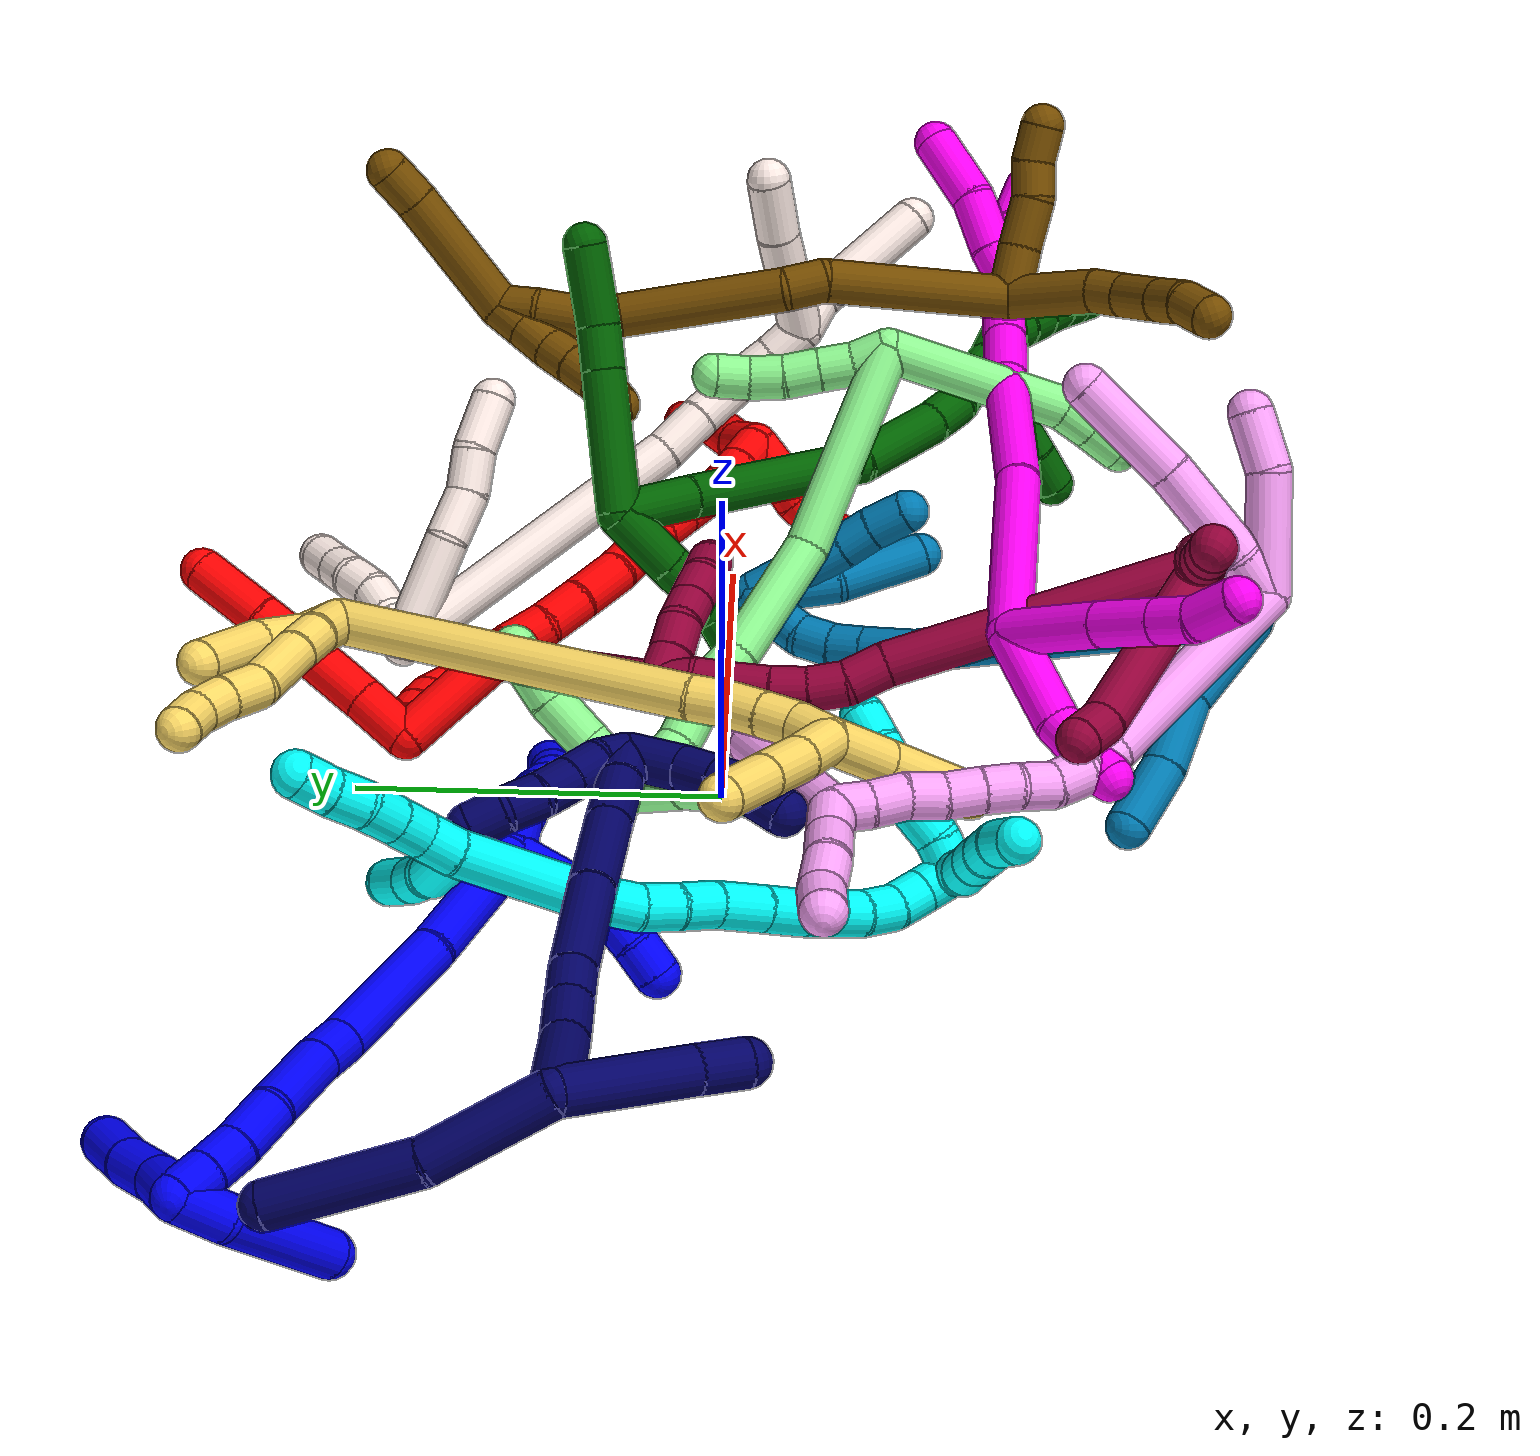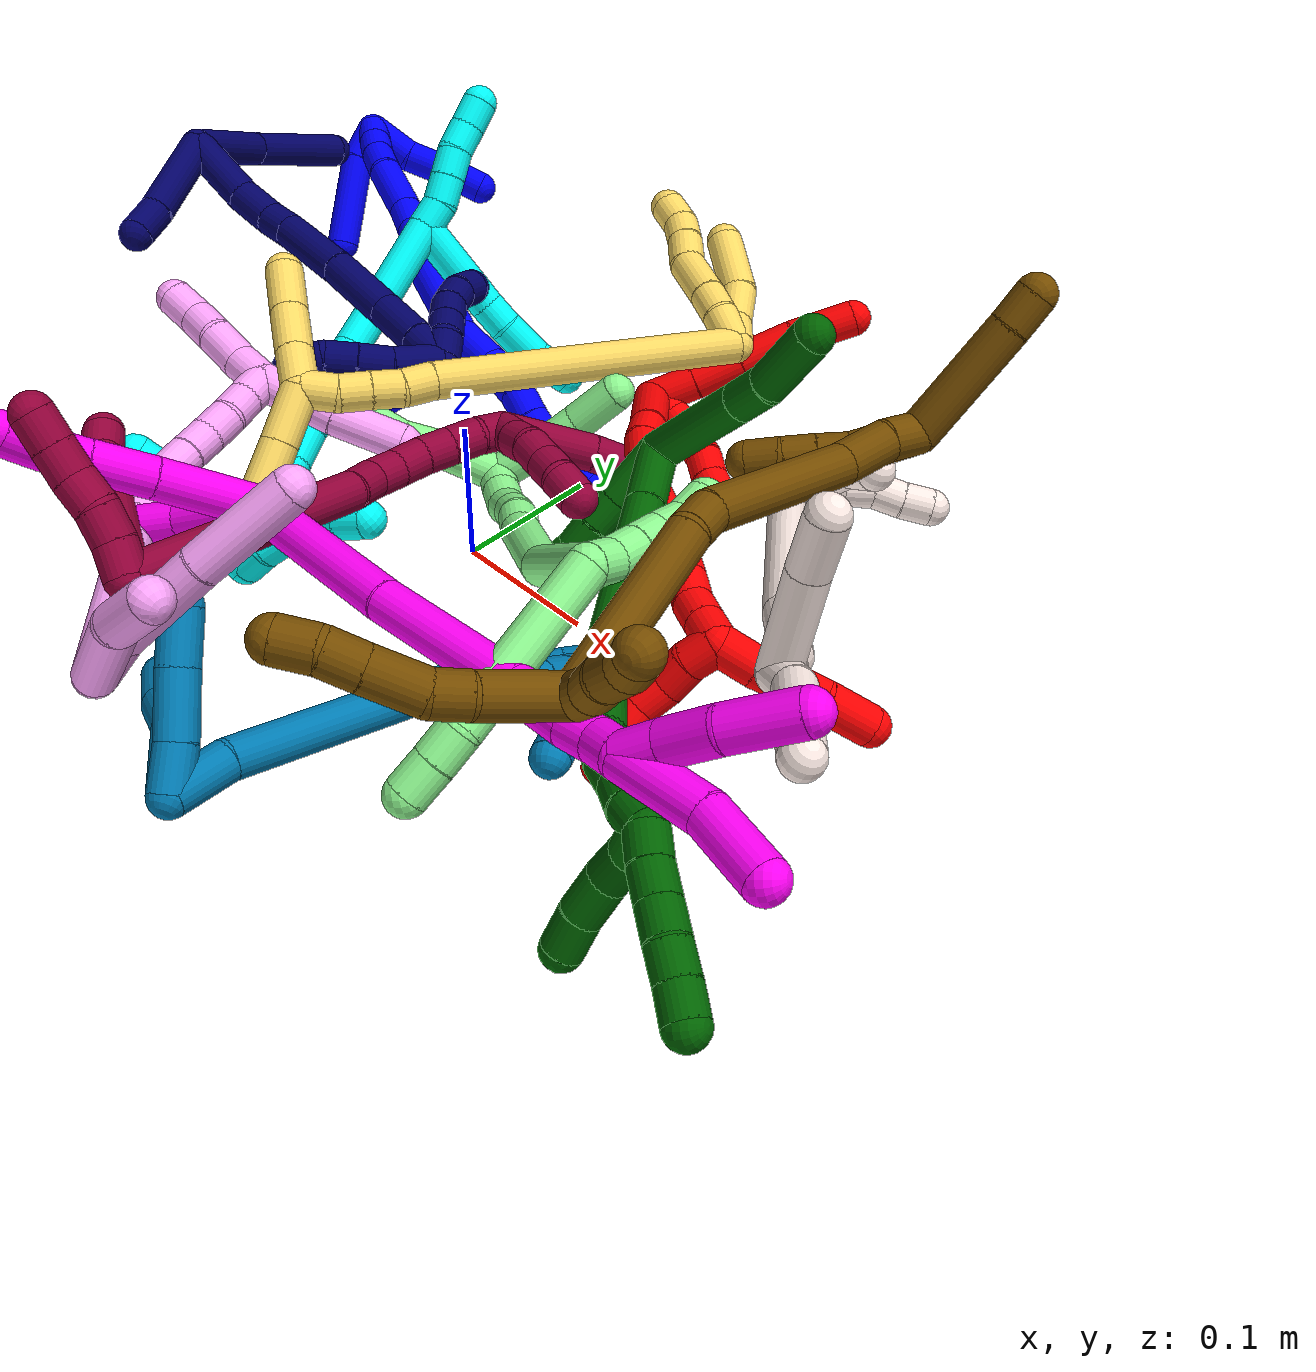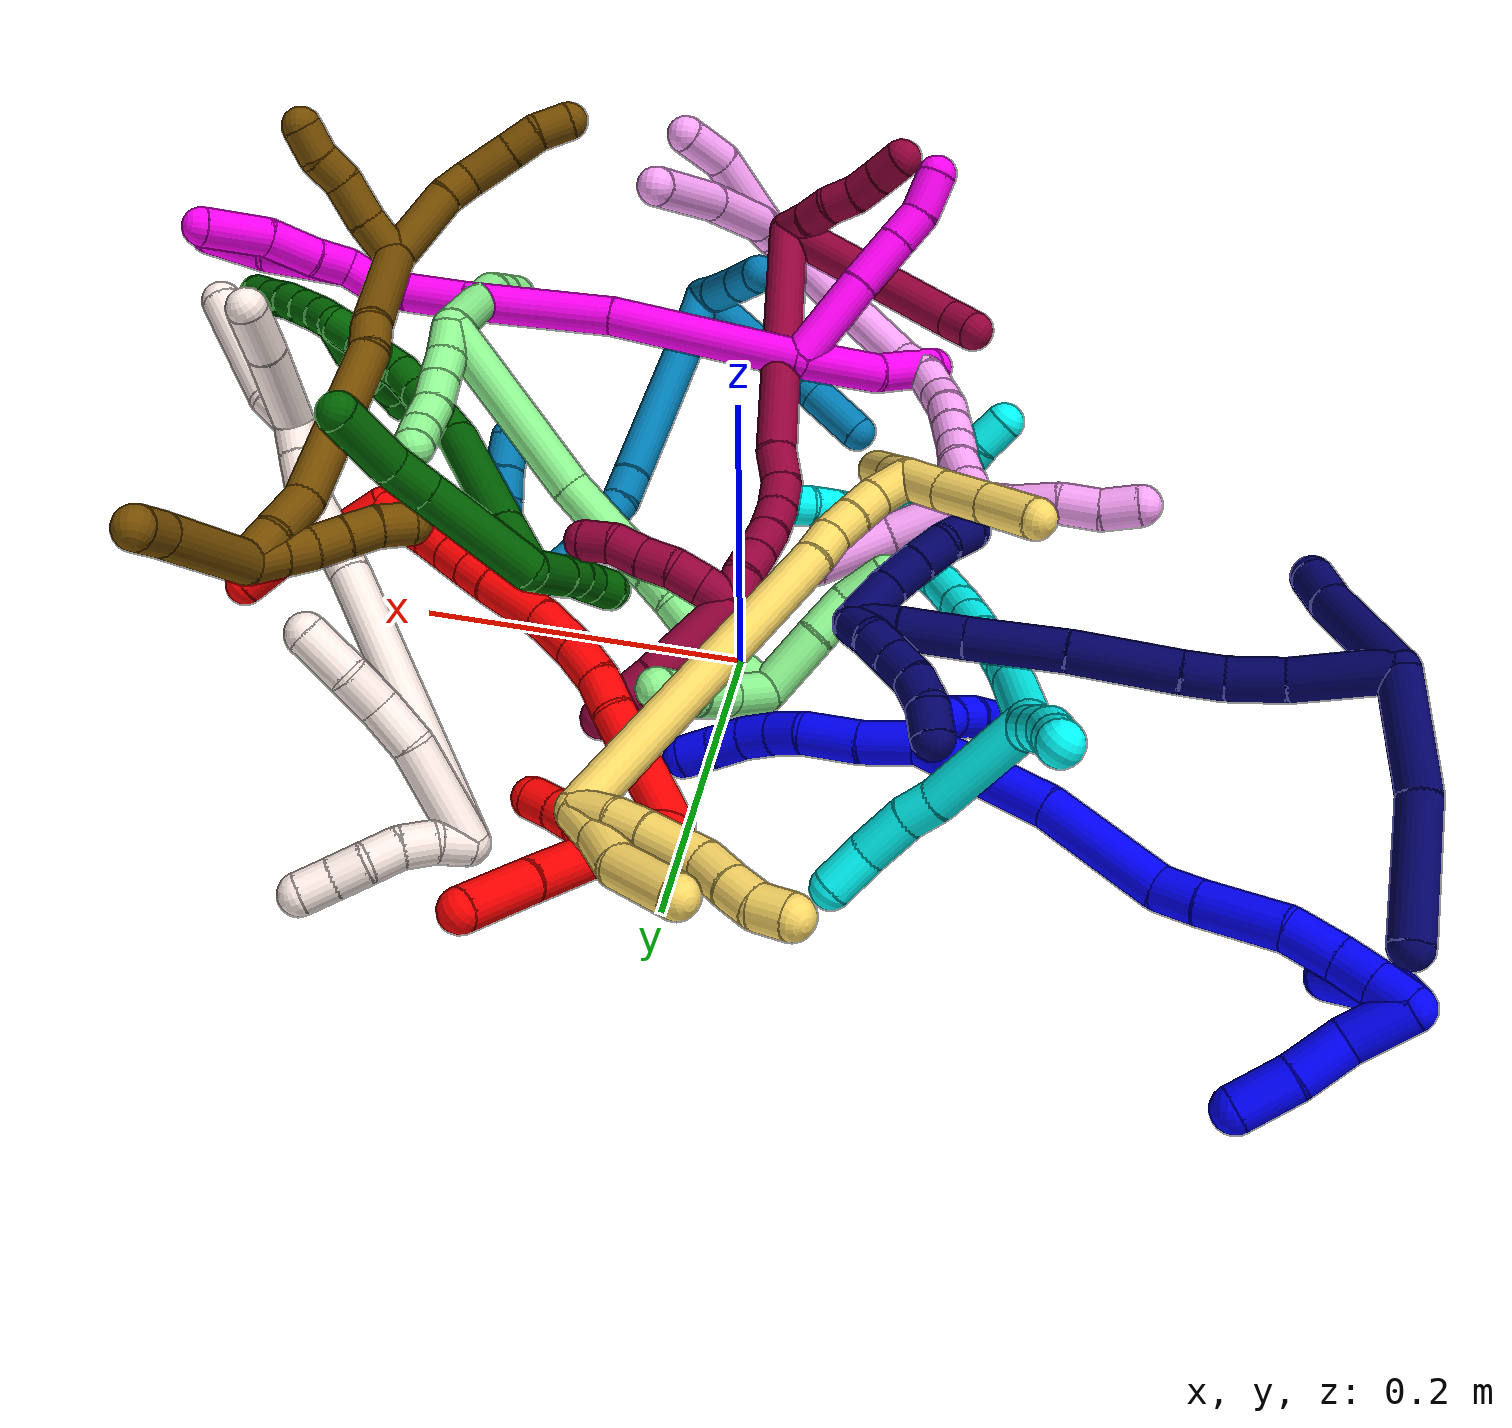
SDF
<sdf version="1.7">
 <world name="default">
  <plugin name="TubeGeneratorPlugin" filename="libtube_generator_plugin.so"/>
  <model name="photoneo_s_sensor">
   <static>1</static>
   <pose>0 0 2 1.57079 1.57079 3.14159</pose>
   <link name="link">
    <inertial><mass>0.1</mass></inertial>
    <sensor name="sensor" type="depth">
     <update_rate>30</update_rate>
     <camera>
      <horizontal_fov>1.22</horizontal_fov>
      <image><width>1920</width><height>1200</height><format>B8G8R8</format></image>
      <clip><near>0.1</near><far>4</far></clip>
      <depth_camera><output>points</output></depth_camera>
     </camera>
     <plugin name="camera_plugin" filename="libgazebo_ros_depth_camera.so">
      <baseline>0.2</baseline>
      <alwaysOn>1</alwaysOn>
      <updateRate>0.0</updateRate>
      <cameraName>camera_ir</cameraName>
      <imageTopicName>/camera/color/image_raw</imageTopicName>
      <cameraInfoTopicName>/camera/color/camera_info</cameraInfoTopicName>
      <depthImageTopicName>/camera/depth/image_raw</depthImageTopicName>
      <depthImageCameraInfoTopicName>/camera/depth/camera_info</depthImageCameraInfoTopicName>
      <pointCloudTopicName>/camera/depth/points</pointCloudTopicName>
      <frameName>fr_optical</frameName>
      <pointCloudCutoff>0.1</pointCloudCutoff>
      <pointCloudCutoffMax>2.0</pointCloudCutoffMax>
      <distortionK1>0</distortionK1>
      <distortionK2>0</distortionK2>
      <distortionK3>0</distortionK3>
      <distortionT1>0</distortionT1>
      <distortionT2>0</distortionT2>
      <CxPrime>0</CxPrime>
      <Cx>0</Cx>
      <Cy>0</Cy>
      <focalLength>0</focalLength>
      <hackBaseline>0</hackBaseline>
     </plugin>
    </sensor>
   </link>
  </model>
  <gravity>0 0 -9.8</gravity>
  <magnetic_field>6e-06 2.3e-05 -4.2e-05</magnetic_field>
  <atmosphere type="adiabatic"/>
  <physics name="default_physics" default="0" type="ode">
   <max_step_size>0.003</max_step_size>
   <real_time_factor>1</real_time_factor>
   <real_time_update_rate>1000</real_time_update_rate>
   <max_contacts>10000</max_contacts>
   <ode>
    <solver>
     <type>quick</type>
     <iters>100</iters>
     <sor>1.3</sor>
     <use_dynamic_moi_rescaling>0</use_dynamic_moi_rescaling>
    </solver>
    <constraints>
     <contact_max_correcting_vel>0</contact_max_correcting_vel>
     <contact_surface_layer>0.001</contact_surface_layer>
     <cfm>0</cfm>
     <erp>0.2</erp>
    </constraints>
   </ode>
  </physics>
  <scene><ambient>0.4 0.4 0.4 1</ambient><background>0.7 0.7 0.7 1</background><shadows>0</shadows></scene>
  <audio><device>default</device></audio>
  <spherical_coordinates>
   <surface_model>EARTH_WGS84</surface_model>
   <latitude_deg>0</latitude_deg>
   <longitude_deg>0</longitude_deg>
   <elevation>0</elevation>
   <heading_deg>0</heading_deg>
  </spherical_coordinates>
  <model name="bin">
   <static>1</static>
   <link name="bottom">
    <collision name="collision-bottom">
     <pose>0 0 -0.01 0 -0 0</pose>
     <geometry><box><size>0.8 0.6 0.02</size></box></geometry>
     <surface>
      <friction><ode><mu>100</mu><mu2>100</mu2></ode></friction>
      <contact><collide_bitmask>65535</collide_bitmask></contact>
     </surface>
    </collision>
   </link>
   <link name="west_wall">
    <collision name="collision-west_wall">
     <pose>-0.41 0 0.1 0 -0 0</pose>
     <geometry><box><size>0.02 0.6 0.2</size></box></geometry>
     <surface>
      <friction><ode><mu>100</mu><mu2>100</mu2></ode></friction>
      <contact><collide_bitmask>65535</collide_bitmask></contact>
     </surface>
    </collision>
   </link>
   <link name="east_wall">
    <collision name="collision-east_wall">
     <pose>0.41 0 0.1 0 -0 0</pose>
     <geometry><box><size>0.02 0.6 0.2</size></box></geometry>
     <surface>
      <friction><ode><mu>100</mu><mu2>100</mu2></ode></friction>
      <contact><collide_bitmask>65535</collide_bitmask></contact>
     </surface>
    </collision>
   </link>
   <link name="south_wall">
    <collision name="collision-south_wall">
     <pose>0 -0.31 0.1 0 -0 0</pose>
     <geometry><box><size>0.8 0.02 0.2</size></box></geometry>
     <surface>
      <friction><ode><mu>100</mu><mu2>100</mu2></ode></friction>
      <contact><collide_bitmask>65535</collide_bitmask></contact>
     </surface>
    </collision>
   </link>
   <link name="north_wall">
    <collision name="collision-north_wall">
     <pose>0 0.31 0.1 0 -0 0</pose>
     <geometry><box><size>0.8 0.02 0.2</size></box></geometry>
     <surface>
      <friction><ode><mu>100</mu><mu2>100</mu2></ode></friction>
      <contact><collide_bitmask>65535</collide_bitmask></contact>
     </surface>
    </collision>
   </link>
  </model>
  <model name="1">
   <static>0</static>
   <link name="1">
    <collision name="collision-cylinder-e_1_2_8">
     <pose>0.001054 0.001989 -0.016527 -3.02183 0.063254 -0.971163</pose>
     <geometry><cylinder><radius>0.0125</radius><length>0.033359</length></cylinder></geometry>
     <surface>
      <friction><ode><mu>1.16</mu><mu2>1.16</mu2><slip1>0</slip1><slip2>0</slip2></ode></friction>
      <contact><ode><kp>1e+06</kp><kd>1</kd><max_vel>0</max_vel><min_depth>0.001</min_depth></ode></contact>
     </surface>
    </collision>
    <visual name="visual-cylinder-e_1_2_8">
     <pose>0.001054 0.001989 -0.016527 -3.02183 0.063254 -0.971163</pose>
     <geometry><cylinder><radius>0.0125</radius><length>0.033359</length></cylinder></geometry>
     <material><ambient>0 0 1 1</ambient></material>
    </visual>
    <collision name="collision-cylinder-e_2_8_9">
     <pose>0.004544 0.003761 -0.05013 3.12891 0.141656 2.96332</pose>
     <geometry><cylinder><radius>0.0125</radius><length>0.034501</length></cylinder></geometry>
     <surface>
      <friction><ode><mu>1.16</mu><mu2>1.16</mu2><slip1>0</slip1><slip2>0</slip2></ode></friction>
      <contact><ode><kp>1e+06</kp><kd>1</kd><max_vel>0</max_vel><min_depth>0.001</min_depth></ode></contact>
     </surface>
    </collision>
    <visual name="visual-cylinder-e_2_8_9">
     <pose>0.004544 0.003761 -0.05013 3.12891 0.141656 2.96332</pose>
     <geometry><cylinder><radius>0.0125</radius><length>0.034501</length></cylinder></geometry>
     <material><ambient>0 0 1 1</ambient></material>
    </visual>
    <collision name="collision-cylinder-e_3_9_10">
     <pose>0.005627 0.002219 -0.077456 3.01298 -0.130153 -1.58273</pose>
     <geometry><cylinder><radius>0.0125</radius><length>0.020846</length></cylinder></geometry>
     <surface>
      <friction><ode><mu>1.16</mu><mu2>1.16</mu2><slip1>0</slip1><slip2>0</slip2></ode></friction>
      <contact><ode><kp>1e+06</kp><kd>1</kd><max_vel>0</max_vel><min_depth>0.001</min_depth></ode></contact>
     </surface>
    </collision>
    <visual name="visual-cylinder-e_3_9_10">
     <pose>0.005627 0.002219 -0.077456 3.01298 -0.130153 -1.58273</pose>
     <geometry><cylinder><radius>0.0125</radius><length>0.020846</length></cylinder></geometry>
     <material><ambient>0 0 1 1</ambient></material>
    </visual>
    <collision name="collision-cylinder-e_4_10_11">
     <pose>0.002503 0.000718 -0.0976 3.12385 -0.177146 -2.94247</pose>
     <geometry><cylinder><radius>0.0125</radius><length>0.020106</length></cylinder></geometry>
     <surface>
      <friction><ode><mu>1.16</mu><mu2>1.16</mu2><slip1>0</slip1><slip2>0</slip2></ode></friction>
      <contact><ode><kp>1e+06</kp><kd>1</kd><max_vel>0</max_vel><min_depth>0.001</min_depth></ode></contact>
     </surface>
    </collision>
    <visual name="visual-cylinder-e_4_10_11">
     <pose>0.002503 0.000718 -0.0976 3.12385 -0.177146 -2.94247</pose>
     <geometry><cylinder><radius>0.0125</radius><length>0.020106</length></cylinder></geometry>
     <material><ambient>0 0 1 1</ambient></material>
    </visual>
    <collision name="collision-cylinder-e_5_11_12">
     <pose>-0.001835 0.002074 -0.117525 -2.99007 -0.247693 2.04647</pose>
     <geometry><cylinder><radius>0.0125</radius><length>0.020934</length></cylinder></geometry>
     <surface>
      <friction><ode><mu>1.16</mu><mu2>1.16</mu2><slip1>0</slip1><slip2>0</slip2></ode></friction>
      <contact><ode><kp>1e+06</kp><kd>1</kd><max_vel>0</max_vel><min_depth>0.001</min_depth></ode></contact>
     </surface>
    </collision>
    <visual name="visual-cylinder-e_5_11_12">
     <pose>-0.001835 0.002074 -0.117525 -2.99007 -0.247693 2.04647</pose>
     <geometry><cylinder><radius>0.0125</radius><length>0.020934</length></cylinder></geometry>
     <material><ambient>0 0 1 1</ambient></material>
    </visual>
    <collision name="collision-cylinder-e_6_12_6">
     <pose>-0.006467 0.005968 -0.137185 -2.90103 -0.205453 1.41237</pose>
     <geometry><cylinder><radius>0.0125</radius><length>0.020254</length></cylinder></geometry>
     <surface>
      <friction><ode><mu>1.16</mu><mu2>1.16</mu2><slip1>0</slip1><slip2>0</slip2></ode></friction>
      <contact><ode><kp>1e+06</kp><kd>1</kd><max_vel>0</max_vel><min_depth>0.001</min_depth></ode></contact>
     </surface>
    </collision>
    <visual name="visual-cylinder-e_6_12_6">
     <pose>-0.006467 0.005968 -0.137185 -2.90103 -0.205453 1.41237</pose>
     <geometry><cylinder><radius>0.0125</radius><length>0.020254</length></cylinder></geometry>
     <material><ambient>0 0 1 1</ambient></material>
    </visual>
    <collision name="collision-cylinder-e_1_2_13">
     <pose>-0.006095 -0.016119 -0.003517 1.78559 -0.353878 -0.436959</pose>
     <geometry><cylinder><radius>0.0125</radius><length>0.035176</length></cylinder></geometry>
     <surface>
      <friction><ode><mu>1.16</mu><mu2>1.16</mu2><slip1>0</slip1><slip2>0</slip2></ode></friction>
      <contact><ode><kp>1e+06</kp><kd>1</kd><max_vel>0</max_vel><min_depth>0.001</min_depth></ode></contact>
     </surface>
    </collision>
    <visual name="visual-cylinder-e_1_2_13">
     <pose>-0.006095 -0.016119 -0.003517 1.78559 -0.353878 -0.436959</pose>
     <geometry><cylinder><radius>0.0125</radius><length>0.035176</length></cylinder></geometry>
     <material><ambient>0 0 1 1</ambient></material>
    </visual>
    <collision name="collision-cylinder-e_2_13_14">
     <pose>-0.015469 -0.043648 -0.006019 1.48219 -0.278804 -0.255401</pose>
     <geometry><cylinder><radius>0.0125</radius><length>0.023831</length></cylinder></geometry>
     <surface>
      <friction><ode><mu>1.16</mu><mu2>1.16</mu2><slip1>0</slip1><slip2>0</slip2></ode></friction>
      <contact><ode><kp>1e+06</kp><kd>1</kd><max_vel>0</max_vel><min_depth>0.001</min_depth></ode></contact>
     </surface>
    </collision>
    <visual name="visual-cylinder-e_2_13_14">
     <pose>-0.015469 -0.043648 -0.006019 1.48219 -0.278804 -0.255401</pose>
     <geometry><cylinder><radius>0.0125</radius><length>0.023831</length></cylinder></geometry>
     <material><ambient>0 0 1 1</ambient></material>
    </visual>
    <collision name="collision-cylinder-e_3_14_15">
     <pose>-0.024077 -0.063671 -0.002386 1.27553 -0.534516 -0.40039</pose>
     <geometry><cylinder><radius>0.0125</radius><length>0.020921</length></cylinder></geometry>
     <surface>
      <friction><ode><mu>1.16</mu><mu2>1.16</mu2><slip1>0</slip1><slip2>0</slip2></ode></friction>
      <contact><ode><kp>1e+06</kp><kd>1</kd><max_vel>0</max_vel><min_depth>0.001</min_depth></ode></contact>
     </surface>
    </collision>
    <visual name="visual-cylinder-e_3_14_15">
     <pose>-0.024077 -0.063671 -0.002386 1.27553 -0.534516 -0.40039</pose>
     <geometry><cylinder><radius>0.0125</radius><length>0.020921</length></cylinder></geometry>
     <material><ambient>0 0 1 1</ambient></material>
    </visual>
    <collision name="collision-cylinder-e_4_15_5">
     <pose>-0.035709 -0.079985 0.001524 1.40474 -0.679094 -0.580994</pose>
     <geometry><cylinder><radius>0.0125</radius><length>0.020072</length></cylinder></geometry>
     <surface>
      <friction><ode><mu>1.16</mu><mu2>1.16</mu2><slip1>0</slip1><slip2>0</slip2></ode></friction>
      <contact><ode><kp>1e+06</kp><kd>1</kd><max_vel>0</max_vel><min_depth>0.001</min_depth></ode></contact>
     </surface>
    </collision>
    <visual name="visual-cylinder-e_4_15_5">
     <pose>-0.035709 -0.079985 0.001524 1.40474 -0.679094 -0.580994</pose>
     <geometry><cylinder><radius>0.0125</radius><length>0.020072</length></cylinder></geometry>
     <material><ambient>0 0 1 1</ambient></material>
    </visual>
    <collision name="collision-cylinder-e_1_2_16">
     <pose>-0.013073 0.009469 0.038229 -0.242799 -0.320497 0.039433</pose>
     <geometry><cylinder><radius>0.0125</radius><length>0.082994</length></cylinder></geometry>
     <surface>
      <friction><ode><mu>1.16</mu><mu2>1.16</mu2><slip1>0</slip1><slip2>0</slip2></ode></friction>
      <contact><ode><kp>1e+06</kp><kd>1</kd><max_vel>0</max_vel><min_depth>0.001</min_depth></ode></contact>
     </surface>
    </collision>
    <visual name="visual-cylinder-e_1_2_16">
     <pose>-0.013073 0.009469 0.038229 -0.242799 -0.320497 0.039433</pose>
     <geometry><cylinder><radius>0.0125</radius><length>0.082994</length></cylinder></geometry>
     <material><ambient>0 0 1 1</ambient></material>
    </visual>
    <collision name="collision-cylinder-e_2_16_17">
     <pose>-0.041266 0.031727 0.107746 -0.388029 -0.420613 0.083836</pose>
     <geometry><cylinder><radius>0.0125</radius><length>0.074057</length></cylinder></geometry>
     <surface>
      <friction><ode><mu>1.16</mu><mu2>1.16</mu2><slip1>0</slip1><slip2>0</slip2></ode></friction>
      <contact><ode><kp>1e+06</kp><kd>1</kd><max_vel>0</max_vel><min_depth>0.001</min_depth></ode></contact>
     </surface>
    </collision>
    <visual name="visual-cylinder-e_2_16_17">
     <pose>-0.041266 0.031727 0.107746 -0.388029 -0.420613 0.083836</pose>
     <geometry><cylinder><radius>0.0125</radius><length>0.074057</length></cylinder></geometry>
     <material><ambient>0 0 1 1</ambient></material>
    </visual>
    <collision name="collision-cylinder-e_3_17_18">
     <pose>-0.057829 0.047837 0.150565 -0.280471 -0.119683 0.016915</pose>
     <geometry><cylinder><radius>0.0125</radius><length>0.024172</length></cylinder></geometry>
     <surface>
      <friction><ode><mu>1.16</mu><mu2>1.16</mu2><slip1>0</slip1><slip2>0</slip2></ode></friction>
      <contact><ode><kp>1e+06</kp><kd>1</kd><max_vel>0</max_vel><min_depth>0.001</min_depth></ode></contact>
     </surface>
    </collision>
    <visual name="visual-cylinder-e_3_17_18">
     <pose>-0.057829 0.047837 0.150565 -0.280471 -0.119683 0.016915</pose>
     <geometry><cylinder><radius>0.0125</radius><length>0.024172</length></cylinder></geometry>
     <material><ambient>0 0 1 1</ambient></material>
    </visual>
    <collision name="collision-cylinder-e_4_18_19">
     <pose>-0.062316 0.055672 0.185191 -0.192991 -0.128677 0.012473</pose>
     <geometry><cylinder><radius>0.0125</radius><length>0.047457</length></cylinder></geometry>
     <surface>
      <friction><ode><mu>1.16</mu><mu2>1.16</mu2><slip1>0</slip1><slip2>0</slip2></ode></friction>
      <contact><ode><kp>1e+06</kp><kd>1</kd><max_vel>0</max_vel><min_depth>0.001</min_depth></ode></contact>
     </surface>
    </collision>
    <visual name="visual-cylinder-e_4_18_19">
     <pose>-0.062316 0.055672 0.185191 -0.192991 -0.128677 0.012473</pose>
     <geometry><cylinder><radius>0.0125</radius><length>0.047457</length></cylinder></geometry>
     <material><ambient>0 0 1 1</ambient></material>
    </visual>
    <collision name="collision-cylinder-e_5_19_20">
     <pose>-0.070386 0.06426 0.221156 -0.306647 -0.356353 0.055646</pose>
     <geometry><cylinder><radius>0.0125</radius><length>0.028807</length></cylinder></geometry>
     <surface>
      <friction><ode><mu>1.16</mu><mu2>1.16</mu2><slip1>0</slip1><slip2>0</slip2></ode></friction>
      <contact><ode><kp>1e+06</kp><kd>1</kd><max_vel>0</max_vel><min_depth>0.001</min_depth></ode></contact>
     </surface>
    </collision>
    <visual name="visual-cylinder-e_5_19_20">
     <pose>-0.070386 0.06426 0.221156 -0.306647 -0.356353 0.055646</pose>
     <geometry><cylinder><radius>0.0125</radius><length>0.028807</length></cylinder></geometry>
     <material><ambient>0 0 1 1</ambient></material>
    </visual>
    <collision name="collision-cylinder-e_6_20_21">
     <pose>-0.078861 0.072451 0.243388 -0.414074 -0.325317 0.068914</pose>
     <geometry><cylinder><radius>0.0125</radius><length>0.021589</length></cylinder></geometry>
     <surface>
      <friction><ode><mu>1.16</mu><mu2>1.16</mu2><slip1>0</slip1><slip2>0</slip2></ode></friction>
      <contact><ode><kp>1e+06</kp><kd>1</kd><max_vel>0</max_vel><min_depth>0.001</min_depth></ode></contact>
     </surface>
    </collision>
    <visual name="visual-cylinder-e_6_20_21">
     <pose>-0.078861 0.072451 0.243388 -0.414074 -0.325317 0.068914</pose>
     <geometry><cylinder><radius>0.0125</radius><length>0.021589</length></cylinder></geometry>
     <material><ambient>0 0 1 1</ambient></material>
    </visual>
    <collision name="collision-cylinder-e_7_21_1">
     <pose>-0.085613 0.080889 0.261688 -0.450636 -0.321117 0.074208</pose>
     <geometry><cylinder><radius>0.0125</radius><length>0.020923</length></cylinder></geometry>
     <surface>
      <friction><ode><mu>1.16</mu><mu2>1.16</mu2><slip1>0</slip1><slip2>0</slip2></ode></friction>
      <contact><ode><kp>1e+06</kp><kd>1</kd><max_vel>0</max_vel><min_depth>0.001</min_depth></ode></contact>
     </surface>
    </collision>
    <visual name="visual-cylinder-e_7_21_1">
     <pose>-0.085613 0.080889 0.261688 -0.450636 -0.321117 0.074208</pose>
     <geometry><cylinder><radius>0.0125</radius><length>0.020923</length></cylinder></geometry>
     <material><ambient>0 0 1 1</ambient></material>
    </visual>
    <collision name="collision-cylinder-e_1_1_22">
     <pose>-0.09423 0.073656 0.264728 2.04253 -0.388801 -0.622067</pose>
     <geometry><cylinder><radius>0.0125</radius><length>0.02804</length></cylinder></geometry>
     <surface>
      <friction><ode><mu>1.16</mu><mu2>1.16</mu2><slip1>0</slip1><slip2>0</slip2></ode></friction>
      <contact><ode><kp>1e+06</kp><kd>1</kd><max_vel>0</max_vel><min_depth>0.001</min_depth></ode></contact>
     </surface>
    </collision>
    <visual name="visual-cylinder-e_1_1_22">
     <pose>-0.09423 0.073656 0.264728 2.04253 -0.388801 -0.622067</pose>
     <geometry><cylinder><radius>0.0125</radius><length>0.02804</length></cylinder></geometry>
     <material><ambient>0 0 1 1</ambient></material>
    </visual>
    <collision name="collision-cylinder-e_2_22_4">
     <pose>-0.115015 0.039777 0.235234 2.38399 -0.444472 -1.0327</pose>
     <geometry><cylinder><radius>0.0125</radius><length>0.07196</length></cylinder></geometry>
     <surface>
      <friction><ode><mu>1.16</mu><mu2>1.16</mu2><slip1>0</slip1><slip2>0</slip2></ode></friction>
      <contact><ode><kp>1e+06</kp><kd>1</kd><max_vel>0</max_vel><min_depth>0.001</min_depth></ode></contact>
     </surface>
    </collision>
    <visual name="visual-cylinder-e_2_22_4">
     <pose>-0.115015 0.039777 0.235234 2.38399 -0.444472 -1.0327</pose>
     <geometry><cylinder><radius>0.0125</radius><length>0.07196</length></cylinder></geometry>
     <material><ambient>0 0 1 1</ambient></material>
    </visual>
    <collision name="collision-cylinder-e_1_1_23">
     <pose>-0.094733 0.092574 0.255429 -2.69046 -0.331854 1.26089</pose>
     <geometry><cylinder><radius>0.0125</radius><length>0.035717</length></cylinder></geometry>
     <surface>
      <friction><ode><mu>1.16</mu><mu2>1.16</mu2><slip1>0</slip1><slip2>0</slip2></ode></friction>
      <contact><ode><kp>1e+06</kp><kd>1</kd><max_vel>0</max_vel><min_depth>0.001</min_depth></ode></contact>
     </surface>
    </collision>
    <visual name="visual-cylinder-e_1_1_23">
     <pose>-0.094733 0.092574 0.255429 -2.69046 -0.331854 1.26089</pose>
     <geometry><cylinder><radius>0.0125</radius><length>0.035717</length></cylinder></geometry>
     <material><ambient>0 0 1 1</ambient></material>
    </visual>
    <collision name="collision-cylinder-e_2_23_24">
     <pose>-0.104584 0.110147 0.229105 -2.39914 -0.260914 0.650169</pose>
     <geometry><cylinder><radius>0.0125</radius><length>0.031266</length></cylinder></geometry>
     <surface>
      <friction><ode><mu>1.16</mu><mu2>1.16</mu2><slip1>0</slip1><slip2>0</slip2></ode></friction>
      <contact><ode><kp>1e+06</kp><kd>1</kd><max_vel>0</max_vel><min_depth>0.001</min_depth></ode></contact>
     </surface>
    </collision>
    <visual name="visual-cylinder-e_2_23_24">
     <pose>-0.104584 0.110147 0.229105 -2.39914 -0.260914 0.650169</pose>
     <geometry><cylinder><radius>0.0125</radius><length>0.031266</length></cylinder></geometry>
     <material><ambient>0 0 1 1</ambient></material>
    </visual>
    <collision name="collision-cylinder-e_3_24_3">
     <pose>-0.112356 0.129501 0.204749 -2.53681 -0.228441 0.704781</pose>
     <geometry><cylinder><radius>0.0125</radius><length>0.033017</length></cylinder></geometry>
     <surface>
      <friction><ode><mu>1.16</mu><mu2>1.16</mu2><slip1>0</slip1><slip2>0</slip2></ode></friction>
      <contact><ode><kp>1e+06</kp><kd>1</kd><max_vel>0</max_vel><min_depth>0.001</min_depth></ode></contact>
     </surface>
    </collision>
    <visual name="visual-cylinder-e_3_24_3">
     <pose>-0.112356 0.129501 0.204749 -2.53681 -0.228441 0.704781</pose>
     <geometry><cylinder><radius>0.0125</radius><length>0.033017</length></cylinder></geometry>
     <material><ambient>0 0 1 1</ambient></material>
    </visual>
    <collision name="collision-sphere-3">
     <pose>-0.116094 0.138644 0.191522 0 -0 0</pose>
     <geometry><sphere><radius>0.0125</radius></sphere></geometry>
     <surface>
      <friction><ode><mu>1.16</mu><mu2>1.16</mu2><slip1>0</slip1><slip2>0</slip2></ode></friction>
      <contact><ode><kp>1e+06</kp><kd>1</kd><max_vel>0</max_vel><min_depth>0.001</min_depth></ode></contact>
     </surface>
    </collision>
    <visual name="visual-sphere-3">
     <pose>-0.116094 0.138644 0.191522 0 -0 0</pose>
     <geometry><sphere><radius>0.0125</radius></sphere></geometry>
     <material><ambient>0 0 1 1</ambient></material>
    </visual>
    <collision name="collision-sphere-24">
     <pose>-0.108617 0.120359 0.217977 0 -0 0</pose>
     <geometry><sphere><radius>0.0125</radius></sphere></geometry>
     <surface>
      <friction><ode><mu>1.16</mu><mu2>1.16</mu2><slip1>0</slip1><slip2>0</slip2></ode></friction>
      <contact><ode><kp>1e+06</kp><kd>1</kd><max_vel>0</max_vel><min_depth>0.001</min_depth></ode></contact>
     </surface>
    </collision>
    <visual name="visual-sphere-24">
     <pose>-0.108617 0.120359 0.217977 0 -0 0</pose>
     <geometry><sphere><radius>0.0125</radius></sphere></geometry>
     <material><ambient>0 0 1 1</ambient></material>
    </visual>
    <collision name="collision-sphere-23">
     <pose>-0.100552 0.099935 0.240234 0 -0 0</pose>
     <geometry><sphere><radius>0.0125</radius></sphere></geometry>
     <surface>
      <friction><ode><mu>1.16</mu><mu2>1.16</mu2><slip1>0</slip1><slip2>0</slip2></ode></friction>
      <contact><ode><kp>1e+06</kp><kd>1</kd><max_vel>0</max_vel><min_depth>0.001</min_depth></ode></contact>
     </surface>
    </collision>
    <visual name="visual-sphere-23">
     <pose>-0.100552 0.099935 0.240234 0 -0 0</pose>
     <geometry><sphere><radius>0.0125</radius></sphere></geometry>
     <material><ambient>0 0 1 1</ambient></material>
    </visual>
    <collision name="collision-sphere-4">
     <pose>-0.130486 0.017454 0.211635 0 -0 0</pose>
     <geometry><sphere><radius>0.0125</radius></sphere></geometry>
     <surface>
      <friction><ode><mu>1.16</mu><mu2>1.16</mu2><slip1>0</slip1><slip2>0</slip2></ode></friction>
      <contact><ode><kp>1e+06</kp><kd>1</kd><max_vel>0</max_vel><min_depth>0.001</min_depth></ode></contact>
     </surface>
    </collision>
    <visual name="visual-sphere-4">
     <pose>-0.130486 0.017454 0.211635 0 -0 0</pose>
     <geometry><sphere><radius>0.0125</radius></sphere></geometry>
     <material><ambient>0 0 1 1</ambient></material>
    </visual>
    <collision name="collision-sphere-22">
     <pose>-0.099545 0.062099 0.258833 0 -0 0</pose>
     <geometry><sphere><radius>0.0125</radius></sphere></geometry>
     <surface>
      <friction><ode><mu>1.16</mu><mu2>1.16</mu2><slip1>0</slip1><slip2>0</slip2></ode></friction>
      <contact><ode><kp>1e+06</kp><kd>1</kd><max_vel>0</max_vel><min_depth>0.001</min_depth></ode></contact>
     </surface>
    </collision>
    <visual name="visual-sphere-22">
     <pose>-0.099545 0.062099 0.258833 0 -0 0</pose>
     <geometry><sphere><radius>0.0125</radius></sphere></geometry>
     <material><ambient>0 0 1 1</ambient></material>
    </visual>
    <collision name="collision-sphere-1">
     <pose>-0.088915 0.085213 0.270624 0 -0 0</pose>
     <geometry><sphere><radius>0.0125</radius></sphere></geometry>
     <surface>
      <friction><ode><mu>1.16</mu><mu2>1.16</mu2><slip1>0</slip1><slip2>0</slip2></ode></friction>
      <contact><ode><kp>1e+06</kp><kd>1</kd><max_vel>0</max_vel><min_depth>0.001</min_depth></ode></contact>
     </surface>
    </collision>
    <visual name="visual-sphere-1">
     <pose>-0.088915 0.085213 0.270624 0 -0 0</pose>
     <geometry><sphere><radius>0.0125</radius></sphere></geometry>
     <material><ambient>0 0 1 1</ambient></material>
    </visual>
    <collision name="collision-sphere-21">
     <pose>-0.082311 0.076566 0.252752 0 -0 0</pose>
     <geometry><sphere><radius>0.0125</radius></sphere></geometry>
     <surface>
      <friction><ode><mu>1.16</mu><mu2>1.16</mu2><slip1>0</slip1><slip2>0</slip2></ode></friction>
      <contact><ode><kp>1e+06</kp><kd>1</kd><max_vel>0</max_vel><min_depth>0.001</min_depth></ode></contact>
     </surface>
    </collision>
    <visual name="visual-sphere-21">
     <pose>-0.082311 0.076566 0.252752 0 -0 0</pose>
     <geometry><sphere><radius>0.0125</radius></sphere></geometry>
     <material><ambient>0 0 1 1</ambient></material>
    </visual>
    <collision name="collision-sphere-12">
     <pose>-0.004401 0.003605 -0.127556 0 -0 0</pose>
     <geometry><sphere><radius>0.0125</radius></sphere></geometry>
     <surface>
      <friction><ode><mu>1.16</mu><mu2>1.16</mu2><slip1>0</slip1><slip2>0</slip2></ode></friction>
      <contact><ode><kp>1e+06</kp><kd>1</kd><max_vel>0</max_vel><min_depth>0.001</min_depth></ode></contact>
     </surface>
    </collision>
    <visual name="visual-sphere-12">
     <pose>-0.004401 0.003605 -0.127556 0 -0 0</pose>
     <geometry><sphere><radius>0.0125</radius></sphere></geometry>
     <material><ambient>0 0 1 1</ambient></material>
    </visual>
    <collision name="collision-sphere-11">
     <pose>0.000731 0.000542 -0.107494 0 -0 0</pose>
     <geometry><sphere><radius>0.0125</radius></sphere></geometry>
     <surface>
      <friction><ode><mu>1.16</mu><mu2>1.16</mu2><slip1>0</slip1><slip2>0</slip2></ode></friction>
      <contact><ode><kp>1e+06</kp><kd>1</kd><max_vel>0</max_vel><min_depth>0.001</min_depth></ode></contact>
     </surface>
    </collision>
    <visual name="visual-sphere-11">
     <pose>0.000731 0.000542 -0.107494 0 -0 0</pose>
     <geometry><sphere><radius>0.0125</radius></sphere></geometry>
     <material><ambient>0 0 1 1</ambient></material>
    </visual>
    <collision name="collision-sphere-10">
     <pose>0.004274 0.000893 -0.087706 0 -0 0</pose>
     <geometry><sphere><radius>0.0125</radius></sphere></geometry>
     <surface>
      <friction><ode><mu>1.16</mu><mu2>1.16</mu2><slip1>0</slip1><slip2>0</slip2></ode></friction>
      <contact><ode><kp>1e+06</kp><kd>1</kd><max_vel>0</max_vel><min_depth>0.001</min_depth></ode></contact>
     </surface>
    </collision>
    <visual name="visual-sphere-10">
     <pose>0.004274 0.000893 -0.087706 0 -0 0</pose>
     <geometry><sphere><radius>0.0125</radius></sphere></geometry>
     <material><ambient>0 0 1 1</ambient></material>
    </visual>
    <collision name="collision-sphere-9">
     <pose>0.00698 0.003544 -0.067207 0 -0 0</pose>
     <geometry><sphere><radius>0.0125</radius></sphere></geometry>
     <surface>
      <friction><ode><mu>1.16</mu><mu2>1.16</mu2><slip1>0</slip1><slip2>0</slip2></ode></friction>
      <contact><ode><kp>1e+06</kp><kd>1</kd><max_vel>0</max_vel><min_depth>0.001</min_depth></ode></contact>
     </surface>
    </collision>
    <visual name="visual-sphere-9">
     <pose>0.00698 0.003544 -0.067207 0 -0 0</pose>
     <geometry><sphere><radius>0.0125</radius></sphere></geometry>
     <material><ambient>0 0 1 1</ambient></material>
    </visual>
    <collision name="collision-sphere-2">
     <geometry><sphere><radius>0.0125</radius></sphere></geometry>
     <surface>
      <friction><ode><mu>1.16</mu><mu2>1.16</mu2><slip1>0</slip1><slip2>0</slip2></ode></friction>
      <contact><ode><kp>1e+06</kp><kd>1</kd><max_vel>0</max_vel><min_depth>0.001</min_depth></ode></contact>
     </surface>
    </collision>
    <visual name="visual-sphere-2">
     <geometry><sphere><radius>0.0125</radius></sphere></geometry>
     <material><ambient>0 0 1 1</ambient></material>
    </visual>
    <collision name="collision-sphere-19">
     <pose>-0.065361 0.060186 0.208287 0 -0 0</pose>
     <geometry><sphere><radius>0.0125</radius></sphere></geometry>
     <surface>
      <friction><ode><mu>1.16</mu><mu2>1.16</mu2><slip1>0</slip1><slip2>0</slip2></ode></friction>
      <contact><ode><kp>1e+06</kp><kd>1</kd><max_vel>0</max_vel><min_depth>0.001</min_depth></ode></contact>
     </surface>
    </collision>
    <visual name="visual-sphere-19">
     <pose>-0.065361 0.060186 0.208287 0 -0 0</pose>
     <geometry><sphere><radius>0.0125</radius></sphere></geometry>
     <material><ambient>0 0 1 1</ambient></material>
    </visual>
    <collision name="collision-sphere-8">
     <pose>0.002109 0.003978 -0.033054 0 -0 0</pose>
     <geometry><sphere><radius>0.0125</radius></sphere></geometry>
     <surface>
      <friction><ode><mu>1.16</mu><mu2>1.16</mu2><slip1>0</slip1><slip2>0</slip2></ode></friction>
      <contact><ode><kp>1e+06</kp><kd>1</kd><max_vel>0</max_vel><min_depth>0.001</min_depth></ode></contact>
     </surface>
    </collision>
    <visual name="visual-sphere-8">
     <pose>0.002109 0.003978 -0.033054 0 -0 0</pose>
     <geometry><sphere><radius>0.0125</radius></sphere></geometry>
     <material><ambient>0 0 1 1</ambient></material>
    </visual>
    <collision name="collision-sphere-6">
     <pose>-0.008533 0.00833 -0.146813 0 -0 0</pose>
     <geometry><sphere><radius>0.0125</radius></sphere></geometry>
     <surface>
      <friction><ode><mu>1.16</mu><mu2>1.16</mu2><slip1>0</slip1><slip2>0</slip2></ode></friction>
      <contact><ode><kp>1e+06</kp><kd>1</kd><max_vel>0</max_vel><min_depth>0.001</min_depth></ode></contact>
     </surface>
    </collision>
    <visual name="visual-sphere-6">
     <pose>-0.008533 0.00833 -0.146813 0 -0 0</pose>
     <geometry><sphere><radius>0.0125</radius></sphere></geometry>
     <material><ambient>0 0 1 1</ambient></material>
    </visual>
    <collision name="collision-sphere-13">
     <pose>-0.01219 -0.032238 -0.007033 0 -0 0</pose>
     <geometry><sphere><radius>0.0125</radius></sphere></geometry>
     <surface>
      <friction><ode><mu>1.16</mu><mu2>1.16</mu2><slip1>0</slip1><slip2>0</slip2></ode></friction>
      <contact><ode><kp>1e+06</kp><kd>1</kd><max_vel>0</max_vel><min_depth>0.001</min_depth></ode></contact>
     </surface>
    </collision>
    <visual name="visual-sphere-13">
     <pose>-0.01219 -0.032238 -0.007033 0 -0 0</pose>
     <geometry><sphere><radius>0.0125</radius></sphere></geometry>
     <material><ambient>0 0 1 1</ambient></material>
    </visual>
    <collision name="collision-sphere-14">
     <pose>-0.018748 -0.055059 -0.005006 0 -0 0</pose>
     <geometry><sphere><radius>0.0125</radius></sphere></geometry>
     <surface>
      <friction><ode><mu>1.16</mu><mu2>1.16</mu2><slip1>0</slip1><slip2>0</slip2></ode></friction>
      <contact><ode><kp>1e+06</kp><kd>1</kd><max_vel>0</max_vel><min_depth>0.001</min_depth></ode></contact>
     </surface>
    </collision>
    <visual name="visual-sphere-14">
     <pose>-0.018748 -0.055059 -0.005006 0 -0 0</pose>
     <geometry><sphere><radius>0.0125</radius></sphere></geometry>
     <material><ambient>0 0 1 1</ambient></material>
    </visual>
    <collision name="collision-sphere-15">
     <pose>-0.029406 -0.072283 0.000233 0 -0 0</pose>
     <geometry><sphere><radius>0.0125</radius></sphere></geometry>
     <surface>
      <friction><ode><mu>1.16</mu><mu2>1.16</mu2><slip1>0</slip1><slip2>0</slip2></ode></friction>
      <contact><ode><kp>1e+06</kp><kd>1</kd><max_vel>0</max_vel><min_depth>0.001</min_depth></ode></contact>
     </surface>
    </collision>
    <visual name="visual-sphere-15">
     <pose>-0.029406 -0.072283 0.000233 0 -0 0</pose>
     <geometry><sphere><radius>0.0125</radius></sphere></geometry>
     <material><ambient>0 0 1 1</ambient></material>
    </visual>
    <collision name="collision-sphere-5">
     <pose>-0.042013 -0.087687 0.002815 0 -0 0</pose>
     <geometry><sphere><radius>0.0125</radius></sphere></geometry>
     <surface>
      <friction><ode><mu>1.16</mu><mu2>1.16</mu2><slip1>0</slip1><slip2>0</slip2></ode></friction>
      <contact><ode><kp>1e+06</kp><kd>1</kd><max_vel>0</max_vel><min_depth>0.001</min_depth></ode></contact>
     </surface>
    </collision>
    <visual name="visual-sphere-5">
     <pose>-0.042013 -0.087687 0.002815 0 -0 0</pose>
     <geometry><sphere><radius>0.0125</radius></sphere></geometry>
     <material><ambient>0 0 1 1</ambient></material>
    </visual>
    <collision name="collision-sphere-16">
     <pose>-0.026146 0.018937 0.076458 0 -0 0</pose>
     <geometry><sphere><radius>0.0125</radius></sphere></geometry>
     <surface>
      <friction><ode><mu>1.16</mu><mu2>1.16</mu2><slip1>0</slip1><slip2>0</slip2></ode></friction>
      <contact><ode><kp>1e+06</kp><kd>1</kd><max_vel>0</max_vel><min_depth>0.001</min_depth></ode></contact>
     </surface>
    </collision>
    <visual name="visual-sphere-16">
     <pose>-0.026146 0.018937 0.076458 0 -0 0</pose>
     <geometry><sphere><radius>0.0125</radius></sphere></geometry>
     <material><ambient>0 0 1 1</ambient></material>
    </visual>
    <collision name="collision-sphere-17">
     <pose>-0.056386 0.044516 0.139034 0 -0 0</pose>
     <geometry><sphere><radius>0.0125</radius></sphere></geometry>
     <surface>
      <friction><ode><mu>1.16</mu><mu2>1.16</mu2><slip1>0</slip1><slip2>0</slip2></ode></friction>
      <contact><ode><kp>1e+06</kp><kd>1</kd><max_vel>0</max_vel><min_depth>0.001</min_depth></ode></contact>
     </surface>
    </collision>
    <visual name="visual-sphere-17">
     <pose>-0.056386 0.044516 0.139034 0 -0 0</pose>
     <geometry><sphere><radius>0.0125</radius></sphere></geometry>
     <material><ambient>0 0 1 1</ambient></material>
    </visual>
    <collision name="collision-sphere-18">
     <pose>-0.059272 0.051159 0.162096 0 -0 0</pose>
     <geometry><sphere><radius>0.0125</radius></sphere></geometry>
     <surface>
      <friction><ode><mu>1.16</mu><mu2>1.16</mu2><slip1>0</slip1><slip2>0</slip2></ode></friction>
      <contact><ode><kp>1e+06</kp><kd>1</kd><max_vel>0</max_vel><min_depth>0.001</min_depth></ode></contact>
     </surface>
    </collision>
    <visual name="visual-sphere-18">
     <pose>-0.059272 0.051159 0.162096 0 -0 0</pose>
     <geometry><sphere><radius>0.0125</radius></sphere></geometry>
     <material><ambient>0 0 1 1</ambient></material>
    </visual>
    <collision name="collision-sphere-20">
     <pose>-0.075411 0.068335 0.234025 0 -0 0</pose>
     <geometry><sphere><radius>0.0125</radius></sphere></geometry>
     <surface>
      <friction><ode><mu>1.16</mu><mu2>1.16</mu2><slip1>0</slip1><slip2>0</slip2></ode></friction>
      <contact><ode><kp>1e+06</kp><kd>1</kd><max_vel>0</max_vel><min_depth>0.001</min_depth></ode></contact>
     </surface>
    </collision>
    <visual name="visual-sphere-20">
     <pose>-0.075411 0.068335 0.234025 0 -0 0</pose>
     <geometry><sphere><radius>0.0125</radius></sphere></geometry>
     <material><ambient>0 0 1 1</ambient></material>
    </visual>
    <inertial>
     <pose>-0.049217 0.031829 0.10226 0 -0 0</pose>
     <mass>0.75</mass>
     <inertia><ixx>9.5e-05</ixx><ixy>0</ixy><ixz>0</ixz><iyy>8e-05</iyy><iyz>0</iyz><izz>5.3e-05</izz></inertia>
    </inertial>
   </link>
   <pose>-0.124796 0.103951 0.064303 0.464709 -1.21168 -0.629691</pose>
  </model>
  <model name="2">
   <static>0</static>
   <link name="2">
    <collision name="collision-cylinder-e_1_2_8">
     <pose>0.006403 0.013674 -0.005863 -1.97587 0.406387 -0.605814</pose>
     <geometry><cylinder><radius>0.0125</radius><length>0.032394</length></cylinder></geometry>
     <surface>
      <friction><ode><mu>1.16</mu><mu2>1.16</mu2><slip1>0</slip1><slip2>0</slip2></ode></friction>
      <contact><ode><kp>1e+06</kp><kd>1</kd><max_vel>0</max_vel><min_depth>0.001</min_depth></ode></contact>
     </surface>
    </collision>
    <visual name="visual-cylinder-e_1_2_8">
     <pose>0.006403 0.013674 -0.005863 -1.97587 0.406387 -0.605814</pose>
     <geometry><cylinder><radius>0.0125</radius><length>0.032394</length></cylinder></geometry>
     <material><ambient>1 0 0 1</ambient></material>
    </visual>
    <collision name="collision-cylinder-e_2_8_9">
     <pose>0.019117 0.042192 -0.017105 -1.91841 0.380319 -0.535751</pose>
     <geometry><cylinder><radius>0.0125</radius><length>0.034006</length></cylinder></geometry>
     <surface>
      <friction><ode><mu>1.16</mu><mu2>1.16</mu2><slip1>0</slip1><slip2>0</slip2></ode></friction>
      <contact><ode><kp>1e+06</kp><kd>1</kd><max_vel>0</max_vel><min_depth>0.001</min_depth></ode></contact>
     </surface>
    </collision>
    <visual name="visual-cylinder-e_2_8_9">
     <pose>0.019117 0.042192 -0.017105 -1.91841 0.380319 -0.535751</pose>
     <geometry><cylinder><radius>0.0125</radius><length>0.034006</length></cylinder></geometry>
     <material><ambient>1 0 0 1</ambient></material>
    </visual>
    <collision name="collision-cylinder-e_3_9_10">
     <pose>0.032278 0.07453 -0.029032 -1.92903 0.351447 -0.501356</pose>
     <geometry><cylinder><radius>0.0125</radius><length>0.039792</length></cylinder></geometry>
     <surface>
      <friction><ode><mu>1.16</mu><mu2>1.16</mu2><slip1>0</slip1><slip2>0</slip2></ode></friction>
      <contact><ode><kp>1e+06</kp><kd>1</kd><max_vel>0</max_vel><min_depth>0.001</min_depth></ode></contact>
     </surface>
    </collision>
    <visual name="visual-cylinder-e_3_9_10">
     <pose>0.032278 0.07453 -0.029032 -1.92903 0.351447 -0.501356</pose>
     <geometry><cylinder><radius>0.0125</radius><length>0.039792</length></cylinder></geometry>
     <material><ambient>1 0 0 1</ambient></material>
    </visual>
    <collision name="collision-cylinder-e_4_10_6">
     <pose>0.046659 0.110473 -0.044674 -2.02866 0.351022 -0.555441</pose>
     <geometry><cylinder><radius>0.0125</radius><length>0.043807</length></cylinder></geometry>
     <surface>
      <friction><ode><mu>1.16</mu><mu2>1.16</mu2><slip1>0</slip1><slip2>0</slip2></ode></friction>
      <contact><ode><kp>1e+06</kp><kd>1</kd><max_vel>0</max_vel><min_depth>0.001</min_depth></ode></contact>
     </surface>
    </collision>
    <visual name="visual-cylinder-e_4_10_6">
     <pose>0.046659 0.110473 -0.044674 -2.02866 0.351022 -0.555441</pose>
     <geometry><cylinder><radius>0.0125</radius><length>0.043807</length></cylinder></geometry>
     <material><ambient>1 0 0 1</ambient></material>
    </visual>
    <collision name="collision-cylinder-e_1_2_11">
     <pose>0.004643 -5.4e-05 -0.008857 3.13545 0.482796 3.11666</pose>
     <geometry><cylinder><radius>0.0125</radius><length>0.02</length></cylinder></geometry>
     <surface>
      <friction><ode><mu>1.16</mu><mu2>1.16</mu2><slip1>0</slip1><slip2>0</slip2></ode></friction>
      <contact><ode><kp>1e+06</kp><kd>1</kd><max_vel>0</max_vel><min_depth>0.001</min_depth></ode></contact>
     </surface>
    </collision>
    <visual name="visual-cylinder-e_1_2_11">
     <pose>0.004643 -5.4e-05 -0.008857 3.13545 0.482796 3.11666</pose>
     <geometry><cylinder><radius>0.0125</radius><length>0.02</length></cylinder></geometry>
     <material><ambient>1 0 0 1</ambient></material>
    </visual>
    <collision name="collision-cylinder-e_2_11_12">
     <pose>0.015187 -0.002677 -0.025367 2.81786 0.63132 2.21428</pose>
     <geometry><cylinder><radius>0.0125</radius><length>0.02</length></cylinder></geometry>
     <surface>
      <friction><ode><mu>1.16</mu><mu2>1.16</mu2><slip1>0</slip1><slip2>0</slip2></ode></friction>
      <contact><ode><kp>1e+06</kp><kd>1</kd><max_vel>0</max_vel><min_depth>0.001</min_depth></ode></contact>
     </surface>
    </collision>
    <visual name="visual-cylinder-e_2_11_12">
     <pose>0.015187 -0.002677 -0.025367 2.81786 0.63132 2.21428</pose>
     <geometry><cylinder><radius>0.0125</radius><length>0.02</length></cylinder></geometry>
     <material><ambient>1 0 0 1</ambient></material>
    </visual>
    <collision name="collision-cylinder-e_3_12_13">
     <pose>0.026743 -0.008458 -0.040617 2.74147 0.600853 1.9825</pose>
     <geometry><cylinder><radius>0.0125</radius><length>0.02</length></cylinder></geometry>
     <surface>
      <friction><ode><mu>1.16</mu><mu2>1.16</mu2><slip1>0</slip1><slip2>0</slip2></ode></friction>
      <contact><ode><kp>1e+06</kp><kd>1</kd><max_vel>0</max_vel><min_depth>0.001</min_depth></ode></contact>
     </surface>
    </collision>
    <visual name="visual-cylinder-e_3_12_13">
     <pose>0.026743 -0.008458 -0.040617 2.74147 0.600853 1.9825</pose>
     <geometry><cylinder><radius>0.0125</radius><length>0.02</length></cylinder></geometry>
     <material><ambient>1 0 0 1</ambient></material>
    </visual>
    <collision name="collision-cylinder-e_4_13_14">
     <pose>0.038596 -0.017321 -0.053659 2.33767 0.668675 1.37022</pose>
     <geometry><cylinder><radius>0.0125</radius><length>0.02</length></cylinder></geometry>
     <surface>
      <friction><ode><mu>1.16</mu><mu2>1.16</mu2><slip1>0</slip1><slip2>0</slip2></ode></friction>
      <contact><ode><kp>1e+06</kp><kd>1</kd><max_vel>0</max_vel><min_depth>0.001</min_depth></ode></contact>
     </surface>
    </collision>
    <visual name="visual-cylinder-e_4_13_14">
     <pose>0.038596 -0.017321 -0.053659 2.33767 0.668675 1.37022</pose>
     <geometry><cylinder><radius>0.0125</radius><length>0.02</length></cylinder></geometry>
     <material><ambient>1 0 0 1</ambient></material>
    </visual>
    <collision name="collision-cylinder-e_5_14_5">
     <pose>0.051378 -0.02761 -0.065031 2.47747 0.718574 1.65614</pose>
     <geometry><cylinder><radius>0.0125</radius><length>0.02</length></cylinder></geometry>
     <surface>
      <friction><ode><mu>1.16</mu><mu2>1.16</mu2><slip1>0</slip1><slip2>0</slip2></ode></friction>
      <contact><ode><kp>1e+06</kp><kd>1</kd><max_vel>0</max_vel><min_depth>0.001</min_depth></ode></contact>
     </surface>
    </collision>
    <visual name="visual-cylinder-e_5_14_5">
     <pose>0.051378 -0.02761 -0.065031 2.47747 0.718574 1.65614</pose>
     <geometry><cylinder><radius>0.0125</radius><length>0.02</length></cylinder></geometry>
     <material><ambient>1 0 0 1</ambient></material>
    </visual>
    <collision name="collision-cylinder-e_1_2_15">
     <pose>0.033421 -0.018142 0.000836 1.52473 1.07303 1.03299</pose>
     <geometry><cylinder><radius>0.0125</radius><length>0.076074</length></cylinder></geometry>
     <surface>
      <friction><ode><mu>1.16</mu><mu2>1.16</mu2><slip1>0</slip1><slip2>0</slip2></ode></friction>
      <contact><ode><kp>1e+06</kp><kd>1</kd><max_vel>0</max_vel><min_depth>0.001</min_depth></ode></contact>
     </surface>
    </collision>
    <visual name="visual-cylinder-e_1_2_15">
     <pose>0.033421 -0.018142 0.000836 1.52473 1.07303 1.03299</pose>
     <geometry><cylinder><radius>0.0125</radius><length>0.076074</length></cylinder></geometry>
     <material><ambient>1 0 0 1</ambient></material>
    </visual>
    <collision name="collision-cylinder-e_2_15_16">
     <pose>0.075968 -0.043724 0.001283 1.62314 0.886139 0.927374</pose>
     <geometry><cylinder><radius>0.0125</radius><length>0.023561</length></cylinder></geometry>
     <surface>
      <friction><ode><mu>1.16</mu><mu2>1.16</mu2><slip1>0</slip1><slip2>0</slip2></ode></friction>
      <contact><ode><kp>1e+06</kp><kd>1</kd><max_vel>0</max_vel><min_depth>0.001</min_depth></ode></contact>
     </surface>
    </collision>
    <visual name="visual-cylinder-e_2_15_16">
     <pose>0.075968 -0.043724 0.001283 1.62314 0.886139 0.927374</pose>
     <geometry><cylinder><radius>0.0125</radius><length>0.023561</length></cylinder></geometry>
     <material><ambient>1 0 0 1</ambient></material>
    </visual>
    <collision name="collision-cylinder-e_3_16_17">
     <pose>0.095393 -0.058188 -0.001819 1.93926 0.939483 1.27435</pose>
     <geometry><cylinder><radius>0.0125</radius><length>0.025517</length></cylinder></geometry>
     <surface>
      <friction><ode><mu>1.16</mu><mu2>1.16</mu2><slip1>0</slip1><slip2>0</slip2></ode></friction>
      <contact><ode><kp>1e+06</kp><kd>1</kd><max_vel>0</max_vel><min_depth>0.001</min_depth></ode></contact>
     </surface>
    </collision>
    <visual name="visual-cylinder-e_3_16_17">
     <pose>0.095393 -0.058188 -0.001819 1.93926 0.939483 1.27435</pose>
     <geometry><cylinder><radius>0.0125</radius><length>0.025517</length></cylinder></geometry>
     <material><ambient>1 0 0 1</ambient></material>
    </visual>
    <collision name="collision-cylinder-e_4_17_18">
     <pose>0.118062 -0.073583 -0.009755 2.12877 0.897475 1.42982</pose>
     <geometry><cylinder><radius>0.0125</radius><length>0.031645</length></cylinder></geometry>
     <surface>
      <friction><ode><mu>1.16</mu><mu2>1.16</mu2><slip1>0</slip1><slip2>0</slip2></ode></friction>
      <contact><ode><kp>1e+06</kp><kd>1</kd><max_vel>0</max_vel><min_depth>0.001</min_depth></ode></contact>
     </surface>
    </collision>
    <visual name="visual-cylinder-e_4_17_18">
     <pose>0.118062 -0.073583 -0.009755 2.12877 0.897475 1.42982</pose>
     <geometry><cylinder><radius>0.0125</radius><length>0.031645</length></cylinder></geometry>
     <material><ambient>1 0 0 1</ambient></material>
    </visual>
    <collision name="collision-cylinder-e_5_18_19">
     <pose>0.147269 -0.091139 -0.024643 2.38155 0.901027 1.76102</pose>
     <geometry><cylinder><radius>0.0125</radius><length>0.042954</length></cylinder></geometry>
     <surface>
      <friction><ode><mu>1.16</mu><mu2>1.16</mu2><slip1>0</slip1><slip2>0</slip2></ode></friction>
      <contact><ode><kp>1e+06</kp><kd>1</kd><max_vel>0</max_vel><min_depth>0.001</min_depth></ode></contact>
     </surface>
    </collision>
    <visual name="visual-cylinder-e_5_18_19">
     <pose>0.147269 -0.091139 -0.024643 2.38155 0.901027 1.76102</pose>
     <geometry><cylinder><radius>0.0125</radius><length>0.042954</length></cylinder></geometry>
     <material><ambient>1 0 0 1</ambient></material>
    </visual>
    <collision name="collision-cylinder-e_6_19_20">
     <pose>0.171682 -0.105388 -0.03861 2.2752 0.850871 1.55029</pose>
     <geometry><cylinder><radius>0.0125</radius><length>0.020152</length></cylinder></geometry>
     <surface>
      <friction><ode><mu>1.16</mu><mu2>1.16</mu2><slip1>0</slip1><slip2>0</slip2></ode></friction>
      <contact><ode><kp>1e+06</kp><kd>1</kd><max_vel>0</max_vel><min_depth>0.001</min_depth></ode></contact>
     </surface>
    </collision>
    <visual name="visual-cylinder-e_6_19_20">
     <pose>0.171682 -0.105388 -0.03861 2.2752 0.850871 1.55029</pose>
     <geometry><cylinder><radius>0.0125</radius><length>0.020152</length></cylinder></geometry>
     <material><ambient>1 0 0 1</ambient></material>
    </visual>
    <collision name="collision-cylinder-e_7_20_21">
     <pose>0.186736 -0.115618 -0.047127 2.25493 0.84253 1.51282</pose>
     <geometry><cylinder><radius>0.0125</radius><length>0.02004</length></cylinder></geometry>
     <surface>
      <friction><ode><mu>1.16</mu><mu2>1.16</mu2><slip1>0</slip1><slip2>0</slip2></ode></friction>
      <contact><ode><kp>1e+06</kp><kd>1</kd><max_vel>0</max_vel><min_depth>0.001</min_depth></ode></contact>
     </surface>
    </collision>
    <visual name="visual-cylinder-e_7_20_21">
     <pose>0.186736 -0.115618 -0.047127 2.25493 0.84253 1.51282</pose>
     <geometry><cylinder><radius>0.0125</radius><length>0.02004</length></cylinder></geometry>
     <material><ambient>1 0 0 1</ambient></material>
    </visual>
    <collision name="collision-cylinder-e_8_21_22">
     <pose>0.201525 -0.126112 -0.055632 2.24889 0.818729 1.47292</pose>
     <geometry><cylinder><radius>0.0125</radius><length>0.020021</length></cylinder></geometry>
     <surface>
      <friction><ode><mu>1.16</mu><mu2>1.16</mu2><slip1>0</slip1><slip2>0</slip2></ode></friction>
      <contact><ode><kp>1e+06</kp><kd>1</kd><max_vel>0</max_vel><min_depth>0.001</min_depth></ode></contact>
     </surface>
    </collision>
    <visual name="visual-cylinder-e_8_21_22">
     <pose>0.201525 -0.126112 -0.055632 2.24889 0.818729 1.47292</pose>
     <geometry><cylinder><radius>0.0125</radius><length>0.020021</length></cylinder></geometry>
     <material><ambient>1 0 0 1</ambient></material>
    </visual>
    <collision name="collision-cylinder-e_9_22_23">
     <pose>0.217274 -0.134999 -0.063941 2.41659 1.00409 1.93245</pose>
     <geometry><cylinder><radius>0.0125</radius><length>0.020005</length></cylinder></geometry>
     <surface>
      <friction><ode><mu>1.16</mu><mu2>1.16</mu2><slip1>0</slip1><slip2>0</slip2></ode></friction>
      <contact><ode><kp>1e+06</kp><kd>1</kd><max_vel>0</max_vel><min_depth>0.001</min_depth></ode></contact>
     </surface>
    </collision>
    <visual name="visual-cylinder-e_9_22_23">
     <pose>0.217274 -0.134999 -0.063941 2.41659 1.00409 1.93245</pose>
     <geometry><cylinder><radius>0.0125</radius><length>0.020005</length></cylinder></geometry>
     <material><ambient>1 0 0 1</ambient></material>
    </visual>
    <collision name="collision-cylinder-e_10_23_1">
     <pose>0.234172 -0.142092 -0.071993 2.42232 1.00598 1.94264</pose>
     <geometry><cylinder><radius>0.0125</radius><length>0.02003</length></cylinder></geometry>
     <surface>
      <friction><ode><mu>1.16</mu><mu2>1.16</mu2><slip1>0</slip1><slip2>0</slip2></ode></friction>
      <contact><ode><kp>1e+06</kp><kd>1</kd><max_vel>0</max_vel><min_depth>0.001</min_depth></ode></contact>
     </surface>
    </collision>
    <visual name="visual-cylinder-e_10_23_1">
     <pose>0.234172 -0.142092 -0.071993 2.42232 1.00598 1.94264</pose>
     <geometry><cylinder><radius>0.0125</radius><length>0.02003</length></cylinder></geometry>
     <material><ambient>1 0 0 1</ambient></material>
    </visual>
    <collision name="collision-cylinder-e_1_1_24">
     <pose>0.237168 -0.153942 -0.075053 1.4544 -0.578084 -0.51739</pose>
     <geometry><cylinder><radius>0.0125</radius><length>0.02</length></cylinder></geometry>
     <surface>
      <friction><ode><mu>1.16</mu><mu2>1.16</mu2><slip1>0</slip1><slip2>0</slip2></ode></friction>
      <contact><ode><kp>1e+06</kp><kd>1</kd><max_vel>0</max_vel><min_depth>0.001</min_depth></ode></contact>
     </surface>
    </collision>
    <visual name="visual-cylinder-e_1_1_24">
     <pose>0.237168 -0.153942 -0.075053 1.4544 -0.578084 -0.51739</pose>
     <geometry><cylinder><radius>0.0125</radius><length>0.02</length></cylinder></geometry>
     <material><ambient>1 0 0 1</ambient></material>
    </visual>
    <collision name="collision-cylinder-e_2_24_25">
     <pose>0.226208 -0.170494 -0.075497 1.74119 -0.581801 -0.682788</pose>
     <geometry><cylinder><radius>0.0125</radius><length>0.02</length></cylinder></geometry>
     <surface>
      <friction><ode><mu>1.16</mu><mu2>1.16</mu2><slip1>0</slip1><slip2>0</slip2></ode></friction>
      <contact><ode><kp>1e+06</kp><kd>1</kd><max_vel>0</max_vel><min_depth>0.001</min_depth></ode></contact>
     </surface>
    </collision>
    <visual name="visual-cylinder-e_2_24_25">
     <pose>0.226208 -0.170494 -0.075497 1.74119 -0.581801 -0.682788</pose>
     <geometry><cylinder><radius>0.0125</radius><length>0.02</length></cylinder></geometry>
     <material><ambient>1 0 0 1</ambient></material>
    </visual>
    <collision name="collision-cylinder-e_3_25_26">
     <pose>0.216934 -0.187955 -0.076151 1.48831 -0.387538 -0.357497</pose>
     <geometry><cylinder><radius>0.0125</radius><length>0.02</length></cylinder></geometry>
     <surface>
      <friction><ode><mu>1.16</mu><mu2>1.16</mu2><slip1>0</slip1><slip2>0</slip2></ode></friction>
      <contact><ode><kp>1e+06</kp><kd>1</kd><max_vel>0</max_vel><min_depth>0.001</min_depth></ode></contact>
     </surface>
    </collision>
    <visual name="visual-cylinder-e_3_25_26">
     <pose>0.216934 -0.187955 -0.076151 1.48831 -0.387538 -0.357497</pose>
     <geometry><cylinder><radius>0.0125</radius><length>0.02</length></cylinder></geometry>
     <material><ambient>1 0 0 1</ambient></material>
    </visual>
    <collision name="collision-cylinder-e_4_26_27">
     <pose>0.211748 -0.206989 -0.076744 1.70817 -0.141166 -0.161939</pose>
     <geometry><cylinder><radius>0.0125</radius><length>0.02</length></cylinder></geometry>
     <surface>
      <friction><ode><mu>1.16</mu><mu2>1.16</mu2><slip1>0</slip1><slip2>0</slip2></ode></friction>
      <contact><ode><kp>1e+06</kp><kd>1</kd><max_vel>0</max_vel><min_depth>0.001</min_depth></ode></contact>
     </surface>
    </collision>
    <visual name="visual-cylinder-e_4_26_27">
     <pose>0.211748 -0.206989 -0.076744 1.70817 -0.141166 -0.161939</pose>
     <geometry><cylinder><radius>0.0125</radius><length>0.02</length></cylinder></geometry>
     <material><ambient>1 0 0 1</ambient></material>
    </visual>
    <collision name="collision-cylinder-e_5_27_4">
     <pose>0.210261 -0.226329 -0.08112 1.87766 -0.007957 -0.010869</pose>
     <geometry><cylinder><radius>0.0125</radius><length>0.02</length></cylinder></geometry>
     <surface>
      <friction><ode><mu>1.16</mu><mu2>1.16</mu2><slip1>0</slip1><slip2>0</slip2></ode></friction>
      <contact><ode><kp>1e+06</kp><kd>1</kd><max_vel>0</max_vel><min_depth>0.001</min_depth></ode></contact>
     </surface>
    </collision>
    <visual name="visual-cylinder-e_5_27_4">
     <pose>0.210261 -0.226329 -0.08112 1.87766 -0.007957 -0.010869</pose>
     <geometry><cylinder><radius>0.0125</radius><length>0.02</length></cylinder></geometry>
     <material><ambient>1 0 0 1</ambient></material>
    </visual>
    <collision name="collision-cylinder-e_1_1_28">
     <pose>0.244315 -0.142807 -0.088319 -2.9164 0.132627 -1.0621</pose>
     <geometry><cylinder><radius>0.0125</radius><length>0.025447</length></cylinder></geometry>
     <surface>
      <friction><ode><mu>1.16</mu><mu2>1.16</mu2><slip1>0</slip1><slip2>0</slip2></ode></friction>
      <contact><ode><kp>1e+06</kp><kd>1</kd><max_vel>0</max_vel><min_depth>0.001</min_depth></ode></contact>
     </surface>
    </collision>
    <visual name="visual-cylinder-e_1_1_28">
     <pose>0.244315 -0.142807 -0.088319 -2.9164 0.132627 -1.0621</pose>
     <geometry><cylinder><radius>0.0125</radius><length>0.025447</length></cylinder></geometry>
     <material><ambient>1 0 0 1</ambient></material>
    </visual>
    <collision name="collision-cylinder-e_2_28_29">
     <pose>0.253378 -0.134247 -0.120031 -2.85399 0.349535 -1.76788</pose>
     <geometry><cylinder><radius>0.0125</radius><length>0.043107</length></cylinder></geometry>
     <surface>
      <friction><ode><mu>1.16</mu><mu2>1.16</mu2><slip1>0</slip1><slip2>0</slip2></ode></friction>
      <contact><ode><kp>1e+06</kp><kd>1</kd><max_vel>0</max_vel><min_depth>0.001</min_depth></ode></contact>
     </surface>
    </collision>
    <visual name="visual-cylinder-e_2_28_29">
     <pose>0.253378 -0.134247 -0.120031 -2.85399 0.349535 -1.76788</pose>
     <geometry><cylinder><radius>0.0125</radius><length>0.043107</length></cylinder></geometry>
     <material><ambient>1 0 0 1</ambient></material>
    </visual>
    <collision name="collision-cylinder-e_3_29_3">
     <pose>0.26172 -0.124196 -0.15454 -2.86357 0.061136 -0.430317</pose>
     <geometry><cylinder><radius>0.0125</radius><length>0.031446</length></cylinder></geometry>
     <surface>
      <friction><ode><mu>1.16</mu><mu2>1.16</mu2><slip1>0</slip1><slip2>0</slip2></ode></friction>
      <contact><ode><kp>1e+06</kp><kd>1</kd><max_vel>0</max_vel><min_depth>0.001</min_depth></ode></contact>
     </surface>
    </collision>
    <visual name="visual-cylinder-e_3_29_3">
     <pose>0.26172 -0.124196 -0.15454 -2.86357 0.061136 -0.430317</pose>
     <geometry><cylinder><radius>0.0125</radius><length>0.031446</length></cylinder></geometry>
     <material><ambient>1 0 0 1</ambient></material>
    </visual>
    <collision name="collision-sphere-3">
     <pose>0.262681 -0.119889 -0.169631 0 -0 0</pose>
     <geometry><sphere><radius>0.0125</radius></sphere></geometry>
     <surface>
      <friction><ode><mu>1.16</mu><mu2>1.16</mu2><slip1>0</slip1><slip2>0</slip2></ode></friction>
      <contact><ode><kp>1e+06</kp><kd>1</kd><max_vel>0</max_vel><min_depth>0.001</min_depth></ode></contact>
     </surface>
    </collision>
    <visual name="visual-sphere-3">
     <pose>0.262681 -0.119889 -0.169631 0 -0 0</pose>
     <geometry><sphere><radius>0.0125</radius></sphere></geometry>
     <material><ambient>1 0 0 1</ambient></material>
    </visual>
    <collision name="collision-sphere-29">
     <pose>0.26076 -0.128503 -0.13945 0 -0 0</pose>
     <geometry><sphere><radius>0.0125</radius></sphere></geometry>
     <surface>
      <friction><ode><mu>1.16</mu><mu2>1.16</mu2><slip1>0</slip1><slip2>0</slip2></ode></friction>
      <contact><ode><kp>1e+06</kp><kd>1</kd><max_vel>0</max_vel><min_depth>0.001</min_depth></ode></contact>
     </surface>
    </collision>
    <visual name="visual-sphere-29">
     <pose>0.26076 -0.128503 -0.13945 0 -0 0</pose>
     <geometry><sphere><radius>0.0125</radius></sphere></geometry>
     <material><ambient>1 0 0 1</ambient></material>
    </visual>
    <collision name="collision-sphere-28">
     <pose>0.245997 -0.139991 -0.100613 0 -0 0</pose>
     <geometry><sphere><radius>0.0125</radius></sphere></geometry>
     <surface>
      <friction><ode><mu>1.16</mu><mu2>1.16</mu2><slip1>0</slip1><slip2>0</slip2></ode></friction>
      <contact><ode><kp>1e+06</kp><kd>1</kd><max_vel>0</max_vel><min_depth>0.001</min_depth></ode></contact>
     </surface>
    </collision>
    <visual name="visual-sphere-28">
     <pose>0.245997 -0.139991 -0.100613 0 -0 0</pose>
     <geometry><sphere><radius>0.0125</radius></sphere></geometry>
     <material><ambient>1 0 0 1</ambient></material>
    </visual>
    <collision name="collision-sphere-4">
     <pose>0.210182 -0.235861 -0.084141 0 -0 0</pose>
     <geometry><sphere><radius>0.0125</radius></sphere></geometry>
     <surface>
      <friction><ode><mu>1.16</mu><mu2>1.16</mu2><slip1>0</slip1><slip2>0</slip2></ode></friction>
      <contact><ode><kp>1e+06</kp><kd>1</kd><max_vel>0</max_vel><min_depth>0.001</min_depth></ode></contact>
     </surface>
    </collision>
    <visual name="visual-sphere-4">
     <pose>0.210182 -0.235861 -0.084141 0 -0 0</pose>
     <geometry><sphere><radius>0.0125</radius></sphere></geometry>
     <material><ambient>1 0 0 1</ambient></material>
    </visual>
    <collision name="collision-sphere-27">
     <pose>0.210341 -0.216796 -0.0781 0 -0 0</pose>
     <geometry><sphere><radius>0.0125</radius></sphere></geometry>
     <surface>
      <friction><ode><mu>1.16</mu><mu2>1.16</mu2><slip1>0</slip1><slip2>0</slip2></ode></friction>
      <contact><ode><kp>1e+06</kp><kd>1</kd><max_vel>0</max_vel><min_depth>0.001</min_depth></ode></contact>
     </surface>
    </collision>
    <visual name="visual-sphere-27">
     <pose>0.210341 -0.216796 -0.0781 0 -0 0</pose>
     <geometry><sphere><radius>0.0125</radius></sphere></geometry>
     <material><ambient>1 0 0 1</ambient></material>
    </visual>
    <collision name="collision-sphere-26">
     <pose>0.213155 -0.197182 -0.075388 0 -0 0</pose>
     <geometry><sphere><radius>0.0125</radius></sphere></geometry>
     <surface>
      <friction><ode><mu>1.16</mu><mu2>1.16</mu2><slip1>0</slip1><slip2>0</slip2></ode></friction>
      <contact><ode><kp>1e+06</kp><kd>1</kd><max_vel>0</max_vel><min_depth>0.001</min_depth></ode></contact>
     </surface>
    </collision>
    <visual name="visual-sphere-26">
     <pose>0.213155 -0.197182 -0.075388 0 -0 0</pose>
     <geometry><sphere><radius>0.0125</radius></sphere></geometry>
     <material><ambient>1 0 0 1</ambient></material>
    </visual>
    <collision name="collision-sphere-25">
     <pose>0.220713 -0.178728 -0.076914 0 -0 0</pose>
     <geometry><sphere><radius>0.0125</radius></sphere></geometry>
     <surface>
      <friction><ode><mu>1.16</mu><mu2>1.16</mu2><slip1>0</slip1><slip2>0</slip2></ode></friction>
      <contact><ode><kp>1e+06</kp><kd>1</kd><max_vel>0</max_vel><min_depth>0.001</min_depth></ode></contact>
     </surface>
    </collision>
    <visual name="visual-sphere-25">
     <pose>0.220713 -0.178728 -0.076914 0 -0 0</pose>
     <geometry><sphere><radius>0.0125</radius></sphere></geometry>
     <material><ambient>1 0 0 1</ambient></material>
    </visual>
    <collision name="collision-sphere-24">
     <pose>0.231704 -0.16226 -0.07408 0 -0 0</pose>
     <geometry><sphere><radius>0.0125</radius></sphere></geometry>
     <surface>
      <friction><ode><mu>1.16</mu><mu2>1.16</mu2><slip1>0</slip1><slip2>0</slip2></ode></friction>
      <contact><ode><kp>1e+06</kp><kd>1</kd><max_vel>0</max_vel><min_depth>0.001</min_depth></ode></contact>
     </surface>
    </collision>
    <visual name="visual-sphere-24">
     <pose>0.231704 -0.16226 -0.07408 0 -0 0</pose>
     <geometry><sphere><radius>0.0125</radius></sphere></geometry>
     <material><ambient>1 0 0 1</ambient></material>
    </visual>
    <collision name="collision-sphere-1">
     <pose>0.242632 -0.145624 -0.076026 0 -0 0</pose>
     <geometry><sphere><radius>0.0125</radius></sphere></geometry>
     <surface>
      <friction><ode><mu>1.16</mu><mu2>1.16</mu2><slip1>0</slip1><slip2>0</slip2></ode></friction>
      <contact><ode><kp>1e+06</kp><kd>1</kd><max_vel>0</max_vel><min_depth>0.001</min_depth></ode></contact>
     </surface>
    </collision>
    <visual name="visual-sphere-1">
     <pose>0.242632 -0.145624 -0.076026 0 -0 0</pose>
     <geometry><sphere><radius>0.0125</radius></sphere></geometry>
     <material><ambient>1 0 0 1</ambient></material>
    </visual>
    <collision name="collision-sphere-23">
     <pose>0.225712 -0.13856 -0.06796 0 -0 0</pose>
     <geometry><sphere><radius>0.0125</radius></sphere></geometry>
     <surface>
      <friction><ode><mu>1.16</mu><mu2>1.16</mu2><slip1>0</slip1><slip2>0</slip2></ode></friction>
      <contact><ode><kp>1e+06</kp><kd>1</kd><max_vel>0</max_vel><min_depth>0.001</min_depth></ode></contact>
     </surface>
    </collision>
    <visual name="visual-sphere-23">
     <pose>0.225712 -0.13856 -0.06796 0 -0 0</pose>
     <geometry><sphere><radius>0.0125</radius></sphere></geometry>
     <material><ambient>1 0 0 1</ambient></material>
    </visual>
    <collision name="collision-sphere-22">
     <pose>0.208835 -0.131438 -0.059921 0 -0 0</pose>
     <geometry><sphere><radius>0.0125</radius></sphere></geometry>
     <surface>
      <friction><ode><mu>1.16</mu><mu2>1.16</mu2><slip1>0</slip1><slip2>0</slip2></ode></friction>
      <contact><ode><kp>1e+06</kp><kd>1</kd><max_vel>0</max_vel><min_depth>0.001</min_depth></ode></contact>
     </surface>
    </collision>
    <visual name="visual-sphere-22">
     <pose>0.208835 -0.131438 -0.059921 0 -0 0</pose>
     <geometry><sphere><radius>0.0125</radius></sphere></geometry>
     <material><ambient>1 0 0 1</ambient></material>
    </visual>
    <collision name="collision-sphere-21">
     <pose>0.194214 -0.120787 -0.051342 0 -0 0</pose>
     <geometry><sphere><radius>0.0125</radius></sphere></geometry>
     <surface>
      <friction><ode><mu>1.16</mu><mu2>1.16</mu2><slip1>0</slip1><slip2>0</slip2></ode></friction>
      <contact><ode><kp>1e+06</kp><kd>1</kd><max_vel>0</max_vel><min_depth>0.001</min_depth></ode></contact>
     </surface>
    </collision>
    <visual name="visual-sphere-21">
     <pose>0.194214 -0.120787 -0.051342 0 -0 0</pose>
     <geometry><sphere><radius>0.0125</radius></sphere></geometry>
     <material><ambient>1 0 0 1</ambient></material>
    </visual>
    <collision name="collision-sphere-11">
     <pose>0.009285 -0.000109 -0.017714 0 -0 0</pose>
     <geometry><sphere><radius>0.0125</radius></sphere></geometry>
     <surface>
      <friction><ode><mu>1.16</mu><mu2>1.16</mu2><slip1>0</slip1><slip2>0</slip2></ode></friction>
      <contact><ode><kp>1e+06</kp><kd>1</kd><max_vel>0</max_vel><min_depth>0.001</min_depth></ode></contact>
     </surface>
    </collision>
    <visual name="visual-sphere-11">
     <pose>0.009285 -0.000109 -0.017714 0 -0 0</pose>
     <geometry><sphere><radius>0.0125</radius></sphere></geometry>
     <material><ambient>1 0 0 1</ambient></material>
    </visual>
    <collision name="collision-sphere-6">
     <pose>0.054191 0.128923 -0.053765 0 -0 0</pose>
     <geometry><sphere><radius>0.0125</radius></sphere></geometry>
     <surface>
      <friction><ode><mu>1.16</mu><mu2>1.16</mu2><slip1>0</slip1><slip2>0</slip2></ode></friction>
      <contact><ode><kp>1e+06</kp><kd>1</kd><max_vel>0</max_vel><min_depth>0.001</min_depth></ode></contact>
     </surface>
    </collision>
    <visual name="visual-sphere-6">
     <pose>0.054191 0.128923 -0.053765 0 -0 0</pose>
     <geometry><sphere><radius>0.0125</radius></sphere></geometry>
     <material><ambient>1 0 0 1</ambient></material>
    </visual>
    <collision name="collision-sphere-10">
     <pose>0.039128 0.092024 -0.035582 0 -0 0</pose>
     <geometry><sphere><radius>0.0125</radius></sphere></geometry>
     <surface>
      <friction><ode><mu>1.16</mu><mu2>1.16</mu2><slip1>0</slip1><slip2>0</slip2></ode></friction>
      <contact><ode><kp>1e+06</kp><kd>1</kd><max_vel>0</max_vel><min_depth>0.001</min_depth></ode></contact>
     </surface>
    </collision>
    <visual name="visual-sphere-10">
     <pose>0.039128 0.092024 -0.035582 0 -0 0</pose>
     <geometry><sphere><radius>0.0125</radius></sphere></geometry>
     <material><ambient>1 0 0 1</ambient></material>
    </visual>
    <collision name="collision-sphere-9">
     <pose>0.025429 0.057036 -0.022483 0 -0 0</pose>
     <geometry><sphere><radius>0.0125</radius></sphere></geometry>
     <surface>
      <friction><ode><mu>1.16</mu><mu2>1.16</mu2><slip1>0</slip1><slip2>0</slip2></ode></friction>
      <contact><ode><kp>1e+06</kp><kd>1</kd><max_vel>0</max_vel><min_depth>0.001</min_depth></ode></contact>
     </surface>
    </collision>
    <visual name="visual-sphere-9">
     <pose>0.025429 0.057036 -0.022483 0 -0 0</pose>
     <geometry><sphere><radius>0.0125</radius></sphere></geometry>
     <material><ambient>1 0 0 1</ambient></material>
    </visual>
    <collision name="collision-sphere-2">
     <geometry><sphere><radius>0.0125</radius></sphere></geometry>
     <surface>
      <friction><ode><mu>1.16</mu><mu2>1.16</mu2><slip1>0</slip1><slip2>0</slip2></ode></friction>
      <contact><ode><kp>1e+06</kp><kd>1</kd><max_vel>0</max_vel><min_depth>0.001</min_depth></ode></contact>
     </surface>
    </collision>
    <visual name="visual-sphere-2">
     <geometry><sphere><radius>0.0125</radius></sphere></geometry>
     <material><ambient>1 0 0 1</ambient></material>
    </visual>
    <collision name="collision-sphere-19">
     <pose>0.164106 -0.100325 -0.034307 0 -0 0</pose>
     <geometry><sphere><radius>0.0125</radius></sphere></geometry>
     <surface>
      <friction><ode><mu>1.16</mu><mu2>1.16</mu2><slip1>0</slip1><slip2>0</slip2></ode></friction>
      <contact><ode><kp>1e+06</kp><kd>1</kd><max_vel>0</max_vel><min_depth>0.001</min_depth></ode></contact>
     </surface>
    </collision>
    <visual name="visual-sphere-19">
     <pose>0.164106 -0.100325 -0.034307 0 -0 0</pose>
     <geometry><sphere><radius>0.0125</radius></sphere></geometry>
     <material><ambient>1 0 0 1</ambient></material>
    </visual>
    <collision name="collision-sphere-8">
     <pose>0.012805 0.027348 -0.011726 0 -0 0</pose>
     <geometry><sphere><radius>0.0125</radius></sphere></geometry>
     <surface>
      <friction><ode><mu>1.16</mu><mu2>1.16</mu2><slip1>0</slip1><slip2>0</slip2></ode></friction>
      <contact><ode><kp>1e+06</kp><kd>1</kd><max_vel>0</max_vel><min_depth>0.001</min_depth></ode></contact>
     </surface>
    </collision>
    <visual name="visual-sphere-8">
     <pose>0.012805 0.027348 -0.011726 0 -0 0</pose>
     <geometry><sphere><radius>0.0125</radius></sphere></geometry>
     <material><ambient>1 0 0 1</ambient></material>
    </visual>
    <collision name="collision-sphere-12">
     <pose>0.021089 -0.005245 -0.03302 0 -0 0</pose>
     <geometry><sphere><radius>0.0125</radius></sphere></geometry>
     <surface>
      <friction><ode><mu>1.16</mu><mu2>1.16</mu2><slip1>0</slip1><slip2>0</slip2></ode></friction>
      <contact><ode><kp>1e+06</kp><kd>1</kd><max_vel>0</max_vel><min_depth>0.001</min_depth></ode></contact>
     </surface>
    </collision>
    <visual name="visual-sphere-12">
     <pose>0.021089 -0.005245 -0.03302 0 -0 0</pose>
     <geometry><sphere><radius>0.0125</radius></sphere></geometry>
     <material><ambient>1 0 0 1</ambient></material>
    </visual>
    <collision name="collision-sphere-13">
     <pose>0.032396 -0.011671 -0.048214 0 -0 0</pose>
     <geometry><sphere><radius>0.0125</radius></sphere></geometry>
     <surface>
      <friction><ode><mu>1.16</mu><mu2>1.16</mu2><slip1>0</slip1><slip2>0</slip2></ode></friction>
      <contact><ode><kp>1e+06</kp><kd>1</kd><max_vel>0</max_vel><min_depth>0.001</min_depth></ode></contact>
     </surface>
    </collision>
    <visual name="visual-sphere-13">
     <pose>0.032396 -0.011671 -0.048214 0 -0 0</pose>
     <geometry><sphere><radius>0.0125</radius></sphere></geometry>
     <material><ambient>1 0 0 1</ambient></material>
    </visual>
    <collision name="collision-sphere-14">
     <pose>0.044795 -0.022971 -0.059103 0 -0 0</pose>
     <geometry><sphere><radius>0.0125</radius></sphere></geometry>
     <surface>
      <friction><ode><mu>1.16</mu><mu2>1.16</mu2><slip1>0</slip1><slip2>0</slip2></ode></friction>
      <contact><ode><kp>1e+06</kp><kd>1</kd><max_vel>0</max_vel><min_depth>0.001</min_depth></ode></contact>
     </surface>
    </collision>
    <visual name="visual-sphere-14">
     <pose>0.044795 -0.022971 -0.059103 0 -0 0</pose>
     <geometry><sphere><radius>0.0125</radius></sphere></geometry>
     <material><ambient>1 0 0 1</ambient></material>
    </visual>
    <collision name="collision-sphere-5">
     <pose>0.057961 -0.03225 -0.070958 0 -0 0</pose>
     <geometry><sphere><radius>0.0125</radius></sphere></geometry>
     <surface>
      <friction><ode><mu>1.16</mu><mu2>1.16</mu2><slip1>0</slip1><slip2>0</slip2></ode></friction>
      <contact><ode><kp>1e+06</kp><kd>1</kd><max_vel>0</max_vel><min_depth>0.001</min_depth></ode></contact>
     </surface>
    </collision>
    <visual name="visual-sphere-5">
     <pose>0.057961 -0.03225 -0.070958 0 -0 0</pose>
     <geometry><sphere><radius>0.0125</radius></sphere></geometry>
     <material><ambient>1 0 0 1</ambient></material>
    </visual>
    <collision name="collision-sphere-15">
     <pose>0.066843 -0.036284 0.001673 0 -0 0</pose>
     <geometry><sphere><radius>0.0125</radius></sphere></geometry>
     <surface>
      <friction><ode><mu>1.16</mu><mu2>1.16</mu2><slip1>0</slip1><slip2>0</slip2></ode></friction>
      <contact><ode><kp>1e+06</kp><kd>1</kd><max_vel>0</max_vel><min_depth>0.001</min_depth></ode></contact>
     </surface>
    </collision>
    <visual name="visual-sphere-15">
     <pose>0.066843 -0.036284 0.001673 0 -0 0</pose>
     <geometry><sphere><radius>0.0125</radius></sphere></geometry>
     <material><ambient>1 0 0 1</ambient></material>
    </visual>
    <collision name="collision-sphere-16">
     <pose>0.085094 -0.051163 0.000893 0 -0 0</pose>
     <geometry><sphere><radius>0.0125</radius></sphere></geometry>
     <surface>
      <friction><ode><mu>1.16</mu><mu2>1.16</mu2><slip1>0</slip1><slip2>0</slip2></ode></friction>
      <contact><ode><kp>1e+06</kp><kd>1</kd><max_vel>0</max_vel><min_depth>0.001</min_depth></ode></contact>
     </surface>
    </collision>
    <visual name="visual-sphere-16">
     <pose>0.085094 -0.051163 0.000893 0 -0 0</pose>
     <geometry><sphere><radius>0.0125</radius></sphere></geometry>
     <material><ambient>1 0 0 1</ambient></material>
    </visual>
    <collision name="collision-sphere-17">
     <pose>0.105693 -0.065213 -0.004531 0 -0 0</pose>
     <geometry><sphere><radius>0.0125</radius></sphere></geometry>
     <surface>
      <friction><ode><mu>1.16</mu><mu2>1.16</mu2><slip1>0</slip1><slip2>0</slip2></ode></friction>
      <contact><ode><kp>1e+06</kp><kd>1</kd><max_vel>0</max_vel><min_depth>0.001</min_depth></ode></contact>
     </surface>
    </collision>
    <visual name="visual-sphere-17">
     <pose>0.105693 -0.065213 -0.004531 0 -0 0</pose>
     <geometry><sphere><radius>0.0125</radius></sphere></geometry>
     <material><ambient>1 0 0 1</ambient></material>
    </visual>
    <collision name="collision-sphere-18">
     <pose>0.130431 -0.081954 -0.014979 0 -0 0</pose>
     <geometry><sphere><radius>0.0125</radius></sphere></geometry>
     <surface>
      <friction><ode><mu>1.16</mu><mu2>1.16</mu2><slip1>0</slip1><slip2>0</slip2></ode></friction>
      <contact><ode><kp>1e+06</kp><kd>1</kd><max_vel>0</max_vel><min_depth>0.001</min_depth></ode></contact>
     </surface>
    </collision>
    <visual name="visual-sphere-18">
     <pose>0.130431 -0.081954 -0.014979 0 -0 0</pose>
     <geometry><sphere><radius>0.0125</radius></sphere></geometry>
     <material><ambient>1 0 0 1</ambient></material>
    </visual>
    <collision name="collision-sphere-20">
     <pose>0.179258 -0.11045 -0.042912 0 -0 0</pose>
     <geometry><sphere><radius>0.0125</radius></sphere></geometry>
     <surface>
      <friction><ode><mu>1.16</mu><mu2>1.16</mu2><slip1>0</slip1><slip2>0</slip2></ode></friction>
      <contact><ode><kp>1e+06</kp><kd>1</kd><max_vel>0</max_vel><min_depth>0.001</min_depth></ode></contact>
     </surface>
    </collision>
    <visual name="visual-sphere-20">
     <pose>0.179258 -0.11045 -0.042912 0 -0 0</pose>
     <geometry><sphere><radius>0.0125</radius></sphere></geometry>
     <material><ambient>1 0 0 1</ambient></material>
    </visual>
    <inertial>
     <pose>0.121913 -0.061775 -0.046139 0 -0 0</pose>
     <mass>0.75</mass>
     <inertia><ixx>7.2e-05</ixx><ixy>0</ixy><ixz>0</ixz><iyy>4.6e-05</iyy><iyz>0</iyz><izz>-7.6e-05</izz></inertia>
    </inertial>
   </link>
   <pose>-0.000647 0.170832 0.038476 0.541827 -0.654437 -0.378958</pose>
  </model>
  <model name="3">
   <static>0</static>
   <link name="3">
    <collision name="collision-cylinder-e_1_2_8">
     <pose>0.006269 0.002891 -0.034601 -3.05822 0.178631 -2.26987</pose>
     <geometry><cylinder><radius>0.0125</radius><length>0.070567</length></cylinder></geometry>
     <surface>
      <friction><ode><mu>1.16</mu><mu2>1.16</mu2><slip1>0</slip1><slip2>0</slip2></ode></friction>
      <contact><ode><kp>1e+06</kp><kd>1</kd><max_vel>0</max_vel><min_depth>0.001</min_depth></ode></contact>
     </surface>
    </collision>
    <visual name="visual-cylinder-e_1_2_8">
     <pose>0.006269 0.002891 -0.034601 -3.05822 0.178631 -2.26987</pose>
     <geometry><cylinder><radius>0.0125</radius><length>0.070567</length></cylinder></geometry>
     <material><ambient>0.003922 1 0.996078 1</ambient></material>
    </visual>
    <collision name="collision-cylinder-e_2_8_9">
     <pose>0.01573 0.007449 -0.078691 -2.96774 0.319937 -2.15115</pose>
     <geometry><cylinder><radius>0.0125</radius><length>0.020296</length></cylinder></geometry>
     <surface>
      <friction><ode><mu>1.16</mu><mu2>1.16</mu2><slip1>0</slip1><slip2>0</slip2></ode></friction>
      <contact><ode><kp>1e+06</kp><kd>1</kd><max_vel>0</max_vel><min_depth>0.001</min_depth></ode></contact>
     </surface>
    </collision>
    <visual name="visual-cylinder-e_2_8_9">
     <pose>0.01573 0.007449 -0.078691 -2.96774 0.319937 -2.15115</pose>
     <geometry><cylinder><radius>0.0125</radius><length>0.020296</length></cylinder></geometry>
     <material><ambient>0.003922 1 0.996078 1</ambient></material>
    </visual>
    <collision name="collision-cylinder-e_3_9_10">
     <pose>0.020851 0.011928 -0.103269 -2.95734 0.125012 -1.19084</pose>
     <geometry><cylinder><radius>0.0125</radius><length>0.030942</length></cylinder></geometry>
     <surface>
      <friction><ode><mu>1.16</mu><mu2>1.16</mu2><slip1>0</slip1><slip2>0</slip2></ode></friction>
      <contact><ode><kp>1e+06</kp><kd>1</kd><max_vel>0</max_vel><min_depth>0.001</min_depth></ode></contact>
     </surface>
    </collision>
    <visual name="visual-cylinder-e_3_9_10">
     <pose>0.020851 0.011928 -0.103269 -2.95734 0.125012 -1.19084</pose>
     <geometry><cylinder><radius>0.0125</radius><length>0.030942</length></cylinder></geometry>
     <material><ambient>0.003922 1 0.996078 1</ambient></material>
    </visual>
    <collision name="collision-cylinder-e_4_10_6">
     <pose>0.022864 0.019588 -0.131597 -2.79057 0.005952 -0.033558</pose>
     <geometry><cylinder><radius>0.0125</radius><length>0.028195</length></cylinder></geometry>
     <surface>
      <friction><ode><mu>1.16</mu><mu2>1.16</mu2><slip1>0</slip1><slip2>0</slip2></ode></friction>
      <contact><ode><kp>1e+06</kp><kd>1</kd><max_vel>0</max_vel><min_depth>0.001</min_depth></ode></contact>
     </surface>
    </collision>
    <visual name="visual-cylinder-e_4_10_6">
     <pose>0.022864 0.019588 -0.131597 -2.79057 0.005952 -0.033558</pose>
     <geometry><cylinder><radius>0.0125</radius><length>0.028195</length></cylinder></geometry>
     <material><ambient>0.003922 1 0.996078 1</ambient></material>
    </visual>
    <collision name="collision-cylinder-e_1_2_11">
     <pose>-0.004847 0.008318 0.002706 -1.25623 -0.505963 0.37117</pose>
     <geometry><cylinder><radius>0.0125</radius><length>0.02</length></cylinder></geometry>
     <surface>
      <friction><ode><mu>1.16</mu><mu2>1.16</mu2><slip1>0</slip1><slip2>0</slip2></ode></friction>
      <contact><ode><kp>1e+06</kp><kd>1</kd><max_vel>0</max_vel><min_depth>0.001</min_depth></ode></contact>
     </surface>
    </collision>
    <visual name="visual-cylinder-e_1_2_11">
     <pose>-0.004847 0.008318 0.002706 -1.25623 -0.505963 0.37117</pose>
     <geometry><cylinder><radius>0.0125</radius><length>0.02</length></cylinder></geometry>
     <material><ambient>0.003922 1 0.996078 1</ambient></material>
    </visual>
    <collision name="collision-cylinder-e_2_11_12">
     <pose>-0.015046 0.023404 0.010467 -0.929395 -0.564817 0.288899</pose>
     <geometry><cylinder><radius>0.0125</radius><length>0.02</length></cylinder></geometry>
     <surface>
      <friction><ode><mu>1.16</mu><mu2>1.16</mu2><slip1>0</slip1><slip2>0</slip2></ode></friction>
      <contact><ode><kp>1e+06</kp><kd>1</kd><max_vel>0</max_vel><min_depth>0.001</min_depth></ode></contact>
     </surface>
    </collision>
    <visual name="visual-cylinder-e_2_11_12">
     <pose>-0.015046 0.023404 0.010467 -0.929395 -0.564817 0.288899</pose>
     <geometry><cylinder><radius>0.0125</radius><length>0.02</length></cylinder></geometry>
     <material><ambient>0.003922 1 0.996078 1</ambient></material>
    </visual>
    <collision name="collision-cylinder-e_3_12_13">
     <pose>-0.025897 0.036807 0.020594 -0.917978 -0.582193 0.29399</pose>
     <geometry><cylinder><radius>0.0125</radius><length>0.02</length></cylinder></geometry>
     <surface>
      <friction><ode><mu>1.16</mu><mu2>1.16</mu2><slip1>0</slip1><slip2>0</slip2></ode></friction>
      <contact><ode><kp>1e+06</kp><kd>1</kd><max_vel>0</max_vel><min_depth>0.001</min_depth></ode></contact>
     </surface>
    </collision>
    <visual name="visual-cylinder-e_3_12_13">
     <pose>-0.025897 0.036807 0.020594 -0.917978 -0.582193 0.29399</pose>
     <geometry><cylinder><radius>0.0125</radius><length>0.02</length></cylinder></geometry>
     <material><ambient>0.003922 1 0.996078 1</ambient></material>
    </visual>
    <collision name="collision-cylinder-e_4_13_14">
     <pose>-0.03733 0.050841 0.028835 -1.16631 -0.635363 0.427217</pose>
     <geometry><cylinder><radius>0.0125</radius><length>0.02</length></cylinder></geometry>
     <surface>
      <friction><ode><mu>1.16</mu><mu2>1.16</mu2><slip1>0</slip1><slip2>0</slip2></ode></friction>
      <contact><ode><kp>1e+06</kp><kd>1</kd><max_vel>0</max_vel><min_depth>0.001</min_depth></ode></contact>
     </surface>
    </collision>
    <visual name="visual-cylinder-e_4_13_14">
     <pose>-0.03733 0.050841 0.028835 -1.16631 -0.635363 0.427217</pose>
     <geometry><cylinder><radius>0.0125</radius><length>0.02</length></cylinder></geometry>
     <material><ambient>0.003922 1 0.996078 1</ambient></material>
    </visual>
    <collision name="collision-cylinder-e_5_14_5">
     <pose>-0.048503 0.065988 0.035544 -1.14201 -0.551318 0.359488</pose>
     <geometry><cylinder><radius>0.0125</radius><length>0.02</length></cylinder></geometry>
     <surface>
      <friction><ode><mu>1.16</mu><mu2>1.16</mu2><slip1>0</slip1><slip2>0</slip2></ode></friction>
      <contact><ode><kp>1e+06</kp><kd>1</kd><max_vel>0</max_vel><min_depth>0.001</min_depth></ode></contact>
     </surface>
    </collision>
    <visual name="visual-cylinder-e_5_14_5">
     <pose>-0.048503 0.065988 0.035544 -1.14201 -0.551318 0.359488</pose>
     <geometry><cylinder><radius>0.0125</radius><length>0.02</length></cylinder></geometry>
     <material><ambient>0.003922 1 0.996078 1</ambient></material>
    </visual>
    <collision name="collision-cylinder-e_1_2_15">
     <pose>0.024172 -0.029477 -0.009273 1.87557 0.663817 0.878283</pose>
     <geometry><cylinder><radius>0.0125</radius><length>0.078465</length></cylinder></geometry>
     <surface>
      <friction><ode><mu>1.16</mu><mu2>1.16</mu2><slip1>0</slip1><slip2>0</slip2></ode></friction>
      <contact><ode><kp>1e+06</kp><kd>1</kd><max_vel>0</max_vel><min_depth>0.001</min_depth></ode></contact>
     </surface>
    </collision>
    <visual name="visual-cylinder-e_1_2_15">
     <pose>0.024172 -0.029477 -0.009273 1.87557 0.663817 0.878283</pose>
     <geometry><cylinder><radius>0.0125</radius><length>0.078465</length></cylinder></geometry>
     <material><ambient>0.003922 1 0.996078 1</ambient></material>
    </visual>
    <collision name="collision-cylinder-e_2_15_16">
     <pose>0.057369 -0.068147 -0.020948 1.82646 0.759673 0.954285</pose>
     <geometry><cylinder><radius>0.0125</radius><length>0.026209</length></cylinder></geometry>
     <surface>
      <friction><ode><mu>1.16</mu><mu2>1.16</mu2><slip1>0</slip1><slip2>0</slip2></ode></friction>
      <contact><ode><kp>1e+06</kp><kd>1</kd><max_vel>0</max_vel><min_depth>0.001</min_depth></ode></contact>
     </surface>
    </collision>
    <visual name="visual-cylinder-e_2_15_16">
     <pose>0.057369 -0.068147 -0.020948 1.82646 0.759673 0.954285</pose>
     <geometry><cylinder><radius>0.0125</radius><length>0.026209</length></cylinder></geometry>
     <material><ambient>0.003922 1 0.996078 1</ambient></material>
    </visual>
    <collision name="collision-cylinder-e_3_16_17">
     <pose>0.075382 -0.083385 -0.024685 1.78791 0.967638 1.15839</pose>
     <geometry><cylinder><radius>0.0125</radius><length>0.021828</length></cylinder></geometry>
     <surface>
      <friction><ode><mu>1.16</mu><mu2>1.16</mu2><slip1>0</slip1><slip2>0</slip2></ode></friction>
      <contact><ode><kp>1e+06</kp><kd>1</kd><max_vel>0</max_vel><min_depth>0.001</min_depth></ode></contact>
     </surface>
    </collision>
    <visual name="visual-cylinder-e_3_16_17">
     <pose>0.075382 -0.083385 -0.024685 1.78791 0.967638 1.15839</pose>
     <geometry><cylinder><radius>0.0125</radius><length>0.021828</length></cylinder></geometry>
     <material><ambient>0.003922 1 0.996078 1</ambient></material>
    </visual>
    <collision name="collision-cylinder-e_4_17_18">
     <pose>0.093966 -0.094844 -0.028695 2.03 1.00915 1.45358</pose>
     <geometry><cylinder><radius>0.0125</radius><length>0.022675</length></cylinder></geometry>
     <surface>
      <friction><ode><mu>1.16</mu><mu2>1.16</mu2><slip1>0</slip1><slip2>0</slip2></ode></friction>
      <contact><ode><kp>1e+06</kp><kd>1</kd><max_vel>0</max_vel><min_depth>0.001</min_depth></ode></contact>
     </surface>
    </collision>
    <visual name="visual-cylinder-e_4_17_18">
     <pose>0.093966 -0.094844 -0.028695 2.03 1.00915 1.45358</pose>
     <geometry><cylinder><radius>0.0125</radius><length>0.022675</length></cylinder></geometry>
     <material><ambient>0.003922 1 0.996078 1</ambient></material>
    </visual>
    <collision name="collision-cylinder-e_5_18_19">
     <pose>0.114623 -0.10897 -0.034352 1.90034 0.87646 1.16053</pose>
     <geometry><cylinder><radius>0.0125</radius><length>0.028786</length></cylinder></geometry>
     <surface>
      <friction><ode><mu>1.16</mu><mu2>1.16</mu2><slip1>0</slip1><slip2>0</slip2></ode></friction>
      <contact><ode><kp>1e+06</kp><kd>1</kd><max_vel>0</max_vel><min_depth>0.001</min_depth></ode></contact>
     </surface>
    </collision>
    <visual name="visual-cylinder-e_5_18_19">
     <pose>0.114623 -0.10897 -0.034352 1.90034 0.87646 1.16053</pose>
     <geometry><cylinder><radius>0.0125</radius><length>0.028786</length></cylinder></geometry>
     <material><ambient>0.003922 1 0.996078 1</ambient></material>
    </visual>
    <collision name="collision-cylinder-e_6_19_20">
     <pose>0.135288 -0.125231 -0.04016 1.92931 0.872651 1.18432</pose>
     <geometry><cylinder><radius>0.0125</radius><length>0.025075</length></cylinder></geometry>
     <surface>
      <friction><ode><mu>1.16</mu><mu2>1.16</mu2><slip1>0</slip1><slip2>0</slip2></ode></friction>
      <contact><ode><kp>1e+06</kp><kd>1</kd><max_vel>0</max_vel><min_depth>0.001</min_depth></ode></contact>
     </surface>
    </collision>
    <visual name="visual-cylinder-e_6_19_20">
     <pose>0.135288 -0.125231 -0.04016 1.92931 0.872651 1.18432</pose>
     <geometry><cylinder><radius>0.0125</radius><length>0.025075</length></cylinder></geometry>
     <material><ambient>0.003922 1 0.996078 1</ambient></material>
    </visual>
    <collision name="collision-cylinder-e_7_20_21">
     <pose>0.159094 -0.14231 -0.046972 1.96668 0.941855 1.30557</pose>
     <geometry><cylinder><radius>0.0125</radius><length>0.035124</length></cylinder></geometry>
     <surface>
      <friction><ode><mu>1.16</mu><mu2>1.16</mu2><slip1>0</slip1><slip2>0</slip2></ode></friction>
      <contact><ode><kp>1e+06</kp><kd>1</kd><max_vel>0</max_vel><min_depth>0.001</min_depth></ode></contact>
     </surface>
    </collision>
    <visual name="visual-cylinder-e_7_20_21">
     <pose>0.159094 -0.14231 -0.046972 1.96668 0.941855 1.30557</pose>
     <geometry><cylinder><radius>0.0125</radius><length>0.035124</length></cylinder></geometry>
     <material><ambient>0.003922 1 0.996078 1</ambient></material>
    </visual>
    <collision name="collision-cylinder-e_8_21_22">
     <pose>0.182922 -0.156049 -0.053412 2.0993 1.10241 1.63921</pose>
     <geometry><cylinder><radius>0.0125</radius><length>0.021577</length></cylinder></geometry>
     <surface>
      <friction><ode><mu>1.16</mu><mu2>1.16</mu2><slip1>0</slip1><slip2>0</slip2></ode></friction>
      <contact><ode><kp>1e+06</kp><kd>1</kd><max_vel>0</max_vel><min_depth>0.001</min_depth></ode></contact>
     </surface>
    </collision>
    <visual name="visual-cylinder-e_8_21_22">
     <pose>0.182922 -0.156049 -0.053412 2.0993 1.10241 1.63921</pose>
     <geometry><cylinder><radius>0.0125</radius><length>0.021577</length></cylinder></geometry>
     <material><ambient>0.003922 1 0.996078 1</ambient></material>
    </visual>
    <collision name="collision-cylinder-e_9_22_23">
     <pose>0.202495 -0.16178 -0.056724 2.08254 1.39666 1.92386</pose>
     <geometry><cylinder><radius>0.0125</radius><length>0.020198</length></cylinder></geometry>
     <surface>
      <friction><ode><mu>1.16</mu><mu2>1.16</mu2><slip1>0</slip1><slip2>0</slip2></ode></friction>
      <contact><ode><kp>1e+06</kp><kd>1</kd><max_vel>0</max_vel><min_depth>0.001</min_depth></ode></contact>
     </surface>
    </collision>
    <visual name="visual-cylinder-e_9_22_23">
     <pose>0.202495 -0.16178 -0.056724 2.08254 1.39666 1.92386</pose>
     <geometry><cylinder><radius>0.0125</radius><length>0.020198</length></cylinder></geometry>
     <material><ambient>0.003922 1 0.996078 1</ambient></material>
    </visual>
    <collision name="collision-cylinder-e_10_23_1">
     <pose>0.222057 -0.164965 -0.055258 0.620031 1.28219 0.469306</pose>
     <geometry><cylinder><radius>0.0125</radius><length>0.020063</length></cylinder></geometry>
     <surface>
      <friction><ode><mu>1.16</mu><mu2>1.16</mu2><slip1>0</slip1><slip2>0</slip2></ode></friction>
      <contact><ode><kp>1e+06</kp><kd>1</kd><max_vel>0</max_vel><min_depth>0.001</min_depth></ode></contact>
     </surface>
    </collision>
    <visual name="visual-cylinder-e_10_23_1">
     <pose>0.222057 -0.164965 -0.055258 0.620031 1.28219 0.469306</pose>
     <geometry><cylinder><radius>0.0125</radius><length>0.020063</length></cylinder></geometry>
     <material><ambient>0.003922 1 0.996078 1</ambient></material>
    </visual>
    <collision name="collision-cylinder-e_1_1_24">
     <pose>0.228871 -0.168778 -0.043579 0.226313 -0.284085 -0.0325</pose>
     <geometry><cylinder><radius>0.0125</radius><length>0.02</length></cylinder></geometry>
     <surface>
      <friction><ode><mu>1.16</mu><mu2>1.16</mu2><slip1>0</slip1><slip2>0</slip2></ode></friction>
      <contact><ode><kp>1e+06</kp><kd>1</kd><max_vel>0</max_vel><min_depth>0.001</min_depth></ode></contact>
     </surface>
    </collision>
    <visual name="visual-cylinder-e_1_1_24">
     <pose>0.228871 -0.168778 -0.043579 0.226313 -0.284085 -0.0325</pose>
     <geometry><cylinder><radius>0.0125</radius><length>0.02</length></cylinder></geometry>
     <material><ambient>0.003922 1 0.996078 1</ambient></material>
    </visual>
    <collision name="collision-cylinder-e_2_24_25">
     <pose>0.225039 -0.170884 -0.024278 -0.004771 -0.103106 0.000246</pose>
     <geometry><cylinder><radius>0.0125</radius><length>0.02</length></cylinder></geometry>
     <surface>
      <friction><ode><mu>1.16</mu><mu2>1.16</mu2><slip1>0</slip1><slip2>0</slip2></ode></friction>
      <contact><ode><kp>1e+06</kp><kd>1</kd><max_vel>0</max_vel><min_depth>0.001</min_depth></ode></contact>
     </surface>
    </collision>
    <visual name="visual-cylinder-e_2_24_25">
     <pose>0.225039 -0.170884 -0.024278 -0.004771 -0.103106 0.000246</pose>
     <geometry><cylinder><radius>0.0125</radius><length>0.02</length></cylinder></geometry>
     <material><ambient>0.003922 1 0.996078 1</ambient></material>
    </visual>
    <collision name="collision-cylinder-e_3_25_26">
     <pose>0.222688 -0.171146 -0.004424 0.031214 -0.132606 -0.002073</pose>
     <geometry><cylinder><radius>0.0125</radius><length>0.02</length></cylinder></geometry>
     <surface>
      <friction><ode><mu>1.16</mu><mu2>1.16</mu2><slip1>0</slip1><slip2>0</slip2></ode></friction>
      <contact><ode><kp>1e+06</kp><kd>1</kd><max_vel>0</max_vel><min_depth>0.001</min_depth></ode></contact>
     </surface>
    </collision>
    <visual name="visual-cylinder-e_3_25_26">
     <pose>0.222688 -0.171146 -0.004424 0.031214 -0.132606 -0.002073</pose>
     <geometry><cylinder><radius>0.0125</radius><length>0.02</length></cylinder></geometry>
     <material><ambient>0.003922 1 0.996078 1</ambient></material>
    </visual>
    <collision name="collision-cylinder-e_4_26_27">
     <pose>0.220664 -0.171702 0.015456 0.024721 -0.070174 -0.000868</pose>
     <geometry><cylinder><radius>0.0125</radius><length>0.02</length></cylinder></geometry>
     <surface>
      <friction><ode><mu>1.16</mu><mu2>1.16</mu2><slip1>0</slip1><slip2>0</slip2></ode></friction>
      <contact><ode><kp>1e+06</kp><kd>1</kd><max_vel>0</max_vel><min_depth>0.001</min_depth></ode></contact>
     </surface>
    </collision>
    <visual name="visual-cylinder-e_4_26_27">
     <pose>0.220664 -0.171702 0.015456 0.024721 -0.070174 -0.000868</pose>
     <geometry><cylinder><radius>0.0125</radius><length>0.02</length></cylinder></geometry>
     <material><ambient>0.003922 1 0.996078 1</ambient></material>
    </visual>
    <collision name="collision-cylinder-e_5_27_4">
     <pose>0.219361 -0.174727 0.035015 0.282073 -0.060272 -0.00856</pose>
     <geometry><cylinder><radius>0.0125</radius><length>0.02</length></cylinder></geometry>
     <surface>
      <friction><ode><mu>1.16</mu><mu2>1.16</mu2><slip1>0</slip1><slip2>0</slip2></ode></friction>
      <contact><ode><kp>1e+06</kp><kd>1</kd><max_vel>0</max_vel><min_depth>0.001</min_depth></ode></contact>
     </surface>
    </collision>
    <visual name="visual-cylinder-e_5_27_4">
     <pose>0.219361 -0.174727 0.035015 0.282073 -0.060272 -0.00856</pose>
     <geometry><cylinder><radius>0.0125</radius><length>0.02</length></cylinder></geometry>
     <material><ambient>0.003922 1 0.996078 1</ambient></material>
    </visual>
    <collision name="collision-cylinder-e_1_1_28">
     <pose>0.233685 -0.157093 -0.050671 -1.33771 0.202469 -0.160235</pose>
     <geometry><cylinder><radius>0.0125</radius><length>0.02</length></cylinder></geometry>
     <surface>
      <friction><ode><mu>1.16</mu><mu2>1.16</mu2><slip1>0</slip1><slip2>0</slip2></ode></friction>
      <contact><ode><kp>1e+06</kp><kd>1</kd><max_vel>0</max_vel><min_depth>0.001</min_depth></ode></contact>
     </surface>
    </collision>
    <visual name="visual-cylinder-e_1_1_28">
     <pose>0.233685 -0.157093 -0.050671 -1.33771 0.202469 -0.160235</pose>
     <geometry><cylinder><radius>0.0125</radius><length>0.02</length></cylinder></geometry>
     <material><ambient>0.003922 1 0.996078 1</ambient></material>
    </visual>
    <collision name="collision-cylinder-e_2_28_29">
     <pose>0.235845 -0.137569 -0.048073 -1.53726 0.014948 -0.014455</pose>
     <geometry><cylinder><radius>0.0125</radius><length>0.02</length></cylinder></geometry>
     <surface>
      <friction><ode><mu>1.16</mu><mu2>1.16</mu2><slip1>0</slip1><slip2>0</slip2></ode></friction>
      <contact><ode><kp>1e+06</kp><kd>1</kd><max_vel>0</max_vel><min_depth>0.001</min_depth></ode></contact>
     </surface>
    </collision>
    <visual name="visual-cylinder-e_2_28_29">
     <pose>0.235845 -0.137569 -0.048073 -1.53726 0.014948 -0.014455</pose>
     <geometry><cylinder><radius>0.0125</radius><length>0.02</length></cylinder></geometry>
     <material><ambient>0.003922 1 0.996078 1</ambient></material>
    </visual>
    <collision name="collision-cylinder-e_3_29_30">
     <pose>0.239257 -0.118175 -0.048737 -1.67664 0.332315 -0.368697</pose>
     <geometry><cylinder><radius>0.0125</radius><length>0.02</length></cylinder></geometry>
     <surface>
      <friction><ode><mu>1.16</mu><mu2>1.16</mu2><slip1>0</slip1><slip2>0</slip2></ode></friction>
      <contact><ode><kp>1e+06</kp><kd>1</kd><max_vel>0</max_vel><min_depth>0.001</min_depth></ode></contact>
     </surface>
    </collision>
    <visual name="visual-cylinder-e_3_29_30">
     <pose>0.239257 -0.118175 -0.048737 -1.67664 0.332315 -0.368697</pose>
     <geometry><cylinder><radius>0.0125</radius><length>0.02</length></cylinder></geometry>
     <material><ambient>0.003922 1 0.996078 1</ambient></material>
    </visual>
    <collision name="collision-cylinder-e_4_30_31">
     <pose>0.245347 -0.09927 -0.051021 -1.7052 0.286709 -0.327398</pose>
     <geometry><cylinder><radius>0.0125</radius><length>0.02</length></cylinder></geometry>
     <surface>
      <friction><ode><mu>1.16</mu><mu2>1.16</mu2><slip1>0</slip1><slip2>0</slip2></ode></friction>
      <contact><ode><kp>1e+06</kp><kd>1</kd><max_vel>0</max_vel><min_depth>0.001</min_depth></ode></contact>
     </surface>
    </collision>
    <visual name="visual-cylinder-e_4_30_31">
     <pose>0.245347 -0.09927 -0.051021 -1.7052 0.286709 -0.327398</pose>
     <geometry><cylinder><radius>0.0125</radius><length>0.02</length></cylinder></geometry>
     <material><ambient>0.003922 1 0.996078 1</ambient></material>
    </visual>
    <collision name="collision-cylinder-e_5_31_3">
     <pose>0.251943 -0.081012 -0.055339 -1.90435 0.386312 -0.536321</pose>
     <geometry><cylinder><radius>0.0125</radius><length>0.02</length></cylinder></geometry>
     <surface>
      <friction><ode><mu>1.16</mu><mu2>1.16</mu2><slip1>0</slip1><slip2>0</slip2></ode></friction>
      <contact><ode><kp>1e+06</kp><kd>1</kd><max_vel>0</max_vel><min_depth>0.001</min_depth></ode></contact>
     </surface>
    </collision>
    <visual name="visual-cylinder-e_5_31_3">
     <pose>0.251943 -0.081012 -0.055339 -1.90435 0.386312 -0.536321</pose>
     <geometry><cylinder><radius>0.0125</radius><length>0.02</length></cylinder></geometry>
     <material><ambient>0.003922 1 0.996078 1</ambient></material>
    </visual>
    <collision name="collision-sphere-3">
     <pose>0.255711 -0.07226 -0.058372 0 -0 0</pose>
     <geometry><sphere><radius>0.0125</radius></sphere></geometry>
     <surface>
      <friction><ode><mu>1.16</mu><mu2>1.16</mu2><slip1>0</slip1><slip2>0</slip2></ode></friction>
      <contact><ode><kp>1e+06</kp><kd>1</kd><max_vel>0</max_vel><min_depth>0.001</min_depth></ode></contact>
     </surface>
    </collision>
    <visual name="visual-sphere-3">
     <pose>0.255711 -0.07226 -0.058372 0 -0 0</pose>
     <geometry><sphere><radius>0.0125</radius></sphere></geometry>
     <material><ambient>0.003922 1 0.996078 1</ambient></material>
    </visual>
    <collision name="collision-sphere-31">
     <pose>0.248175 -0.089765 -0.052306 0 -0 0</pose>
     <geometry><sphere><radius>0.0125</radius></sphere></geometry>
     <surface>
      <friction><ode><mu>1.16</mu><mu2>1.16</mu2><slip1>0</slip1><slip2>0</slip2></ode></friction>
      <contact><ode><kp>1e+06</kp><kd>1</kd><max_vel>0</max_vel><min_depth>0.001</min_depth></ode></contact>
     </surface>
    </collision>
    <visual name="visual-sphere-31">
     <pose>0.248175 -0.089765 -0.052306 0 -0 0</pose>
     <geometry><sphere><radius>0.0125</radius></sphere></geometry>
     <material><ambient>0.003922 1 0.996078 1</ambient></material>
    </visual>
    <collision name="collision-sphere-30">
     <pose>0.242519 -0.108776 -0.049735 0 -0 0</pose>
     <geometry><sphere><radius>0.0125</radius></sphere></geometry>
     <surface>
      <friction><ode><mu>1.16</mu><mu2>1.16</mu2><slip1>0</slip1><slip2>0</slip2></ode></friction>
      <contact><ode><kp>1e+06</kp><kd>1</kd><max_vel>0</max_vel><min_depth>0.001</min_depth></ode></contact>
     </surface>
    </collision>
    <visual name="visual-sphere-30">
     <pose>0.242519 -0.108776 -0.049735 0 -0 0</pose>
     <geometry><sphere><radius>0.0125</radius></sphere></geometry>
     <material><ambient>0.003922 1 0.996078 1</ambient></material>
    </visual>
    <collision name="collision-sphere-29">
     <pose>0.235995 -0.127575 -0.047738 0 -0 0</pose>
     <geometry><sphere><radius>0.0125</radius></sphere></geometry>
     <surface>
      <friction><ode><mu>1.16</mu><mu2>1.16</mu2><slip1>0</slip1><slip2>0</slip2></ode></friction>
      <contact><ode><kp>1e+06</kp><kd>1</kd><max_vel>0</max_vel><min_depth>0.001</min_depth></ode></contact>
     </surface>
    </collision>
    <visual name="visual-sphere-29">
     <pose>0.235995 -0.127575 -0.047738 0 -0 0</pose>
     <geometry><sphere><radius>0.0125</radius></sphere></geometry>
     <material><ambient>0.003922 1 0.996078 1</ambient></material>
    </visual>
    <collision name="collision-sphere-28">
     <pose>0.235696 -0.147562 -0.048409 0 -0 0</pose>
     <geometry><sphere><radius>0.0125</radius></sphere></geometry>
     <surface>
      <friction><ode><mu>1.16</mu><mu2>1.16</mu2><slip1>0</slip1><slip2>0</slip2></ode></friction>
      <contact><ode><kp>1e+06</kp><kd>1</kd><max_vel>0</max_vel><min_depth>0.001</min_depth></ode></contact>
     </surface>
    </collision>
    <visual name="visual-sphere-28">
     <pose>0.235696 -0.147562 -0.048409 0 -0 0</pose>
     <geometry><sphere><radius>0.0125</radius></sphere></geometry>
     <material><ambient>0.003922 1 0.996078 1</ambient></material>
    </visual>
    <collision name="collision-sphere-4">
     <pose>0.218759 -0.177505 0.044603 0 -0 0</pose>
     <geometry><sphere><radius>0.0125</radius></sphere></geometry>
     <surface>
      <friction><ode><mu>1.16</mu><mu2>1.16</mu2><slip1>0</slip1><slip2>0</slip2></ode></friction>
      <contact><ode><kp>1e+06</kp><kd>1</kd><max_vel>0</max_vel><min_depth>0.001</min_depth></ode></contact>
     </surface>
    </collision>
    <visual name="visual-sphere-4">
     <pose>0.218759 -0.177505 0.044603 0 -0 0</pose>
     <geometry><sphere><radius>0.0125</radius></sphere></geometry>
     <material><ambient>0.003922 1 0.996078 1</ambient></material>
    </visual>
    <collision name="collision-sphere-27">
     <pose>0.219963 -0.171948 0.025428 0 -0 0</pose>
     <geometry><sphere><radius>0.0125</radius></sphere></geometry>
     <surface>
      <friction><ode><mu>1.16</mu><mu2>1.16</mu2><slip1>0</slip1><slip2>0</slip2></ode></friction>
      <contact><ode><kp>1e+06</kp><kd>1</kd><max_vel>0</max_vel><min_depth>0.001</min_depth></ode></contact>
     </surface>
    </collision>
    <visual name="visual-sphere-27">
     <pose>0.219963 -0.171948 0.025428 0 -0 0</pose>
     <geometry><sphere><radius>0.0125</radius></sphere></geometry>
     <material><ambient>0.003922 1 0.996078 1</ambient></material>
    </visual>
    <collision name="collision-sphere-26">
     <pose>0.221366 -0.171455 0.005483 0 -0 0</pose>
     <geometry><sphere><radius>0.0125</radius></sphere></geometry>
     <surface>
      <friction><ode><mu>1.16</mu><mu2>1.16</mu2><slip1>0</slip1><slip2>0</slip2></ode></friction>
      <contact><ode><kp>1e+06</kp><kd>1</kd><max_vel>0</max_vel><min_depth>0.001</min_depth></ode></contact>
     </surface>
    </collision>
    <visual name="visual-sphere-26">
     <pose>0.221366 -0.171455 0.005483 0 -0 0</pose>
     <geometry><sphere><radius>0.0125</radius></sphere></geometry>
     <material><ambient>0.003922 1 0.996078 1</ambient></material>
    </visual>
    <collision name="collision-sphere-25">
     <pose>0.22401 -0.170837 -0.014331 0 -0 0</pose>
     <geometry><sphere><radius>0.0125</radius></sphere></geometry>
     <surface>
      <friction><ode><mu>1.16</mu><mu2>1.16</mu2><slip1>0</slip1><slip2>0</slip2></ode></friction>
      <contact><ode><kp>1e+06</kp><kd>1</kd><max_vel>0</max_vel><min_depth>0.001</min_depth></ode></contact>
     </surface>
    </collision>
    <visual name="visual-sphere-25">
     <pose>0.22401 -0.170837 -0.014331 0 -0 0</pose>
     <geometry><sphere><radius>0.0125</radius></sphere></geometry>
     <material><ambient>0.003922 1 0.996078 1</ambient></material>
    </visual>
    <collision name="collision-sphere-24">
     <pose>0.226068 -0.170932 -0.034225 0 -0 0</pose>
     <geometry><sphere><radius>0.0125</radius></sphere></geometry>
     <surface>
      <friction><ode><mu>1.16</mu><mu2>1.16</mu2><slip1>0</slip1><slip2>0</slip2></ode></friction>
      <contact><ode><kp>1e+06</kp><kd>1</kd><max_vel>0</max_vel><min_depth>0.001</min_depth></ode></contact>
     </surface>
    </collision>
    <visual name="visual-sphere-24">
     <pose>0.226068 -0.170932 -0.034225 0 -0 0</pose>
     <geometry><sphere><radius>0.0125</radius></sphere></geometry>
     <material><ambient>0.003922 1 0.996078 1</ambient></material>
    </visual>
    <collision name="collision-sphere-1">
     <pose>0.231674 -0.166624 -0.052934 0 -0 0</pose>
     <geometry><sphere><radius>0.0125</radius></sphere></geometry>
     <surface>
      <friction><ode><mu>1.16</mu><mu2>1.16</mu2><slip1>0</slip1><slip2>0</slip2></ode></friction>
      <contact><ode><kp>1e+06</kp><kd>1</kd><max_vel>0</max_vel><min_depth>0.001</min_depth></ode></contact>
     </surface>
    </collision>
    <visual name="visual-sphere-1">
     <pose>0.231674 -0.166624 -0.052934 0 -0 0</pose>
     <geometry><sphere><radius>0.0125</radius></sphere></geometry>
     <material><ambient>0.003922 1 0.996078 1</ambient></material>
    </visual>
    <collision name="collision-sphere-23">
     <pose>0.212441 -0.163306 -0.057581 0 -0 0</pose>
     <geometry><sphere><radius>0.0125</radius></sphere></geometry>
     <surface>
      <friction><ode><mu>1.16</mu><mu2>1.16</mu2><slip1>0</slip1><slip2>0</slip2></ode></friction>
      <contact><ode><kp>1e+06</kp><kd>1</kd><max_vel>0</max_vel><min_depth>0.001</min_depth></ode></contact>
     </surface>
    </collision>
    <visual name="visual-sphere-23">
     <pose>0.212441 -0.163306 -0.057581 0 -0 0</pose>
     <geometry><sphere><radius>0.0125</radius></sphere></geometry>
     <material><ambient>0.003922 1 0.996078 1</ambient></material>
    </visual>
    <collision name="collision-sphere-22">
     <pose>0.192548 -0.160255 -0.055867 0 -0 0</pose>
     <geometry><sphere><radius>0.0125</radius></sphere></geometry>
     <surface>
      <friction><ode><mu>1.16</mu><mu2>1.16</mu2><slip1>0</slip1><slip2>0</slip2></ode></friction>
      <contact><ode><kp>1e+06</kp><kd>1</kd><max_vel>0</max_vel><min_depth>0.001</min_depth></ode></contact>
     </surface>
    </collision>
    <visual name="visual-sphere-22">
     <pose>0.192548 -0.160255 -0.055867 0 -0 0</pose>
     <geometry><sphere><radius>0.0125</radius></sphere></geometry>
     <material><ambient>0.003922 1 0.996078 1</ambient></material>
    </visual>
    <collision name="collision-sphere-21">
     <pose>0.173295 -0.151843 -0.050956 0 -0 0</pose>
     <geometry><sphere><radius>0.0125</radius></sphere></geometry>
     <surface>
      <friction><ode><mu>1.16</mu><mu2>1.16</mu2><slip1>0</slip1><slip2>0</slip2></ode></friction>
      <contact><ode><kp>1e+06</kp><kd>1</kd><max_vel>0</max_vel><min_depth>0.001</min_depth></ode></contact>
     </surface>
    </collision>
    <visual name="visual-sphere-21">
     <pose>0.173295 -0.151843 -0.050956 0 -0 0</pose>
     <geometry><sphere><radius>0.0125</radius></sphere></geometry>
     <material><ambient>0.003922 1 0.996078 1</ambient></material>
    </visual>
    <collision name="collision-sphere-11">
     <pose>-0.009693 0.016636 0.005413 0 -0 0</pose>
     <geometry><sphere><radius>0.0125</radius></sphere></geometry>
     <surface>
      <friction><ode><mu>1.16</mu><mu2>1.16</mu2><slip1>0</slip1><slip2>0</slip2></ode></friction>
      <contact><ode><kp>1e+06</kp><kd>1</kd><max_vel>0</max_vel><min_depth>0.001</min_depth></ode></contact>
     </surface>
    </collision>
    <visual name="visual-sphere-11">
     <pose>-0.009693 0.016636 0.005413 0 -0 0</pose>
     <geometry><sphere><radius>0.0125</radius></sphere></geometry>
     <material><ambient>0.003922 1 0.996078 1</ambient></material>
    </visual>
    <collision name="collision-sphere-6">
     <pose>0.022948 0.024435 -0.144835 0 -0 0</pose>
     <geometry><sphere><radius>0.0125</radius></sphere></geometry>
     <surface>
      <friction><ode><mu>1.16</mu><mu2>1.16</mu2><slip1>0</slip1><slip2>0</slip2></ode></friction>
      <contact><ode><kp>1e+06</kp><kd>1</kd><max_vel>0</max_vel><min_depth>0.001</min_depth></ode></contact>
     </surface>
    </collision>
    <visual name="visual-sphere-6">
     <pose>0.022948 0.024435 -0.144835 0 -0 0</pose>
     <geometry><sphere><radius>0.0125</radius></sphere></geometry>
     <material><ambient>0.003922 1 0.996078 1</ambient></material>
    </visual>
    <collision name="collision-sphere-10">
     <pose>0.02278 0.01474 -0.118359 0 -0 0</pose>
     <geometry><sphere><radius>0.0125</radius></sphere></geometry>
     <surface>
      <friction><ode><mu>1.16</mu><mu2>1.16</mu2><slip1>0</slip1><slip2>0</slip2></ode></friction>
      <contact><ode><kp>1e+06</kp><kd>1</kd><max_vel>0</max_vel><min_depth>0.001</min_depth></ode></contact>
     </surface>
    </collision>
    <visual name="visual-sphere-10">
     <pose>0.02278 0.01474 -0.118359 0 -0 0</pose>
     <geometry><sphere><radius>0.0125</radius></sphere></geometry>
     <material><ambient>0.003922 1 0.996078 1</ambient></material>
    </visual>
    <collision name="collision-sphere-9">
     <pose>0.018922 0.009115 -0.088179 0 -0 0</pose>
     <geometry><sphere><radius>0.0125</radius></sphere></geometry>
     <surface>
      <friction><ode><mu>1.16</mu><mu2>1.16</mu2><slip1>0</slip1><slip2>0</slip2></ode></friction>
      <contact><ode><kp>1e+06</kp><kd>1</kd><max_vel>0</max_vel><min_depth>0.001</min_depth></ode></contact>
     </surface>
    </collision>
    <visual name="visual-sphere-9">
     <pose>0.018922 0.009115 -0.088179 0 -0 0</pose>
     <geometry><sphere><radius>0.0125</radius></sphere></geometry>
     <material><ambient>0.003922 1 0.996078 1</ambient></material>
    </visual>
    <collision name="collision-sphere-2">
     <geometry><sphere><radius>0.0125</radius></sphere></geometry>
     <surface>
      <friction><ode><mu>1.16</mu><mu2>1.16</mu2><slip1>0</slip1><slip2>0</slip2></ode></friction>
      <contact><ode><kp>1e+06</kp><kd>1</kd><max_vel>0</max_vel><min_depth>0.001</min_depth></ode></contact>
     </surface>
    </collision>
    <visual name="visual-sphere-2">
     <geometry><sphere><radius>0.0125</radius></sphere></geometry>
     <material><ambient>0.003922 1 0.996078 1</ambient></material>
    </visual>
    <collision name="collision-sphere-19">
     <pose>0.125684 -0.117685 -0.037332 0 -0 0</pose>
     <geometry><sphere><radius>0.0125</radius></sphere></geometry>
     <surface>
      <friction><ode><mu>1.16</mu><mu2>1.16</mu2><slip1>0</slip1><slip2>0</slip2></ode></friction>
      <contact><ode><kp>1e+06</kp><kd>1</kd><max_vel>0</max_vel><min_depth>0.001</min_depth></ode></contact>
     </surface>
    </collision>
    <visual name="visual-sphere-19">
     <pose>0.125684 -0.117685 -0.037332 0 -0 0</pose>
     <geometry><sphere><radius>0.0125</radius></sphere></geometry>
     <material><ambient>0.003922 1 0.996078 1</ambient></material>
    </visual>
    <collision name="collision-sphere-8">
     <pose>0.012539 0.005783 -0.069203 0 -0 0</pose>
     <geometry><sphere><radius>0.0125</radius></sphere></geometry>
     <surface>
      <friction><ode><mu>1.16</mu><mu2>1.16</mu2><slip1>0</slip1><slip2>0</slip2></ode></friction>
      <contact><ode><kp>1e+06</kp><kd>1</kd><max_vel>0</max_vel><min_depth>0.001</min_depth></ode></contact>
     </surface>
    </collision>
    <visual name="visual-sphere-8">
     <pose>0.012539 0.005783 -0.069203 0 -0 0</pose>
     <geometry><sphere><radius>0.0125</radius></sphere></geometry>
     <material><ambient>0.003922 1 0.996078 1</ambient></material>
    </visual>
    <collision name="collision-sphere-12">
     <pose>-0.020398 0.030172 0.015521 0 -0 0</pose>
     <geometry><sphere><radius>0.0125</radius></sphere></geometry>
     <surface>
      <friction><ode><mu>1.16</mu><mu2>1.16</mu2><slip1>0</slip1><slip2>0</slip2></ode></friction>
      <contact><ode><kp>1e+06</kp><kd>1</kd><max_vel>0</max_vel><min_depth>0.001</min_depth></ode></contact>
     </surface>
    </collision>
    <visual name="visual-sphere-12">
     <pose>-0.020398 0.030172 0.015521 0 -0 0</pose>
     <geometry><sphere><radius>0.0125</radius></sphere></geometry>
     <material><ambient>0.003922 1 0.996078 1</ambient></material>
    </visual>
    <collision name="collision-sphere-13">
     <pose>-0.031395 0.043442 0.025668 0 -0 0</pose>
     <geometry><sphere><radius>0.0125</radius></sphere></geometry>
     <surface>
      <friction><ode><mu>1.16</mu><mu2>1.16</mu2><slip1>0</slip1><slip2>0</slip2></ode></friction>
      <contact><ode><kp>1e+06</kp><kd>1</kd><max_vel>0</max_vel><min_depth>0.001</min_depth></ode></contact>
     </surface>
    </collision>
    <visual name="visual-sphere-13">
     <pose>-0.031395 0.043442 0.025668 0 -0 0</pose>
     <geometry><sphere><radius>0.0125</radius></sphere></geometry>
     <material><ambient>0.003922 1 0.996078 1</ambient></material>
    </visual>
    <collision name="collision-sphere-14">
     <pose>-0.043265 0.05824 0.032003 0 -0 0</pose>
     <geometry><sphere><radius>0.0125</radius></sphere></geometry>
     <surface>
      <friction><ode><mu>1.16</mu><mu2>1.16</mu2><slip1>0</slip1><slip2>0</slip2></ode></friction>
      <contact><ode><kp>1e+06</kp><kd>1</kd><max_vel>0</max_vel><min_depth>0.001</min_depth></ode></contact>
     </surface>
    </collision>
    <visual name="visual-sphere-14">
     <pose>-0.043265 0.05824 0.032003 0 -0 0</pose>
     <geometry><sphere><radius>0.0125</radius></sphere></geometry>
     <material><ambient>0.003922 1 0.996078 1</ambient></material>
    </visual>
    <collision name="collision-sphere-5">
     <pose>-0.053741 0.073735 0.039086 0 -0 0</pose>
     <geometry><sphere><radius>0.0125</radius></sphere></geometry>
     <surface>
      <friction><ode><mu>1.16</mu><mu2>1.16</mu2><slip1>0</slip1><slip2>0</slip2></ode></friction>
      <contact><ode><kp>1e+06</kp><kd>1</kd><max_vel>0</max_vel><min_depth>0.001</min_depth></ode></contact>
     </surface>
    </collision>
    <visual name="visual-sphere-5">
     <pose>-0.053741 0.073735 0.039086 0 -0 0</pose>
     <geometry><sphere><radius>0.0125</radius></sphere></geometry>
     <material><ambient>0.003922 1 0.996078 1</ambient></material>
    </visual>
    <collision name="collision-sphere-15">
     <pose>0.048345 -0.058954 -0.018546 0 -0 0</pose>
     <geometry><sphere><radius>0.0125</radius></sphere></geometry>
     <surface>
      <friction><ode><mu>1.16</mu><mu2>1.16</mu2><slip1>0</slip1><slip2>0</slip2></ode></friction>
      <contact><ode><kp>1e+06</kp><kd>1</kd><max_vel>0</max_vel><min_depth>0.001</min_depth></ode></contact>
     </surface>
    </collision>
    <visual name="visual-sphere-15">
     <pose>0.048345 -0.058954 -0.018546 0 -0 0</pose>
     <geometry><sphere><radius>0.0125</radius></sphere></geometry>
     <material><ambient>0.003922 1 0.996078 1</ambient></material>
    </visual>
    <collision name="collision-sphere-16">
     <pose>0.066394 -0.07734 -0.023351 0 -0 0</pose>
     <geometry><sphere><radius>0.0125</radius></sphere></geometry>
     <surface>
      <friction><ode><mu>1.16</mu><mu2>1.16</mu2><slip1>0</slip1><slip2>0</slip2></ode></friction>
      <contact><ode><kp>1e+06</kp><kd>1</kd><max_vel>0</max_vel><min_depth>0.001</min_depth></ode></contact>
     </surface>
    </collision>
    <visual name="visual-sphere-16">
     <pose>0.066394 -0.07734 -0.023351 0 -0 0</pose>
     <geometry><sphere><radius>0.0125</radius></sphere></geometry>
     <material><ambient>0.003922 1 0.996078 1</ambient></material>
    </visual>
    <collision name="collision-sphere-17">
     <pose>0.08437 -0.089431 -0.026018 0 -0 0</pose>
     <geometry><sphere><radius>0.0125</radius></sphere></geometry>
     <surface>
      <friction><ode><mu>1.16</mu><mu2>1.16</mu2><slip1>0</slip1><slip2>0</slip2></ode></friction>
      <contact><ode><kp>1e+06</kp><kd>1</kd><max_vel>0</max_vel><min_depth>0.001</min_depth></ode></contact>
     </surface>
    </collision>
    <visual name="visual-sphere-17">
     <pose>0.08437 -0.089431 -0.026018 0 -0 0</pose>
     <geometry><sphere><radius>0.0125</radius></sphere></geometry>
     <material><ambient>0.003922 1 0.996078 1</ambient></material>
    </visual>
    <collision name="collision-sphere-18">
     <pose>0.103562 -0.100256 -0.031371 0 -0 0</pose>
     <geometry><sphere><radius>0.0125</radius></sphere></geometry>
     <surface>
      <friction><ode><mu>1.16</mu><mu2>1.16</mu2><slip1>0</slip1><slip2>0</slip2></ode></friction>
      <contact><ode><kp>1e+06</kp><kd>1</kd><max_vel>0</max_vel><min_depth>0.001</min_depth></ode></contact>
     </surface>
    </collision>
    <visual name="visual-sphere-18">
     <pose>0.103562 -0.100256 -0.031371 0 -0 0</pose>
     <geometry><sphere><radius>0.0125</radius></sphere></geometry>
     <material><ambient>0.003922 1 0.996078 1</ambient></material>
    </visual>
    <collision name="collision-sphere-20">
     <pose>0.144892 -0.132778 -0.042987 0 -0 0</pose>
     <geometry><sphere><radius>0.0125</radius></sphere></geometry>
     <surface>
      <friction><ode><mu>1.16</mu><mu2>1.16</mu2><slip1>0</slip1><slip2>0</slip2></ode></friction>
      <contact><ode><kp>1e+06</kp><kd>1</kd><max_vel>0</max_vel><min_depth>0.001</min_depth></ode></contact>
     </surface>
    </collision>
    <visual name="visual-sphere-20">
     <pose>0.144892 -0.132778 -0.042987 0 -0 0</pose>
     <geometry><sphere><radius>0.0125</radius></sphere></geometry>
     <material><ambient>0.003922 1 0.996078 1</ambient></material>
    </visual>
    <inertial>
     <pose>0.103762 -0.071084 -0.032018 0 -0 0</pose>
     <mass>0.75</mass>
     <inertia><ixx>5.3e-05</ixx><ixy>0</ixy><ixz>0</ixz><iyy>6.4e-05</iyy><iyz>0</iyz><izz>-2.5e-05</izz></inertia>
    </inertial>
   </link>
   <pose>-0.18432 0.125683 0.117007 0.567108 -0.142693 -0.739368</pose>
  </model>
  <model name="4">
   <static>0</static>
   <link name="4">
    <collision name="collision-cylinder-e_1_2_8">
     <pose>0.002757 0.012958 -0.003408 -1.82794 0.202902 -0.262544</pose>
     <geometry><cylinder><radius>0.0125</radius><length>0.027358</length></cylinder></geometry>
     <surface>
      <friction><ode><mu>1.16</mu><mu2>1.16</mu2><slip1>0</slip1><slip2>0</slip2></ode></friction>
      <contact><ode><kp>1e+06</kp><kd>1</kd><max_vel>0</max_vel><min_depth>0.001</min_depth></ode></contact>
     </surface>
    </collision>
    <visual name="visual-cylinder-e_1_2_8">
     <pose>0.002757 0.012958 -0.003408 -1.82794 0.202902 -0.262544</pose>
     <geometry><cylinder><radius>0.0125</radius><length>0.027358</length></cylinder></geometry>
     <material><ambient>1 0.65098 0.996078 1</ambient></material>
    </visual>
    <collision name="collision-cylinder-e_2_8_9">
     <pose>0.007382 0.053306 -0.018221 -1.96539 0.062892 -0.094279</pose>
     <geometry><cylinder><radius>0.0125</radius><length>0.059459</length></cylinder></geometry>
     <surface>
      <friction><ode><mu>1.16</mu><mu2>1.16</mu2><slip1>0</slip1><slip2>0</slip2></ode></friction>
      <contact><ode><kp>1e+06</kp><kd>1</kd><max_vel>0</max_vel><min_depth>0.001</min_depth></ode></contact>
     </surface>
    </collision>
    <visual name="visual-cylinder-e_2_8_9">
     <pose>0.007382 0.053306 -0.018221 -1.96539 0.062892 -0.094279</pose>
     <geometry><cylinder><radius>0.0125</radius><length>0.059459</length></cylinder></geometry>
     <material><ambient>1 0.65098 0.996078 1</ambient></material>
    </visual>
    <collision name="collision-cylinder-e_3_9_6">
     <pose>0.008196 0.110157 -0.040988 -1.93883 -0.033374 0.048634</pose>
     <geometry><cylinder><radius>0.0125</radius><length>0.063183</length></cylinder></geometry>
     <surface>
      <friction><ode><mu>1.16</mu><mu2>1.16</mu2><slip1>0</slip1><slip2>0</slip2></ode></friction>
      <contact><ode><kp>1e+06</kp><kd>1</kd><max_vel>0</max_vel><min_depth>0.001</min_depth></ode></contact>
     </surface>
    </collision>
    <visual name="visual-cylinder-e_3_9_6">
     <pose>0.008196 0.110157 -0.040988 -1.93883 -0.033374 0.048634</pose>
     <geometry><cylinder><radius>0.0125</radius><length>0.063183</length></cylinder></geometry>
     <material><ambient>1 0.65098 0.996078 1</ambient></material>
    </visual>
    <collision name="collision-cylinder-e_1_2_10">
     <pose>0.021157 0.019595 -0.017337 -2.29512 0.679986 -1.33138</pose>
     <geometry><cylinder><radius>0.0125</radius><length>0.067295</length></cylinder></geometry>
     <surface>
      <friction><ode><mu>1.16</mu><mu2>1.16</mu2><slip1>0</slip1><slip2>0</slip2></ode></friction>
      <contact><ode><kp>1e+06</kp><kd>1</kd><max_vel>0</max_vel><min_depth>0.001</min_depth></ode></contact>
     </surface>
    </collision>
    <visual name="visual-cylinder-e_1_2_10">
     <pose>0.021157 0.019595 -0.017337 -2.29512 0.679986 -1.33138</pose>
     <geometry><cylinder><radius>0.0125</radius><length>0.067295</length></cylinder></geometry>
     <material><ambient>1 0.65098 0.996078 1</ambient></material>
    </visual>
    <collision name="collision-cylinder-e_2_10_5">
     <pose>0.0477 0.050681 -0.044987 -2.30226 0.335661 -0.72582</pose>
     <geometry><cylinder><radius>0.0125</radius><length>0.032705</length></cylinder></geometry>
     <surface>
      <friction><ode><mu>1.16</mu><mu2>1.16</mu2><slip1>0</slip1><slip2>0</slip2></ode></friction>
      <contact><ode><kp>1e+06</kp><kd>1</kd><max_vel>0</max_vel><min_depth>0.001</min_depth></ode></contact>
     </surface>
    </collision>
    <visual name="visual-cylinder-e_2_10_5">
     <pose>0.0477 0.050681 -0.044987 -2.30226 0.335661 -0.72582</pose>
     <geometry><cylinder><radius>0.0125</radius><length>0.032705</length></cylinder></geometry>
     <material><ambient>1 0.65098 0.996078 1</ambient></material>
    </visual>
    <collision name="collision-cylinder-e_1_2_11">
     <pose>-0.037419 0.023869 0.051687 -0.432627 -0.581451 0.131312</pose>
     <geometry><cylinder><radius>0.0125</radius><length>0.136256</length></cylinder></geometry>
     <surface>
      <friction><ode><mu>1.16</mu><mu2>1.16</mu2><slip1>0</slip1><slip2>0</slip2></ode></friction>
      <contact><ode><kp>1e+06</kp><kd>1</kd><max_vel>0</max_vel><min_depth>0.001</min_depth></ode></contact>
     </surface>
    </collision>
    <visual name="visual-cylinder-e_1_2_11">
     <pose>-0.037419 0.023869 0.051687 -0.432627 -0.581451 0.131312</pose>
     <geometry><cylinder><radius>0.0125</radius><length>0.136256</length></cylinder></geometry>
     <material><ambient>1 0.65098 0.996078 1</ambient></material>
    </visual>
    <collision name="collision-cylinder-e_2_11_12">
     <pose>-0.079351 0.053361 0.112232 -0.565575 -0.406344 0.119583</pose>
     <geometry><cylinder><radius>0.0125</radius><length>0.022842</length></cylinder></geometry>
     <surface>
      <friction><ode><mu>1.16</mu><mu2>1.16</mu2><slip1>0</slip1><slip2>0</slip2></ode></friction>
      <contact><ode><kp>1e+06</kp><kd>1</kd><max_vel>0</max_vel><min_depth>0.001</min_depth></ode></contact>
     </surface>
    </collision>
    <visual name="visual-cylinder-e_2_11_12">
     <pose>-0.079351 0.053361 0.112232 -0.565575 -0.406344 0.119583</pose>
     <geometry><cylinder><radius>0.0125</radius><length>0.022842</length></cylinder></geometry>
     <material><ambient>1 0.65098 0.996078 1</ambient></material>
    </visual>
    <collision name="collision-cylinder-e_3_12_13">
     <pose>-0.090023 0.065136 0.126422 -0.856618 -0.647445 0.304022</pose>
     <geometry><cylinder><radius>0.0125</radius><length>0.020418</length></cylinder></geometry>
     <surface>
      <friction><ode><mu>1.16</mu><mu2>1.16</mu2><slip1>0</slip1><slip2>0</slip2></ode></friction>
      <contact><ode><kp>1e+06</kp><kd>1</kd><max_vel>0</max_vel><min_depth>0.001</min_depth></ode></contact>
     </surface>
    </collision>
    <visual name="visual-cylinder-e_3_12_13">
     <pose>-0.090023 0.065136 0.126422 -0.856618 -0.647445 0.304022</pose>
     <geometry><cylinder><radius>0.0125</radius><length>0.020418</length></cylinder></geometry>
     <material><ambient>1 0.65098 0.996078 1</ambient></material>
    </visual>
    <collision name="collision-cylinder-e_4_13_14">
     <pose>-0.10039 0.079625 0.135532 -1.14546 -0.431121 0.280532</pose>
     <geometry><cylinder><radius>0.0125</radius><length>0.020146</length></cylinder></geometry>
     <surface>
      <friction><ode><mu>1.16</mu><mu2>1.16</mu2><slip1>0</slip1><slip2>0</slip2></ode></friction>
      <contact><ode><kp>1e+06</kp><kd>1</kd><max_vel>0</max_vel><min_depth>0.001</min_depth></ode></contact>
     </surface>
    </collision>
    <visual name="visual-cylinder-e_4_13_14">
     <pose>-0.10039 0.079625 0.135532 -1.14546 -0.431121 0.280532</pose>
     <geometry><cylinder><radius>0.0125</radius><length>0.020146</length></cylinder></geometry>
     <material><ambient>1 0.65098 0.996078 1</ambient></material>
    </visual>
    <collision name="collision-cylinder-e_5_14_15">
     <pose>-0.110408 0.09571 0.14213 -1.22157 -0.613667 0.436561</pose>
     <geometry><cylinder><radius>0.0125</radius><length>0.020175</length></cylinder></geometry>
     <surface>
      <friction><ode><mu>1.16</mu><mu2>1.16</mu2><slip1>0</slip1><slip2>0</slip2></ode></friction>
      <contact><ode><kp>1e+06</kp><kd>1</kd><max_vel>0</max_vel><min_depth>0.001</min_depth></ode></contact>
     </surface>
    </collision>
    <visual name="visual-cylinder-e_5_14_15">
     <pose>-0.110408 0.09571 0.14213 -1.22157 -0.613667 0.436561</pose>
     <geometry><cylinder><radius>0.0125</radius><length>0.020175</length></cylinder></geometry>
     <material><ambient>1 0.65098 0.996078 1</ambient></material>
    </visual>
    <collision name="collision-cylinder-e_6_15_16">
     <pose>-0.12238 0.110849 0.147905 -1.19066 -0.658948 0.455166</pose>
     <geometry><cylinder><radius>0.0125</radius><length>0.020131</length></cylinder></geometry>
     <surface>
      <friction><ode><mu>1.16</mu><mu2>1.16</mu2><slip1>0</slip1><slip2>0</slip2></ode></friction>
      <contact><ode><kp>1e+06</kp><kd>1</kd><max_vel>0</max_vel><min_depth>0.001</min_depth></ode></contact>
     </surface>
    </collision>
    <visual name="visual-cylinder-e_6_15_16">
     <pose>-0.12238 0.110849 0.147905 -1.19066 -0.658948 0.455166</pose>
     <geometry><cylinder><radius>0.0125</radius><length>0.020131</length></cylinder></geometry>
     <material><ambient>1 0.65098 0.996078 1</ambient></material>
    </visual>
    <collision name="collision-cylinder-e_7_16_17">
     <pose>-0.133823 0.126506 0.152877 -1.33121 -0.555336 0.440316</pose>
     <geometry><cylinder><radius>0.0125</radius><length>0.02003</length></cylinder></geometry>
     <surface>
      <friction><ode><mu>1.16</mu><mu2>1.16</mu2><slip1>0</slip1><slip2>0</slip2></ode></friction>
      <contact><ode><kp>1e+06</kp><kd>1</kd><max_vel>0</max_vel><min_depth>0.001</min_depth></ode></contact>
     </surface>
    </collision>
    <visual name="visual-cylinder-e_7_16_17">
     <pose>-0.133823 0.126506 0.152877 -1.33121 -0.555336 0.440316</pose>
     <geometry><cylinder><radius>0.0125</radius><length>0.02003</length></cylinder></geometry>
     <material><ambient>1 0.65098 0.996078 1</ambient></material>
    </visual>
    <collision name="collision-cylinder-e_8_17_18">
     <pose>-0.145128 0.141766 0.158745 -1.06762 -0.646541 0.39097</pose>
     <geometry><cylinder><radius>0.0125</radius><length>0.020001</length></cylinder></geometry>
     <surface>
      <friction><ode><mu>1.16</mu><mu2>1.16</mu2><slip1>0</slip1><slip2>0</slip2></ode></friction>
      <contact><ode><kp>1e+06</kp><kd>1</kd><max_vel>0</max_vel><min_depth>0.001</min_depth></ode></contact>
     </surface>
    </collision>
    <visual name="visual-cylinder-e_8_17_18">
     <pose>-0.145128 0.141766 0.158745 -1.06762 -0.646541 0.39097</pose>
     <geometry><cylinder><radius>0.0125</radius><length>0.020001</length></cylinder></geometry>
     <material><ambient>1 0.65098 0.996078 1</ambient></material>
    </visual>
    <collision name="collision-cylinder-e_9_18_1">
     <pose>-0.156734 0.156441 0.16573 -1.18327 -0.59211 0.404304</pose>
     <geometry><cylinder><radius>0.0125</radius><length>0.020001</length></cylinder></geometry>
     <surface>
      <friction><ode><mu>1.16</mu><mu2>1.16</mu2><slip1>0</slip1><slip2>0</slip2></ode></friction>
      <contact><ode><kp>1e+06</kp><kd>1</kd><max_vel>0</max_vel><min_depth>0.001</min_depth></ode></contact>
     </surface>
    </collision>
    <visual name="visual-cylinder-e_9_18_1">
     <pose>-0.156734 0.156441 0.16573 -1.18327 -0.59211 0.404304</pose>
     <geometry><cylinder><radius>0.0125</radius><length>0.020001</length></cylinder></geometry>
     <material><ambient>1 0.65098 0.996078 1</ambient></material>
    </visual>
    <collision name="collision-cylinder-e_1_1_19">
     <pose>-0.175215 0.166978 0.14613 -3.0167 -0.512733 2.67329</pose>
     <geometry><cylinder><radius>0.0125</radius><length>0.052592</length></cylinder></geometry>
     <surface>
      <friction><ode><mu>1.16</mu><mu2>1.16</mu2><slip1>0</slip1><slip2>0</slip2></ode></friction>
      <contact><ode><kp>1e+06</kp><kd>1</kd><max_vel>0</max_vel><min_depth>0.001</min_depth></ode></contact>
     </surface>
    </collision>
    <visual name="visual-cylinder-e_1_1_19">
     <pose>-0.175215 0.166978 0.14613 -3.0167 -0.512733 2.67329</pose>
     <geometry><cylinder><radius>0.0125</radius><length>0.052592</length></cylinder></geometry>
     <material><ambient>1 0.65098 0.996078 1</ambient></material>
    </visual>
    <collision name="collision-cylinder-e_2_19_4">
     <pose>-0.1997 0.174466 0.103239 -2.91565 -0.510634 2.32152</pose>
     <geometry><cylinder><radius>0.0125</radius><length>0.047408</length></cylinder></geometry>
     <surface>
      <friction><ode><mu>1.16</mu><mu2>1.16</mu2><slip1>0</slip1><slip2>0</slip2></ode></friction>
      <contact><ode><kp>1e+06</kp><kd>1</kd><max_vel>0</max_vel><min_depth>0.001</min_depth></ode></contact>
     </surface>
    </collision>
    <visual name="visual-cylinder-e_2_19_4">
     <pose>-0.1997 0.174466 0.103239 -2.91565 -0.510634 2.32152</pose>
     <geometry><cylinder><radius>0.0125</radius><length>0.047408</length></cylinder></geometry>
     <material><ambient>1 0.65098 0.996078 1</ambient></material>
    </visual>
    <collision name="collision-cylinder-e_1_1_20">
     <pose>-0.161969 0.165204 0.181055 -0.088385 0.02829 -0.001251</pose>
     <geometry><cylinder><radius>0.0125</radius><length>0.024483</length></cylinder></geometry>
     <surface>
      <friction><ode><mu>1.16</mu><mu2>1.16</mu2><slip1>0</slip1><slip2>0</slip2></ode></friction>
      <contact><ode><kp>1e+06</kp><kd>1</kd><max_vel>0</max_vel><min_depth>0.001</min_depth></ode></contact>
     </surface>
    </collision>
    <visual name="visual-cylinder-e_1_1_20">
     <pose>-0.161969 0.165204 0.181055 -0.088385 0.02829 -0.001251</pose>
     <geometry><cylinder><radius>0.0125</radius><length>0.024483</length></cylinder></geometry>
     <material><ambient>1 0.65098 0.996078 1</ambient></material>
    </visual>
    <collision name="collision-cylinder-e_2_20_21">
     <pose>-0.159151 0.168869 0.206727 -0.189434 0.178139 -0.016968</pose>
     <geometry><cylinder><radius>0.0125</radius><length>0.027898</length></cylinder></geometry>
     <surface>
      <friction><ode><mu>1.16</mu><mu2>1.16</mu2><slip1>0</slip1><slip2>0</slip2></ode></friction>
      <contact><ode><kp>1e+06</kp><kd>1</kd><max_vel>0</max_vel><min_depth>0.001</min_depth></ode></contact>
     </surface>
    </collision>
    <visual name="visual-cylinder-e_2_20_21">
     <pose>-0.159151 0.168869 0.206727 -0.189434 0.178139 -0.016968</pose>
     <geometry><cylinder><radius>0.0125</radius><length>0.027898</length></cylinder></geometry>
     <material><ambient>1 0.65098 0.996078 1</ambient></material>
    </visual>
    <collision name="collision-cylinder-e_3_21_22">
     <pose>-0.157179 0.172924 0.23233 -0.12067 -0.040845 0.002468</pose>
     <geometry><cylinder><radius>0.0125</radius><length>0.02444</length></cylinder></geometry>
     <surface>
      <friction><ode><mu>1.16</mu><mu2>1.16</mu2><slip1>0</slip1><slip2>0</slip2></ode></friction>
      <contact><ode><kp>1e+06</kp><kd>1</kd><max_vel>0</max_vel><min_depth>0.001</min_depth></ode></contact>
     </surface>
    </collision>
    <visual name="visual-cylinder-e_3_21_22">
     <pose>-0.157179 0.172924 0.23233 -0.12067 -0.040845 0.002468</pose>
     <geometry><cylinder><radius>0.0125</radius><length>0.02444</length></cylinder></geometry>
     <material><ambient>1 0.65098 0.996078 1</ambient></material>
    </visual>
    <collision name="collision-cylinder-e_4_22_3">
     <pose>-0.154955 0.175918 0.255613 -0.135729 0.237121 -0.016192</pose>
     <geometry><cylinder><radius>0.0125</radius><length>0.023179</length></cylinder></geometry>
     <surface>
      <friction><ode><mu>1.16</mu><mu2>1.16</mu2><slip1>0</slip1><slip2>0</slip2></ode></friction>
      <contact><ode><kp>1e+06</kp><kd>1</kd><max_vel>0</max_vel><min_depth>0.001</min_depth></ode></contact>
     </surface>
    </collision>
    <visual name="visual-cylinder-e_4_22_3">
     <pose>-0.154955 0.175918 0.255613 -0.135729 0.237121 -0.016192</pose>
     <geometry><cylinder><radius>0.0125</radius><length>0.023179</length></cylinder></geometry>
     <material><ambient>1 0.65098 0.996078 1</ambient></material>
    </visual>
    <collision name="collision-sphere-3">
     <pose>-0.152233 0.177443 0.266774 0 -0 0</pose>
     <geometry><sphere><radius>0.0125</radius></sphere></geometry>
     <surface>
      <friction><ode><mu>1.16</mu><mu2>1.16</mu2><slip1>0</slip1><slip2>0</slip2></ode></friction>
      <contact><ode><kp>1e+06</kp><kd>1</kd><max_vel>0</max_vel><min_depth>0.001</min_depth></ode></contact>
     </surface>
    </collision>
    <visual name="visual-sphere-3">
     <pose>-0.152233 0.177443 0.266774 0 -0 0</pose>
     <geometry><sphere><radius>0.0125</radius></sphere></geometry>
     <material><ambient>1 0.65098 0.996078 1</ambient></material>
    </visual>
    <collision name="collision-sphere-22">
     <pose>-0.157678 0.174394 0.244451 0 -0 0</pose>
     <geometry><sphere><radius>0.0125</radius></sphere></geometry>
     <surface>
      <friction><ode><mu>1.16</mu><mu2>1.16</mu2><slip1>0</slip1><slip2>0</slip2></ode></friction>
      <contact><ode><kp>1e+06</kp><kd>1</kd><max_vel>0</max_vel><min_depth>0.001</min_depth></ode></contact>
     </surface>
    </collision>
    <visual name="visual-sphere-22">
     <pose>-0.157678 0.174394 0.244451 0 -0 0</pose>
     <geometry><sphere><radius>0.0125</radius></sphere></geometry>
     <material><ambient>1 0.65098 0.996078 1</ambient></material>
    </visual>
    <collision name="collision-sphere-21">
     <pose>-0.15668 0.171454 0.220209 0 -0 0</pose>
     <geometry><sphere><radius>0.0125</radius></sphere></geometry>
     <surface>
      <friction><ode><mu>1.16</mu><mu2>1.16</mu2><slip1>0</slip1><slip2>0</slip2></ode></friction>
      <contact><ode><kp>1e+06</kp><kd>1</kd><max_vel>0</max_vel><min_depth>0.001</min_depth></ode></contact>
     </surface>
    </collision>
    <visual name="visual-sphere-21">
     <pose>-0.15668 0.171454 0.220209 0 -0 0</pose>
     <geometry><sphere><radius>0.0125</radius></sphere></geometry>
     <material><ambient>1 0.65098 0.996078 1</ambient></material>
    </visual>
    <collision name="collision-sphere-20">
     <pose>-0.161623 0.166284 0.193244 0 -0 0</pose>
     <geometry><sphere><radius>0.0125</radius></sphere></geometry>
     <surface>
      <friction><ode><mu>1.16</mu><mu2>1.16</mu2><slip1>0</slip1><slip2>0</slip2></ode></friction>
      <contact><ode><kp>1e+06</kp><kd>1</kd><max_vel>0</max_vel><min_depth>0.001</min_depth></ode></contact>
     </surface>
    </collision>
    <visual name="visual-sphere-20">
     <pose>-0.161623 0.166284 0.193244 0 -0 0</pose>
     <geometry><sphere><radius>0.0125</radius></sphere></geometry>
     <material><ambient>1 0.65098 0.996078 1</ambient></material>
    </visual>
    <collision name="collision-sphere-4">
     <pose>-0.211285 0.179099 0.083085 0 -0 0</pose>
     <geometry><sphere><radius>0.0125</radius></sphere></geometry>
     <surface>
      <friction><ode><mu>1.16</mu><mu2>1.16</mu2><slip1>0</slip1><slip2>0</slip2></ode></friction>
      <contact><ode><kp>1e+06</kp><kd>1</kd><max_vel>0</max_vel><min_depth>0.001</min_depth></ode></contact>
     </surface>
    </collision>
    <visual name="visual-sphere-4">
     <pose>-0.211285 0.179099 0.083085 0 -0 0</pose>
     <geometry><sphere><radius>0.0125</radius></sphere></geometry>
     <material><ambient>1 0.65098 0.996078 1</ambient></material>
    </visual>
    <collision name="collision-sphere-5">
     <pose>0.053087 0.062171 -0.0553 0 -0 0</pose>
     <geometry><sphere><radius>0.0125</radius></sphere></geometry>
     <surface>
      <friction><ode><mu>1.16</mu><mu2>1.16</mu2><slip1>0</slip1><slip2>0</slip2></ode></friction>
      <contact><ode><kp>1e+06</kp><kd>1</kd><max_vel>0</max_vel><min_depth>0.001</min_depth></ode></contact>
     </surface>
    </collision>
    <visual name="visual-sphere-5">
     <pose>0.053087 0.062171 -0.0553 0 -0 0</pose>
     <geometry><sphere><radius>0.0125</radius></sphere></geometry>
     <material><ambient>1 0.65098 0.996078 1</ambient></material>
    </visual>
    <collision name="collision-sphere-10">
     <pose>0.042314 0.039191 -0.034674 0 -0 0</pose>
     <geometry><sphere><radius>0.0125</radius></sphere></geometry>
     <surface>
      <friction><ode><mu>1.16</mu><mu2>1.16</mu2><slip1>0</slip1><slip2>0</slip2></ode></friction>
      <contact><ode><kp>1e+06</kp><kd>1</kd><max_vel>0</max_vel><min_depth>0.001</min_depth></ode></contact>
     </surface>
    </collision>
    <visual name="visual-sphere-10">
     <pose>0.042314 0.039191 -0.034674 0 -0 0</pose>
     <geometry><sphere><radius>0.0125</radius></sphere></geometry>
     <material><ambient>1 0.65098 0.996078 1</ambient></material>
    </visual>
    <collision name="collision-sphere-6">
     <pose>0.007142 0.139616 -0.052347 0 -0 0</pose>
     <geometry><sphere><radius>0.0125</radius></sphere></geometry>
     <surface>
      <friction><ode><mu>1.16</mu><mu2>1.16</mu2><slip1>0</slip1><slip2>0</slip2></ode></friction>
      <contact><ode><kp>1e+06</kp><kd>1</kd><max_vel>0</max_vel><min_depth>0.001</min_depth></ode></contact>
     </surface>
    </collision>
    <visual name="visual-sphere-6">
     <pose>0.007142 0.139616 -0.052347 0 -0 0</pose>
     <geometry><sphere><radius>0.0125</radius></sphere></geometry>
     <material><ambient>1 0.65098 0.996078 1</ambient></material>
    </visual>
    <collision name="collision-sphere-9">
     <pose>0.00925 0.080697 -0.029628 0 -0 0</pose>
     <geometry><sphere><radius>0.0125</radius></sphere></geometry>
     <surface>
      <friction><ode><mu>1.16</mu><mu2>1.16</mu2><slip1>0</slip1><slip2>0</slip2></ode></friction>
      <contact><ode><kp>1e+06</kp><kd>1</kd><max_vel>0</max_vel><min_depth>0.001</min_depth></ode></contact>
     </surface>
    </collision>
    <visual name="visual-sphere-9">
     <pose>0.00925 0.080697 -0.029628 0 -0 0</pose>
     <geometry><sphere><radius>0.0125</radius></sphere></geometry>
     <material><ambient>1 0.65098 0.996078 1</ambient></material>
    </visual>
    <collision name="collision-sphere-2">
     <geometry><sphere><radius>0.0125</radius></sphere></geometry>
     <surface>
      <friction><ode><mu>1.16</mu><mu2>1.16</mu2><slip1>0</slip1><slip2>0</slip2></ode></friction>
      <contact><ode><kp>1e+06</kp><kd>1</kd><max_vel>0</max_vel><min_depth>0.001</min_depth></ode></contact>
     </surface>
    </collision>
    <visual name="visual-sphere-2">
     <geometry><sphere><radius>0.0125</radius></sphere></geometry>
     <material><ambient>1 0.65098 0.996078 1</ambient></material>
    </visual>
    <collision name="collision-sphere-19">
     <pose>-0.188115 0.169833 0.123394 0 -0 0</pose>
     <geometry><sphere><radius>0.0125</radius></sphere></geometry>
     <surface>
      <friction><ode><mu>1.16</mu><mu2>1.16</mu2><slip1>0</slip1><slip2>0</slip2></ode></friction>
      <contact><ode><kp>1e+06</kp><kd>1</kd><max_vel>0</max_vel><min_depth>0.001</min_depth></ode></contact>
     </surface>
    </collision>
    <visual name="visual-sphere-19">
     <pose>-0.188115 0.169833 0.123394 0 -0 0</pose>
     <geometry><sphere><radius>0.0125</radius></sphere></geometry>
     <material><ambient>1 0.65098 0.996078 1</ambient></material>
    </visual>
    <collision name="collision-sphere-8">
     <pose>0.005513 0.025916 -0.006815 0 -0 0</pose>
     <geometry><sphere><radius>0.0125</radius></sphere></geometry>
     <surface>
      <friction><ode><mu>1.16</mu><mu2>1.16</mu2><slip1>0</slip1><slip2>0</slip2></ode></friction>
      <contact><ode><kp>1e+06</kp><kd>1</kd><max_vel>0</max_vel><min_depth>0.001</min_depth></ode></contact>
     </surface>
    </collision>
    <visual name="visual-sphere-8">
     <pose>0.005513 0.025916 -0.006815 0 -0 0</pose>
     <geometry><sphere><radius>0.0125</radius></sphere></geometry>
     <material><ambient>1 0.65098 0.996078 1</ambient></material>
    </visual>
    <collision name="collision-sphere-11">
     <pose>-0.074837 0.047739 0.103374 0 -0 0</pose>
     <geometry><sphere><radius>0.0125</radius></sphere></geometry>
     <surface>
      <friction><ode><mu>1.16</mu><mu2>1.16</mu2><slip1>0</slip1><slip2>0</slip2></ode></friction>
      <contact><ode><kp>1e+06</kp><kd>1</kd><max_vel>0</max_vel><min_depth>0.001</min_depth></ode></contact>
     </surface>
    </collision>
    <visual name="visual-sphere-11">
     <pose>-0.074837 0.047739 0.103374 0 -0 0</pose>
     <geometry><sphere><radius>0.0125</radius></sphere></geometry>
     <material><ambient>1 0.65098 0.996078 1</ambient></material>
    </visual>
    <collision name="collision-sphere-12">
     <pose>-0.083865 0.058983 0.121089 0 -0 0</pose>
     <geometry><sphere><radius>0.0125</radius></sphere></geometry>
     <surface>
      <friction><ode><mu>1.16</mu><mu2>1.16</mu2><slip1>0</slip1><slip2>0</slip2></ode></friction>
      <contact><ode><kp>1e+06</kp><kd>1</kd><max_vel>0</max_vel><min_depth>0.001</min_depth></ode></contact>
     </surface>
    </collision>
    <visual name="visual-sphere-12">
     <pose>-0.083865 0.058983 0.121089 0 -0 0</pose>
     <geometry><sphere><radius>0.0125</radius></sphere></geometry>
     <material><ambient>1 0.65098 0.996078 1</ambient></material>
    </visual>
    <collision name="collision-sphere-13">
     <pose>-0.09618 0.071289 0.131756 0 -0 0</pose>
     <geometry><sphere><radius>0.0125</radius></sphere></geometry>
     <surface>
      <friction><ode><mu>1.16</mu><mu2>1.16</mu2><slip1>0</slip1><slip2>0</slip2></ode></friction>
      <contact><ode><kp>1e+06</kp><kd>1</kd><max_vel>0</max_vel><min_depth>0.001</min_depth></ode></contact>
     </surface>
    </collision>
    <visual name="visual-sphere-13">
     <pose>-0.09618 0.071289 0.131756 0 -0 0</pose>
     <geometry><sphere><radius>0.0125</radius></sphere></geometry>
     <material><ambient>1 0.65098 0.996078 1</ambient></material>
    </visual>
    <collision name="collision-sphere-14">
     <pose>-0.104599 0.08796 0.139308 0 -0 0</pose>
     <geometry><sphere><radius>0.0125</radius></sphere></geometry>
     <surface>
      <friction><ode><mu>1.16</mu><mu2>1.16</mu2><slip1>0</slip1><slip2>0</slip2></ode></friction>
      <contact><ode><kp>1e+06</kp><kd>1</kd><max_vel>0</max_vel><min_depth>0.001</min_depth></ode></contact>
     </surface>
    </collision>
    <visual name="visual-sphere-14">
     <pose>-0.104599 0.08796 0.139308 0 -0 0</pose>
     <geometry><sphere><radius>0.0125</radius></sphere></geometry>
     <material><ambient>1 0.65098 0.996078 1</ambient></material>
    </visual>
    <collision name="collision-sphere-15">
     <pose>-0.116217 0.103459 0.144952 0 -0 0</pose>
     <geometry><sphere><radius>0.0125</radius></sphere></geometry>
     <surface>
      <friction><ode><mu>1.16</mu><mu2>1.16</mu2><slip1>0</slip1><slip2>0</slip2></ode></friction>
      <contact><ode><kp>1e+06</kp><kd>1</kd><max_vel>0</max_vel><min_depth>0.001</min_depth></ode></contact>
     </surface>
    </collision>
    <visual name="visual-sphere-15">
     <pose>-0.116217 0.103459 0.144952 0 -0 0</pose>
     <geometry><sphere><radius>0.0125</radius></sphere></geometry>
     <material><ambient>1 0.65098 0.996078 1</ambient></material>
    </visual>
    <collision name="collision-sphere-16">
     <pose>-0.128543 0.118239 0.150857 0 -0 0</pose>
     <geometry><sphere><radius>0.0125</radius></sphere></geometry>
     <surface>
      <friction><ode><mu>1.16</mu><mu2>1.16</mu2><slip1>0</slip1><slip2>0</slip2></ode></friction>
      <contact><ode><kp>1e+06</kp><kd>1</kd><max_vel>0</max_vel><min_depth>0.001</min_depth></ode></contact>
     </surface>
    </collision>
    <visual name="visual-sphere-16">
     <pose>-0.128543 0.118239 0.150857 0 -0 0</pose>
     <geometry><sphere><radius>0.0125</radius></sphere></geometry>
     <material><ambient>1 0.65098 0.996078 1</ambient></material>
    </visual>
    <collision name="collision-sphere-17">
     <pose>-0.139104 0.134773 0.154896 0 -0 0</pose>
     <geometry><sphere><radius>0.0125</radius></sphere></geometry>
     <surface>
      <friction><ode><mu>1.16</mu><mu2>1.16</mu2><slip1>0</slip1><slip2>0</slip2></ode></friction>
      <contact><ode><kp>1e+06</kp><kd>1</kd><max_vel>0</max_vel><min_depth>0.001</min_depth></ode></contact>
     </surface>
    </collision>
    <visual name="visual-sphere-17">
     <pose>-0.139104 0.134773 0.154896 0 -0 0</pose>
     <geometry><sphere><radius>0.0125</radius></sphere></geometry>
     <material><ambient>1 0.65098 0.996078 1</ambient></material>
    </visual>
    <collision name="collision-sphere-18">
     <pose>-0.151153 0.148759 0.162595 0 -0 0</pose>
     <geometry><sphere><radius>0.0125</radius></sphere></geometry>
     <surface>
      <friction><ode><mu>1.16</mu><mu2>1.16</mu2><slip1>0</slip1><slip2>0</slip2></ode></friction>
      <contact><ode><kp>1e+06</kp><kd>1</kd><max_vel>0</max_vel><min_depth>0.001</min_depth></ode></contact>
     </surface>
    </collision>
    <visual name="visual-sphere-18">
     <pose>-0.151153 0.148759 0.162595 0 -0 0</pose>
     <geometry><sphere><radius>0.0125</radius></sphere></geometry>
     <material><ambient>1 0.65098 0.996078 1</ambient></material>
    </visual>
    <collision name="collision-sphere-1">
     <pose>-0.162316 0.164124 0.168866 0 -0 0</pose>
     <geometry><sphere><radius>0.0125</radius></sphere></geometry>
     <surface>
      <friction><ode><mu>1.16</mu><mu2>1.16</mu2><slip1>0</slip1><slip2>0</slip2></ode></friction>
      <contact><ode><kp>1e+06</kp><kd>1</kd><max_vel>0</max_vel><min_depth>0.001</min_depth></ode></contact>
     </surface>
    </collision>
    <visual name="visual-sphere-1">
     <pose>-0.162316 0.164124 0.168866 0 -0 0</pose>
     <geometry><sphere><radius>0.0125</radius></sphere></geometry>
     <material><ambient>1 0.65098 0.996078 1</ambient></material>
    </visual>
    <inertial>
     <pose>-0.072914 0.090185 0.077724 0 -0 0</pose>
     <mass>0.75</mass>
     <inertia>
      <ixx>0.000237</ixx>
      <ixy>0</ixy>
      <ixz>0</ixz>
      <iyy>0.000274</iyy>
      <iyz>0</iyz>
      <izz>-2.9e-05</izz>
     </inertia>
    </inertial>
   </link>
   <pose>0.041562 -0.289768 0.114393 1.54961 -0.849562 -1.55081</pose>
  </model>
  <model name="5">
   <static>0</static>
   <link name="5">
    <collision name="collision-cylinder-e_1_2_8">
     <pose>-0.002545 -0.002057 -0.012961 2.98419 -0.191588 -1.76705</pose>
     <geometry><cylinder><radius>0.0125</radius><length>0.026735</length></cylinder></geometry>
     <surface>
      <friction><ode><mu>1.16</mu><mu2>1.16</mu2><slip1>0</slip1><slip2>0</slip2></ode></friction>
      <contact><ode><kp>1e+06</kp><kd>1</kd><max_vel>0</max_vel><min_depth>0.001</min_depth></ode></contact>
     </surface>
    </collision>
    <visual name="visual-cylinder-e_1_2_8">
     <pose>-0.002545 -0.002057 -0.012961 2.98419 -0.191588 -1.76705</pose>
     <geometry><cylinder><radius>0.0125</radius><length>0.026735</length></cylinder></geometry>
     <material><ambient>1 0.858824 0.4 1</ambient></material>
    </visual>
    <collision name="collision-cylinder-e_2_8_9">
     <pose>-0.005736 -0.007066 -0.036379 2.86645 -0.059331 -0.422286</pose>
     <geometry><cylinder><radius>0.0125</radius><length>0.021771</length></cylinder></geometry>
     <surface>
      <friction><ode><mu>1.16</mu><mu2>1.16</mu2><slip1>0</slip1><slip2>0</slip2></ode></friction>
      <contact><ode><kp>1e+06</kp><kd>1</kd><max_vel>0</max_vel><min_depth>0.001</min_depth></ode></contact>
     </surface>
    </collision>
    <visual name="visual-cylinder-e_2_8_9">
     <pose>-0.005736 -0.007066 -0.036379 2.86645 -0.059331 -0.422286</pose>
     <geometry><cylinder><radius>0.0125</radius><length>0.021771</length></cylinder></geometry>
     <material><ambient>1 0.858824 0.4 1</ambient></material>
    </visual>
    <collision name="collision-cylinder-e_3_9_10">
     <pose>-0.006531 -0.016029 -0.064408 2.81203 -0.008026 -0.048256</pose>
     <geometry><cylinder><radius>0.0125</radius><length>0.037142</length></cylinder></geometry>
     <surface>
      <friction><ode><mu>1.16</mu><mu2>1.16</mu2><slip1>0</slip1><slip2>0</slip2></ode></friction>
      <contact><ode><kp>1e+06</kp><kd>1</kd><max_vel>0</max_vel><min_depth>0.001</min_depth></ode></contact>
     </surface>
    </collision>
    <visual name="visual-cylinder-e_3_9_10">
     <pose>-0.006531 -0.016029 -0.064408 2.81203 -0.008026 -0.048256</pose>
     <geometry><cylinder><radius>0.0125</radius><length>0.037142</length></cylinder></geometry>
     <material><ambient>1 0.858824 0.4 1</ambient></material>
    </visual>
    <collision name="collision-cylinder-e_4_10_11">
     <pose>-0.004852 -0.022424 -0.093918 3.10929 0.151855 2.7232</pose>
     <geometry><cylinder><radius>0.0125</radius><length>0.024169</length></cylinder></geometry>
     <surface>
      <friction><ode><mu>1.16</mu><mu2>1.16</mu2><slip1>0</slip1><slip2>0</slip2></ode></friction>
      <contact><ode><kp>1e+06</kp><kd>1</kd><max_vel>0</max_vel><min_depth>0.001</min_depth></ode></contact>
     </surface>
    </collision>
    <visual name="visual-cylinder-e_4_10_11">
     <pose>-0.004852 -0.022424 -0.093918 3.10929 0.151855 2.7232</pose>
     <geometry><cylinder><radius>0.0125</radius><length>0.024169</length></cylinder></geometry>
     <material><ambient>1 0.858824 0.4 1</ambient></material>
    </visual>
    <collision name="collision-cylinder-e_5_11_12">
     <pose>-0.001755 -0.024178 -0.115688 3.00335 0.127133 1.4869</pose>
     <geometry><cylinder><radius>0.0125</radius><length>0.020012</length></cylinder></geometry>
     <surface>
      <friction><ode><mu>1.16</mu><mu2>1.16</mu2><slip1>0</slip1><slip2>0</slip2></ode></friction>
      <contact><ode><kp>1e+06</kp><kd>1</kd><max_vel>0</max_vel><min_depth>0.001</min_depth></ode></contact>
     </surface>
    </collision>
    <visual name="visual-cylinder-e_5_11_12">
     <pose>-0.001755 -0.024178 -0.115688 3.00335 0.127133 1.4869</pose>
     <geometry><cylinder><radius>0.0125</radius><length>0.020012</length></cylinder></geometry>
     <material><ambient>1 0.858824 0.4 1</ambient></material>
    </visual>
    <collision name="collision-cylinder-e_6_12_6">
     <pose>-0.002194 -0.028372 -0.135048 2.85322 -0.170128 -1.06204</pose>
     <geometry><cylinder><radius>0.0125</radius><length>0.020171</length></cylinder></geometry>
     <surface>
      <friction><ode><mu>1.16</mu><mu2>1.16</mu2><slip1>0</slip1><slip2>0</slip2></ode></friction>
      <contact><ode><kp>1e+06</kp><kd>1</kd><max_vel>0</max_vel><min_depth>0.001</min_depth></ode></contact>
     </surface>
    </collision>
    <visual name="visual-cylinder-e_6_12_6">
     <pose>-0.002194 -0.028372 -0.135048 2.85322 -0.170128 -1.06204</pose>
     <geometry><cylinder><radius>0.0125</radius><length>0.020171</length></cylinder></geometry>
     <material><ambient>1 0.858824 0.4 1</ambient></material>
    </visual>
    <collision name="collision-cylinder-e_1_2_13">
     <pose>0.002889 -0.000911 -0.01117 3.06025 0.252295 2.52059</pose>
     <geometry><cylinder><radius>0.0125</radius><length>0.023147</length></cylinder></geometry>
     <surface>
      <friction><ode><mu>1.16</mu><mu2>1.16</mu2><slip1>0</slip1><slip2>0</slip2></ode></friction>
      <contact><ode><kp>1e+06</kp><kd>1</kd><max_vel>0</max_vel><min_depth>0.001</min_depth></ode></contact>
     </surface>
    </collision>
    <visual name="visual-cylinder-e_1_2_13">
     <pose>0.002889 -0.000911 -0.01117 3.06025 0.252295 2.52059</pose>
     <geometry><cylinder><radius>0.0125</radius><length>0.023147</length></cylinder></geometry>
     <material><ambient>1 0.858824 0.4 1</ambient></material>
    </visual>
    <collision name="collision-cylinder-e_2_13_14">
     <pose>0.009393 0.000545 -0.036643 -2.97762 0.244361 -1.96208</pose>
     <geometry><cylinder><radius>0.0125</radius><length>0.029882</length></cylinder></geometry>
     <surface>
      <friction><ode><mu>1.16</mu><mu2>1.16</mu2><slip1>0</slip1><slip2>0</slip2></ode></friction>
      <contact><ode><kp>1e+06</kp><kd>1</kd><max_vel>0</max_vel><min_depth>0.001</min_depth></ode></contact>
     </surface>
    </collision>
    <visual name="visual-cylinder-e_2_13_14">
     <pose>0.009393 0.000545 -0.036643 -2.97762 0.244361 -1.96208</pose>
     <geometry><cylinder><radius>0.0125</radius><length>0.029882</length></cylinder></geometry>
     <material><ambient>1 0.858824 0.4 1</ambient></material>
    </visual>
    <collision name="collision-cylinder-e_3_14_5">
     <pose>0.012197 0.001847 -0.074393 3.09621 -0.034536 -1.30096</pose>
     <geometry><cylinder><radius>0.0125</radius><length>0.04697</length></cylinder></geometry>
     <surface>
      <friction><ode><mu>1.16</mu><mu2>1.16</mu2><slip1>0</slip1><slip2>0</slip2></ode></friction>
      <contact><ode><kp>1e+06</kp><kd>1</kd><max_vel>0</max_vel><min_depth>0.001</min_depth></ode></contact>
     </surface>
    </collision>
    <visual name="visual-cylinder-e_3_14_5">
     <pose>0.012197 0.001847 -0.074393 3.09621 -0.034536 -1.30096</pose>
     <geometry><cylinder><radius>0.0125</radius><length>0.04697</length></cylinder></geometry>
     <material><ambient>1 0.858824 0.4 1</ambient></material>
    </visual>
    <collision name="collision-cylinder-e_1_2_15">
     <pose>-0.088368 -0.057511 0.019217 1.24832 -0.9694 -0.725002</pose>
     <geometry><cylinder><radius>0.0125</radius><length>0.214343</length></cylinder></geometry>
     <surface>
      <friction><ode><mu>1.16</mu><mu2>1.16</mu2><slip1>0</slip1><slip2>0</slip2></ode></friction>
      <contact><ode><kp>1e+06</kp><kd>1</kd><max_vel>0</max_vel><min_depth>0.001</min_depth></ode></contact>
     </surface>
    </collision>
    <visual name="visual-cylinder-e_1_2_15">
     <pose>-0.088368 -0.057511 0.019217 1.24832 -0.9694 -0.725002</pose>
     <geometry><cylinder><radius>0.0125</radius><length>0.214343</length></cylinder></geometry>
     <material><ambient>1 0.858824 0.4 1</ambient></material>
    </visual>
    <collision name="collision-cylinder-e_2_15_16">
     <pose>-0.185034 -0.12056 0.041723 1.03479 -0.910775 -0.54361</pose>
     <geometry><cylinder><radius>0.0125</radius><length>0.021009</length></cylinder></geometry>
     <surface>
      <friction><ode><mu>1.16</mu><mu2>1.16</mu2><slip1>0</slip1><slip2>0</slip2></ode></friction>
      <contact><ode><kp>1e+06</kp><kd>1</kd><max_vel>0</max_vel><min_depth>0.001</min_depth></ode></contact>
     </surface>
    </collision>
    <visual name="visual-cylinder-e_2_15_16">
     <pose>-0.185034 -0.12056 0.041723 1.03479 -0.910775 -0.54361</pose>
     <geometry><cylinder><radius>0.0125</radius><length>0.021009</length></cylinder></geometry>
     <material><ambient>1 0.858824 0.4 1</ambient></material>
    </visual>
    <collision name="collision-cylinder-e_3_16_17">
     <pose>-0.20169 -0.131902 0.045965 1.40816 -0.957478 -0.830337</pose>
     <geometry><cylinder><radius>0.0125</radius><length>0.020439</length></cylinder></geometry>
     <surface>
      <friction><ode><mu>1.16</mu><mu2>1.16</mu2><slip1>0</slip1><slip2>0</slip2></ode></friction>
      <contact><ode><kp>1e+06</kp><kd>1</kd><max_vel>0</max_vel><min_depth>0.001</min_depth></ode></contact>
     </surface>
    </collision>
    <visual name="visual-cylinder-e_3_16_17">
     <pose>-0.20169 -0.131902 0.045965 1.40816 -0.957478 -0.830337</pose>
     <geometry><cylinder><radius>0.0125</radius><length>0.020439</length></cylinder></geometry>
     <material><ambient>1 0.858824 0.4 1</ambient></material>
    </visual>
    <collision name="collision-cylinder-e_4_17_18">
     <pose>-0.218281 -0.143805 0.048028 1.39068 -0.925556 -0.788906</pose>
     <geometry><cylinder><radius>0.0125</radius><length>0.020613</length></cylinder></geometry>
     <surface>
      <friction><ode><mu>1.16</mu><mu2>1.16</mu2><slip1>0</slip1><slip2>0</slip2></ode></friction>
      <contact><ode><kp>1e+06</kp><kd>1</kd><max_vel>0</max_vel><min_depth>0.001</min_depth></ode></contact>
     </surface>
    </collision>
    <visual name="visual-cylinder-e_4_17_18">
     <pose>-0.218281 -0.143805 0.048028 1.39068 -0.925556 -0.788906</pose>
     <geometry><cylinder><radius>0.0125</radius><length>0.020613</length></cylinder></geometry>
     <material><ambient>1 0.858824 0.4 1</ambient></material>
    </visual>
    <collision name="collision-cylinder-e_5_18_1">
     <pose>-0.23585 -0.156839 0.047149 1.8501 -0.912702 -1.15486</pose>
     <geometry><cylinder><radius>0.0125</radius><length>0.023595</length></cylinder></geometry>
     <surface>
      <friction><ode><mu>1.16</mu><mu2>1.16</mu2><slip1>0</slip1><slip2>0</slip2></ode></friction>
      <contact><ode><kp>1e+06</kp><kd>1</kd><max_vel>0</max_vel><min_depth>0.001</min_depth></ode></contact>
     </surface>
    </collision>
    <visual name="visual-cylinder-e_5_18_1">
     <pose>-0.23585 -0.156839 0.047149 1.8501 -0.912702 -1.15486</pose>
     <geometry><cylinder><radius>0.0125</radius><length>0.023595</length></cylinder></geometry>
     <material><ambient>1 0.858824 0.4 1</ambient></material>
    </visual>
    <collision name="collision-cylinder-e_1_1_19">
     <pose>-0.245351 -0.165586 0.030596 3.01784 -0.011437 -0.184084</pose>
     <geometry><cylinder><radius>0.0125</radius><length>0.029353</length></cylinder></geometry>
     <surface>
      <friction><ode><mu>1.16</mu><mu2>1.16</mu2><slip1>0</slip1><slip2>0</slip2></ode></friction>
      <contact><ode><kp>1e+06</kp><kd>1</kd><max_vel>0</max_vel><min_depth>0.001</min_depth></ode></contact>
     </surface>
    </collision>
    <visual name="visual-cylinder-e_1_1_19">
     <pose>-0.245351 -0.165586 0.030596 3.01784 -0.011437 -0.184084</pose>
     <geometry><cylinder><radius>0.0125</radius><length>0.029353</length></cylinder></geometry>
     <material><ambient>1 0.858824 0.4 1</ambient></material>
    </visual>
    <collision name="collision-cylinder-e_2_19_20">
     <pose>-0.246047 -0.168587 -0.000877 3.07138 -0.031132 -0.834411</pose>
     <geometry><cylinder><radius>0.0125</radius><length>0.033919</length></cylinder></geometry>
     <surface>
      <friction><ode><mu>1.16</mu><mu2>1.16</mu2><slip1>0</slip1><slip2>0</slip2></ode></friction>
      <contact><ode><kp>1e+06</kp><kd>1</kd><max_vel>0</max_vel><min_depth>0.001</min_depth></ode></contact>
     </surface>
    </collision>
    <visual name="visual-cylinder-e_2_19_20">
     <pose>-0.246047 -0.168587 -0.000877 3.07138 -0.031132 -0.834411</pose>
     <geometry><cylinder><radius>0.0125</radius><length>0.033919</length></cylinder></geometry>
     <material><ambient>1 0.858824 0.4 1</ambient></material>
    </visual>
    <collision name="collision-cylinder-e_3_20_4">
     <pose>-0.246924 -0.170998 -0.036106 3.075 -0.019016 -0.556131</pose>
     <geometry><cylinder><radius>0.0125</radius><length>0.036728</length></cylinder></geometry>
     <surface>
      <friction><ode><mu>1.16</mu><mu2>1.16</mu2><slip1>0</slip1><slip2>0</slip2></ode></friction>
      <contact><ode><kp>1e+06</kp><kd>1</kd><max_vel>0</max_vel><min_depth>0.001</min_depth></ode></contact>
     </surface>
    </collision>
    <visual name="visual-cylinder-e_3_20_4">
     <pose>-0.246924 -0.170998 -0.036106 3.075 -0.019016 -0.556131</pose>
     <geometry><cylinder><radius>0.0125</radius><length>0.036728</length></cylinder></geometry>
     <material><ambient>1 0.858824 0.4 1</ambient></material>
    </visual>
    <collision name="collision-cylinder-e_1_1_21">
     <pose>-0.2464 -0.173821 0.061081 0.562898 -0.064528 -0.018663</pose>
     <geometry><cylinder><radius>0.0125</radius><length>0.03773</length></cylinder></geometry>
     <surface>
      <friction><ode><mu>1.16</mu><mu2>1.16</mu2><slip1>0</slip1><slip2>0</slip2></ode></friction>
      <contact><ode><kp>1e+06</kp><kd>1</kd><max_vel>0</max_vel><min_depth>0.001</min_depth></ode></contact>
     </surface>
    </collision>
    <visual name="visual-cylinder-e_1_1_21">
     <pose>-0.2464 -0.173821 0.061081 0.562898 -0.064528 -0.018663</pose>
     <geometry><cylinder><radius>0.0125</radius><length>0.03773</length></cylinder></geometry>
     <material><ambient>1 0.858824 0.4 1</ambient></material>
    </visual>
    <collision name="collision-cylinder-e_2_21_3">
     <pose>-0.249957 -0.200677 0.103105 0.572131 -0.075255 -0.022145</pose>
     <geometry><cylinder><radius>0.0125</radius><length>0.06227</length></cylinder></geometry>
     <surface>
      <friction><ode><mu>1.16</mu><mu2>1.16</mu2><slip1>0</slip1><slip2>0</slip2></ode></friction>
      <contact><ode><kp>1e+06</kp><kd>1</kd><max_vel>0</max_vel><min_depth>0.001</min_depth></ode></contact>
     </surface>
    </collision>
    <visual name="visual-cylinder-e_2_21_3">
     <pose>-0.249957 -0.200677 0.103105 0.572131 -0.075255 -0.022145</pose>
     <geometry><cylinder><radius>0.0125</radius><length>0.06227</length></cylinder></geometry>
     <material><ambient>1 0.858824 0.4 1</ambient></material>
    </visual>
    <collision name="collision-sphere-3">
     <pose>-0.252298 -0.217486 0.129207 0 -0 0</pose>
     <geometry><sphere><radius>0.0125</radius></sphere></geometry>
     <surface>
      <friction><ode><mu>1.16</mu><mu2>1.16</mu2><slip1>0</slip1><slip2>0</slip2></ode></friction>
      <contact><ode><kp>1e+06</kp><kd>1</kd><max_vel>0</max_vel><min_depth>0.001</min_depth></ode></contact>
     </surface>
    </collision>
    <visual name="visual-sphere-3">
     <pose>-0.252298 -0.217486 0.129207 0 -0 0</pose>
     <geometry><sphere><radius>0.0125</radius></sphere></geometry>
     <material><ambient>1 0.858824 0.4 1</ambient></material>
    </visual>
    <collision name="collision-sphere-21">
     <pose>-0.247616 -0.183867 0.077002 0 -0 0</pose>
     <geometry><sphere><radius>0.0125</radius></sphere></geometry>
     <surface>
      <friction><ode><mu>1.16</mu><mu2>1.16</mu2><slip1>0</slip1><slip2>0</slip2></ode></friction>
      <contact><ode><kp>1e+06</kp><kd>1</kd><max_vel>0</max_vel><min_depth>0.001</min_depth></ode></contact>
     </surface>
    </collision>
    <visual name="visual-sphere-21">
     <pose>-0.247616 -0.183867 0.077002 0 -0 0</pose>
     <geometry><sphere><radius>0.0125</radius></sphere></geometry>
     <material><ambient>1 0.858824 0.4 1</ambient></material>
    </visual>
    <collision name="collision-sphere-4">
     <pose>-0.247273 -0.17222 -0.054426 0 -0 0</pose>
     <geometry><sphere><radius>0.0125</radius></sphere></geometry>
     <surface>
      <friction><ode><mu>1.16</mu><mu2>1.16</mu2><slip1>0</slip1><slip2>0</slip2></ode></friction>
      <contact><ode><kp>1e+06</kp><kd>1</kd><max_vel>0</max_vel><min_depth>0.001</min_depth></ode></contact>
     </surface>
    </collision>
    <visual name="visual-sphere-4">
     <pose>-0.247273 -0.17222 -0.054426 0 -0 0</pose>
     <geometry><sphere><radius>0.0125</radius></sphere></geometry>
     <material><ambient>1 0.858824 0.4 1</ambient></material>
    </visual>
    <collision name="collision-sphere-20">
     <pose>-0.246575 -0.169776 -0.017786 0 -0 0</pose>
     <geometry><sphere><radius>0.0125</radius></sphere></geometry>
     <surface>
      <friction><ode><mu>1.16</mu><mu2>1.16</mu2><slip1>0</slip1><slip2>0</slip2></ode></friction>
      <contact><ode><kp>1e+06</kp><kd>1</kd><max_vel>0</max_vel><min_depth>0.001</min_depth></ode></contact>
     </surface>
    </collision>
    <visual name="visual-sphere-20">
     <pose>-0.246575 -0.169776 -0.017786 0 -0 0</pose>
     <geometry><sphere><radius>0.0125</radius></sphere></geometry>
     <material><ambient>1 0.858824 0.4 1</ambient></material>
    </visual>
    <collision name="collision-sphere-12">
     <pose>-0.000486 -0.025545 -0.125518 0 -0 0</pose>
     <geometry><sphere><radius>0.0125</radius></sphere></geometry>
     <surface>
      <friction><ode><mu>1.16</mu><mu2>1.16</mu2><slip1>0</slip1><slip2>0</slip2></ode></friction>
      <contact><ode><kp>1e+06</kp><kd>1</kd><max_vel>0</max_vel><min_depth>0.001</min_depth></ode></contact>
     </surface>
    </collision>
    <visual name="visual-sphere-12">
     <pose>-0.000486 -0.025545 -0.125518 0 -0 0</pose>
     <geometry><sphere><radius>0.0125</radius></sphere></geometry>
     <material><ambient>1 0.858824 0.4 1</ambient></material>
    </visual>
    <collision name="collision-sphere-11">
     <pose>-0.003024 -0.02281 -0.105857 0 -0 0</pose>
     <geometry><sphere><radius>0.0125</radius></sphere></geometry>
     <surface>
      <friction><ode><mu>1.16</mu><mu2>1.16</mu2><slip1>0</slip1><slip2>0</slip2></ode></friction>
      <contact><ode><kp>1e+06</kp><kd>1</kd><max_vel>0</max_vel><min_depth>0.001</min_depth></ode></contact>
     </surface>
    </collision>
    <visual name="visual-sphere-11">
     <pose>-0.003024 -0.02281 -0.105857 0 -0 0</pose>
     <geometry><sphere><radius>0.0125</radius></sphere></geometry>
     <material><ambient>1 0.858824 0.4 1</ambient></material>
    </visual>
    <collision name="collision-sphere-10">
     <pose>-0.00668 -0.022038 -0.081979 0 -0 0</pose>
     <geometry><sphere><radius>0.0125</radius></sphere></geometry>
     <surface>
      <friction><ode><mu>1.16</mu><mu2>1.16</mu2><slip1>0</slip1><slip2>0</slip2></ode></friction>
      <contact><ode><kp>1e+06</kp><kd>1</kd><max_vel>0</max_vel><min_depth>0.001</min_depth></ode></contact>
     </surface>
    </collision>
    <visual name="visual-sphere-10">
     <pose>-0.00668 -0.022038 -0.081979 0 -0 0</pose>
     <geometry><sphere><radius>0.0125</radius></sphere></geometry>
     <material><ambient>1 0.858824 0.4 1</ambient></material>
    </visual>
    <collision name="collision-sphere-9">
     <pose>-0.006382 -0.010019 -0.046837 0 -0 0</pose>
     <geometry><sphere><radius>0.0125</radius></sphere></geometry>
     <surface>
      <friction><ode><mu>1.16</mu><mu2>1.16</mu2><slip1>0</slip1><slip2>0</slip2></ode></friction>
      <contact><ode><kp>1e+06</kp><kd>1</kd><max_vel>0</max_vel><min_depth>0.001</min_depth></ode></contact>
     </surface>
    </collision>
    <visual name="visual-sphere-9">
     <pose>-0.006382 -0.010019 -0.046837 0 -0 0</pose>
     <geometry><sphere><radius>0.0125</radius></sphere></geometry>
     <material><ambient>1 0.858824 0.4 1</ambient></material>
    </visual>
    <collision name="collision-sphere-2">
     <geometry><sphere><radius>0.0125</radius></sphere></geometry>
     <surface>
      <friction><ode><mu>1.16</mu><mu2>1.16</mu2><slip1>0</slip1><slip2>0</slip2></ode></friction>
      <contact><ode><kp>1e+06</kp><kd>1</kd><max_vel>0</max_vel><min_depth>0.001</min_depth></ode></contact>
     </surface>
    </collision>
    <visual name="visual-sphere-2">
     <geometry><sphere><radius>0.0125</radius></sphere></geometry>
     <material><ambient>1 0.858824 0.4 1</ambient></material>
    </visual>
    <collision name="collision-sphere-19">
     <pose>-0.245519 -0.167398 0.016032 0 -0 0</pose>
     <geometry><sphere><radius>0.0125</radius></sphere></geometry>
     <surface>
      <friction><ode><mu>1.16</mu><mu2>1.16</mu2><slip1>0</slip1><slip2>0</slip2></ode></friction>
      <contact><ode><kp>1e+06</kp><kd>1</kd><max_vel>0</max_vel><min_depth>0.001</min_depth></ode></contact>
     </surface>
    </collision>
    <visual name="visual-sphere-19">
     <pose>-0.245519 -0.167398 0.016032 0 -0 0</pose>
     <geometry><sphere><radius>0.0125</radius></sphere></geometry>
     <material><ambient>1 0.858824 0.4 1</ambient></material>
    </visual>
    <collision name="collision-sphere-8">
     <pose>-0.005091 -0.004114 -0.025922 0 -0 0</pose>
     <geometry><sphere><radius>0.0125</radius></sphere></geometry>
     <surface>
      <friction><ode><mu>1.16</mu><mu2>1.16</mu2><slip1>0</slip1><slip2>0</slip2></ode></friction>
      <contact><ode><kp>1e+06</kp><kd>1</kd><max_vel>0</max_vel><min_depth>0.001</min_depth></ode></contact>
     </surface>
    </collision>
    <visual name="visual-sphere-8">
     <pose>-0.005091 -0.004114 -0.025922 0 -0 0</pose>
     <geometry><sphere><radius>0.0125</radius></sphere></geometry>
     <material><ambient>1 0.858824 0.4 1</ambient></material>
    </visual>
    <collision name="collision-sphere-6">
     <pose>-0.003902 -0.031199 -0.144577 0 -0 0</pose>
     <geometry><sphere><radius>0.0125</radius></sphere></geometry>
     <surface>
      <friction><ode><mu>1.16</mu><mu2>1.16</mu2><slip1>0</slip1><slip2>0</slip2></ode></friction>
      <contact><ode><kp>1e+06</kp><kd>1</kd><max_vel>0</max_vel><min_depth>0.001</min_depth></ode></contact>
     </surface>
    </collision>
    <visual name="visual-sphere-6">
     <pose>-0.003902 -0.031199 -0.144577 0 -0 0</pose>
     <geometry><sphere><radius>0.0125</radius></sphere></geometry>
     <material><ambient>1 0.858824 0.4 1</ambient></material>
    </visual>
    <collision name="collision-sphere-13">
     <pose>0.005778 -0.001821 -0.02234 0 -0 0</pose>
     <geometry><sphere><radius>0.0125</radius></sphere></geometry>
     <surface>
      <friction><ode><mu>1.16</mu><mu2>1.16</mu2><slip1>0</slip1><slip2>0</slip2></ode></friction>
      <contact><ode><kp>1e+06</kp><kd>1</kd><max_vel>0</max_vel><min_depth>0.001</min_depth></ode></contact>
     </surface>
    </collision>
    <visual name="visual-sphere-13">
     <pose>0.005778 -0.001821 -0.02234 0 -0 0</pose>
     <geometry><sphere><radius>0.0125</radius></sphere></geometry>
     <material><ambient>1 0.858824 0.4 1</ambient></material>
    </visual>
    <collision name="collision-sphere-14">
     <pose>0.013008 0.002912 -0.050946 0 -0 0</pose>
     <geometry><sphere><radius>0.0125</radius></sphere></geometry>
     <surface>
      <friction><ode><mu>1.16</mu><mu2>1.16</mu2><slip1>0</slip1><slip2>0</slip2></ode></friction>
      <contact><ode><kp>1e+06</kp><kd>1</kd><max_vel>0</max_vel><min_depth>0.001</min_depth></ode></contact>
     </surface>
    </collision>
    <visual name="visual-sphere-14">
     <pose>0.013008 0.002912 -0.050946 0 -0 0</pose>
     <geometry><sphere><radius>0.0125</radius></sphere></geometry>
     <material><ambient>1 0.858824 0.4 1</ambient></material>
    </visual>
    <collision name="collision-sphere-5">
     <pose>0.011386 0.000782 -0.09784 0 -0 0</pose>
     <geometry><sphere><radius>0.0125</radius></sphere></geometry>
     <surface>
      <friction><ode><mu>1.16</mu><mu2>1.16</mu2><slip1>0</slip1><slip2>0</slip2></ode></friction>
      <contact><ode><kp>1e+06</kp><kd>1</kd><max_vel>0</max_vel><min_depth>0.001</min_depth></ode></contact>
     </surface>
    </collision>
    <visual name="visual-sphere-5">
     <pose>0.011386 0.000782 -0.09784 0 -0 0</pose>
     <geometry><sphere><radius>0.0125</radius></sphere></geometry>
     <material><ambient>1 0.858824 0.4 1</ambient></material>
    </visual>
    <collision name="collision-sphere-15">
     <pose>-0.176736 -0.115023 0.038434 0 -0 0</pose>
     <geometry><sphere><radius>0.0125</radius></sphere></geometry>
     <surface>
      <friction><ode><mu>1.16</mu><mu2>1.16</mu2><slip1>0</slip1><slip2>0</slip2></ode></friction>
      <contact><ode><kp>1e+06</kp><kd>1</kd><max_vel>0</max_vel><min_depth>0.001</min_depth></ode></contact>
     </surface>
    </collision>
    <visual name="visual-sphere-15">
     <pose>-0.176736 -0.115023 0.038434 0 -0 0</pose>
     <geometry><sphere><radius>0.0125</radius></sphere></geometry>
     <material><ambient>1 0.858824 0.4 1</ambient></material>
    </visual>
    <collision name="collision-sphere-16">
     <pose>-0.193333 -0.126098 0.045012 0 -0 0</pose>
     <geometry><sphere><radius>0.0125</radius></sphere></geometry>
     <surface>
      <friction><ode><mu>1.16</mu><mu2>1.16</mu2><slip1>0</slip1><slip2>0</slip2></ode></friction>
      <contact><ode><kp>1e+06</kp><kd>1</kd><max_vel>0</max_vel><min_depth>0.001</min_depth></ode></contact>
     </surface>
    </collision>
    <visual name="visual-sphere-16">
     <pose>-0.193333 -0.126098 0.045012 0 -0 0</pose>
     <geometry><sphere><radius>0.0125</radius></sphere></geometry>
     <material><ambient>1 0.858824 0.4 1</ambient></material>
    </visual>
    <collision name="collision-sphere-17">
     <pose>-0.210047 -0.137707 0.046917 0 -0 0</pose>
     <geometry><sphere><radius>0.0125</radius></sphere></geometry>
     <surface>
      <friction><ode><mu>1.16</mu><mu2>1.16</mu2><slip1>0</slip1><slip2>0</slip2></ode></friction>
      <contact><ode><kp>1e+06</kp><kd>1</kd><max_vel>0</max_vel><min_depth>0.001</min_depth></ode></contact>
     </surface>
    </collision>
    <visual name="visual-sphere-17">
     <pose>-0.210047 -0.137707 0.046917 0 -0 0</pose>
     <geometry><sphere><radius>0.0125</radius></sphere></geometry>
     <material><ambient>1 0.858824 0.4 1</ambient></material>
    </visual>
    <collision name="collision-sphere-18">
     <pose>-0.226516 -0.149903 0.049138 0 -0 0</pose>
     <geometry><sphere><radius>0.0125</radius></sphere></geometry>
     <surface>
      <friction><ode><mu>1.16</mu><mu2>1.16</mu2><slip1>0</slip1><slip2>0</slip2></ode></friction>
      <contact><ode><kp>1e+06</kp><kd>1</kd><max_vel>0</max_vel><min_depth>0.001</min_depth></ode></contact>
     </surface>
    </collision>
    <visual name="visual-sphere-18">
     <pose>-0.226516 -0.149903 0.049138 0 -0 0</pose>
     <geometry><sphere><radius>0.0125</radius></sphere></geometry>
     <material><ambient>1 0.858824 0.4 1</ambient></material>
    </visual>
    <collision name="collision-sphere-1">
     <pose>-0.245183 -0.163775 0.04516 0 -0 0</pose>
     <geometry><sphere><radius>0.0125</radius></sphere></geometry>
     <surface>
      <friction><ode><mu>1.16</mu><mu2>1.16</mu2><slip1>0</slip1><slip2>0</slip2></ode></friction>
      <contact><ode><kp>1e+06</kp><kd>1</kd><max_vel>0</max_vel><min_depth>0.001</min_depth></ode></contact>
     </surface>
    </collision>
    <visual name="visual-sphere-1">
     <pose>-0.245183 -0.163775 0.04516 0 -0 0</pose>
     <geometry><sphere><radius>0.0125</radius></sphere></geometry>
     <material><ambient>1 0.858824 0.4 1</ambient></material>
    </visual>
    <inertial>
     <pose>-0.11494 -0.083273 0.000823 0 -0 0</pose>
     <mass>0.75</mass>
     <inertia>
      <ixx>4.3e-05</ixx>
      <ixy>0</ixy>
      <ixz>0</ixz>
      <iyy>0.000283</iyy>
      <iyz>0</iyz>
      <izz>0.001143</izz>
     </inertia>
    </inertial>
   </link>
   <pose>0.040645 0.208965 0.084471 2.01435 0.704693 1.21892</pose>
  </model>
  <model name="6">
   <static>0</static>
   <link name="6">
    <collision name="collision-cylinder-e_1_2_8">
     <pose>0.01235 -0.007248 -0.036922 2.94776 0.317146 2.04908</pose>
     <geometry><cylinder><radius>0.0125</radius><length>0.079204</length></cylinder></geometry>
     <surface>
      <friction><ode><mu>1.16</mu><mu2>1.16</mu2><slip1>0</slip1><slip2>0</slip2></ode></friction>
      <contact><ode><kp>1e+06</kp><kd>1</kd><max_vel>0</max_vel><min_depth>0.001</min_depth></ode></contact>
     </surface>
    </collision>
    <visual name="visual-cylinder-e_1_2_8">
     <pose>0.01235 -0.007248 -0.036922 2.94776 0.317146 2.04908</pose>
     <geometry><cylinder><radius>0.0125</radius><length>0.079204</length></cylinder></geometry>
     <material><ambient>0 0.392157 0.003922 1</ambient></material>
    </visual>
    <collision name="collision-cylinder-e_2_8_9">
     <pose>0.028683 -0.016831 -0.085746 2.9478 0.317263 2.04961</pose>
     <geometry><cylinder><radius>0.0125</radius><length>0.02553</length></cylinder></geometry>
     <surface>
      <friction><ode><mu>1.16</mu><mu2>1.16</mu2><slip1>0</slip1><slip2>0</slip2></ode></friction>
      <contact><ode><kp>1e+06</kp><kd>1</kd><max_vel>0</max_vel><min_depth>0.001</min_depth></ode></contact>
     </surface>
    </collision>
    <visual name="visual-cylinder-e_2_8_9">
     <pose>0.028683 -0.016831 -0.085746 2.9478 0.317263 2.04961</pose>
     <geometry><cylinder><radius>0.0125</radius><length>0.02553</length></cylinder></geometry>
     <material><ambient>0 0.392157 0.003922 1</ambient></material>
    </visual>
    <collision name="collision-cylinder-e_3_9_6">
     <pose>0.043732 -0.020797 -0.117322 3.05897 0.510928 2.82764</pose>
     <geometry><cylinder><radius>0.0125</radius><length>0.045266</length></cylinder></geometry>
     <surface>
      <friction><ode><mu>1.16</mu><mu2>1.16</mu2><slip1>0</slip1><slip2>0</slip2></ode></friction>
      <contact><ode><kp>1e+06</kp><kd>1</kd><max_vel>0</max_vel><min_depth>0.001</min_depth></ode></contact>
     </surface>
    </collision>
    <visual name="visual-cylinder-e_3_9_6">
     <pose>0.043732 -0.020797 -0.117322 3.05897 0.510928 2.82764</pose>
     <geometry><cylinder><radius>0.0125</radius><length>0.045266</length></cylinder></geometry>
     <material><ambient>0 0.392157 0.003922 1</ambient></material>
    </visual>
    <collision name="collision-cylinder-e_1_2_10">
     <pose>-0.007798 -0.010129 0.015158 0.589098 -0.404196 -0.12416</pose>
     <geometry><cylinder><radius>0.0125</radius><length>0.039658</length></cylinder></geometry>
     <surface>
      <friction><ode><mu>1.16</mu><mu2>1.16</mu2><slip1>0</slip1><slip2>0</slip2></ode></friction>
      <contact><ode><kp>1e+06</kp><kd>1</kd><max_vel>0</max_vel><min_depth>0.001</min_depth></ode></contact>
     </surface>
    </collision>
    <visual name="visual-cylinder-e_1_2_10">
     <pose>-0.007798 -0.010129 0.015158 0.589098 -0.404196 -0.12416</pose>
     <geometry><cylinder><radius>0.0125</radius><length>0.039658</length></cylinder></geometry>
     <material><ambient>0 0.392157 0.003922 1</ambient></material>
    </visual>
    <collision name="collision-cylinder-e_2_10_11">
     <pose>-0.019293 -0.02568 0.03804 0.61199 -0.373346 -0.119195</pose>
     <geometry><cylinder><radius>0.0125</radius><length>0.020269</length></cylinder></geometry>
     <surface>
      <friction><ode><mu>1.16</mu><mu2>1.16</mu2><slip1>0</slip1><slip2>0</slip2></ode></friction>
      <contact><ode><kp>1e+06</kp><kd>1</kd><max_vel>0</max_vel><min_depth>0.001</min_depth></ode></contact>
     </surface>
    </collision>
    <visual name="visual-cylinder-e_2_10_11">
     <pose>-0.019293 -0.02568 0.03804 0.61199 -0.373346 -0.119195</pose>
     <geometry><cylinder><radius>0.0125</radius><length>0.020269</length></cylinder></geometry>
     <material><ambient>0 0.392157 0.003922 1</ambient></material>
    </visual>
    <collision name="collision-cylinder-e_3_11_12">
     <pose>-0.027608 -0.035508 0.053507 0.517392 -0.478232 -0.128842</pose>
     <geometry><cylinder><radius>0.0125</radius><length>0.020069</length></cylinder></geometry>
     <surface>
      <friction><ode><mu>1.16</mu><mu2>1.16</mu2><slip1>0</slip1><slip2>0</slip2></ode></friction>
      <contact><ode><kp>1e+06</kp><kd>1</kd><max_vel>0</max_vel><min_depth>0.001</min_depth></ode></contact>
     </surface>
    </collision>
    <visual name="visual-cylinder-e_3_11_12">
     <pose>-0.027608 -0.035508 0.053507 0.517392 -0.478232 -0.128842</pose>
     <geometry><cylinder><radius>0.0125</radius><length>0.020069</length></cylinder></geometry>
     <material><ambient>0 0.392157 0.003922 1</ambient></material>
    </visual>
    <collision name="collision-cylinder-e_4_12_5">
     <pose>-0.03516 -0.042569 0.070435 0.28137 -0.297746 -0.042475</pose>
     <geometry><cylinder><radius>0.0125</radius><length>0.020004</length></cylinder></geometry>
     <surface>
      <friction><ode><mu>1.16</mu><mu2>1.16</mu2><slip1>0</slip1><slip2>0</slip2></ode></friction>
      <contact><ode><kp>1e+06</kp><kd>1</kd><max_vel>0</max_vel><min_depth>0.001</min_depth></ode></contact>
     </surface>
    </collision>
    <visual name="visual-cylinder-e_4_12_5">
     <pose>-0.03516 -0.042569 0.070435 0.28137 -0.297746 -0.042475</pose>
     <geometry><cylinder><radius>0.0125</radius><length>0.020004</length></cylinder></geometry>
     <material><ambient>0 0.392157 0.003922 1</ambient></material>
    </visual>
    <collision name="collision-cylinder-e_1_2_13">
     <pose>-0.005787 -0.022209 -0.001455 1.63621 -0.25437 -0.271375</pose>
     <geometry><cylinder><radius>0.0125</radius><length>0.045993</length></cylinder></geometry>
     <surface>
      <friction><ode><mu>1.16</mu><mu2>1.16</mu2><slip1>0</slip1><slip2>0</slip2></ode></friction>
      <contact><ode><kp>1e+06</kp><kd>1</kd><max_vel>0</max_vel><min_depth>0.001</min_depth></ode></contact>
     </surface>
    </collision>
    <visual name="visual-cylinder-e_1_2_13">
     <pose>-0.005787 -0.022209 -0.001455 1.63621 -0.25437 -0.271375</pose>
     <geometry><cylinder><radius>0.0125</radius><length>0.045993</length></cylinder></geometry>
     <material><ambient>0 0.392157 0.003922 1</ambient></material>
    </visual>
    <collision name="collision-cylinder-e_2_13_14">
     <pose>-0.026572 -0.099578 -0.005337 1.61476 -0.265245 -0.277022</pose>
     <geometry><cylinder><radius>0.0125</radius><length>0.114429</length></cylinder></geometry>
     <surface>
      <friction><ode><mu>1.16</mu><mu2>1.16</mu2><slip1>0</slip1><slip2>0</slip2></ode></friction>
      <contact><ode><kp>1e+06</kp><kd>1</kd><max_vel>0</max_vel><min_depth>0.001</min_depth></ode></contact>
     </surface>
    </collision>
    <visual name="visual-cylinder-e_2_13_14">
     <pose>-0.026572 -0.099578 -0.005337 1.61476 -0.265245 -0.277022</pose>
     <geometry><cylinder><radius>0.0125</radius><length>0.114429</length></cylinder></geometry>
     <material><ambient>0 0.392157 0.003922 1</ambient></material>
    </visual>
    <collision name="collision-cylinder-e_3_14_15">
     <pose>-0.0478 -0.181152 -0.016038 1.87439 -0.221361 -0.300275</pose>
     <geometry><cylinder><radius>0.0125</radius><length>0.056744</length></cylinder></geometry>
     <surface>
      <friction><ode><mu>1.16</mu><mu2>1.16</mu2><slip1>0</slip1><slip2>0</slip2></ode></friction>
      <contact><ode><kp>1e+06</kp><kd>1</kd><max_vel>0</max_vel><min_depth>0.001</min_depth></ode></contact>
     </surface>
    </collision>
    <visual name="visual-cylinder-e_3_14_15">
     <pose>-0.0478 -0.181152 -0.016038 1.87439 -0.221361 -0.300275</pose>
     <geometry><cylinder><radius>0.0125</radius><length>0.056744</length></cylinder></geometry>
     <material><ambient>0 0.392157 0.003922 1</ambient></material>
    </visual>
    <collision name="collision-cylinder-e_4_15_16">
     <pose>-0.055845 -0.217835 -0.028618 1.96779 -0.161629 -0.242359</pose>
     <geometry><cylinder><radius>0.0125</radius><length>0.022566</length></cylinder></geometry>
     <surface>
      <friction><ode><mu>1.16</mu><mu2>1.16</mu2><slip1>0</slip1><slip2>0</slip2></ode></friction>
      <contact><ode><kp>1e+06</kp><kd>1</kd><max_vel>0</max_vel><min_depth>0.001</min_depth></ode></contact>
     </surface>
    </collision>
    <visual name="visual-cylinder-e_4_15_16">
     <pose>-0.055845 -0.217835 -0.028618 1.96779 -0.161629 -0.242359</pose>
     <geometry><cylinder><radius>0.0125</radius><length>0.022566</length></cylinder></geometry>
     <material><ambient>0 0.392157 0.003922 1</ambient></material>
    </visual>
    <collision name="collision-cylinder-e_5_16_17">
     <pose>-0.059844 -0.235496 -0.039398 2.29018 -0.218719 -0.475146</pose>
     <geometry><cylinder><radius>0.0125</radius><length>0.020131</length></cylinder></geometry>
     <surface>
      <friction><ode><mu>1.16</mu><mu2>1.16</mu2><slip1>0</slip1><slip2>0</slip2></ode></friction>
      <contact><ode><kp>1e+06</kp><kd>1</kd><max_vel>0</max_vel><min_depth>0.001</min_depth></ode></contact>
     </surface>
    </collision>
    <visual name="visual-cylinder-e_5_16_17">
     <pose>-0.059844 -0.235496 -0.039398 2.29018 -0.218719 -0.475146</pose>
     <geometry><cylinder><radius>0.0125</radius><length>0.020131</length></cylinder></geometry>
     <material><ambient>0 0.392157 0.003922 1</ambient></material>
    </visual>
    <collision name="collision-cylinder-e_6_17_18">
     <pose>-0.063383 -0.251046 -0.051503 2.17483 -0.135815 -0.257698</pose>
     <geometry><cylinder><radius>0.0125</radius><length>0.02001</length></cylinder></geometry>
     <surface>
      <friction><ode><mu>1.16</mu><mu2>1.16</mu2><slip1>0</slip1><slip2>0</slip2></ode></friction>
      <contact><ode><kp>1e+06</kp><kd>1</kd><max_vel>0</max_vel><min_depth>0.001</min_depth></ode></contact>
     </surface>
    </collision>
    <visual name="visual-cylinder-e_6_17_18">
     <pose>-0.063383 -0.251046 -0.051503 2.17483 -0.135815 -0.257698</pose>
     <geometry><cylinder><radius>0.0125</radius><length>0.02001</length></cylinder></geometry>
     <material><ambient>0 0.392157 0.003922 1</ambient></material>
    </visual>
    <collision name="collision-cylinder-e_7_18_1">
     <pose>-0.066381 -0.26614 -0.064239 2.3684 -0.164029 -0.398484</pose>
     <geometry><cylinder><radius>0.0125</radius><length>0.020128</length></cylinder></geometry>
     <surface>
      <friction><ode><mu>1.16</mu><mu2>1.16</mu2><slip1>0</slip1><slip2>0</slip2></ode></friction>
      <contact><ode><kp>1e+06</kp><kd>1</kd><max_vel>0</max_vel><min_depth>0.001</min_depth></ode></contact>
     </surface>
    </collision>
    <visual name="visual-cylinder-e_7_18_1">
     <pose>-0.066381 -0.26614 -0.064239 2.3684 -0.164029 -0.398484</pose>
     <geometry><cylinder><radius>0.0125</radius><length>0.020128</length></cylinder></geometry>
     <material><ambient>0 0.392157 0.003922 1</ambient></material>
    </visual>
    <collision name="collision-cylinder-e_1_1_19">
     <pose>-0.072379 -0.28168 -0.073988 1.86879 -0.450495 -0.601354</pose>
     <geometry><cylinder><radius>0.0125</radius><length>0.02</length></cylinder></geometry>
     <surface>
      <friction><ode><mu>1.16</mu><mu2>1.16</mu2><slip1>0</slip1><slip2>0</slip2></ode></friction>
      <contact><ode><kp>1e+06</kp><kd>1</kd><max_vel>0</max_vel><min_depth>0.001</min_depth></ode></contact>
     </surface>
    </collision>
    <visual name="visual-cylinder-e_1_1_19">
     <pose>-0.072379 -0.28168 -0.073988 1.86879 -0.450495 -0.601354</pose>
     <geometry><cylinder><radius>0.0125</radius><length>0.02</length></cylinder></geometry>
     <material><ambient>0 0.392157 0.003922 1</ambient></material>
    </visual>
    <collision name="collision-cylinder-e_2_19_20">
     <pose>-0.081569 -0.298388 -0.07994 1.95847 -0.50476 -0.733016</pose>
     <geometry><cylinder><radius>0.0125</radius><length>0.02</length></cylinder></geometry>
     <surface>
      <friction><ode><mu>1.16</mu><mu2>1.16</mu2><slip1>0</slip1><slip2>0</slip2></ode></friction>
      <contact><ode><kp>1e+06</kp><kd>1</kd><max_vel>0</max_vel><min_depth>0.001</min_depth></ode></contact>
     </surface>
    </collision>
    <visual name="visual-cylinder-e_2_19_20">
     <pose>-0.081569 -0.298388 -0.07994 1.95847 -0.50476 -0.733016</pose>
     <geometry><cylinder><radius>0.0125</radius><length>0.02</length></cylinder></geometry>
     <material><ambient>0 0.392157 0.003922 1</ambient></material>
    </visual>
    <collision name="collision-cylinder-e_3_20_21">
     <pose>-0.091227 -0.314583 -0.086605 1.96403 -0.503248 -0.734945</pose>
     <geometry><cylinder><radius>0.0125</radius><length>0.02</length></cylinder></geometry>
     <surface>
      <friction><ode><mu>1.16</mu><mu2>1.16</mu2><slip1>0</slip1><slip2>0</slip2></ode></friction>
      <contact><ode><kp>1e+06</kp><kd>1</kd><max_vel>0</max_vel><min_depth>0.001</min_depth></ode></contact>
     </surface>
    </collision>
    <visual name="visual-cylinder-e_3_20_21">
     <pose>-0.091227 -0.314583 -0.086605 1.96403 -0.503248 -0.734945</pose>
     <geometry><cylinder><radius>0.0125</radius><length>0.02</length></cylinder></geometry>
     <material><ambient>0 0.392157 0.003922 1</ambient></material>
    </visual>
    <collision name="collision-cylinder-e_4_21_22">
     <pose>-0.101999 -0.330178 -0.092846 1.93783 -0.637152 -0.895267</pose>
     <geometry><cylinder><radius>0.0125</radius><length>0.02</length></cylinder></geometry>
     <surface>
      <friction><ode><mu>1.16</mu><mu2>1.16</mu2><slip1>0</slip1><slip2>0</slip2></ode></friction>
      <contact><ode><kp>1e+06</kp><kd>1</kd><max_vel>0</max_vel><min_depth>0.001</min_depth></ode></contact>
     </surface>
    </collision>
    <visual name="visual-cylinder-e_4_21_22">
     <pose>-0.101999 -0.330178 -0.092846 1.93783 -0.637152 -0.895267</pose>
     <geometry><cylinder><radius>0.0125</radius><length>0.02</length></cylinder></geometry>
     <material><ambient>0 0.392157 0.003922 1</ambient></material>
    </visual>
    <collision name="collision-cylinder-e_5_22_4">
     <pose>-0.113397 -0.345609 -0.098459 1.90222 -0.576203 -0.787389</pose>
     <geometry><cylinder><radius>0.0125</radius><length>0.02</length></cylinder></geometry>
     <surface>
      <friction><ode><mu>1.16</mu><mu2>1.16</mu2><slip1>0</slip1><slip2>0</slip2></ode></friction>
      <contact><ode><kp>1e+06</kp><kd>1</kd><max_vel>0</max_vel><min_depth>0.001</min_depth></ode></contact>
     </surface>
    </collision>
    <visual name="visual-cylinder-e_5_22_4">
     <pose>-0.113397 -0.345609 -0.098459 1.90222 -0.576203 -0.787389</pose>
     <geometry><cylinder><radius>0.0125</radius><length>0.02</length></cylinder></geometry>
     <material><ambient>0 0.392157 0.003922 1</ambient></material>
    </visual>
    <collision name="collision-cylinder-e_1_1_23">
     <pose>-0.076341 -0.271212 -0.061901 -0.194661 -0.71258 0.072645</pose>
     <geometry><cylinder><radius>0.0125</radius><length>0.025442</length></cylinder></geometry>
     <surface>
      <friction><ode><mu>1.16</mu><mu2>1.16</mu2><slip1>0</slip1><slip2>0</slip2></ode></friction>
      <contact><ode><kp>1e+06</kp><kd>1</kd><max_vel>0</max_vel><min_depth>0.001</min_depth></ode></contact>
     </surface>
    </collision>
    <visual name="visual-cylinder-e_1_1_23">
     <pose>-0.076341 -0.271212 -0.061901 -0.194661 -0.71258 0.072645</pose>
     <geometry><cylinder><radius>0.0125</radius><length>0.025442</length></cylinder></geometry>
     <material><ambient>0 0.392157 0.003922 1</ambient></material>
    </visual>
    <collision name="collision-cylinder-e_2_23_24">
     <pose>-0.091298 -0.27017 -0.042127 0.079246 -0.56981 -0.02322</pose>
     <geometry><cylinder><radius>0.0125</radius><length>0.024614</length></cylinder></geometry>
     <surface>
      <friction><ode><mu>1.16</mu><mu2>1.16</mu2><slip1>0</slip1><slip2>0</slip2></ode></friction>
      <contact><ode><kp>1e+06</kp><kd>1</kd><max_vel>0</max_vel><min_depth>0.001</min_depth></ode></contact>
     </surface>
    </collision>
    <visual name="visual-cylinder-e_2_23_24">
     <pose>-0.091298 -0.27017 -0.042127 0.079246 -0.56981 -0.02322</pose>
     <geometry><cylinder><radius>0.0125</radius><length>0.024614</length></cylinder></geometry>
     <material><ambient>0 0.392157 0.003922 1</ambient></material>
    </visual>
    <collision name="collision-cylinder-e_3_24_25">
     <pose>-0.105156 -0.275613 -0.021749 0.431147 -0.578309 -0.130104</pose>
     <geometry><cylinder><radius>0.0125</radius><length>0.026415</length></cylinder></geometry>
     <surface>
      <friction><ode><mu>1.16</mu><mu2>1.16</mu2><slip1>0</slip1><slip2>0</slip2></ode></friction>
      <contact><ode><kp>1e+06</kp><kd>1</kd><max_vel>0</max_vel><min_depth>0.001</min_depth></ode></contact>
     </surface>
    </collision>
    <visual name="visual-cylinder-e_3_24_25">
     <pose>-0.105156 -0.275613 -0.021749 0.431147 -0.578309 -0.130104</pose>
     <geometry><cylinder><radius>0.0125</radius><length>0.026415</length></cylinder></geometry>
     <material><ambient>0 0.392157 0.003922 1</ambient></material>
    </visual>
    <collision name="collision-cylinder-e_4_25_3">
     <pose>-0.119815 -0.284475 -0.003634 0.483916 -0.68464 -0.175438</pose>
     <geometry><cylinder><radius>0.0125</radius><length>0.023529</length></cylinder></geometry>
     <surface>
      <friction><ode><mu>1.16</mu><mu2>1.16</mu2><slip1>0</slip1><slip2>0</slip2></ode></friction>
      <contact><ode><kp>1e+06</kp><kd>1</kd><max_vel>0</max_vel><min_depth>0.001</min_depth></ode></contact>
     </surface>
    </collision>
    <visual name="visual-cylinder-e_4_25_3">
     <pose>-0.119815 -0.284475 -0.003634 0.483916 -0.68464 -0.175438</pose>
     <geometry><cylinder><radius>0.0125</radius><length>0.023529</length></cylinder></geometry>
     <material><ambient>0 0.392157 0.003922 1</ambient></material>
    </visual>
    <collision name="collision-sphere-3">
     <pose>-0.127255 -0.288715 0.004433 0 -0 0</pose>
     <geometry><sphere><radius>0.0125</radius></sphere></geometry>
     <surface>
      <friction><ode><mu>1.16</mu><mu2>1.16</mu2><slip1>0</slip1><slip2>0</slip2></ode></friction>
      <contact><ode><kp>1e+06</kp><kd>1</kd><max_vel>0</max_vel><min_depth>0.001</min_depth></ode></contact>
     </surface>
    </collision>
    <visual name="visual-sphere-3">
     <pose>-0.127255 -0.288715 0.004433 0 -0 0</pose>
     <geometry><sphere><radius>0.0125</radius></sphere></geometry>
     <material><ambient>0 0.392157 0.003922 1</ambient></material>
    </visual>
    <collision name="collision-sphere-25">
     <pose>-0.112376 -0.280235 -0.011701 0 -0 0</pose>
     <geometry><sphere><radius>0.0125</radius></sphere></geometry>
     <surface>
      <friction><ode><mu>1.16</mu><mu2>1.16</mu2><slip1>0</slip1><slip2>0</slip2></ode></friction>
      <contact><ode><kp>1e+06</kp><kd>1</kd><max_vel>0</max_vel><min_depth>0.001</min_depth></ode></contact>
     </surface>
    </collision>
    <visual name="visual-sphere-25">
     <pose>-0.112376 -0.280235 -0.011701 0 -0 0</pose>
     <geometry><sphere><radius>0.0125</radius></sphere></geometry>
     <material><ambient>0 0.392157 0.003922 1</ambient></material>
    </visual>
    <collision name="collision-sphere-24">
     <pose>-0.097937 -0.270991 -0.031797 0 -0 0</pose>
     <geometry><sphere><radius>0.0125</radius></sphere></geometry>
     <surface>
      <friction><ode><mu>1.16</mu><mu2>1.16</mu2><slip1>0</slip1><slip2>0</slip2></ode></friction>
      <contact><ode><kp>1e+06</kp><kd>1</kd><max_vel>0</max_vel><min_depth>0.001</min_depth></ode></contact>
     </surface>
    </collision>
    <visual name="visual-sphere-24">
     <pose>-0.097937 -0.270991 -0.031797 0 -0 0</pose>
     <geometry><sphere><radius>0.0125</radius></sphere></geometry>
     <material><ambient>0 0.392157 0.003922 1</ambient></material>
    </visual>
    <collision name="collision-sphere-23">
     <pose>-0.084658 -0.26935 -0.052457 0 -0 0</pose>
     <geometry><sphere><radius>0.0125</radius></sphere></geometry>
     <surface>
      <friction><ode><mu>1.16</mu><mu2>1.16</mu2><slip1>0</slip1><slip2>0</slip2></ode></friction>
      <contact><ode><kp>1e+06</kp><kd>1</kd><max_vel>0</max_vel><min_depth>0.001</min_depth></ode></contact>
     </surface>
    </collision>
    <visual name="visual-sphere-23">
     <pose>-0.084658 -0.26935 -0.052457 0 -0 0</pose>
     <geometry><sphere><radius>0.0125</radius></sphere></geometry>
     <material><ambient>0 0.392157 0.003922 1</ambient></material>
    </visual>
    <collision name="collision-sphere-4">
     <pose>-0.118845 -0.353538 -0.101188 0 -0 0</pose>
     <geometry><sphere><radius>0.0125</radius></sphere></geometry>
     <surface>
      <friction><ode><mu>1.16</mu><mu2>1.16</mu2><slip1>0</slip1><slip2>0</slip2></ode></friction>
      <contact><ode><kp>1e+06</kp><kd>1</kd><max_vel>0</max_vel><min_depth>0.001</min_depth></ode></contact>
     </surface>
    </collision>
    <visual name="visual-sphere-4">
     <pose>-0.118845 -0.353538 -0.101188 0 -0 0</pose>
     <geometry><sphere><radius>0.0125</radius></sphere></geometry>
     <material><ambient>0 0.392157 0.003922 1</ambient></material>
    </visual>
    <collision name="collision-sphere-22">
     <pose>-0.107948 -0.33768 -0.095731 0 -0 0</pose>
     <geometry><sphere><radius>0.0125</radius></sphere></geometry>
     <surface>
      <friction><ode><mu>1.16</mu><mu2>1.16</mu2><slip1>0</slip1><slip2>0</slip2></ode></friction>
      <contact><ode><kp>1e+06</kp><kd>1</kd><max_vel>0</max_vel><min_depth>0.001</min_depth></ode></contact>
     </surface>
    </collision>
    <visual name="visual-sphere-22">
     <pose>-0.107948 -0.33768 -0.095731 0 -0 0</pose>
     <geometry><sphere><radius>0.0125</radius></sphere></geometry>
     <material><ambient>0 0.392157 0.003922 1</ambient></material>
    </visual>
    <collision name="collision-sphere-21">
     <pose>-0.09605 -0.322675 -0.089962 0 -0 0</pose>
     <geometry><sphere><radius>0.0125</radius></sphere></geometry>
     <surface>
      <friction><ode><mu>1.16</mu><mu2>1.16</mu2><slip1>0</slip1><slip2>0</slip2></ode></friction>
      <contact><ode><kp>1e+06</kp><kd>1</kd><max_vel>0</max_vel><min_depth>0.001</min_depth></ode></contact>
     </surface>
    </collision>
    <visual name="visual-sphere-21">
     <pose>-0.09605 -0.322675 -0.089962 0 -0 0</pose>
     <geometry><sphere><radius>0.0125</radius></sphere></geometry>
     <material><ambient>0 0.392157 0.003922 1</ambient></material>
    </visual>
    <collision name="collision-sphere-20">
     <pose>-0.086405 -0.306492 -0.083249 0 -0 0</pose>
     <geometry><sphere><radius>0.0125</radius></sphere></geometry>
     <surface>
      <friction><ode><mu>1.16</mu><mu2>1.16</mu2><slip1>0</slip1><slip2>0</slip2></ode></friction>
      <contact><ode><kp>1e+06</kp><kd>1</kd><max_vel>0</max_vel><min_depth>0.001</min_depth></ode></contact>
     </surface>
    </collision>
    <visual name="visual-sphere-20">
     <pose>-0.086405 -0.306492 -0.083249 0 -0 0</pose>
     <geometry><sphere><radius>0.0125</radius></sphere></geometry>
     <material><ambient>0 0.392157 0.003922 1</ambient></material>
    </visual>
    <collision name="collision-sphere-11">
     <pose>-0.02299 -0.031101 0.045764 0 -0 0</pose>
     <geometry><sphere><radius>0.0125</radius></sphere></geometry>
     <surface>
      <friction><ode><mu>1.16</mu><mu2>1.16</mu2><slip1>0</slip1><slip2>0</slip2></ode></friction>
      <contact><ode><kp>1e+06</kp><kd>1</kd><max_vel>0</max_vel><min_depth>0.001</min_depth></ode></contact>
     </surface>
    </collision>
    <visual name="visual-sphere-11">
     <pose>-0.02299 -0.031101 0.045764 0 -0 0</pose>
     <geometry><sphere><radius>0.0125</radius></sphere></geometry>
     <material><ambient>0 0.392157 0.003922 1</ambient></material>
    </visual>
    <collision name="collision-sphere-10">
     <pose>-0.015597 -0.020259 0.030316 0 -0 0</pose>
     <geometry><sphere><radius>0.0125</radius></sphere></geometry>
     <surface>
      <friction><ode><mu>1.16</mu><mu2>1.16</mu2><slip1>0</slip1><slip2>0</slip2></ode></friction>
      <contact><ode><kp>1e+06</kp><kd>1</kd><max_vel>0</max_vel><min_depth>0.001</min_depth></ode></contact>
     </surface>
    </collision>
    <visual name="visual-sphere-10">
     <pose>-0.015597 -0.020259 0.030316 0 -0 0</pose>
     <geometry><sphere><radius>0.0125</radius></sphere></geometry>
     <material><ambient>0 0.392157 0.003922 1</ambient></material>
    </visual>
    <collision name="collision-sphere-6">
     <pose>0.054799 -0.022426 -0.136997 0 -0 0</pose>
     <geometry><sphere><radius>0.0125</radius></sphere></geometry>
     <surface>
      <friction><ode><mu>1.16</mu><mu2>1.16</mu2><slip1>0</slip1><slip2>0</slip2></ode></friction>
      <contact><ode><kp>1e+06</kp><kd>1</kd><max_vel>0</max_vel><min_depth>0.001</min_depth></ode></contact>
     </surface>
    </collision>
    <visual name="visual-sphere-6">
     <pose>0.054799 -0.022426 -0.136997 0 -0 0</pose>
     <geometry><sphere><radius>0.0125</radius></sphere></geometry>
     <material><ambient>0 0.392157 0.003922 1</ambient></material>
    </visual>
    <collision name="collision-sphere-9">
     <pose>0.032665 -0.019167 -0.097647 0 -0 0</pose>
     <geometry><sphere><radius>0.0125</radius></sphere></geometry>
     <surface>
      <friction><ode><mu>1.16</mu><mu2>1.16</mu2><slip1>0</slip1><slip2>0</slip2></ode></friction>
      <contact><ode><kp>1e+06</kp><kd>1</kd><max_vel>0</max_vel><min_depth>0.001</min_depth></ode></contact>
     </surface>
    </collision>
    <visual name="visual-sphere-9">
     <pose>0.032665 -0.019167 -0.097647 0 -0 0</pose>
     <geometry><sphere><radius>0.0125</radius></sphere></geometry>
     <material><ambient>0 0.392157 0.003922 1</ambient></material>
    </visual>
    <collision name="collision-sphere-2">
     <geometry><sphere><radius>0.0125</radius></sphere></geometry>
     <surface>
      <friction><ode><mu>1.16</mu><mu2>1.16</mu2><slip1>0</slip1><slip2>0</slip2></ode></friction>
      <contact><ode><kp>1e+06</kp><kd>1</kd><max_vel>0</max_vel><min_depth>0.001</min_depth></ode></contact>
     </surface>
    </collision>
    <visual name="visual-sphere-2">
     <geometry><sphere><radius>0.0125</radius></sphere></geometry>
     <material><ambient>0 0.392157 0.003922 1</ambient></material>
    </visual>
    <collision name="collision-sphere-19">
     <pose>-0.076733 -0.290285 -0.076631 0 -0 0</pose>
     <geometry><sphere><radius>0.0125</radius></sphere></geometry>
     <surface>
      <friction><ode><mu>1.16</mu><mu2>1.16</mu2><slip1>0</slip1><slip2>0</slip2></ode></friction>
      <contact><ode><kp>1e+06</kp><kd>1</kd><max_vel>0</max_vel><min_depth>0.001</min_depth></ode></contact>
     </surface>
    </collision>
    <visual name="visual-sphere-19">
     <pose>-0.076733 -0.290285 -0.076631 0 -0 0</pose>
     <geometry><sphere><radius>0.0125</radius></sphere></geometry>
     <material><ambient>0 0.392157 0.003922 1</ambient></material>
    </visual>
    <collision name="collision-sphere-8">
     <pose>0.0247 -0.014496 -0.073844 0 -0 0</pose>
     <geometry><sphere><radius>0.0125</radius></sphere></geometry>
     <surface>
      <friction><ode><mu>1.16</mu><mu2>1.16</mu2><slip1>0</slip1><slip2>0</slip2></ode></friction>
      <contact><ode><kp>1e+06</kp><kd>1</kd><max_vel>0</max_vel><min_depth>0.001</min_depth></ode></contact>
     </surface>
    </collision>
    <visual name="visual-sphere-8">
     <pose>0.0247 -0.014496 -0.073844 0 -0 0</pose>
     <geometry><sphere><radius>0.0125</radius></sphere></geometry>
     <material><ambient>0 0.392157 0.003922 1</ambient></material>
    </visual>
    <collision name="collision-sphere-12">
     <pose>-0.032225 -0.039914 0.061249 0 -0 0</pose>
     <geometry><sphere><radius>0.0125</radius></sphere></geometry>
     <surface>
      <friction><ode><mu>1.16</mu><mu2>1.16</mu2><slip1>0</slip1><slip2>0</slip2></ode></friction>
      <contact><ode><kp>1e+06</kp><kd>1</kd><max_vel>0</max_vel><min_depth>0.001</min_depth></ode></contact>
     </surface>
    </collision>
    <visual name="visual-sphere-12">
     <pose>-0.032225 -0.039914 0.061249 0 -0 0</pose>
     <geometry><sphere><radius>0.0125</radius></sphere></geometry>
     <material><ambient>0 0.392157 0.003922 1</ambient></material>
    </visual>
    <collision name="collision-sphere-5">
     <pose>-0.038094 -0.045224 0.079621 0 -0 0</pose>
     <geometry><sphere><radius>0.0125</radius></sphere></geometry>
     <surface>
      <friction><ode><mu>1.16</mu><mu2>1.16</mu2><slip1>0</slip1><slip2>0</slip2></ode></friction>
      <contact><ode><kp>1e+06</kp><kd>1</kd><max_vel>0</max_vel><min_depth>0.001</min_depth></ode></contact>
     </surface>
    </collision>
    <visual name="visual-sphere-5">
     <pose>-0.038094 -0.045224 0.079621 0 -0 0</pose>
     <geometry><sphere><radius>0.0125</radius></sphere></geometry>
     <material><ambient>0 0.392157 0.003922 1</ambient></material>
    </visual>
    <collision name="collision-sphere-13">
     <pose>-0.011574 -0.044418 -0.00291 0 -0 0</pose>
     <geometry><sphere><radius>0.0125</radius></sphere></geometry>
     <surface>
      <friction><ode><mu>1.16</mu><mu2>1.16</mu2><slip1>0</slip1><slip2>0</slip2></ode></friction>
      <contact><ode><kp>1e+06</kp><kd>1</kd><max_vel>0</max_vel><min_depth>0.001</min_depth></ode></contact>
     </surface>
    </collision>
    <visual name="visual-sphere-13">
     <pose>-0.011574 -0.044418 -0.00291 0 -0 0</pose>
     <geometry><sphere><radius>0.0125</radius></sphere></geometry>
     <material><ambient>0 0.392157 0.003922 1</ambient></material>
    </visual>
    <collision name="collision-sphere-14">
     <pose>-0.041571 -0.154738 -0.007763 0 -0 0</pose>
     <geometry><sphere><radius>0.0125</radius></sphere></geometry>
     <surface>
      <friction><ode><mu>1.16</mu><mu2>1.16</mu2><slip1>0</slip1><slip2>0</slip2></ode></friction>
      <contact><ode><kp>1e+06</kp><kd>1</kd><max_vel>0</max_vel><min_depth>0.001</min_depth></ode></contact>
     </surface>
    </collision>
    <visual name="visual-sphere-14">
     <pose>-0.041571 -0.154738 -0.007763 0 -0 0</pose>
     <geometry><sphere><radius>0.0125</radius></sphere></geometry>
     <material><ambient>0 0.392157 0.003922 1</ambient></material>
    </visual>
    <collision name="collision-sphere-15">
     <pose>-0.054029 -0.207566 -0.024313 0 -0 0</pose>
     <geometry><sphere><radius>0.0125</radius></sphere></geometry>
     <surface>
      <friction><ode><mu>1.16</mu><mu2>1.16</mu2><slip1>0</slip1><slip2>0</slip2></ode></friction>
      <contact><ode><kp>1e+06</kp><kd>1</kd><max_vel>0</max_vel><min_depth>0.001</min_depth></ode></contact>
     </surface>
    </collision>
    <visual name="visual-sphere-15">
     <pose>-0.054029 -0.207566 -0.024313 0 -0 0</pose>
     <geometry><sphere><radius>0.0125</radius></sphere></geometry>
     <material><ambient>0 0.392157 0.003922 1</ambient></material>
    </visual>
    <collision name="collision-sphere-16">
     <pose>-0.05766 -0.228105 -0.032924 0 -0 0</pose>
     <geometry><sphere><radius>0.0125</radius></sphere></geometry>
     <surface>
      <friction><ode><mu>1.16</mu><mu2>1.16</mu2><slip1>0</slip1><slip2>0</slip2></ode></friction>
      <contact><ode><kp>1e+06</kp><kd>1</kd><max_vel>0</max_vel><min_depth>0.001</min_depth></ode></contact>
     </surface>
    </collision>
    <visual name="visual-sphere-16">
     <pose>-0.05766 -0.228105 -0.032924 0 -0 0</pose>
     <geometry><sphere><radius>0.0125</radius></sphere></geometry>
     <material><ambient>0 0.392157 0.003922 1</ambient></material>
    </visual>
    <collision name="collision-sphere-17">
     <pose>-0.062029 -0.242887 -0.045873 0 -0 0</pose>
     <geometry><sphere><radius>0.0125</radius></sphere></geometry>
     <surface>
      <friction><ode><mu>1.16</mu><mu2>1.16</mu2><slip1>0</slip1><slip2>0</slip2></ode></friction>
      <contact><ode><kp>1e+06</kp><kd>1</kd><max_vel>0</max_vel><min_depth>0.001</min_depth></ode></contact>
     </surface>
    </collision>
    <visual name="visual-sphere-17">
     <pose>-0.062029 -0.242887 -0.045873 0 -0 0</pose>
     <geometry><sphere><radius>0.0125</radius></sphere></geometry>
     <material><ambient>0 0.392157 0.003922 1</ambient></material>
    </visual>
    <collision name="collision-sphere-18">
     <pose>-0.064738 -0.259205 -0.057133 0 -0 0</pose>
     <geometry><sphere><radius>0.0125</radius></sphere></geometry>
     <surface>
      <friction><ode><mu>1.16</mu><mu2>1.16</mu2><slip1>0</slip1><slip2>0</slip2></ode></friction>
      <contact><ode><kp>1e+06</kp><kd>1</kd><max_vel>0</max_vel><min_depth>0.001</min_depth></ode></contact>
     </surface>
    </collision>
    <visual name="visual-sphere-18">
     <pose>-0.064738 -0.259205 -0.057133 0 -0 0</pose>
     <geometry><sphere><radius>0.0125</radius></sphere></geometry>
     <material><ambient>0 0.392157 0.003922 1</ambient></material>
    </visual>
    <collision name="collision-sphere-1">
     <pose>-0.068025 -0.273074 -0.071345 0 -0 0</pose>
     <geometry><sphere><radius>0.0125</radius></sphere></geometry>
     <surface>
      <friction><ode><mu>1.16</mu><mu2>1.16</mu2><slip1>0</slip1><slip2>0</slip2></ode></friction>
      <contact><ode><kp>1e+06</kp><kd>1</kd><max_vel>0</max_vel><min_depth>0.001</min_depth></ode></contact>
     </surface>
    </collision>
    <visual name="visual-sphere-1">
     <pose>-0.068025 -0.273074 -0.071345 0 -0 0</pose>
     <geometry><sphere><radius>0.0125</radius></sphere></geometry>
     <material><ambient>0 0.392157 0.003922 1</ambient></material>
    </visual>
    <inertial>
     <pose>-0.037805 -0.141461 -0.03177 0 -0 0</pose>
     <mass>0.75</mass>
     <inertia><ixx>0.000125</ixx><ixy>0</ixy><ixz>0</ixz><iyy>7e-06</iyy><iyz>0</iyz><izz>0.000206</izz></inertia>
    </inertial>
   </link>
   <pose>0.109672 0.060659 0.109388 -3.03304 -1.06015 -2.82542</pose>
  </model>
  <model name="7">
   <static>0</static>
   <link name="7">
    <collision name="collision-cylinder-e_1_2_8">
     <pose>-0.003281 0.026097 0.021919 -0.872194 -0.095965 0.044749</pose>
     <geometry><cylinder><radius>0.0125</radius><length>0.068476</length></cylinder></geometry>
     <surface>
      <friction><ode><mu>1.16</mu><mu2>1.16</mu2><slip1>0</slip1><slip2>0</slip2></ode></friction>
      <contact><ode><kp>1e+06</kp><kd>1</kd><max_vel>0</max_vel><min_depth>0.001</min_depth></ode></contact>
     </surface>
    </collision>
    <visual name="visual-cylinder-e_1_2_8">
     <pose>-0.003281 0.026097 0.021919 -0.872194 -0.095965 0.044749</pose>
     <geometry><cylinder><radius>0.0125</radius><length>0.068476</length></cylinder></geometry>
     <material><ambient>0.003922 0 0.403922 1</ambient></material>
    </visual>
    <collision name="collision-cylinder-e_2_8_6">
     <pose>-0.001137 0.085142 0.067215 -0.953722 0.133477 -0.069033</pose>
     <geometry><cylinder><radius>0.0125</radius><length>0.081524</length></cylinder></geometry>
     <surface>
      <friction><ode><mu>1.16</mu><mu2>1.16</mu2><slip1>0</slip1><slip2>0</slip2></ode></friction>
      <contact><ode><kp>1e+06</kp><kd>1</kd><max_vel>0</max_vel><min_depth>0.001</min_depth></ode></contact>
     </surface>
    </collision>
    <visual name="visual-cylinder-e_2_8_6">
     <pose>-0.001137 0.085142 0.067215 -0.953722 0.133477 -0.069033</pose>
     <geometry><cylinder><radius>0.0125</radius><length>0.081524</length></cylinder></geometry>
     <material><ambient>0.003922 0 0.403922 1</ambient></material>
    </visual>
    <collision name="collision-cylinder-e_1_2_9">
     <pose>-0.004538 -0.006917 -0.03585 2.95099 -0.123662 -1.14945</pose>
     <geometry><cylinder><radius>0.0125</radius><length>0.073584</length></cylinder></geometry>
     <surface>
      <friction><ode><mu>1.16</mu><mu2>1.16</mu2><slip1>0</slip1><slip2>0</slip2></ode></friction>
      <contact><ode><kp>1e+06</kp><kd>1</kd><max_vel>0</max_vel><min_depth>0.001</min_depth></ode></contact>
     </surface>
    </collision>
    <visual name="visual-cylinder-e_1_2_9">
     <pose>-0.004538 -0.006917 -0.03585 2.95099 -0.123662 -1.14945</pose>
     <geometry><cylinder><radius>0.0125</radius><length>0.073584</length></cylinder></geometry>
     <material><ambient>0.003922 0 0.403922 1</ambient></material>
    </visual>
    <collision name="collision-cylinder-e_2_9_5">
     <pose>-0.011171 -0.017645 -0.084171 2.84505 -0.159259 -0.981316</pose>
     <geometry><cylinder><radius>0.0125</radius><length>0.026416</length></cylinder></geometry>
     <surface>
      <friction><ode><mu>1.16</mu><mu2>1.16</mu2><slip1>0</slip1><slip2>0</slip2></ode></friction>
      <contact><ode><kp>1e+06</kp><kd>1</kd><max_vel>0</max_vel><min_depth>0.001</min_depth></ode></contact>
     </surface>
    </collision>
    <visual name="visual-cylinder-e_2_9_5">
     <pose>-0.011171 -0.017645 -0.084171 2.84505 -0.159259 -0.981316</pose>
     <geometry><cylinder><radius>0.0125</radius><length>0.026416</length></cylinder></geometry>
     <material><ambient>0.003922 0 0.403922 1</ambient></material>
    </visual>
    <collision name="collision-cylinder-e_1_2_10">
     <pose>0.0136 0.015532 -0.020319 -2.48893 0.488732 -1.26997</pose>
     <geometry><cylinder><radius>0.0125</radius><length>0.057934</length></cylinder></geometry>
     <surface>
      <friction><ode><mu>1.16</mu><mu2>1.16</mu2><slip1>0</slip1><slip2>0</slip2></ode></friction>
      <contact><ode><kp>1e+06</kp><kd>1</kd><max_vel>0</max_vel><min_depth>0.001</min_depth></ode></contact>
     </surface>
    </collision>
    <visual name="visual-cylinder-e_1_2_10">
     <pose>0.0136 0.015532 -0.020319 -2.48893 0.488732 -1.26997</pose>
     <geometry><cylinder><radius>0.0125</radius><length>0.057934</length></cylinder></geometry>
     <material><ambient>0.003922 0 0.403922 1</ambient></material>
    </visual>
    <collision name="collision-cylinder-e_2_10_11">
     <pose>0.037394 0.038173 -0.051715 -2.57105 0.658979 -1.72379</pose>
     <geometry><cylinder><radius>0.0125</radius><length>0.033296</length></cylinder></geometry>
     <surface>
      <friction><ode><mu>1.16</mu><mu2>1.16</mu2><slip1>0</slip1><slip2>0</slip2></ode></friction>
      <contact><ode><kp>1e+06</kp><kd>1</kd><max_vel>0</max_vel><min_depth>0.001</min_depth></ode></contact>
     </surface>
    </collision>
    <visual name="visual-cylinder-e_2_10_11">
     <pose>0.037394 0.038173 -0.051715 -2.57105 0.658979 -1.72379</pose>
     <geometry><cylinder><radius>0.0125</radius><length>0.033296</length></cylinder></geometry>
     <material><ambient>0.003922 0 0.403922 1</ambient></material>
    </visual>
    <collision name="collision-cylinder-e_3_11_12">
     <pose>0.05583 0.048847 -0.070341 -2.70032 0.779041 -2.14146</pose>
     <geometry><cylinder><radius>0.0125</radius><length>0.023462</length></cylinder></geometry>
     <surface>
      <friction><ode><mu>1.16</mu><mu2>1.16</mu2><slip1>0</slip1><slip2>0</slip2></ode></friction>
      <contact><ode><kp>1e+06</kp><kd>1</kd><max_vel>0</max_vel><min_depth>0.001</min_depth></ode></contact>
     </surface>
    </collision>
    <visual name="visual-cylinder-e_3_11_12">
     <pose>0.05583 0.048847 -0.070341 -2.70032 0.779041 -2.14146</pose>
     <geometry><cylinder><radius>0.0125</radius><length>0.023462</length></cylinder></geometry>
     <material><ambient>0.003922 0 0.403922 1</ambient></material>
    </visual>
    <collision name="collision-cylinder-e_4_12_13">
     <pose>0.084762 0.06091 -0.099412 -2.76555 0.729574 -2.2171</pose>
     <geometry><cylinder><radius>0.0125</radius><length>0.062081</length></cylinder></geometry>
     <surface>
      <friction><ode><mu>1.16</mu><mu2>1.16</mu2><slip1>0</slip1><slip2>0</slip2></ode></friction>
      <contact><ode><kp>1e+06</kp><kd>1</kd><max_vel>0</max_vel><min_depth>0.001</min_depth></ode></contact>
     </surface>
    </collision>
    <visual name="visual-cylinder-e_4_12_13">
     <pose>0.084762 0.06091 -0.099412 -2.76555 0.729574 -2.2171</pose>
     <geometry><cylinder><radius>0.0125</radius><length>0.062081</length></cylinder></geometry>
     <material><ambient>0.003922 0 0.403922 1</ambient></material>
    </visual>
    <collision name="collision-cylinder-e_5_13_14">
     <pose>0.123192 0.078918 -0.141417 -2.70695 0.665846 -2.00501</pose>
     <geometry><cylinder><radius>0.0125</radius><length>0.057434</length></cylinder></geometry>
     <surface>
      <friction><ode><mu>1.16</mu><mu2>1.16</mu2><slip1>0</slip1><slip2>0</slip2></ode></friction>
      <contact><ode><kp>1e+06</kp><kd>1</kd><max_vel>0</max_vel><min_depth>0.001</min_depth></ode></contact>
     </surface>
    </collision>
    <visual name="visual-cylinder-e_5_13_14">
     <pose>0.123192 0.078918 -0.141417 -2.70695 0.665846 -2.00501</pose>
     <geometry><cylinder><radius>0.0125</radius><length>0.057434</length></cylinder></geometry>
     <material><ambient>0.003922 0 0.403922 1</ambient></material>
    </visual>
    <collision name="collision-cylinder-e_6_14_15">
     <pose>0.152695 0.094252 -0.175542 -2.73806 0.67051 -2.07984</pose>
     <geometry><cylinder><radius>0.0125</radius><length>0.037863</length></cylinder></geometry>
     <surface>
      <friction><ode><mu>1.16</mu><mu2>1.16</mu2><slip1>0</slip1><slip2>0</slip2></ode></friction>
      <contact><ode><kp>1e+06</kp><kd>1</kd><max_vel>0</max_vel><min_depth>0.001</min_depth></ode></contact>
     </surface>
    </collision>
    <visual name="visual-cylinder-e_6_14_15">
     <pose>0.152695 0.094252 -0.175542 -2.73806 0.67051 -2.07984</pose>
     <geometry><cylinder><radius>0.0125</radius><length>0.037863</length></cylinder></geometry>
     <material><ambient>0.003922 0 0.403922 1</ambient></material>
    </visual>
    <collision name="collision-cylinder-e_7_15_1">
     <pose>0.172538 0.105095 -0.199409 -2.68525 0.616966 -1.88209</pose>
     <geometry><cylinder><radius>0.0125</radius><length>0.027929</length></cylinder></geometry>
     <surface>
      <friction><ode><mu>1.16</mu><mu2>1.16</mu2><slip1>0</slip1><slip2>0</slip2></ode></friction>
      <contact><ode><kp>1e+06</kp><kd>1</kd><max_vel>0</max_vel><min_depth>0.001</min_depth></ode></contact>
     </surface>
    </collision>
    <visual name="visual-cylinder-e_7_15_1">
     <pose>0.172538 0.105095 -0.199409 -2.68525 0.616966 -1.88209</pose>
     <geometry><cylinder><radius>0.0125</radius><length>0.027929</length></cylinder></geometry>
     <material><ambient>0.003922 0 0.403922 1</ambient></material>
    </visual>
    <collision name="collision-cylinder-e_1_1_16">
     <pose>0.170936 0.097646 -0.214974 1.97547 -0.619892 -0.9041</pose>
     <geometry><cylinder><radius>0.0125</radius><length>0.03333</length></cylinder></geometry>
     <surface>
      <friction><ode><mu>1.16</mu><mu2>1.16</mu2><slip1>0</slip1><slip2>0</slip2></ode></friction>
      <contact><ode><kp>1e+06</kp><kd>1</kd><max_vel>0</max_vel><min_depth>0.001</min_depth></ode></contact>
     </surface>
    </collision>
    <visual name="visual-cylinder-e_1_1_16">
     <pose>0.170936 0.097646 -0.214974 1.97547 -0.619892 -0.9041</pose>
     <geometry><cylinder><radius>0.0125</radius><length>0.03333</length></cylinder></geometry>
     <material><ambient>0.003922 0 0.403922 1</ambient></material>
    </visual>
    <collision name="collision-cylinder-e_2_16_17">
     <pose>0.154171 0.075889 -0.221853 1.73503 -0.645031 -0.750865</pose>
     <geometry><cylinder><radius>0.0125</radius><length>0.023564</length></cylinder></geometry>
     <surface>
      <friction><ode><mu>1.16</mu><mu2>1.16</mu2><slip1>0</slip1><slip2>0</slip2></ode></friction>
      <contact><ode><kp>1e+06</kp><kd>1</kd><max_vel>0</max_vel><min_depth>0.001</min_depth></ode></contact>
     </surface>
    </collision>
    <visual name="visual-cylinder-e_2_16_17">
     <pose>0.154171 0.075889 -0.221853 1.73503 -0.645031 -0.750865</pose>
     <geometry><cylinder><radius>0.0125</radius><length>0.023564</length></cylinder></geometry>
     <material><ambient>0.003922 0 0.403922 1</ambient></material>
    </visual>
    <collision name="collision-cylinder-e_3_17_18">
     <pose>0.140294 0.058521 -0.224664 1.72687 -0.693117 -0.799333</pose>
     <geometry><cylinder><radius>0.0125</radius><length>0.021267</length></cylinder></geometry>
     <surface>
      <friction><ode><mu>1.16</mu><mu2>1.16</mu2><slip1>0</slip1><slip2>0</slip2></ode></friction>
      <contact><ode><kp>1e+06</kp><kd>1</kd><max_vel>0</max_vel><min_depth>0.001</min_depth></ode></contact>
     </surface>
    </collision>
    <visual name="visual-cylinder-e_3_17_18">
     <pose>0.140294 0.058521 -0.224664 1.72687 -0.693117 -0.799333</pose>
     <geometry><cylinder><radius>0.0125</radius><length>0.021267</length></cylinder></geometry>
     <material><ambient>0.003922 0 0.403922 1</ambient></material>
    </visual>
    <collision name="collision-cylinder-e_4_18_4">
     <pose>0.124699 0.044835 -0.229154 2.09193 -0.937305 -1.43698</pose>
     <geometry><cylinder><radius>0.0125</radius><length>0.02184</length></cylinder></geometry>
     <surface>
      <friction><ode><mu>1.16</mu><mu2>1.16</mu2><slip1>0</slip1><slip2>0</slip2></ode></friction>
      <contact><ode><kp>1e+06</kp><kd>1</kd><max_vel>0</max_vel><min_depth>0.001</min_depth></ode></contact>
     </surface>
    </collision>
    <visual name="visual-cylinder-e_4_18_4">
     <pose>0.124699 0.044835 -0.229154 2.09193 -0.937305 -1.43698</pose>
     <geometry><cylinder><radius>0.0125</radius><length>0.02184</length></cylinder></geometry>
     <material><ambient>0.003922 0 0.403922 1</ambient></material>
    </visual>
    <collision name="collision-cylinder-e_1_1_19">
     <pose>0.180486 0.110249 -0.199635 -0.013472 -0.013185 8.9e-05</pose>
     <geometry><cylinder><radius>0.0125</radius><length>0.02</length></cylinder></geometry>
     <surface>
      <friction><ode><mu>1.16</mu><mu2>1.16</mu2><slip1>0</slip1><slip2>0</slip2></ode></friction>
      <contact><ode><kp>1e+06</kp><kd>1</kd><max_vel>0</max_vel><min_depth>0.001</min_depth></ode></contact>
     </surface>
    </collision>
    <visual name="visual-cylinder-e_1_1_19">
     <pose>0.180486 0.110249 -0.199635 -0.013472 -0.013185 8.9e-05</pose>
     <geometry><cylinder><radius>0.0125</radius><length>0.02</length></cylinder></geometry>
     <material><ambient>0.003922 0 0.403922 1</ambient></material>
    </visual>
    <collision name="collision-cylinder-e_2_19_20">
     <pose>0.177916 0.112188 -0.180108 -0.187093 -0.246336 0.023228</pose>
     <geometry><cylinder><radius>0.0125</radius><length>0.02</length></cylinder></geometry>
     <surface>
      <friction><ode><mu>1.16</mu><mu2>1.16</mu2><slip1>0</slip1><slip2>0</slip2></ode></friction>
      <contact><ode><kp>1e+06</kp><kd>1</kd><max_vel>0</max_vel><min_depth>0.001</min_depth></ode></contact>
     </surface>
    </collision>
    <visual name="visual-cylinder-e_2_19_20">
     <pose>0.177916 0.112188 -0.180108 -0.187093 -0.246336 0.023228</pose>
     <geometry><cylinder><radius>0.0125</radius><length>0.02</length></cylinder></geometry>
     <material><ambient>0.003922 0 0.403922 1</ambient></material>
    </visual>
    <collision name="collision-cylinder-e_3_20_21">
     <pose>0.17324 0.11578 -0.160998 -0.184528 -0.225605 0.020963</pose>
     <geometry><cylinder><radius>0.0125</radius><length>0.02</length></cylinder></geometry>
     <surface>
      <friction><ode><mu>1.16</mu><mu2>1.16</mu2><slip1>0</slip1><slip2>0</slip2></ode></friction>
      <contact><ode><kp>1e+06</kp><kd>1</kd><max_vel>0</max_vel><min_depth>0.001</min_depth></ode></contact>
     </surface>
    </collision>
    <visual name="visual-cylinder-e_3_20_21">
     <pose>0.17324 0.11578 -0.160998 -0.184528 -0.225605 0.020963</pose>
     <geometry><cylinder><radius>0.0125</radius><length>0.02</length></cylinder></geometry>
     <material><ambient>0.003922 0 0.403922 1</ambient></material>
    </visual>
    <collision name="collision-cylinder-e_4_21_22">
     <pose>0.170193 0.121484 -0.14225 -0.403665 -0.081101 0.016603</pose>
     <geometry><cylinder><radius>0.0125</radius><length>0.02</length></cylinder></geometry>
     <surface>
      <friction><ode><mu>1.16</mu><mu2>1.16</mu2><slip1>0</slip1><slip2>0</slip2></ode></friction>
      <contact><ode><kp>1e+06</kp><kd>1</kd><max_vel>0</max_vel><min_depth>0.001</min_depth></ode></contact>
     </surface>
    </collision>
    <visual name="visual-cylinder-e_4_21_22">
     <pose>0.170193 0.121484 -0.14225 -0.403665 -0.081101 0.016603</pose>
     <geometry><cylinder><radius>0.0125</radius><length>0.02</length></cylinder></geometry>
     <material><ambient>0.003922 0 0.403922 1</ambient></material>
    </visual>
    <collision name="collision-cylinder-e_5_22_3">
     <pose>0.168773 0.132061 -0.125652 -0.730829 -0.060999 0.023344</pose>
     <geometry><cylinder><radius>0.0125</radius><length>0.02</length></cylinder></geometry>
     <surface>
      <friction><ode><mu>1.16</mu><mu2>1.16</mu2><slip1>0</slip1><slip2>0</slip2></ode></friction>
      <contact><ode><kp>1e+06</kp><kd>1</kd><max_vel>0</max_vel><min_depth>0.001</min_depth></ode></contact>
     </surface>
    </collision>
    <visual name="visual-cylinder-e_5_22_3">
     <pose>0.168773 0.132061 -0.125652 -0.730829 -0.060999 0.023344</pose>
     <geometry><cylinder><radius>0.0125</radius><length>0.02</length></cylinder></geometry>
     <material><ambient>0.003922 0 0.403922 1</ambient></material>
    </visual>
    <collision name="collision-sphere-3">
     <pose>0.168164 0.138723 -0.11822 0 -0 0</pose>
     <geometry><sphere><radius>0.0125</radius></sphere></geometry>
     <surface>
      <friction><ode><mu>1.16</mu><mu2>1.16</mu2><slip1>0</slip1><slip2>0</slip2></ode></friction>
      <contact><ode><kp>1e+06</kp><kd>1</kd><max_vel>0</max_vel><min_depth>0.001</min_depth></ode></contact>
     </surface>
    </collision>
    <visual name="visual-sphere-3">
     <pose>0.168164 0.138723 -0.11822 0 -0 0</pose>
     <geometry><sphere><radius>0.0125</radius></sphere></geometry>
     <material><ambient>0.003922 0 0.403922 1</ambient></material>
    </visual>
    <collision name="collision-sphere-22">
     <pose>0.169383 0.125399 -0.133084 0 -0 0</pose>
     <geometry><sphere><radius>0.0125</radius></sphere></geometry>
     <surface>
      <friction><ode><mu>1.16</mu><mu2>1.16</mu2><slip1>0</slip1><slip2>0</slip2></ode></friction>
      <contact><ode><kp>1e+06</kp><kd>1</kd><max_vel>0</max_vel><min_depth>0.001</min_depth></ode></contact>
     </surface>
    </collision>
    <visual name="visual-sphere-22">
     <pose>0.169383 0.125399 -0.133084 0 -0 0</pose>
     <geometry><sphere><radius>0.0125</radius></sphere></geometry>
     <material><ambient>0.003922 0 0.403922 1</ambient></material>
    </visual>
    <collision name="collision-sphere-21">
     <pose>0.171003 0.117569 -0.151417 0 -0 0</pose>
     <geometry><sphere><radius>0.0125</radius></sphere></geometry>
     <surface>
      <friction><ode><mu>1.16</mu><mu2>1.16</mu2><slip1>0</slip1><slip2>0</slip2></ode></friction>
      <contact><ode><kp>1e+06</kp><kd>1</kd><max_vel>0</max_vel><min_depth>0.001</min_depth></ode></contact>
     </surface>
    </collision>
    <visual name="visual-sphere-21">
     <pose>0.171003 0.117569 -0.151417 0 -0 0</pose>
     <geometry><sphere><radius>0.0125</radius></sphere></geometry>
     <material><ambient>0.003922 0 0.403922 1</ambient></material>
    </visual>
    <collision name="collision-sphere-20">
     <pose>0.175477 0.113992 -0.170579 0 -0 0</pose>
     <geometry><sphere><radius>0.0125</radius></sphere></geometry>
     <surface>
      <friction><ode><mu>1.16</mu><mu2>1.16</mu2><slip1>0</slip1><slip2>0</slip2></ode></friction>
      <contact><ode><kp>1e+06</kp><kd>1</kd><max_vel>0</max_vel><min_depth>0.001</min_depth></ode></contact>
     </surface>
    </collision>
    <visual name="visual-sphere-20">
     <pose>0.175477 0.113992 -0.170579 0 -0 0</pose>
     <geometry><sphere><radius>0.0125</radius></sphere></geometry>
     <material><ambient>0.003922 0 0.403922 1</ambient></material>
    </visual>
    <collision name="collision-sphere-19">
     <pose>0.180354 0.110384 -0.189637 0 -0 0</pose>
     <geometry><sphere><radius>0.0125</radius></sphere></geometry>
     <surface>
      <friction><ode><mu>1.16</mu><mu2>1.16</mu2><slip1>0</slip1><slip2>0</slip2></ode></friction>
      <contact><ode><kp>1e+06</kp><kd>1</kd><max_vel>0</max_vel><min_depth>0.001</min_depth></ode></contact>
     </surface>
    </collision>
    <visual name="visual-sphere-19">
     <pose>0.180354 0.110384 -0.189637 0 -0 0</pose>
     <geometry><sphere><radius>0.0125</radius></sphere></geometry>
     <material><ambient>0.003922 0 0.403922 1</ambient></material>
    </visual>
    <collision name="collision-sphere-10">
     <pose>0.0272 0.031065 -0.040638 0 -0 0</pose>
     <geometry><sphere><radius>0.0125</radius></sphere></geometry>
     <surface>
      <friction><ode><mu>1.16</mu><mu2>1.16</mu2><slip1>0</slip1><slip2>0</slip2></ode></friction>
      <contact><ode><kp>1e+06</kp><kd>1</kd><max_vel>0</max_vel><min_depth>0.001</min_depth></ode></contact>
     </surface>
    </collision>
    <visual name="visual-sphere-10">
     <pose>0.0272 0.031065 -0.040638 0 -0 0</pose>
     <geometry><sphere><radius>0.0125</radius></sphere></geometry>
     <material><ambient>0.003922 0 0.403922 1</ambient></material>
    </visual>
    <collision name="collision-sphere-5">
     <pose>-0.013266 -0.021456 -0.096643 0 -0 0</pose>
     <geometry><sphere><radius>0.0125</radius></sphere></geometry>
     <surface>
      <friction><ode><mu>1.16</mu><mu2>1.16</mu2><slip1>0</slip1><slip2>0</slip2></ode></friction>
      <contact><ode><kp>1e+06</kp><kd>1</kd><max_vel>0</max_vel><min_depth>0.001</min_depth></ode></contact>
     </surface>
    </collision>
    <visual name="visual-sphere-5">
     <pose>-0.013266 -0.021456 -0.096643 0 -0 0</pose>
     <geometry><sphere><radius>0.0125</radius></sphere></geometry>
     <material><ambient>0.003922 0 0.403922 1</ambient></material>
    </visual>
    <collision name="collision-sphere-6">
     <pose>0.004288 0.118091 0.090592 0 -0 0</pose>
     <geometry><sphere><radius>0.0125</radius></sphere></geometry>
     <surface>
      <friction><ode><mu>1.16</mu><mu2>1.16</mu2><slip1>0</slip1><slip2>0</slip2></ode></friction>
      <contact><ode><kp>1e+06</kp><kd>1</kd><max_vel>0</max_vel><min_depth>0.001</min_depth></ode></contact>
     </surface>
    </collision>
    <visual name="visual-sphere-6">
     <pose>0.004288 0.118091 0.090592 0 -0 0</pose>
     <geometry><sphere><radius>0.0125</radius></sphere></geometry>
     <material><ambient>0.003922 0 0.403922 1</ambient></material>
    </visual>
    <collision name="collision-sphere-9">
     <pose>-0.009076 -0.013834 -0.0717 0 -0 0</pose>
     <geometry><sphere><radius>0.0125</radius></sphere></geometry>
     <surface>
      <friction><ode><mu>1.16</mu><mu2>1.16</mu2><slip1>0</slip1><slip2>0</slip2></ode></friction>
      <contact><ode><kp>1e+06</kp><kd>1</kd><max_vel>0</max_vel><min_depth>0.001</min_depth></ode></contact>
     </surface>
    </collision>
    <visual name="visual-sphere-9">
     <pose>-0.009076 -0.013834 -0.0717 0 -0 0</pose>
     <geometry><sphere><radius>0.0125</radius></sphere></geometry>
     <material><ambient>0.003922 0 0.403922 1</ambient></material>
    </visual>
    <collision name="collision-sphere-2">
     <geometry><sphere><radius>0.0125</radius></sphere></geometry>
     <surface>
      <friction><ode><mu>1.16</mu><mu2>1.16</mu2><slip1>0</slip1><slip2>0</slip2></ode></friction>
      <contact><ode><kp>1e+06</kp><kd>1</kd><max_vel>0</max_vel><min_depth>0.001</min_depth></ode></contact>
     </surface>
    </collision>
    <visual name="visual-sphere-2">
     <geometry><sphere><radius>0.0125</radius></sphere></geometry>
     <material><ambient>0.003922 0 0.403922 1</ambient></material>
    </visual>
    <collision name="collision-sphere-8">
     <pose>-0.006561 0.052193 0.043837 0 -0 0</pose>
     <geometry><sphere><radius>0.0125</radius></sphere></geometry>
     <surface>
      <friction><ode><mu>1.16</mu><mu2>1.16</mu2><slip1>0</slip1><slip2>0</slip2></ode></friction>
      <contact><ode><kp>1e+06</kp><kd>1</kd><max_vel>0</max_vel><min_depth>0.001</min_depth></ode></contact>
     </surface>
    </collision>
    <visual name="visual-sphere-8">
     <pose>-0.006561 0.052193 0.043837 0 -0 0</pose>
     <geometry><sphere><radius>0.0125</radius></sphere></geometry>
     <material><ambient>0.003922 0 0.403922 1</ambient></material>
    </visual>
    <collision name="collision-sphere-11">
     <pose>0.047588 0.045282 -0.062793 0 -0 0</pose>
     <geometry><sphere><radius>0.0125</radius></sphere></geometry>
     <surface>
      <friction><ode><mu>1.16</mu><mu2>1.16</mu2><slip1>0</slip1><slip2>0</slip2></ode></friction>
      <contact><ode><kp>1e+06</kp><kd>1</kd><max_vel>0</max_vel><min_depth>0.001</min_depth></ode></contact>
     </surface>
    </collision>
    <visual name="visual-sphere-11">
     <pose>0.047588 0.045282 -0.062793 0 -0 0</pose>
     <geometry><sphere><radius>0.0125</radius></sphere></geometry>
     <material><ambient>0.003922 0 0.403922 1</ambient></material>
    </visual>
    <collision name="collision-sphere-12">
     <pose>0.064072 0.052413 -0.077889 0 -0 0</pose>
     <geometry><sphere><radius>0.0125</radius></sphere></geometry>
     <surface>
      <friction><ode><mu>1.16</mu><mu2>1.16</mu2><slip1>0</slip1><slip2>0</slip2></ode></friction>
      <contact><ode><kp>1e+06</kp><kd>1</kd><max_vel>0</max_vel><min_depth>0.001</min_depth></ode></contact>
     </surface>
    </collision>
    <visual name="visual-sphere-12">
     <pose>0.064072 0.052413 -0.077889 0 -0 0</pose>
     <geometry><sphere><radius>0.0125</radius></sphere></geometry>
     <material><ambient>0.003922 0 0.403922 1</ambient></material>
    </visual>
    <collision name="collision-sphere-13">
     <pose>0.105453 0.069408 -0.120934 0 -0 0</pose>
     <geometry><sphere><radius>0.0125</radius></sphere></geometry>
     <surface>
      <friction><ode><mu>1.16</mu><mu2>1.16</mu2><slip1>0</slip1><slip2>0</slip2></ode></friction>
      <contact><ode><kp>1e+06</kp><kd>1</kd><max_vel>0</max_vel><min_depth>0.001</min_depth></ode></contact>
     </surface>
    </collision>
    <visual name="visual-sphere-13">
     <pose>0.105453 0.069408 -0.120934 0 -0 0</pose>
     <geometry><sphere><radius>0.0125</radius></sphere></geometry>
     <material><ambient>0.003922 0 0.403922 1</ambient></material>
    </visual>
    <collision name="collision-sphere-14">
     <pose>0.140931 0.088427 -0.161901 0 -0 0</pose>
     <geometry><sphere><radius>0.0125</radius></sphere></geometry>
     <surface>
      <friction><ode><mu>1.16</mu><mu2>1.16</mu2><slip1>0</slip1><slip2>0</slip2></ode></friction>
      <contact><ode><kp>1e+06</kp><kd>1</kd><max_vel>0</max_vel><min_depth>0.001</min_depth></ode></contact>
     </surface>
    </collision>
    <visual name="visual-sphere-14">
     <pose>0.140931 0.088427 -0.161901 0 -0 0</pose>
     <geometry><sphere><radius>0.0125</radius></sphere></geometry>
     <material><ambient>0.003922 0 0.403922 1</ambient></material>
    </visual>
    <collision name="collision-sphere-15">
     <pose>0.164459 0.100076 -0.189184 0 -0 0</pose>
     <geometry><sphere><radius>0.0125</radius></sphere></geometry>
     <surface>
      <friction><ode><mu>1.16</mu><mu2>1.16</mu2><slip1>0</slip1><slip2>0</slip2></ode></friction>
      <contact><ode><kp>1e+06</kp><kd>1</kd><max_vel>0</max_vel><min_depth>0.001</min_depth></ode></contact>
     </surface>
    </collision>
    <visual name="visual-sphere-15">
     <pose>0.164459 0.100076 -0.189184 0 -0 0</pose>
     <geometry><sphere><radius>0.0125</radius></sphere></geometry>
     <material><ambient>0.003922 0 0.403922 1</ambient></material>
    </visual>
    <collision name="collision-sphere-1">
     <pose>0.180618 0.110115 -0.209633 0 -0 0</pose>
     <geometry><sphere><radius>0.0125</radius></sphere></geometry>
     <surface>
      <friction><ode><mu>1.16</mu><mu2>1.16</mu2><slip1>0</slip1><slip2>0</slip2></ode></friction>
      <contact><ode><kp>1e+06</kp><kd>1</kd><max_vel>0</max_vel><min_depth>0.001</min_depth></ode></contact>
     </surface>
    </collision>
    <visual name="visual-sphere-1">
     <pose>0.180618 0.110115 -0.209633 0 -0 0</pose>
     <geometry><sphere><radius>0.0125</radius></sphere></geometry>
     <material><ambient>0.003922 0 0.403922 1</ambient></material>
    </visual>
    <collision name="collision-sphere-18">
     <pose>0.1335 0.050441 -0.225936 0 -0 0</pose>
     <geometry><sphere><radius>0.0125</radius></sphere></geometry>
     <surface>
      <friction><ode><mu>1.16</mu><mu2>1.16</mu2><slip1>0</slip1><slip2>0</slip2></ode></friction>
      <contact><ode><kp>1e+06</kp><kd>1</kd><max_vel>0</max_vel><min_depth>0.001</min_depth></ode></contact>
     </surface>
    </collision>
    <visual name="visual-sphere-18">
     <pose>0.1335 0.050441 -0.225936 0 -0 0</pose>
     <geometry><sphere><radius>0.0125</radius></sphere></geometry>
     <material><ambient>0.003922 0 0.403922 1</ambient></material>
    </visual>
    <collision name="collision-sphere-16">
     <pose>0.161255 0.085177 -0.220314 0 -0 0</pose>
     <geometry><sphere><radius>0.0125</radius></sphere></geometry>
     <surface>
      <friction><ode><mu>1.16</mu><mu2>1.16</mu2><slip1>0</slip1><slip2>0</slip2></ode></friction>
      <contact><ode><kp>1e+06</kp><kd>1</kd><max_vel>0</max_vel><min_depth>0.001</min_depth></ode></contact>
     </surface>
    </collision>
    <visual name="visual-sphere-16">
     <pose>0.161255 0.085177 -0.220314 0 -0 0</pose>
     <geometry><sphere><radius>0.0125</radius></sphere></geometry>
     <material><ambient>0.003922 0 0.403922 1</ambient></material>
    </visual>
    <collision name="collision-sphere-17">
     <pose>0.147088 0.066601 -0.223393 0 -0 0</pose>
     <geometry><sphere><radius>0.0125</radius></sphere></geometry>
     <surface>
      <friction><ode><mu>1.16</mu><mu2>1.16</mu2><slip1>0</slip1><slip2>0</slip2></ode></friction>
      <contact><ode><kp>1e+06</kp><kd>1</kd><max_vel>0</max_vel><min_depth>0.001</min_depth></ode></contact>
     </surface>
    </collision>
    <visual name="visual-sphere-17">
     <pose>0.147088 0.066601 -0.223393 0 -0 0</pose>
     <geometry><sphere><radius>0.0125</radius></sphere></geometry>
     <material><ambient>0.003922 0 0.403922 1</ambient></material>
    </visual>
    <collision name="collision-sphere-4">
     <pose>0.115898 0.039229 -0.232372 0 -0 0</pose>
     <geometry><sphere><radius>0.0125</radius></sphere></geometry>
     <surface>
      <friction><ode><mu>1.16</mu><mu2>1.16</mu2><slip1>0</slip1><slip2>0</slip2></ode></friction>
      <contact><ode><kp>1e+06</kp><kd>1</kd><max_vel>0</max_vel><min_depth>0.001</min_depth></ode></contact>
     </surface>
    </collision>
    <visual name="visual-sphere-4">
     <pose>0.115898 0.039229 -0.232372 0 -0 0</pose>
     <geometry><sphere><radius>0.0125</radius></sphere></geometry>
     <material><ambient>0.003922 0 0.403922 1</ambient></material>
    </visual>
    <inertial>
     <pose>0.077045 0.059986 -0.089718 0 -0 0</pose>
     <mass>0.75</mass>
     <inertia><ixx>1e-06</ixx><ixy>0</ixy><ixz>0</ixz><iyy>-3e-06</iyy><iyz>0</iyz><izz>-0.000124</izz></inertia>
    </inertial>
   </link>
   <pose>-0.370542 0.064201 0.135428 -1.19011 -0.612412 0.487941</pose>
  </model>
  <model name="8">
   <static>0</static>
   <link name="8">
    <collision name="collision-cylinder-e_1_2_8">
     <pose>-0.008957 -0.003268 -0.064124 3.09068 -0.138609 -2.43847</pose>
     <geometry><cylinder><radius>0.0125</radius><length>0.129657</length></cylinder></geometry>
     <surface>
      <friction><ode><mu>1.16</mu><mu2>1.16</mu2><slip1>0</slip1><slip2>0</slip2></ode></friction>
      <contact><ode><kp>1e+06</kp><kd>1</kd><max_vel>0</max_vel><min_depth>0.001</min_depth></ode></contact>
     </surface>
    </collision>
    <visual name="visual-cylinder-e_1_2_8">
     <pose>-0.008957 -0.003268 -0.064124 3.09068 -0.138609 -2.43847</pose>
     <geometry><cylinder><radius>0.0125</radius><length>0.129657</length></cylinder></geometry>
     <material><ambient>0.584314 0 0.227451 1</ambient></material>
    </visual>
    <collision name="collision-cylinder-e_2_8_6">
     <pose>-0.021904 -0.006807 -0.137599 3.11252 -0.403124 -2.99956</pose>
     <geometry><cylinder><radius>0.0125</radius><length>0.020343</length></cylinder></geometry>
     <surface>
      <friction><ode><mu>1.16</mu><mu2>1.16</mu2><slip1>0</slip1><slip2>0</slip2></ode></friction>
      <contact><ode><kp>1e+06</kp><kd>1</kd><max_vel>0</max_vel><min_depth>0.001</min_depth></ode></contact>
     </surface>
    </collision>
    <visual name="visual-cylinder-e_2_8_6">
     <pose>-0.021904 -0.006807 -0.137599 3.11252 -0.403124 -2.99956</pose>
     <geometry><cylinder><radius>0.0125</radius><length>0.020343</length></cylinder></geometry>
     <material><ambient>0.584314 0 0.227451 1</ambient></material>
    </visual>
    <collision name="collision-cylinder-e_1_2_9">
     <pose>-0.00592 -0.005723 -0.005675 2.352 -0.633553 -1.33321</pose>
     <geometry><cylinder><radius>0.0125</radius><length>0.02</length></cylinder></geometry>
     <surface>
      <friction><ode><mu>1.16</mu><mu2>1.16</mu2><slip1>0</slip1><slip2>0</slip2></ode></friction>
      <contact><ode><kp>1e+06</kp><kd>1</kd><max_vel>0</max_vel><min_depth>0.001</min_depth></ode></contact>
     </surface>
    </collision>
    <visual name="visual-cylinder-e_1_2_9">
     <pose>-0.00592 -0.005723 -0.005675 2.352 -0.633553 -1.33321</pose>
     <geometry><cylinder><radius>0.0125</radius><length>0.02</length></cylinder></geometry>
     <material><ambient>0.584314 0 0.227451 1</ambient></material>
    </visual>
    <collision name="collision-cylinder-e_2_9_10">
     <pose>-0.016985 -0.018524 -0.01619 2.17059 -0.540352 -0.966734</pose>
     <geometry><cylinder><radius>0.0125</radius><length>0.02</length></cylinder></geometry>
     <surface>
      <friction><ode><mu>1.16</mu><mu2>1.16</mu2><slip1>0</slip1><slip2>0</slip2></ode></friction>
      <contact><ode><kp>1e+06</kp><kd>1</kd><max_vel>0</max_vel><min_depth>0.001</min_depth></ode></contact>
     </surface>
    </collision>
    <visual name="visual-cylinder-e_2_9_10">
     <pose>-0.016985 -0.018524 -0.01619 2.17059 -0.540352 -0.966734</pose>
     <geometry><cylinder><radius>0.0125</radius><length>0.02</length></cylinder></geometry>
     <material><ambient>0.584314 0 0.227451 1</ambient></material>
    </visual>
    <collision name="collision-cylinder-e_3_10_11">
     <pose>-0.025063 -0.032797 -0.027326 2.28962 -0.297821 -0.638595</pose>
     <geometry><cylinder><radius>0.0125</radius><length>0.02</length></cylinder></geometry>
     <surface>
      <friction><ode><mu>1.16</mu><mu2>1.16</mu2><slip1>0</slip1><slip2>0</slip2></ode></friction>
      <contact><ode><kp>1e+06</kp><kd>1</kd><max_vel>0</max_vel><min_depth>0.001</min_depth></ode></contact>
     </surface>
    </collision>
    <visual name="visual-cylinder-e_3_10_11">
     <pose>-0.025063 -0.032797 -0.027326 2.28962 -0.297821 -0.638595</pose>
     <geometry><cylinder><radius>0.0125</radius><length>0.02</length></cylinder></geometry>
     <material><ambient>0.584314 0 0.227451 1</ambient></material>
    </visual>
    <collision name="collision-cylinder-e_4_11_12">
     <pose>-0.032468 -0.047771 -0.038037 2.08704 -0.463398 -0.769971</pose>
     <geometry><cylinder><radius>0.0125</radius><length>0.02</length></cylinder></geometry>
     <surface>
      <friction><ode><mu>1.16</mu><mu2>1.16</mu2><slip1>0</slip1><slip2>0</slip2></ode></friction>
      <contact><ode><kp>1e+06</kp><kd>1</kd><max_vel>0</max_vel><min_depth>0.001</min_depth></ode></contact>
     </surface>
    </collision>
    <visual name="visual-cylinder-e_4_11_12">
     <pose>-0.032468 -0.047771 -0.038037 2.08704 -0.463398 -0.769971</pose>
     <geometry><cylinder><radius>0.0125</radius><length>0.02</length></cylinder></geometry>
     <material><ambient>0.584314 0 0.227451 1</ambient></material>
    </visual>
    <collision name="collision-cylinder-e_5_12_5">
     <pose>-0.041534 -0.063363 -0.046675 2.06634 -0.477555 -0.775255</pose>
     <geometry><cylinder><radius>0.0125</radius><length>0.02</length></cylinder></geometry>
     <surface>
      <friction><ode><mu>1.16</mu><mu2>1.16</mu2><slip1>0</slip1><slip2>0</slip2></ode></friction>
      <contact><ode><kp>1e+06</kp><kd>1</kd><max_vel>0</max_vel><min_depth>0.001</min_depth></ode></contact>
     </surface>
    </collision>
    <visual name="visual-cylinder-e_5_12_5">
     <pose>-0.041534 -0.063363 -0.046675 2.06634 -0.477555 -0.775255</pose>
     <geometry><cylinder><radius>0.0125</radius><length>0.02</length></cylinder></geometry>
     <material><ambient>0.584314 0 0.227451 1</ambient></material>
    </visual>
    <collision name="collision-cylinder-e_1_2_13">
     <pose>-0.035171 0.063 -0.049357 -2.23536 -0.414058 0.814518</pose>
     <geometry><cylinder><radius>0.0125</radius><length>0.174837</length></cylinder></geometry>
     <surface>
      <friction><ode><mu>1.16</mu><mu2>1.16</mu2><slip1>0</slip1><slip2>0</slip2></ode></friction>
      <contact><ode><kp>1e+06</kp><kd>1</kd><max_vel>0</max_vel><min_depth>0.001</min_depth></ode></contact>
     </surface>
    </collision>
    <visual name="visual-cylinder-e_1_2_13">
     <pose>-0.035171 0.063 -0.049357 -2.23536 -0.414058 0.814518</pose>
     <geometry><cylinder><radius>0.0125</radius><length>0.174837</length></cylinder></geometry>
     <material><ambient>0.584314 0 0.227451 1</ambient></material>
    </visual>
    <collision name="collision-cylinder-e_2_13_14">
     <pose>-0.074071 0.133106 -0.106936 -2.42889 -0.330493 0.842386</pose>
     <geometry><cylinder><radius>0.0125</radius><length>0.02298</length></cylinder></geometry>
     <surface>
      <friction><ode><mu>1.16</mu><mu2>1.16</mu2><slip1>0</slip1><slip2>0</slip2></ode></friction>
      <contact><ode><kp>1e+06</kp><kd>1</kd><max_vel>0</max_vel><min_depth>0.001</min_depth></ode></contact>
     </surface>
    </collision>
    <visual name="visual-cylinder-e_2_13_14">
     <pose>-0.074071 0.133106 -0.106936 -2.42889 -0.330493 0.842386</pose>
     <geometry><cylinder><radius>0.0125</radius><length>0.02298</length></cylinder></geometry>
     <material><ambient>0.584314 0 0.227451 1</ambient></material>
    </visual>
    <collision name="collision-cylinder-e_3_14_15">
     <pose>-0.083162 0.14767 -0.120174 -2.16274 -0.538017 0.955226</pose>
     <geometry><cylinder><radius>0.0125</radius><length>0.020932</length></cylinder></geometry>
     <surface>
      <friction><ode><mu>1.16</mu><mu2>1.16</mu2><slip1>0</slip1><slip2>0</slip2></ode></friction>
      <contact><ode><kp>1e+06</kp><kd>1</kd><max_vel>0</max_vel><min_depth>0.001</min_depth></ode></contact>
     </surface>
    </collision>
    <visual name="visual-cylinder-e_3_14_15">
     <pose>-0.083162 0.14767 -0.120174 -2.16274 -0.538017 0.955226</pose>
     <geometry><cylinder><radius>0.0125</radius><length>0.020932</length></cylinder></geometry>
     <material><ambient>0.584314 0 0.227451 1</ambient></material>
    </visual>
    <collision name="collision-cylinder-e_4_15_16">
     <pose>-0.094935 0.162058 -0.128769 -2.04769 -0.687857 1.06339</pose>
     <geometry><cylinder><radius>0.0125</radius><length>0.020191</length></cylinder></geometry>
     <surface>
      <friction><ode><mu>1.16</mu><mu2>1.16</mu2><slip1>0</slip1><slip2>0</slip2></ode></friction>
      <contact><ode><kp>1e+06</kp><kd>1</kd><max_vel>0</max_vel><min_depth>0.001</min_depth></ode></contact>
     </surface>
    </collision>
    <visual name="visual-cylinder-e_4_15_16">
     <pose>-0.094935 0.162058 -0.128769 -2.04769 -0.687857 1.06339</pose>
     <geometry><cylinder><radius>0.0125</radius><length>0.020191</length></cylinder></geometry>
     <material><ambient>0.584314 0 0.227451 1</ambient></material>
    </visual>
    <collision name="collision-cylinder-e_5_16_17">
     <pose>-0.107737 0.176395 -0.134691 -1.87696 -0.688562 0.910248</pose>
     <geometry><cylinder><radius>0.0125</radius><length>0.020121</length></cylinder></geometry>
     <surface>
      <friction><ode><mu>1.16</mu><mu2>1.16</mu2><slip1>0</slip1><slip2>0</slip2></ode></friction>
      <contact><ode><kp>1e+06</kp><kd>1</kd><max_vel>0</max_vel><min_depth>0.001</min_depth></ode></contact>
     </surface>
    </collision>
    <visual name="visual-cylinder-e_5_16_17">
     <pose>-0.107737 0.176395 -0.134691 -1.87696 -0.688562 0.910248</pose>
     <geometry><cylinder><radius>0.0125</radius><length>0.020121</length></cylinder></geometry>
     <material><ambient>0.584314 0 0.227451 1</ambient></material>
    </visual>
    <collision name="collision-cylinder-e_6_17_18">
     <pose>-0.12089 0.191392 -0.13916 -1.84416 -0.708929 0.908224</pose>
     <geometry><cylinder><radius>0.0125</radius><length>0.02077</length></cylinder></geometry>
     <surface>
      <friction><ode><mu>1.16</mu><mu2>1.16</mu2><slip1>0</slip1><slip2>0</slip2></ode></friction>
      <contact><ode><kp>1e+06</kp><kd>1</kd><max_vel>0</max_vel><min_depth>0.001</min_depth></ode></contact>
     </surface>
    </collision>
    <visual name="visual-cylinder-e_6_17_18">
     <pose>-0.12089 0.191392 -0.13916 -1.84416 -0.708929 0.908224</pose>
     <geometry><cylinder><radius>0.0125</radius><length>0.02077</length></cylinder></geometry>
     <material><ambient>0.584314 0 0.227451 1</ambient></material>
    </visual>
    <collision name="collision-cylinder-e_7_18_1">
     <pose>-0.132283 0.207283 -0.144657 -1.95633 -0.477164 0.69321</pose>
     <geometry><cylinder><radius>0.0125</radius><length>0.020169</length></cylinder></geometry>
     <surface>
      <friction><ode><mu>1.16</mu><mu2>1.16</mu2><slip1>0</slip1><slip2>0</slip2></ode></friction>
      <contact><ode><kp>1e+06</kp><kd>1</kd><max_vel>0</max_vel><min_depth>0.001</min_depth></ode></contact>
     </surface>
    </collision>
    <visual name="visual-cylinder-e_7_18_1">
     <pose>-0.132283 0.207283 -0.144657 -1.95633 -0.477164 0.69321</pose>
     <geometry><cylinder><radius>0.0125</radius><length>0.020169</length></cylinder></geometry>
     <material><ambient>0.584314 0 0.227451 1</ambient></material>
    </visual>
    <collision name="collision-cylinder-e_1_1_19">
     <pose>-0.138063 0.215878 -0.138096 -0.029674 -0.115122 0.00171</pose>
     <geometry><cylinder><radius>0.0125</radius><length>0.02</length></cylinder></geometry>
     <surface>
      <friction><ode><mu>1.16</mu><mu2>1.16</mu2><slip1>0</slip1><slip2>0</slip2></ode></friction>
      <contact><ode><kp>1e+06</kp><kd>1</kd><max_vel>0</max_vel><min_depth>0.001</min_depth></ode></contact>
     </surface>
    </collision>
    <visual name="visual-cylinder-e_1_1_19">
     <pose>-0.138063 0.215878 -0.138096 -0.029674 -0.115122 0.00171</pose>
     <geometry><cylinder><radius>0.0125</radius><length>0.02</length></cylinder></geometry>
     <material><ambient>0.584314 0 0.227451 1</ambient></material>
    </visual>
    <collision name="collision-cylinder-e_2_19_20">
     <pose>-0.140996 0.216916 -0.118355 -0.07564 -0.179454 0.006808</pose>
     <geometry><cylinder><radius>0.0125</radius><length>0.02</length></cylinder></geometry>
     <surface>
      <friction><ode><mu>1.16</mu><mu2>1.16</mu2><slip1>0</slip1><slip2>0</slip2></ode></friction>
      <contact><ode><kp>1e+06</kp><kd>1</kd><max_vel>0</max_vel><min_depth>0.001</min_depth></ode></contact>
     </surface>
    </collision>
    <visual name="visual-cylinder-e_2_19_20">
     <pose>-0.140996 0.216916 -0.118355 -0.07564 -0.179454 0.006808</pose>
     <geometry><cylinder><radius>0.0125</radius><length>0.02</length></cylinder></geometry>
     <material><ambient>0.584314 0 0.227451 1</ambient></material>
    </visual>
    <collision name="collision-cylinder-e_3_20_21">
     <pose>-0.141988 0.220239 -0.098915 -0.261735 0.079391 -0.010455</pose>
     <geometry><cylinder><radius>0.0125</radius><length>0.02</length></cylinder></geometry>
     <surface>
      <friction><ode><mu>1.16</mu><mu2>1.16</mu2><slip1>0</slip1><slip2>0</slip2></ode></friction>
      <contact><ode><kp>1e+06</kp><kd>1</kd><max_vel>0</max_vel><min_depth>0.001</min_depth></ode></contact>
     </surface>
    </collision>
    <visual name="visual-cylinder-e_3_20_21">
     <pose>-0.141988 0.220239 -0.098915 -0.261735 0.079391 -0.010455</pose>
     <geometry><cylinder><radius>0.0125</radius><length>0.02</length></cylinder></geometry>
     <material><ambient>0.584314 0 0.227451 1</ambient></material>
    </visual>
    <collision name="collision-cylinder-e_4_21_22">
     <pose>-0.140794 0.224387 -0.079418 -0.157618 0.04016 -0.003172</pose>
     <geometry><cylinder><radius>0.0125</radius><length>0.02</length></cylinder></geometry>
     <surface>
      <friction><ode><mu>1.16</mu><mu2>1.16</mu2><slip1>0</slip1><slip2>0</slip2></ode></friction>
      <contact><ode><kp>1e+06</kp><kd>1</kd><max_vel>0</max_vel><min_depth>0.001</min_depth></ode></contact>
     </surface>
    </collision>
    <visual name="visual-cylinder-e_4_21_22">
     <pose>-0.140794 0.224387 -0.079418 -0.157618 0.04016 -0.003172</pose>
     <geometry><cylinder><radius>0.0125</radius><length>0.02</length></cylinder></geometry>
     <material><ambient>0.584314 0 0.227451 1</ambient></material>
    </visual>
    <collision name="collision-cylinder-e_5_22_4">
     <pose>-0.138722 0.23038 -0.060739 -0.465395 0.167841 -0.039865</pose>
     <geometry><cylinder><radius>0.0125</radius><length>0.02</length></cylinder></geometry>
     <surface>
      <friction><ode><mu>1.16</mu><mu2>1.16</mu2><slip1>0</slip1><slip2>0</slip2></ode></friction>
      <contact><ode><kp>1e+06</kp><kd>1</kd><max_vel>0</max_vel><min_depth>0.001</min_depth></ode></contact>
     </surface>
    </collision>
    <visual name="visual-cylinder-e_5_22_4">
     <pose>-0.138722 0.23038 -0.060739 -0.465395 0.167841 -0.039865</pose>
     <geometry><cylinder><radius>0.0125</radius><length>0.02</length></cylinder></geometry>
     <material><ambient>0.584314 0 0.227451 1</ambient></material>
    </visual>
    <collision name="collision-cylinder-e_1_1_23">
     <pose>-0.14487 0.245098 -0.142925 -1.39969 -0.259628 0.218969</pose>
     <geometry><cylinder><radius>0.0125</radius><length>0.061982</length></cylinder></geometry>
     <surface>
      <friction><ode><mu>1.16</mu><mu2>1.16</mu2><slip1>0</slip1><slip2>0</slip2></ode></friction>
      <contact><ode><kp>1e+06</kp><kd>1</kd><max_vel>0</max_vel><min_depth>0.001</min_depth></ode></contact>
     </surface>
    </collision>
    <visual name="visual-cylinder-e_1_1_23">
     <pose>-0.14487 0.245098 -0.142925 -1.39969 -0.259628 0.218969</pose>
     <geometry><cylinder><radius>0.0125</radius><length>0.061982</length></cylinder></geometry>
     <material><ambient>0.584314 0 0.227451 1</ambient></material>
    </visual>
    <collision name="collision-cylinder-e_2_23_3">
     <pose>-0.156 0.292787 -0.133244 -1.32386 -0.167728 0.130815</pose>
     <geometry><cylinder><radius>0.0125</radius><length>0.038018</length></cylinder></geometry>
     <surface>
      <friction><ode><mu>1.16</mu><mu2>1.16</mu2><slip1>0</slip1><slip2>0</slip2></ode></friction>
      <contact><ode><kp>1e+06</kp><kd>1</kd><max_vel>0</max_vel><min_depth>0.001</min_depth></ode></contact>
     </surface>
    </collision>
    <visual name="visual-cylinder-e_2_23_3">
     <pose>-0.156 0.292787 -0.133244 -1.32386 -0.167728 0.130815</pose>
     <geometry><cylinder><radius>0.0125</radius><length>0.038018</length></cylinder></geometry>
     <material><ambient>0.584314 0 0.227451 1</ambient></material>
    </visual>
    <collision name="collision-sphere-3">
     <pose>-0.159173 0.310961 -0.128663 0 -0 0</pose>
     <geometry><sphere><radius>0.0125</radius></sphere></geometry>
     <surface>
      <friction><ode><mu>1.16</mu><mu2>1.16</mu2><slip1>0</slip1><slip2>0</slip2></ode></friction>
      <contact><ode><kp>1e+06</kp><kd>1</kd><max_vel>0</max_vel><min_depth>0.001</min_depth></ode></contact>
     </surface>
    </collision>
    <visual name="visual-sphere-3">
     <pose>-0.159173 0.310961 -0.128663 0 -0 0</pose>
     <geometry><sphere><radius>0.0125</radius></sphere></geometry>
     <material><ambient>0.584314 0 0.227451 1</ambient></material>
    </visual>
    <collision name="collision-sphere-23">
     <pose>-0.152826 0.274613 -0.137825 0 -0 0</pose>
     <geometry><sphere><radius>0.0125</radius></sphere></geometry>
     <surface>
      <friction><ode><mu>1.16</mu><mu2>1.16</mu2><slip1>0</slip1><slip2>0</slip2></ode></friction>
      <contact><ode><kp>1e+06</kp><kd>1</kd><max_vel>0</max_vel><min_depth>0.001</min_depth></ode></contact>
     </surface>
    </collision>
    <visual name="visual-sphere-23">
     <pose>-0.152826 0.274613 -0.137825 0 -0 0</pose>
     <geometry><sphere><radius>0.0125</radius></sphere></geometry>
     <material><ambient>0.584314 0 0.227451 1</ambient></material>
    </visual>
    <collision name="collision-sphere-4">
     <pose>-0.137051 0.234805 -0.051928 0 -0 0</pose>
     <geometry><sphere><radius>0.0125</radius></sphere></geometry>
     <surface>
      <friction><ode><mu>1.16</mu><mu2>1.16</mu2><slip1>0</slip1><slip2>0</slip2></ode></friction>
      <contact><ode><kp>1e+06</kp><kd>1</kd><max_vel>0</max_vel><min_depth>0.001</min_depth></ode></contact>
     </surface>
    </collision>
    <visual name="visual-sphere-4">
     <pose>-0.137051 0.234805 -0.051928 0 -0 0</pose>
     <geometry><sphere><radius>0.0125</radius></sphere></geometry>
     <material><ambient>0.584314 0 0.227451 1</ambient></material>
    </visual>
    <collision name="collision-sphere-22">
     <pose>-0.140392 0.225955 -0.06955 0 -0 0</pose>
     <geometry><sphere><radius>0.0125</radius></sphere></geometry>
     <surface>
      <friction><ode><mu>1.16</mu><mu2>1.16</mu2><slip1>0</slip1><slip2>0</slip2></ode></friction>
      <contact><ode><kp>1e+06</kp><kd>1</kd><max_vel>0</max_vel><min_depth>0.001</min_depth></ode></contact>
     </surface>
    </collision>
    <visual name="visual-sphere-22">
     <pose>-0.140392 0.225955 -0.06955 0 -0 0</pose>
     <geometry><sphere><radius>0.0125</radius></sphere></geometry>
     <material><ambient>0.584314 0 0.227451 1</ambient></material>
    </visual>
    <collision name="collision-sphere-21">
     <pose>-0.141195 0.222819 -0.089286 0 -0 0</pose>
     <geometry><sphere><radius>0.0125</radius></sphere></geometry>
     <surface>
      <friction><ode><mu>1.16</mu><mu2>1.16</mu2><slip1>0</slip1><slip2>0</slip2></ode></friction>
      <contact><ode><kp>1e+06</kp><kd>1</kd><max_vel>0</max_vel><min_depth>0.001</min_depth></ode></contact>
     </surface>
    </collision>
    <visual name="visual-sphere-21">
     <pose>-0.141195 0.222819 -0.089286 0 -0 0</pose>
     <geometry><sphere><radius>0.0125</radius></sphere></geometry>
     <material><ambient>0.584314 0 0.227451 1</ambient></material>
    </visual>
    <collision name="collision-sphere-20">
     <pose>-0.142781 0.21766 -0.108544 0 -0 0</pose>
     <geometry><sphere><radius>0.0125</radius></sphere></geometry>
     <surface>
      <friction><ode><mu>1.16</mu><mu2>1.16</mu2><slip1>0</slip1><slip2>0</slip2></ode></friction>
      <contact><ode><kp>1e+06</kp><kd>1</kd><max_vel>0</max_vel><min_depth>0.001</min_depth></ode></contact>
     </surface>
    </collision>
    <visual name="visual-sphere-20">
     <pose>-0.142781 0.21766 -0.108544 0 -0 0</pose>
     <geometry><sphere><radius>0.0125</radius></sphere></geometry>
     <material><ambient>0.584314 0 0.227451 1</ambient></material>
    </visual>
    <collision name="collision-sphere-11">
     <pose>-0.027998 -0.039991 -0.033621 0 -0 0</pose>
     <geometry><sphere><radius>0.0125</radius></sphere></geometry>
     <surface>
      <friction><ode><mu>1.16</mu><mu2>1.16</mu2><slip1>0</slip1><slip2>0</slip2></ode></friction>
      <contact><ode><kp>1e+06</kp><kd>1</kd><max_vel>0</max_vel><min_depth>0.001</min_depth></ode></contact>
     </surface>
    </collision>
    <visual name="visual-sphere-11">
     <pose>-0.027998 -0.039991 -0.033621 0 -0 0</pose>
     <geometry><sphere><radius>0.0125</radius></sphere></geometry>
     <material><ambient>0.584314 0 0.227451 1</ambient></material>
    </visual>
    <collision name="collision-sphere-10">
     <pose>-0.022129 -0.025602 -0.021031 0 -0 0</pose>
     <geometry><sphere><radius>0.0125</radius></sphere></geometry>
     <surface>
      <friction><ode><mu>1.16</mu><mu2>1.16</mu2><slip1>0</slip1><slip2>0</slip2></ode></friction>
      <contact><ode><kp>1e+06</kp><kd>1</kd><max_vel>0</max_vel><min_depth>0.001</min_depth></ode></contact>
     </surface>
    </collision>
    <visual name="visual-sphere-10">
     <pose>-0.022129 -0.025602 -0.021031 0 -0 0</pose>
     <geometry><sphere><radius>0.0125</radius></sphere></geometry>
     <material><ambient>0.584314 0 0.227451 1</ambient></material>
    </visual>
    <collision name="collision-sphere-6">
     <pose>-0.025894 -0.007079 -0.146952 0 -0 0</pose>
     <geometry><sphere><radius>0.0125</radius></sphere></geometry>
     <surface>
      <friction><ode><mu>1.16</mu><mu2>1.16</mu2><slip1>0</slip1><slip2>0</slip2></ode></friction>
      <contact><ode><kp>1e+06</kp><kd>1</kd><max_vel>0</max_vel><min_depth>0.001</min_depth></ode></contact>
     </surface>
    </collision>
    <visual name="visual-sphere-6">
     <pose>-0.025894 -0.007079 -0.146952 0 -0 0</pose>
     <geometry><sphere><radius>0.0125</radius></sphere></geometry>
     <material><ambient>0.584314 0 0.227451 1</ambient></material>
    </visual>
    <collision name="collision-sphere-9">
     <pose>-0.01184 -0.011445 -0.01135 0 -0 0</pose>
     <geometry><sphere><radius>0.0125</radius></sphere></geometry>
     <surface>
      <friction><ode><mu>1.16</mu><mu2>1.16</mu2><slip1>0</slip1><slip2>0</slip2></ode></friction>
      <contact><ode><kp>1e+06</kp><kd>1</kd><max_vel>0</max_vel><min_depth>0.001</min_depth></ode></contact>
     </surface>
    </collision>
    <visual name="visual-sphere-9">
     <pose>-0.01184 -0.011445 -0.01135 0 -0 0</pose>
     <geometry><sphere><radius>0.0125</radius></sphere></geometry>
     <material><ambient>0.584314 0 0.227451 1</ambient></material>
    </visual>
    <collision name="collision-sphere-2">
     <geometry><sphere><radius>0.0125</radius></sphere></geometry>
     <surface>
      <friction><ode><mu>1.16</mu><mu2>1.16</mu2><slip1>0</slip1><slip2>0</slip2></ode></friction>
      <contact><ode><kp>1e+06</kp><kd>1</kd><max_vel>0</max_vel><min_depth>0.001</min_depth></ode></contact>
     </surface>
    </collision>
    <visual name="visual-sphere-2">
     <geometry><sphere><radius>0.0125</radius></sphere></geometry>
     <material><ambient>0.584314 0 0.227451 1</ambient></material>
    </visual>
    <collision name="collision-sphere-19">
     <pose>-0.139211 0.216173 -0.128167 0 -0 0</pose>
     <geometry><sphere><radius>0.0125</radius></sphere></geometry>
     <surface>
      <friction><ode><mu>1.16</mu><mu2>1.16</mu2><slip1>0</slip1><slip2>0</slip2></ode></friction>
      <contact><ode><kp>1e+06</kp><kd>1</kd><max_vel>0</max_vel><min_depth>0.001</min_depth></ode></contact>
     </surface>
    </collision>
    <visual name="visual-sphere-19">
     <pose>-0.139211 0.216173 -0.128167 0 -0 0</pose>
     <geometry><sphere><radius>0.0125</radius></sphere></geometry>
     <material><ambient>0.584314 0 0.227451 1</ambient></material>
    </visual>
    <collision name="collision-sphere-8">
     <pose>-0.017914 -0.006535 -0.128247 0 -0 0</pose>
     <geometry><sphere><radius>0.0125</radius></sphere></geometry>
     <surface>
      <friction><ode><mu>1.16</mu><mu2>1.16</mu2><slip1>0</slip1><slip2>0</slip2></ode></friction>
      <contact><ode><kp>1e+06</kp><kd>1</kd><max_vel>0</max_vel><min_depth>0.001</min_depth></ode></contact>
     </surface>
    </collision>
    <visual name="visual-sphere-8">
     <pose>-0.017914 -0.006535 -0.128247 0 -0 0</pose>
     <geometry><sphere><radius>0.0125</radius></sphere></geometry>
     <material><ambient>0.584314 0 0.227451 1</ambient></material>
    </visual>
    <collision name="collision-sphere-12">
     <pose>-0.036938 -0.05555 -0.042452 0 -0 0</pose>
     <geometry><sphere><radius>0.0125</radius></sphere></geometry>
     <surface>
      <friction><ode><mu>1.16</mu><mu2>1.16</mu2><slip1>0</slip1><slip2>0</slip2></ode></friction>
      <contact><ode><kp>1e+06</kp><kd>1</kd><max_vel>0</max_vel><min_depth>0.001</min_depth></ode></contact>
     </surface>
    </collision>
    <visual name="visual-sphere-12">
     <pose>-0.036938 -0.05555 -0.042452 0 -0 0</pose>
     <geometry><sphere><radius>0.0125</radius></sphere></geometry>
     <material><ambient>0.584314 0 0.227451 1</ambient></material>
    </visual>
    <collision name="collision-sphere-5">
     <pose>-0.04613 -0.071176 -0.050898 0 -0 0</pose>
     <geometry><sphere><radius>0.0125</radius></sphere></geometry>
     <surface>
      <friction><ode><mu>1.16</mu><mu2>1.16</mu2><slip1>0</slip1><slip2>0</slip2></ode></friction>
      <contact><ode><kp>1e+06</kp><kd>1</kd><max_vel>0</max_vel><min_depth>0.001</min_depth></ode></contact>
     </surface>
    </collision>
    <visual name="visual-sphere-5">
     <pose>-0.04613 -0.071176 -0.050898 0 -0 0</pose>
     <geometry><sphere><radius>0.0125</radius></sphere></geometry>
     <material><ambient>0.584314 0 0.227451 1</ambient></material>
    </visual>
    <collision name="collision-sphere-13">
     <pose>-0.070342 0.125999 -0.098714 0 -0 0</pose>
     <geometry><sphere><radius>0.0125</radius></sphere></geometry>
     <surface>
      <friction><ode><mu>1.16</mu><mu2>1.16</mu2><slip1>0</slip1><slip2>0</slip2></ode></friction>
      <contact><ode><kp>1e+06</kp><kd>1</kd><max_vel>0</max_vel><min_depth>0.001</min_depth></ode></contact>
     </surface>
    </collision>
    <visual name="visual-sphere-13">
     <pose>-0.070342 0.125999 -0.098714 0 -0 0</pose>
     <geometry><sphere><radius>0.0125</radius></sphere></geometry>
     <material><ambient>0.584314 0 0.227451 1</ambient></material>
    </visual>
    <collision name="collision-sphere-14">
     <pose>-0.077799 0.140212 -0.115159 0 -0 0</pose>
     <geometry><sphere><radius>0.0125</radius></sphere></geometry>
     <surface>
      <friction><ode><mu>1.16</mu><mu2>1.16</mu2><slip1>0</slip1><slip2>0</slip2></ode></friction>
      <contact><ode><kp>1e+06</kp><kd>1</kd><max_vel>0</max_vel><min_depth>0.001</min_depth></ode></contact>
     </surface>
    </collision>
    <visual name="visual-sphere-14">
     <pose>-0.077799 0.140212 -0.115159 0 -0 0</pose>
     <geometry><sphere><radius>0.0125</radius></sphere></geometry>
     <material><ambient>0.584314 0 0.227451 1</ambient></material>
    </visual>
    <collision name="collision-sphere-15">
     <pose>-0.088525 0.155129 -0.125189 0 -0 0</pose>
     <geometry><sphere><radius>0.0125</radius></sphere></geometry>
     <surface>
      <friction><ode><mu>1.16</mu><mu2>1.16</mu2><slip1>0</slip1><slip2>0</slip2></ode></friction>
      <contact><ode><kp>1e+06</kp><kd>1</kd><max_vel>0</max_vel><min_depth>0.001</min_depth></ode></contact>
     </surface>
    </collision>
    <visual name="visual-sphere-15">
     <pose>-0.088525 0.155129 -0.125189 0 -0 0</pose>
     <geometry><sphere><radius>0.0125</radius></sphere></geometry>
     <material><ambient>0.584314 0 0.227451 1</ambient></material>
    </visual>
    <collision name="collision-sphere-16">
     <pose>-0.101344 0.168988 -0.132349 0 -0 0</pose>
     <geometry><sphere><radius>0.0125</radius></sphere></geometry>
     <surface>
      <friction><ode><mu>1.16</mu><mu2>1.16</mu2><slip1>0</slip1><slip2>0</slip2></ode></friction>
      <contact><ode><kp>1e+06</kp><kd>1</kd><max_vel>0</max_vel><min_depth>0.001</min_depth></ode></contact>
     </surface>
    </collision>
    <visual name="visual-sphere-16">
     <pose>-0.101344 0.168988 -0.132349 0 -0 0</pose>
     <geometry><sphere><radius>0.0125</radius></sphere></geometry>
     <material><ambient>0.584314 0 0.227451 1</ambient></material>
    </visual>
    <collision name="collision-sphere-17">
     <pose>-0.11413 0.183802 -0.137032 0 -0 0</pose>
     <geometry><sphere><radius>0.0125</radius></sphere></geometry>
     <surface>
      <friction><ode><mu>1.16</mu><mu2>1.16</mu2><slip1>0</slip1><slip2>0</slip2></ode></friction>
      <contact><ode><kp>1e+06</kp><kd>1</kd><max_vel>0</max_vel><min_depth>0.001</min_depth></ode></contact>
     </surface>
    </collision>
    <visual name="visual-sphere-17">
     <pose>-0.11413 0.183802 -0.137032 0 -0 0</pose>
     <geometry><sphere><radius>0.0125</radius></sphere></geometry>
     <material><ambient>0.584314 0 0.227451 1</ambient></material>
    </visual>
    <collision name="collision-sphere-18">
     <pose>-0.127651 0.198982 -0.141288 0 -0 0</pose>
     <geometry><sphere><radius>0.0125</radius></sphere></geometry>
     <surface>
      <friction><ode><mu>1.16</mu><mu2>1.16</mu2><slip1>0</slip1><slip2>0</slip2></ode></friction>
      <contact><ode><kp>1e+06</kp><kd>1</kd><max_vel>0</max_vel><min_depth>0.001</min_depth></ode></contact>
     </surface>
    </collision>
    <visual name="visual-sphere-18">
     <pose>-0.127651 0.198982 -0.141288 0 -0 0</pose>
     <geometry><sphere><radius>0.0125</radius></sphere></geometry>
     <material><ambient>0.584314 0 0.227451 1</ambient></material>
    </visual>
    <collision name="collision-sphere-1">
     <pose>-0.136914 0.215583 -0.148026 0 -0 0</pose>
     <geometry><sphere><radius>0.0125</radius></sphere></geometry>
     <surface>
      <friction><ode><mu>1.16</mu><mu2>1.16</mu2><slip1>0</slip1><slip2>0</slip2></ode></friction>
      <contact><ode><kp>1e+06</kp><kd>1</kd><max_vel>0</max_vel><min_depth>0.001</min_depth></ode></contact>
     </surface>
    </collision>
    <visual name="visual-sphere-1">
     <pose>-0.136914 0.215583 -0.148026 0 -0 0</pose>
     <geometry><sphere><radius>0.0125</radius></sphere></geometry>
     <material><ambient>0.584314 0 0.227451 1</ambient></material>
    </visual>
    <inertial>
     <pose>-0.069098 0.10226 -0.083129 0 -0 0</pose>
     <mass>0.75</mass>
     <inertia>
      <ixx>0.000355</ixx>
      <ixy>0</ixy>
      <ixz>0</ixz>
      <iyy>0.000279</iyy>
      <iyz>0</iyz>
      <izz>-0.000141</izz>
     </inertia>
    </inertial>
   </link>
   <pose>0.023861 -0.252583 0.146824 -1.21224 0.843741 -1.69952</pose>
  </model>
  <model name="9">
   <static>0</static>
   <link name="9">
    <collision name="collision-cylinder-e_1_2_8">
     <pose>-0.017697 -0.012523 0.024822 0.467239 -0.566849 -0.138401</pose>
     <geometry><cylinder><radius>0.0125</radius><length>0.065912</length></cylinder></geometry>
     <surface>
      <friction><ode><mu>1.16</mu><mu2>1.16</mu2><slip1>0</slip1><slip2>0</slip2></ode></friction>
      <contact><ode><kp>1e+06</kp><kd>1</kd><max_vel>0</max_vel><min_depth>0.001</min_depth></ode></contact>
     </surface>
    </collision>
    <visual name="visual-cylinder-e_1_2_8">
     <pose>-0.017697 -0.012523 0.024822 0.467239 -0.566849 -0.138401</pose>
     <geometry><cylinder><radius>0.0125</radius><length>0.065912</length></cylinder></geometry>
     <material><ambient>0 0.490196 0.709804 1</ambient></material>
    </visual>
    <collision name="collision-cylinder-e_2_8_9">
     <pose>-0.050174 -0.036201 0.060479 0.799948 -0.759961 -0.334539</pose>
     <geometry><cylinder><radius>0.0125</radius><length>0.042911</length></cylinder></geometry>
     <surface>
      <friction><ode><mu>1.16</mu><mu2>1.16</mu2><slip1>0</slip1><slip2>0</slip2></ode></friction>
      <contact><ode><kp>1e+06</kp><kd>1</kd><max_vel>0</max_vel><min_depth>0.001</min_depth></ode></contact>
     </surface>
    </collision>
    <visual name="visual-cylinder-e_2_8_9">
     <pose>-0.050174 -0.036201 0.060479 0.799948 -0.759961 -0.334539</pose>
     <geometry><cylinder><radius>0.0125</radius><length>0.042911</length></cylinder></geometry>
     <material><ambient>0 0.490196 0.709804 1</ambient></material>
    </visual>
    <collision name="collision-cylinder-e_3_9_6">
     <pose>-0.077674 -0.056136 0.084918 0.573154 -0.665956 -0.203138</pose>
     <geometry><cylinder><radius>0.0125</radius><length>0.041177</length></cylinder></geometry>
     <surface>
      <friction><ode><mu>1.16</mu><mu2>1.16</mu2><slip1>0</slip1><slip2>0</slip2></ode></friction>
      <contact><ode><kp>1e+06</kp><kd>1</kd><max_vel>0</max_vel><min_depth>0.001</min_depth></ode></contact>
     </surface>
    </collision>
    <visual name="visual-cylinder-e_3_9_6">
     <pose>-0.077674 -0.056136 0.084918 0.573154 -0.665956 -0.203138</pose>
     <geometry><cylinder><radius>0.0125</radius><length>0.041177</length></cylinder></geometry>
     <material><ambient>0 0.490196 0.709804 1</ambient></material>
    </visual>
    <collision name="collision-cylinder-e_1_2_10">
     <pose>0.003931 -0.001992 0.013199 0.149799 0.286372 0.021637</pose>
     <geometry><cylinder><radius>0.0125</radius><length>0.027831</length></cylinder></geometry>
     <surface>
      <friction><ode><mu>1.16</mu><mu2>1.16</mu2><slip1>0</slip1><slip2>0</slip2></ode></friction>
      <contact><ode><kp>1e+06</kp><kd>1</kd><max_vel>0</max_vel><min_depth>0.001</min_depth></ode></contact>
     </surface>
    </collision>
    <visual name="visual-cylinder-e_1_2_10">
     <pose>0.003931 -0.001992 0.013199 0.149799 0.286372 0.021637</pose>
     <geometry><cylinder><radius>0.0125</radius><length>0.027831</length></cylinder></geometry>
     <material><ambient>0 0.490196 0.709804 1</ambient></material>
    </visual>
    <collision name="collision-cylinder-e_2_10_11">
     <pose>0.014596 -0.00858 0.044358 0.250523 0.348455 0.04432</pose>
     <geometry><cylinder><radius>0.0125</radius><length>0.039446</length></cylinder></geometry>
     <surface>
      <friction><ode><mu>1.16</mu><mu2>1.16</mu2><slip1>0</slip1><slip2>0</slip2></ode></friction>
      <contact><ode><kp>1e+06</kp><kd>1</kd><max_vel>0</max_vel><min_depth>0.001</min_depth></ode></contact>
     </surface>
    </collision>
    <visual name="visual-cylinder-e_2_10_11">
     <pose>0.014596 -0.00858 0.044358 0.250523 0.348455 0.04432</pose>
     <geometry><cylinder><radius>0.0125</radius><length>0.039446</length></cylinder></geometry>
     <material><ambient>0 0.490196 0.709804 1</ambient></material>
    </visual>
    <collision name="collision-cylinder-e_3_11_5">
     <pose>0.027193 -0.016251 0.077279 0.202744 0.366449 0.037694</pose>
     <geometry><cylinder><radius>0.0125</radius><length>0.032723</length></cylinder></geometry>
     <surface>
      <friction><ode><mu>1.16</mu><mu2>1.16</mu2><slip1>0</slip1><slip2>0</slip2></ode></friction>
      <contact><ode><kp>1e+06</kp><kd>1</kd><max_vel>0</max_vel><min_depth>0.001</min_depth></ode></contact>
     </surface>
    </collision>
    <visual name="visual-cylinder-e_3_11_5">
     <pose>0.027193 -0.016251 0.077279 0.202744 0.366449 0.037694</pose>
     <geometry><cylinder><radius>0.0125</radius><length>0.032723</length></cylinder></geometry>
     <material><ambient>0 0.490196 0.709804 1</ambient></material>
    </visual>
    <collision name="collision-cylinder-e_1_2_12">
     <pose>-0.005823 0.009501 0.015116 -0.561159 -0.315259 0.091548</pose>
     <geometry><cylinder><radius>0.0125</radius><length>0.03756</length></cylinder></geometry>
     <surface>
      <friction><ode><mu>1.16</mu><mu2>1.16</mu2><slip1>0</slip1><slip2>0</slip2></ode></friction>
      <contact><ode><kp>1e+06</kp><kd>1</kd><max_vel>0</max_vel><min_depth>0.001</min_depth></ode></contact>
     </surface>
    </collision>
    <visual name="visual-cylinder-e_1_2_12">
     <pose>-0.005823 0.009501 0.015116 -0.561159 -0.315259 0.091548</pose>
     <geometry><cylinder><radius>0.0125</radius><length>0.03756</length></cylinder></geometry>
     <material><ambient>0 0.490196 0.709804 1</ambient></material>
    </visual>
    <collision name="collision-cylinder-e_2_12_13">
     <pose>-0.040695 0.057821 0.073557 -0.73058 -0.463149 0.179883</pose>
     <geometry><cylinder><radius>0.0125</radius><length>0.130042</length></cylinder></geometry>
     <surface>
      <friction><ode><mu>1.16</mu><mu2>1.16</mu2><slip1>0</slip1><slip2>0</slip2></ode></friction>
      <contact><ode><kp>1e+06</kp><kd>1</kd><max_vel>0</max_vel><min_depth>0.001</min_depth></ode></contact>
     </surface>
    </collision>
    <visual name="visual-cylinder-e_2_12_13">
     <pose>-0.040695 0.057821 0.073557 -0.73058 -0.463149 0.179883</pose>
     <geometry><cylinder><radius>0.0125</radius><length>0.130042</length></cylinder></geometry>
     <material><ambient>0 0.490196 0.709804 1</ambient></material>
    </visual>
    <collision name="collision-cylinder-e_3_13_14">
     <pose>-0.074893 0.10286 0.123199 -0.777871 -0.526057 0.219808</pose>
     <geometry><cylinder><radius>0.0125</radius><length>0.020505</length></cylinder></geometry>
     <surface>
      <friction><ode><mu>1.16</mu><mu2>1.16</mu2><slip1>0</slip1><slip2>0</slip2></ode></friction>
      <contact><ode><kp>1e+06</kp><kd>1</kd><max_vel>0</max_vel><min_depth>0.001</min_depth></ode></contact>
     </surface>
    </collision>
    <visual name="visual-cylinder-e_3_13_14">
     <pose>-0.074893 0.10286 0.123199 -0.777871 -0.526057 0.219808</pose>
     <geometry><cylinder><radius>0.0125</radius><length>0.020505</length></cylinder></geometry>
     <material><ambient>0 0.490196 0.709804 1</ambient></material>
    </visual>
    <collision name="collision-cylinder-e_4_14_15">
     <pose>-0.086099 0.121762 0.13668 -1.05648 -0.39419 0.232012</pose>
     <geometry><cylinder><radius>0.0125</radius><length>0.031547</length></cylinder></geometry>
     <surface>
      <friction><ode><mu>1.16</mu><mu2>1.16</mu2><slip1>0</slip1><slip2>0</slip2></ode></friction>
      <contact><ode><kp>1e+06</kp><kd>1</kd><max_vel>0</max_vel><min_depth>0.001</min_depth></ode></contact>
     </surface>
    </collision>
    <visual name="visual-cylinder-e_4_14_15">
     <pose>-0.086099 0.121762 0.13668 -1.05648 -0.39419 0.232012</pose>
     <geometry><cylinder><radius>0.0125</radius><length>0.031547</length></cylinder></geometry>
     <material><ambient>0 0.490196 0.709804 1</ambient></material>
    </visual>
    <collision name="collision-cylinder-e_5_15_16">
     <pose>-0.095606 0.142455 0.148905 -1.00753 -0.349028 0.193753</pose>
     <geometry><cylinder><radius>0.0125</radius><length>0.02017</length></cylinder></geometry>
     <surface>
      <friction><ode><mu>1.16</mu><mu2>1.16</mu2><slip1>0</slip1><slip2>0</slip2></ode></friction>
      <contact><ode><kp>1e+06</kp><kd>1</kd><max_vel>0</max_vel><min_depth>0.001</min_depth></ode></contact>
     </surface>
    </collision>
    <visual name="visual-cylinder-e_5_15_16">
     <pose>-0.095606 0.142455 0.148905 -1.00753 -0.349028 0.193753</pose>
     <geometry><cylinder><radius>0.0125</radius><length>0.02017</length></cylinder></geometry>
     <material><ambient>0 0.490196 0.709804 1</ambient></material>
    </visual>
    <collision name="collision-cylinder-e_6_16_17">
     <pose>-0.100476 0.158884 0.159283 -1.00722 -0.141848 0.07825</pose>
     <geometry><cylinder><radius>0.0125</radius><length>0.020112</length></cylinder></geometry>
     <surface>
      <friction><ode><mu>1.16</mu><mu2>1.16</mu2><slip1>0</slip1><slip2>0</slip2></ode></friction>
      <contact><ode><kp>1e+06</kp><kd>1</kd><max_vel>0</max_vel><min_depth>0.001</min_depth></ode></contact>
     </surface>
    </collision>
    <visual name="visual-cylinder-e_6_16_17">
     <pose>-0.100476 0.158884 0.159283 -1.00722 -0.141848 0.07825</pose>
     <geometry><cylinder><radius>0.0125</radius><length>0.020112</length></cylinder></geometry>
     <material><ambient>0 0.490196 0.709804 1</ambient></material>
    </visual>
    <collision name="collision-cylinder-e_7_17_18">
     <pose>-0.100982 0.176722 0.167843 -1.2395 0.091623 -0.065399</pose>
     <geometry><cylinder><radius>0.0125</radius><length>0.020013</length></cylinder></geometry>
     <surface>
      <friction><ode><mu>1.16</mu><mu2>1.16</mu2><slip1>0</slip1><slip2>0</slip2></ode></friction>
      <contact><ode><kp>1e+06</kp><kd>1</kd><max_vel>0</max_vel><min_depth>0.001</min_depth></ode></contact>
     </surface>
    </collision>
    <visual name="visual-cylinder-e_7_17_18">
     <pose>-0.100982 0.176722 0.167843 -1.2395 0.091623 -0.065399</pose>
     <geometry><cylinder><radius>0.0125</radius><length>0.020013</length></cylinder></geometry>
     <material><ambient>0 0.490196 0.709804 1</ambient></material>
    </visual>
    <collision name="collision-cylinder-e_8_18_1">
     <pose>-0.097527 0.195467 0.173755 -1.29171 0.256163 -0.193521</pose>
     <geometry><cylinder><radius>0.0125</radius><length>0.020051</length></cylinder></geometry>
     <surface>
      <friction><ode><mu>1.16</mu><mu2>1.16</mu2><slip1>0</slip1><slip2>0</slip2></ode></friction>
      <contact><ode><kp>1e+06</kp><kd>1</kd><max_vel>0</max_vel><min_depth>0.001</min_depth></ode></contact>
     </surface>
    </collision>
    <visual name="visual-cylinder-e_8_18_1">
     <pose>-0.097527 0.195467 0.173755 -1.29171 0.256163 -0.193521</pose>
     <geometry><cylinder><radius>0.0125</radius><length>0.020051</length></cylinder></geometry>
     <material><ambient>0 0.490196 0.709804 1</ambient></material>
    </visual>
    <collision name="collision-cylinder-e_1_1_19">
     <pose>-0.086057 0.195636 0.155915 2.72182 0.378377 1.46437</pose>
     <geometry><cylinder><radius>0.0125</radius><length>0.048344</length></cylinder></geometry>
     <surface>
      <friction><ode><mu>1.16</mu><mu2>1.16</mu2><slip1>0</slip1><slip2>0</slip2></ode></friction>
      <contact><ode><kp>1e+06</kp><kd>1</kd><max_vel>0</max_vel><min_depth>0.001</min_depth></ode></contact>
     </surface>
    </collision>
    <visual name="visual-cylinder-e_1_1_19">
     <pose>-0.086057 0.195636 0.155915 2.72182 0.378377 1.46437</pose>
     <geometry><cylinder><radius>0.0125</radius><length>0.048344</length></cylinder></geometry>
     <material><ambient>0 0.490196 0.709804 1</ambient></material>
    </visual>
    <collision name="collision-cylinder-e_2_19_4">
     <pose>-0.066591 0.183606 0.111998 3.01939 0.420228 2.58285</pose>
     <geometry><cylinder><radius>0.0125</radius><length>0.051656</length></cylinder></geometry>
     <surface>
      <friction><ode><mu>1.16</mu><mu2>1.16</mu2><slip1>0</slip1><slip2>0</slip2></ode></friction>
      <contact><ode><kp>1e+06</kp><kd>1</kd><max_vel>0</max_vel><min_depth>0.001</min_depth></ode></contact>
     </surface>
    </collision>
    <visual name="visual-cylinder-e_2_19_4">
     <pose>-0.066591 0.183606 0.111998 3.01939 0.420228 2.58285</pose>
     <geometry><cylinder><radius>0.0125</radius><length>0.051656</length></cylinder></geometry>
     <material><ambient>0 0.490196 0.709804 1</ambient></material>
    </visual>
    <collision name="collision-cylinder-e_1_1_20">
     <pose>-0.074393 0.19469 0.159056 2.61494 0.797687 2.00341</pose>
     <geometry><cylinder><radius>0.0125</radius><length>0.057544</length></cylinder></geometry>
     <surface>
      <friction><ode><mu>1.16</mu><mu2>1.16</mu2><slip1>0</slip1><slip2>0</slip2></ode></friction>
      <contact><ode><kp>1e+06</kp><kd>1</kd><max_vel>0</max_vel><min_depth>0.001</min_depth></ode></contact>
     </surface>
    </collision>
    <visual name="visual-cylinder-e_1_1_20">
     <pose>-0.074393 0.19469 0.159056 2.61494 0.797687 2.00341</pose>
     <geometry><cylinder><radius>0.0125</radius><length>0.057544</length></cylinder></geometry>
     <material><ambient>0 0.490196 0.709804 1</ambient></material>
    </visual>
    <collision name="collision-cylinder-e_2_20_21">
     <pose>-0.046033 0.181271 0.136279 2.59087 0.885843 2.0672</pose>
     <geometry><cylinder><radius>0.0125</radius><length>0.020058</length></cylinder></geometry>
     <surface>
      <friction><ode><mu>1.16</mu><mu2>1.16</mu2><slip1>0</slip1><slip2>0</slip2></ode></friction>
      <contact><ode><kp>1e+06</kp><kd>1</kd><max_vel>0</max_vel><min_depth>0.001</min_depth></ode></contact>
     </surface>
    </collision>
    <visual name="visual-cylinder-e_2_20_21">
     <pose>-0.046033 0.181271 0.136279 2.59087 0.885843 2.0672</pose>
     <geometry><cylinder><radius>0.0125</radius><length>0.020058</length></cylinder></geometry>
     <material><ambient>0 0.490196 0.709804 1</ambient></material>
    </visual>
    <collision name="collision-cylinder-e_3_21_3">
     <pose>-0.030286 0.172976 0.124791 2.45603 0.793165 1.73008</pose>
     <geometry><cylinder><radius>0.0125</radius><length>0.022398</length></cylinder></geometry>
     <surface>
      <friction><ode><mu>1.16</mu><mu2>1.16</mu2><slip1>0</slip1><slip2>0</slip2></ode></friction>
      <contact><ode><kp>1e+06</kp><kd>1</kd><max_vel>0</max_vel><min_depth>0.001</min_depth></ode></contact>
     </surface>
    </collision>
    <visual name="visual-cylinder-e_3_21_3">
     <pose>-0.030286 0.172976 0.124791 2.45603 0.793165 1.73008</pose>
     <geometry><cylinder><radius>0.0125</radius><length>0.022398</length></cylinder></geometry>
     <material><ambient>0 0.490196 0.709804 1</ambient></material>
    </visual>
    <collision name="collision-sphere-3">
     <pose>-0.022306 0.168001 0.118709 0 -0 0</pose>
     <geometry><sphere><radius>0.0125</radius></sphere></geometry>
     <surface>
      <friction><ode><mu>1.16</mu><mu2>1.16</mu2><slip1>0</slip1><slip2>0</slip2></ode></friction>
      <contact><ode><kp>1e+06</kp><kd>1</kd><max_vel>0</max_vel><min_depth>0.001</min_depth></ode></contact>
     </surface>
    </collision>
    <visual name="visual-sphere-3">
     <pose>-0.022306 0.168001 0.118709 0 -0 0</pose>
     <geometry><sphere><radius>0.0125</radius></sphere></geometry>
     <material><ambient>0 0.490196 0.709804 1</ambient></material>
    </visual>
    <collision name="collision-sphere-21">
     <pose>-0.038266 0.17795 0.130873 0 -0 0</pose>
     <geometry><sphere><radius>0.0125</radius></sphere></geometry>
     <surface>
      <friction><ode><mu>1.16</mu><mu2>1.16</mu2><slip1>0</slip1><slip2>0</slip2></ode></friction>
      <contact><ode><kp>1e+06</kp><kd>1</kd><max_vel>0</max_vel><min_depth>0.001</min_depth></ode></contact>
     </surface>
    </collision>
    <visual name="visual-sphere-21">
     <pose>-0.038266 0.17795 0.130873 0 -0 0</pose>
     <geometry><sphere><radius>0.0125</radius></sphere></geometry>
     <material><ambient>0 0.490196 0.709804 1</ambient></material>
    </visual>
    <collision name="collision-sphere-20">
     <pose>-0.0538 0.184591 0.141686 0 -0 0</pose>
     <geometry><sphere><radius>0.0125</radius></sphere></geometry>
     <surface>
      <friction><ode><mu>1.16</mu><mu2>1.16</mu2><slip1>0</slip1><slip2>0</slip2></ode></friction>
      <contact><ode><kp>1e+06</kp><kd>1</kd><max_vel>0</max_vel><min_depth>0.001</min_depth></ode></contact>
     </surface>
    </collision>
    <visual name="visual-sphere-20">
     <pose>-0.0538 0.184591 0.141686 0 -0 0</pose>
     <geometry><sphere><radius>0.0125</radius></sphere></geometry>
     <material><ambient>0 0.490196 0.709804 1</ambient></material>
    </visual>
    <collision name="collision-sphere-4">
     <pose>-0.056054 0.180732 0.088593 0 -0 0</pose>
     <geometry><sphere><radius>0.0125</radius></sphere></geometry>
     <surface>
      <friction><ode><mu>1.16</mu><mu2>1.16</mu2><slip1>0</slip1><slip2>0</slip2></ode></friction>
      <contact><ode><kp>1e+06</kp><kd>1</kd><max_vel>0</max_vel><min_depth>0.001</min_depth></ode></contact>
     </surface>
    </collision>
    <visual name="visual-sphere-4">
     <pose>-0.056054 0.180732 0.088593 0 -0 0</pose>
     <geometry><sphere><radius>0.0125</radius></sphere></geometry>
     <material><ambient>0 0.490196 0.709804 1</ambient></material>
    </visual>
    <collision name="collision-sphere-11">
     <pose>0.02133 -0.013176 0.062317 0 -0 0</pose>
     <geometry><sphere><radius>0.0125</radius></sphere></geometry>
     <surface>
      <friction><ode><mu>1.16</mu><mu2>1.16</mu2><slip1>0</slip1><slip2>0</slip2></ode></friction>
      <contact><ode><kp>1e+06</kp><kd>1</kd><max_vel>0</max_vel><min_depth>0.001</min_depth></ode></contact>
     </surface>
    </collision>
    <visual name="visual-sphere-11">
     <pose>0.02133 -0.013176 0.062317 0 -0 0</pose>
     <geometry><sphere><radius>0.0125</radius></sphere></geometry>
     <material><ambient>0 0.490196 0.709804 1</ambient></material>
    </visual>
    <collision name="collision-sphere-10">
     <pose>0.007862 -0.003984 0.026399 0 -0 0</pose>
     <geometry><sphere><radius>0.0125</radius></sphere></geometry>
     <surface>
      <friction><ode><mu>1.16</mu><mu2>1.16</mu2><slip1>0</slip1><slip2>0</slip2></ode></friction>
      <contact><ode><kp>1e+06</kp><kd>1</kd><max_vel>0</max_vel><min_depth>0.001</min_depth></ode></contact>
     </surface>
    </collision>
    <visual name="visual-sphere-10">
     <pose>0.007862 -0.003984 0.026399 0 -0 0</pose>
     <geometry><sphere><radius>0.0125</radius></sphere></geometry>
     <material><ambient>0 0.490196 0.709804 1</ambient></material>
    </visual>
    <collision name="collision-sphere-6">
     <pose>-0.090394 -0.064915 0.09852 0 -0 0</pose>
     <geometry><sphere><radius>0.0125</radius></sphere></geometry>
     <surface>
      <friction><ode><mu>1.16</mu><mu2>1.16</mu2><slip1>0</slip1><slip2>0</slip2></ode></friction>
      <contact><ode><kp>1e+06</kp><kd>1</kd><max_vel>0</max_vel><min_depth>0.001</min_depth></ode></contact>
     </surface>
    </collision>
    <visual name="visual-sphere-6">
     <pose>-0.090394 -0.064915 0.09852 0 -0 0</pose>
     <geometry><sphere><radius>0.0125</radius></sphere></geometry>
     <material><ambient>0 0.490196 0.709804 1</ambient></material>
    </visual>
    <collision name="collision-sphere-9">
     <pose>-0.064954 -0.047357 0.071315 0 -0 0</pose>
     <geometry><sphere><radius>0.0125</radius></sphere></geometry>
     <surface>
      <friction><ode><mu>1.16</mu><mu2>1.16</mu2><slip1>0</slip1><slip2>0</slip2></ode></friction>
      <contact><ode><kp>1e+06</kp><kd>1</kd><max_vel>0</max_vel><min_depth>0.001</min_depth></ode></contact>
     </surface>
    </collision>
    <visual name="visual-sphere-9">
     <pose>-0.064954 -0.047357 0.071315 0 -0 0</pose>
     <geometry><sphere><radius>0.0125</radius></sphere></geometry>
     <material><ambient>0 0.490196 0.709804 1</ambient></material>
    </visual>
    <collision name="collision-sphere-2">
     <geometry><sphere><radius>0.0125</radius></sphere></geometry>
     <surface>
      <friction><ode><mu>1.16</mu><mu2>1.16</mu2><slip1>0</slip1><slip2>0</slip2></ode></friction>
      <contact><ode><kp>1e+06</kp><kd>1</kd><max_vel>0</max_vel><min_depth>0.001</min_depth></ode></contact>
     </surface>
    </collision>
    <visual name="visual-sphere-2">
     <geometry><sphere><radius>0.0125</radius></sphere></geometry>
     <material><ambient>0 0.490196 0.709804 1</ambient></material>
    </visual>
    <collision name="collision-sphere-19">
     <pose>-0.077128 0.186481 0.135403 0 -0 0</pose>
     <geometry><sphere><radius>0.0125</radius></sphere></geometry>
     <surface>
      <friction><ode><mu>1.16</mu><mu2>1.16</mu2><slip1>0</slip1><slip2>0</slip2></ode></friction>
      <contact><ode><kp>1e+06</kp><kd>1</kd><max_vel>0</max_vel><min_depth>0.001</min_depth></ode></contact>
     </surface>
    </collision>
    <visual name="visual-sphere-19">
     <pose>-0.077128 0.186481 0.135403 0 -0 0</pose>
     <geometry><sphere><radius>0.0125</radius></sphere></geometry>
     <material><ambient>0 0.490196 0.709804 1</ambient></material>
    </visual>
    <collision name="collision-sphere-8">
     <pose>-0.035393 -0.025045 0.049643 0 -0 0</pose>
     <geometry><sphere><radius>0.0125</radius></sphere></geometry>
     <surface>
      <friction><ode><mu>1.16</mu><mu2>1.16</mu2><slip1>0</slip1><slip2>0</slip2></ode></friction>
      <contact><ode><kp>1e+06</kp><kd>1</kd><max_vel>0</max_vel><min_depth>0.001</min_depth></ode></contact>
     </surface>
    </collision>
    <visual name="visual-sphere-8">
     <pose>-0.035393 -0.025045 0.049643 0 -0 0</pose>
     <geometry><sphere><radius>0.0125</radius></sphere></geometry>
     <material><ambient>0 0.490196 0.709804 1</ambient></material>
    </visual>
    <collision name="collision-sphere-5">
     <pose>0.033055 -0.019327 0.092241 0 -0 0</pose>
     <geometry><sphere><radius>0.0125</radius></sphere></geometry>
     <surface>
      <friction><ode><mu>1.16</mu><mu2>1.16</mu2><slip1>0</slip1><slip2>0</slip2></ode></friction>
      <contact><ode><kp>1e+06</kp><kd>1</kd><max_vel>0</max_vel><min_depth>0.001</min_depth></ode></contact>
     </surface>
    </collision>
    <visual name="visual-sphere-5">
     <pose>0.033055 -0.019327 0.092241 0 -0 0</pose>
     <geometry><sphere><radius>0.0125</radius></sphere></geometry>
     <material><ambient>0 0.490196 0.709804 1</ambient></material>
    </visual>
    <collision name="collision-sphere-12">
     <pose>-0.011646 0.019003 0.030232 0 -0 0</pose>
     <geometry><sphere><radius>0.0125</radius></sphere></geometry>
     <surface>
      <friction><ode><mu>1.16</mu><mu2>1.16</mu2><slip1>0</slip1><slip2>0</slip2></ode></friction>
      <contact><ode><kp>1e+06</kp><kd>1</kd><max_vel>0</max_vel><min_depth>0.001</min_depth></ode></contact>
     </surface>
    </collision>
    <visual name="visual-sphere-12">
     <pose>-0.011646 0.019003 0.030232 0 -0 0</pose>
     <geometry><sphere><radius>0.0125</radius></sphere></geometry>
     <material><ambient>0 0.490196 0.709804 1</ambient></material>
    </visual>
    <collision name="collision-sphere-13">
     <pose>-0.069745 0.096638 0.116883 0 -0 0</pose>
     <geometry><sphere><radius>0.0125</radius></sphere></geometry>
     <surface>
      <friction><ode><mu>1.16</mu><mu2>1.16</mu2><slip1>0</slip1><slip2>0</slip2></ode></friction>
      <contact><ode><kp>1e+06</kp><kd>1</kd><max_vel>0</max_vel><min_depth>0.001</min_depth></ode></contact>
     </surface>
    </collision>
    <visual name="visual-sphere-13">
     <pose>-0.069745 0.096638 0.116883 0 -0 0</pose>
     <geometry><sphere><radius>0.0125</radius></sphere></geometry>
     <material><ambient>0 0.490196 0.709804 1</ambient></material>
    </visual>
    <collision name="collision-sphere-14">
     <pose>-0.080041 0.109082 0.129515 0 -0 0</pose>
     <geometry><sphere><radius>0.0125</radius></sphere></geometry>
     <surface>
      <friction><ode><mu>1.16</mu><mu2>1.16</mu2><slip1>0</slip1><slip2>0</slip2></ode></friction>
      <contact><ode><kp>1e+06</kp><kd>1</kd><max_vel>0</max_vel><min_depth>0.001</min_depth></ode></contact>
     </surface>
    </collision>
    <visual name="visual-sphere-14">
     <pose>-0.080041 0.109082 0.129515 0 -0 0</pose>
     <geometry><sphere><radius>0.0125</radius></sphere></geometry>
     <material><ambient>0 0.490196 0.709804 1</ambient></material>
    </visual>
    <collision name="collision-sphere-15">
     <pose>-0.092157 0.134442 0.143844 0 -0 0</pose>
     <geometry><sphere><radius>0.0125</radius></sphere></geometry>
     <surface>
      <friction><ode><mu>1.16</mu><mu2>1.16</mu2><slip1>0</slip1><slip2>0</slip2></ode></friction>
      <contact><ode><kp>1e+06</kp><kd>1</kd><max_vel>0</max_vel><min_depth>0.001</min_depth></ode></contact>
     </surface>
    </collision>
    <visual name="visual-sphere-15">
     <pose>-0.092157 0.134442 0.143844 0 -0 0</pose>
     <geometry><sphere><radius>0.0125</radius></sphere></geometry>
     <material><ambient>0 0.490196 0.709804 1</ambient></material>
    </visual>
    <collision name="collision-sphere-16">
     <pose>-0.099055 0.150468 0.153965 0 -0 0</pose>
     <geometry><sphere><radius>0.0125</radius></sphere></geometry>
     <surface>
      <friction><ode><mu>1.16</mu><mu2>1.16</mu2><slip1>0</slip1><slip2>0</slip2></ode></friction>
      <contact><ode><kp>1e+06</kp><kd>1</kd><max_vel>0</max_vel><min_depth>0.001</min_depth></ode></contact>
     </surface>
    </collision>
    <visual name="visual-sphere-16">
     <pose>-0.099055 0.150468 0.153965 0 -0 0</pose>
     <geometry><sphere><radius>0.0125</radius></sphere></geometry>
     <material><ambient>0 0.490196 0.709804 1</ambient></material>
    </visual>
    <collision name="collision-sphere-17">
     <pose>-0.101898 0.167299 0.164601 0 -0 0</pose>
     <geometry><sphere><radius>0.0125</radius></sphere></geometry>
     <surface>
      <friction><ode><mu>1.16</mu><mu2>1.16</mu2><slip1>0</slip1><slip2>0</slip2></ode></friction>
      <contact><ode><kp>1e+06</kp><kd>1</kd><max_vel>0</max_vel><min_depth>0.001</min_depth></ode></contact>
     </surface>
    </collision>
    <visual name="visual-sphere-17">
     <pose>-0.101898 0.167299 0.164601 0 -0 0</pose>
     <geometry><sphere><radius>0.0125</radius></sphere></geometry>
     <material><ambient>0 0.490196 0.709804 1</ambient></material>
    </visual>
    <collision name="collision-sphere-18">
     <pose>-0.100067 0.186144 0.171084 0 -0 0</pose>
     <geometry><sphere><radius>0.0125</radius></sphere></geometry>
     <surface>
      <friction><ode><mu>1.16</mu><mu2>1.16</mu2><slip1>0</slip1><slip2>0</slip2></ode></friction>
      <contact><ode><kp>1e+06</kp><kd>1</kd><max_vel>0</max_vel><min_depth>0.001</min_depth></ode></contact>
     </surface>
    </collision>
    <visual name="visual-sphere-18">
     <pose>-0.100067 0.186144 0.171084 0 -0 0</pose>
     <geometry><sphere><radius>0.0125</radius></sphere></geometry>
     <material><ambient>0 0.490196 0.709804 1</ambient></material>
    </visual>
    <collision name="collision-sphere-1">
     <pose>-0.094987 0.20479 0.176427 0 -0 0</pose>
     <geometry><sphere><radius>0.0125</radius></sphere></geometry>
     <surface>
      <friction><ode><mu>1.16</mu><mu2>1.16</mu2><slip1>0</slip1><slip2>0</slip2></ode></friction>
      <contact><ode><kp>1e+06</kp><kd>1</kd><max_vel>0</max_vel><min_depth>0.001</min_depth></ode></contact>
     </surface>
    </collision>
    <visual name="visual-sphere-1">
     <pose>-0.094987 0.20479 0.176427 0 -0 0</pose>
     <geometry><sphere><radius>0.0125</radius></sphere></geometry>
     <material><ambient>0 0.490196 0.709804 1</ambient></material>
    </visual>
    <inertial>
     <pose>-0.048152 0.079188 0.093866 0 -0 0</pose>
     <mass>0.75</mass>
     <inertia><ixx>0.000266</ixx><ixy>0</ixy><ixz>0</ixz><iyy>0.000298</iyy><iyz>0</iyz><izz>1e-05</izz></inertia>
    </inertial>
   </link>
   <pose>0.091064 -0.288457 0.059089 -0.188842 -1.20252 -0.839887</pose>
  </model>
  <model name="10">
   <static>0</static>
   <link name="10">
    <collision name="collision-cylinder-e_1_2_8">
     <pose>0.002518 -0.025758 -0.016513 2.14086 0.082107 0.149968</pose>
     <geometry><cylinder><radius>0.0125</radius><length>0.0614</length></cylinder></geometry>
     <surface>
      <friction><ode><mu>1.16</mu><mu2>1.16</mu2><slip1>0</slip1><slip2>0</slip2></ode></friction>
      <contact><ode><kp>1e+06</kp><kd>1</kd><max_vel>0</max_vel><min_depth>0.001</min_depth></ode></contact>
     </surface>
    </collision>
    <visual name="visual-cylinder-e_1_2_8">
     <pose>0.002518 -0.025758 -0.016513 2.14086 0.082107 0.149968</pose>
     <geometry><cylinder><radius>0.0125</radius><length>0.0614</length></cylinder></geometry>
     <material><ambient>1 0 0.964706 1</ambient></material>
    </visual>
    <collision name="collision-cylinder-e_2_8_9">
     <pose>0.006652 -0.066887 -0.043552 2.1713 0.086548 0.163909</pose>
     <geometry><cylinder><radius>0.0125</radius><length>0.0374</length></cylinder></geometry>
     <surface>
      <friction><ode><mu>1.16</mu><mu2>1.16</mu2><slip1>0</slip1><slip2>0</slip2></ode></friction>
      <contact><ode><kp>1e+06</kp><kd>1</kd><max_vel>0</max_vel><min_depth>0.001</min_depth></ode></contact>
     </surface>
    </collision>
    <visual name="visual-cylinder-e_2_8_9">
     <pose>0.006652 -0.066887 -0.043552 2.1713 0.086548 0.163909</pose>
     <geometry><cylinder><radius>0.0125</radius><length>0.0374</length></cylinder></geometry>
     <material><ambient>1 0 0.964706 1</ambient></material>
    </visual>
    <collision name="collision-cylinder-e_3_9_10">
     <pose>0.009205 -0.091829 -0.060703 2.17617 0.080273 0.152958</pose>
     <geometry><cylinder><radius>0.0125</radius><length>0.023354</length></cylinder></geometry>
     <surface>
      <friction><ode><mu>1.16</mu><mu2>1.16</mu2><slip1>0</slip1><slip2>0</slip2></ode></friction>
      <contact><ode><kp>1e+06</kp><kd>1</kd><max_vel>0</max_vel><min_depth>0.001</min_depth></ode></contact>
     </surface>
    </collision>
    <visual name="visual-cylinder-e_3_9_10">
     <pose>0.009205 -0.091829 -0.060703 2.17617 0.080273 0.152958</pose>
     <geometry><cylinder><radius>0.0125</radius><length>0.023354</length></cylinder></geometry>
     <material><ambient>1 0 0.964706 1</ambient></material>
    </visual>
    <collision name="collision-cylinder-e_4_10_6">
     <pose>0.011786 -0.114673 -0.071196 1.85445 0.118436 0.157749</pose>
     <geometry><cylinder><radius>0.0125</radius><length>0.027846</length></cylinder></geometry>
     <surface>
      <friction><ode><mu>1.16</mu><mu2>1.16</mu2><slip1>0</slip1><slip2>0</slip2></ode></friction>
      <contact><ode><kp>1e+06</kp><kd>1</kd><max_vel>0</max_vel><min_depth>0.001</min_depth></ode></contact>
     </surface>
    </collision>
    <visual name="visual-cylinder-e_4_10_6">
     <pose>0.011786 -0.114673 -0.071196 1.85445 0.118436 0.157749</pose>
     <geometry><cylinder><radius>0.0125</radius><length>0.027846</length></cylinder></geometry>
     <material><ambient>1 0 0.964706 1</ambient></material>
    </visual>
    <collision name="collision-cylinder-e_1_2_11">
     <pose>0.000666 0.000795 -0.028468 -3.11366 0.023391 -1.39433</pose>
     <geometry><cylinder><radius>0.0125</radius><length>0.056974</length></cylinder></geometry>
     <surface>
      <friction><ode><mu>1.16</mu><mu2>1.16</mu2><slip1>0</slip1><slip2>0</slip2></ode></friction>
      <contact><ode><kp>1e+06</kp><kd>1</kd><max_vel>0</max_vel><min_depth>0.001</min_depth></ode></contact>
     </surface>
    </collision>
    <visual name="visual-cylinder-e_1_2_11">
     <pose>0.000666 0.000795 -0.028468 -3.11366 0.023391 -1.39433</pose>
     <geometry><cylinder><radius>0.0125</radius><length>0.056974</length></cylinder></geometry>
     <material><ambient>1 0 0.964706 1</ambient></material>
    </visual>
    <collision name="collision-cylinder-e_2_11_5">
     <pose>0.004106 -0.002744 -0.077825 2.93698 0.129302 1.12525</pose>
     <geometry><cylinder><radius>0.0125</radius><length>0.043026</length></cylinder></geometry>
     <surface>
      <friction><ode><mu>1.16</mu><mu2>1.16</mu2><slip1>0</slip1><slip2>0</slip2></ode></friction>
      <contact><ode><kp>1e+06</kp><kd>1</kd><max_vel>0</max_vel><min_depth>0.001</min_depth></ode></contact>
     </surface>
    </collision>
    <visual name="visual-cylinder-e_2_11_5">
     <pose>0.004106 -0.002744 -0.077825 2.93698 0.129302 1.12525</pose>
     <geometry><cylinder><radius>0.0125</radius><length>0.043026</length></cylinder></geometry>
     <material><ambient>1 0 0.964706 1</ambient></material>
    </visual>
    <collision name="collision-cylinder-e_1_2_12">
     <pose>0.034634 -0.000143 0.0508 0.002812 0.598389 0.000867</pose>
     <geometry><cylinder><radius>0.0125</radius><length>0.122967</length></cylinder></geometry>
     <surface>
      <friction><ode><mu>1.16</mu><mu2>1.16</mu2><slip1>0</slip1><slip2>0</slip2></ode></friction>
      <contact><ode><kp>1e+06</kp><kd>1</kd><max_vel>0</max_vel><min_depth>0.001</min_depth></ode></contact>
     </surface>
    </collision>
    <visual name="visual-cylinder-e_1_2_12">
     <pose>0.034634 -0.000143 0.0508 0.002812 0.598389 0.000867</pose>
     <geometry><cylinder><radius>0.0125</radius><length>0.122967</length></cylinder></geometry>
     <material><ambient>1 0 0.964706 1</ambient></material>
    </visual>
    <collision name="collision-cylinder-e_2_12_13">
     <pose>0.093934 0.004991 0.142508 -0.128272 0.538938 -0.035472</pose>
     <geometry><cylinder><radius>0.0125</radius><length>0.096118</length></cylinder></geometry>
     <surface>
      <friction><ode><mu>1.16</mu><mu2>1.16</mu2><slip1>0</slip1><slip2>0</slip2></ode></friction>
      <contact><ode><kp>1e+06</kp><kd>1</kd><max_vel>0</max_vel><min_depth>0.001</min_depth></ode></contact>
     </surface>
    </collision>
    <visual name="visual-cylinder-e_2_12_13">
     <pose>0.093934 0.004991 0.142508 -0.128272 0.538938 -0.035472</pose>
     <geometry><cylinder><radius>0.0125</radius><length>0.096118</length></cylinder></geometry>
     <material><ambient>1 0 0.964706 1</ambient></material>
    </visual>
    <collision name="collision-cylinder-e_3_13_14">
     <pose>0.129371 0.011756 0.199479 -0.092462 0.588768 -0.028052</pose>
     <geometry><cylinder><radius>0.0125</radius><length>0.038795</length></cylinder></geometry>
     <surface>
      <friction><ode><mu>1.16</mu><mu2>1.16</mu2><slip1>0</slip1><slip2>0</slip2></ode></friction>
      <contact><ode><kp>1e+06</kp><kd>1</kd><max_vel>0</max_vel><min_depth>0.001</min_depth></ode></contact>
     </surface>
    </collision>
    <visual name="visual-cylinder-e_3_13_14">
     <pose>0.129371 0.011756 0.199479 -0.092462 0.588768 -0.028052</pose>
     <geometry><cylinder><radius>0.0125</radius><length>0.038795</length></cylinder></geometry>
     <material><ambient>1 0 0.964706 1</ambient></material>
    </visual>
    <collision name="collision-cylinder-e_4_14_15">
     <pose>0.145015 0.013041 0.224587 0.022636 0.493931 0.005707</pose>
     <geometry><cylinder><radius>0.0125</radius><length>0.020551</length></cylinder></geometry>
     <surface>
      <friction><ode><mu>1.16</mu><mu2>1.16</mu2><slip1>0</slip1><slip2>0</slip2></ode></friction>
      <contact><ode><kp>1e+06</kp><kd>1</kd><max_vel>0</max_vel><min_depth>0.001</min_depth></ode></contact>
     </surface>
    </collision>
    <visual name="visual-cylinder-e_4_14_15">
     <pose>0.145015 0.013041 0.224587 0.022636 0.493931 0.005707</pose>
     <geometry><cylinder><radius>0.0125</radius><length>0.020551</length></cylinder></geometry>
     <material><ambient>1 0 0.964706 1</ambient></material>
    </visual>
    <collision name="collision-cylinder-e_5_15_1">
     <pose>0.155483 0.009247 0.242123 0.399931 0.545613 0.113288</pose>
     <geometry><cylinder><radius>0.0125</radius><length>0.021569</length></cylinder></geometry>
     <surface>
      <friction><ode><mu>1.16</mu><mu2>1.16</mu2><slip1>0</slip1><slip2>0</slip2></ode></friction>
      <contact><ode><kp>1e+06</kp><kd>1</kd><max_vel>0</max_vel><min_depth>0.001</min_depth></ode></contact>
     </surface>
    </collision>
    <visual name="visual-cylinder-e_5_15_1">
     <pose>0.155483 0.009247 0.242123 0.399931 0.545613 0.113288</pose>
     <geometry><cylinder><radius>0.0125</radius><length>0.021569</length></cylinder></geometry>
     <material><ambient>1 0 0.964706 1</ambient></material>
    </visual>
    <collision name="collision-cylinder-e_1_1_16">
     <pose>0.159017 0.003886 0.262656 0.146117 -0.167847 -0.012313</pose>
     <geometry><cylinder><radius>0.0125</radius><length>0.02469</length></cylinder></geometry>
     <surface>
      <friction><ode><mu>1.16</mu><mu2>1.16</mu2><slip1>0</slip1><slip2>0</slip2></ode></friction>
      <contact><ode><kp>1e+06</kp><kd>1</kd><max_vel>0</max_vel><min_depth>0.001</min_depth></ode></contact>
     </surface>
    </collision>
    <visual name="visual-cylinder-e_1_1_16">
     <pose>0.159017 0.003886 0.262656 0.146117 -0.167847 -0.012313</pose>
     <geometry><cylinder><radius>0.0125</radius><length>0.02469</length></cylinder></geometry>
     <material><ambient>1 0 0.964706 1</ambient></material>
    </visual>
    <collision name="collision-cylinder-e_2_16_17">
     <pose>0.155858 -0.001902 0.290744 0.245211 -0.066226 -0.008164</pose>
     <geometry><cylinder><radius>0.0125</radius><length>0.033156</length></cylinder></geometry>
     <surface>
      <friction><ode><mu>1.16</mu><mu2>1.16</mu2><slip1>0</slip1><slip2>0</slip2></ode></friction>
      <contact><ode><kp>1e+06</kp><kd>1</kd><max_vel>0</max_vel><min_depth>0.001</min_depth></ode></contact>
     </surface>
    </collision>
    <visual name="visual-cylinder-e_2_16_17">
     <pose>0.155858 -0.001902 0.290744 0.245211 -0.066226 -0.008164</pose>
     <geometry><cylinder><radius>0.0125</radius><length>0.033156</length></cylinder></geometry>
     <material><ambient>1 0 0.964706 1</ambient></material>
    </visual>
    <collision name="collision-cylinder-e_3_17_4">
     <pose>0.151911 -0.00616 0.327673 0.011604 -0.135613 -0.000788</pose>
     <geometry><cylinder><radius>0.0125</radius><length>0.042154</length></cylinder></geometry>
     <surface>
      <friction><ode><mu>1.16</mu><mu2>1.16</mu2><slip1>0</slip1><slip2>0</slip2></ode></friction>
      <contact><ode><kp>1e+06</kp><kd>1</kd><max_vel>0</max_vel><min_depth>0.001</min_depth></ode></contact>
     </surface>
    </collision>
    <visual name="visual-cylinder-e_3_17_4">
     <pose>0.151911 -0.00616 0.327673 0.011604 -0.135613 -0.000788</pose>
     <geometry><cylinder><radius>0.0125</radius><length>0.042154</length></cylinder></geometry>
     <material><ambient>1 0 0.964706 1</ambient></material>
    </visual>
    <collision name="collision-cylinder-e_1_1_18">
     <pose>0.175524 0.006798 0.274019 -0.048666 0.552398 -0.013797</pose>
     <geometry><cylinder><radius>0.0125</radius><length>0.055054</length></cylinder></geometry>
     <surface>
      <friction><ode><mu>1.16</mu><mu2>1.16</mu2><slip1>0</slip1><slip2>0</slip2></ode></friction>
      <contact><ode><kp>1e+06</kp><kd>1</kd><max_vel>0</max_vel><min_depth>0.001</min_depth></ode></contact>
     </surface>
    </collision>
    <visual name="visual-cylinder-e_1_1_18">
     <pose>0.175524 0.006798 0.274019 -0.048666 0.552398 -0.013797</pose>
     <geometry><cylinder><radius>0.0125</radius><length>0.055054</length></cylinder></geometry>
     <material><ambient>1 0 0.964706 1</ambient></material>
    </visual>
    <collision name="collision-cylinder-e_2_18_3">
     <pose>0.205835 0.006808 0.313298 0.07107 0.783939 0.029388</pose>
     <geometry><cylinder><radius>0.0125</radius><length>0.044946</length></cylinder></geometry>
     <surface>
      <friction><ode><mu>1.16</mu><mu2>1.16</mu2><slip1>0</slip1><slip2>0</slip2></ode></friction>
      <contact><ode><kp>1e+06</kp><kd>1</kd><max_vel>0</max_vel><min_depth>0.001</min_depth></ode></contact>
     </surface>
    </collision>
    <visual name="visual-cylinder-e_2_18_3">
     <pose>0.205835 0.006808 0.313298 0.07107 0.783939 0.029388</pose>
     <geometry><cylinder><radius>0.0125</radius><length>0.044946</length></cylinder></geometry>
     <material><ambient>1 0 0.964706 1</ambient></material>
    </visual>
    <collision name="collision-sphere-3">
     <pose>0.221703 0.005677 0.329172 0 -0 0</pose>
     <geometry><sphere><radius>0.0125</radius></sphere></geometry>
     <surface>
      <friction><ode><mu>1.16</mu><mu2>1.16</mu2><slip1>0</slip1><slip2>0</slip2></ode></friction>
      <contact><ode><kp>1e+06</kp><kd>1</kd><max_vel>0</max_vel><min_depth>0.001</min_depth></ode></contact>
     </surface>
    </collision>
    <visual name="visual-sphere-3">
     <pose>0.221703 0.005677 0.329172 0 -0 0</pose>
     <geometry><sphere><radius>0.0125</radius></sphere></geometry>
     <material><ambient>1 0 0.964706 1</ambient></material>
    </visual>
    <collision name="collision-sphere-11">
     <pose>0.001333 0.001591 -0.056936 0 -0 0</pose>
     <geometry><sphere><radius>0.0125</radius></sphere></geometry>
     <surface>
      <friction><ode><mu>1.16</mu><mu2>1.16</mu2><slip1>0</slip1><slip2>0</slip2></ode></friction>
      <contact><ode><kp>1e+06</kp><kd>1</kd><max_vel>0</max_vel><min_depth>0.001</min_depth></ode></contact>
     </surface>
    </collision>
    <visual name="visual-sphere-11">
     <pose>0.001333 0.001591 -0.056936 0 -0 0</pose>
     <geometry><sphere><radius>0.0125</radius></sphere></geometry>
     <material><ambient>1 0 0.964706 1</ambient></material>
    </visual>
    <collision name="collision-sphere-6">
     <pose>0.013431 -0.127946 -0.075065 0 -0 0</pose>
     <geometry><sphere><radius>0.0125</radius></sphere></geometry>
     <surface>
      <friction><ode><mu>1.16</mu><mu2>1.16</mu2><slip1>0</slip1><slip2>0</slip2></ode></friction>
      <contact><ode><kp>1e+06</kp><kd>1</kd><max_vel>0</max_vel><min_depth>0.001</min_depth></ode></contact>
     </surface>
    </collision>
    <visual name="visual-sphere-6">
     <pose>0.013431 -0.127946 -0.075065 0 -0 0</pose>
     <geometry><sphere><radius>0.0125</radius></sphere></geometry>
     <material><ambient>1 0 0.964706 1</ambient></material>
    </visual>
    <collision name="collision-sphere-10">
     <pose>0.010141 -0.1014 -0.067327 0 -0 0</pose>
     <geometry><sphere><radius>0.0125</radius></sphere></geometry>
     <surface>
      <friction><ode><mu>1.16</mu><mu2>1.16</mu2><slip1>0</slip1><slip2>0</slip2></ode></friction>
      <contact><ode><kp>1e+06</kp><kd>1</kd><max_vel>0</max_vel><min_depth>0.001</min_depth></ode></contact>
     </surface>
    </collision>
    <visual name="visual-sphere-10">
     <pose>0.010141 -0.1014 -0.067327 0 -0 0</pose>
     <geometry><sphere><radius>0.0125</radius></sphere></geometry>
     <material><ambient>1 0 0.964706 1</ambient></material>
    </visual>
    <collision name="collision-sphere-9">
     <pose>0.008269 -0.082258 -0.054079 0 -0 0</pose>
     <geometry><sphere><radius>0.0125</radius></sphere></geometry>
     <surface>
      <friction><ode><mu>1.16</mu><mu2>1.16</mu2><slip1>0</slip1><slip2>0</slip2></ode></friction>
      <contact><ode><kp>1e+06</kp><kd>1</kd><max_vel>0</max_vel><min_depth>0.001</min_depth></ode></contact>
     </surface>
    </collision>
    <visual name="visual-sphere-9">
     <pose>0.008269 -0.082258 -0.054079 0 -0 0</pose>
     <geometry><sphere><radius>0.0125</radius></sphere></geometry>
     <material><ambient>1 0 0.964706 1</ambient></material>
    </visual>
    <collision name="collision-sphere-2">
     <geometry><sphere><radius>0.0125</radius></sphere></geometry>
     <surface>
      <friction><ode><mu>1.16</mu><mu2>1.16</mu2><slip1>0</slip1><slip2>0</slip2></ode></friction>
      <contact><ode><kp>1e+06</kp><kd>1</kd><max_vel>0</max_vel><min_depth>0.001</min_depth></ode></contact>
     </surface>
    </collision>
    <visual name="visual-sphere-2">
     <geometry><sphere><radius>0.0125</radius></sphere></geometry>
     <material><ambient>1 0 0.964706 1</ambient></material>
    </visual>
    <collision name="collision-sphere-8">
     <pose>0.005036 -0.051517 -0.033025 0 -0 0</pose>
     <geometry><sphere><radius>0.0125</radius></sphere></geometry>
     <surface>
      <friction><ode><mu>1.16</mu><mu2>1.16</mu2><slip1>0</slip1><slip2>0</slip2></ode></friction>
      <contact><ode><kp>1e+06</kp><kd>1</kd><max_vel>0</max_vel><min_depth>0.001</min_depth></ode></contact>
     </surface>
    </collision>
    <visual name="visual-sphere-8">
     <pose>0.005036 -0.051517 -0.033025 0 -0 0</pose>
     <geometry><sphere><radius>0.0125</radius></sphere></geometry>
     <material><ambient>1 0 0.964706 1</ambient></material>
    </visual>
    <collision name="collision-sphere-5">
     <pose>0.00688 -0.007079 -0.098713 0 -0 0</pose>
     <geometry><sphere><radius>0.0125</radius></sphere></geometry>
     <surface>
      <friction><ode><mu>1.16</mu><mu2>1.16</mu2><slip1>0</slip1><slip2>0</slip2></ode></friction>
      <contact><ode><kp>1e+06</kp><kd>1</kd><max_vel>0</max_vel><min_depth>0.001</min_depth></ode></contact>
     </surface>
    </collision>
    <visual name="visual-sphere-5">
     <pose>0.00688 -0.007079 -0.098713 0 -0 0</pose>
     <geometry><sphere><radius>0.0125</radius></sphere></geometry>
     <material><ambient>1 0 0.964706 1</ambient></material>
    </visual>
    <collision name="collision-sphere-12">
     <pose>0.069269 -0.000286 0.101601 0 -0 0</pose>
     <geometry><sphere><radius>0.0125</radius></sphere></geometry>
     <surface>
      <friction><ode><mu>1.16</mu><mu2>1.16</mu2><slip1>0</slip1><slip2>0</slip2></ode></friction>
      <contact><ode><kp>1e+06</kp><kd>1</kd><max_vel>0</max_vel><min_depth>0.001</min_depth></ode></contact>
     </surface>
    </collision>
    <visual name="visual-sphere-12">
     <pose>0.069269 -0.000286 0.101601 0 -0 0</pose>
     <geometry><sphere><radius>0.0125</radius></sphere></geometry>
     <material><ambient>1 0 0.964706 1</ambient></material>
    </visual>
    <collision name="collision-sphere-13">
     <pose>0.118599 0.010267 0.183416 0 -0 0</pose>
     <geometry><sphere><radius>0.0125</radius></sphere></geometry>
     <surface>
      <friction><ode><mu>1.16</mu><mu2>1.16</mu2><slip1>0</slip1><slip2>0</slip2></ode></friction>
      <contact><ode><kp>1e+06</kp><kd>1</kd><max_vel>0</max_vel><min_depth>0.001</min_depth></ode></contact>
     </surface>
    </collision>
    <visual name="visual-sphere-13">
     <pose>0.118599 0.010267 0.183416 0 -0 0</pose>
     <geometry><sphere><radius>0.0125</radius></sphere></geometry>
     <material><ambient>1 0 0.964706 1</ambient></material>
    </visual>
    <collision name="collision-sphere-14">
     <pose>0.140143 0.013246 0.215542 0 -0 0</pose>
     <geometry><sphere><radius>0.0125</radius></sphere></geometry>
     <surface>
      <friction><ode><mu>1.16</mu><mu2>1.16</mu2><slip1>0</slip1><slip2>0</slip2></ode></friction>
      <contact><ode><kp>1e+06</kp><kd>1</kd><max_vel>0</max_vel><min_depth>0.001</min_depth></ode></contact>
     </surface>
    </collision>
    <visual name="visual-sphere-14">
     <pose>0.140143 0.013246 0.215542 0 -0 0</pose>
     <geometry><sphere><radius>0.0125</radius></sphere></geometry>
     <material><ambient>1 0 0.964706 1</ambient></material>
    </visual>
    <collision name="collision-sphere-15">
     <pose>0.149886 0.012836 0.233632 0 -0 0</pose>
     <geometry><sphere><radius>0.0125</radius></sphere></geometry>
     <surface>
      <friction><ode><mu>1.16</mu><mu2>1.16</mu2><slip1>0</slip1><slip2>0</slip2></ode></friction>
      <contact><ode><kp>1e+06</kp><kd>1</kd><max_vel>0</max_vel><min_depth>0.001</min_depth></ode></contact>
     </surface>
    </collision>
    <visual name="visual-sphere-15">
     <pose>0.149886 0.012836 0.233632 0 -0 0</pose>
     <geometry><sphere><radius>0.0125</radius></sphere></geometry>
     <material><ambient>1 0 0.964706 1</ambient></material>
    </visual>
    <collision name="collision-sphere-1">
     <pose>0.161079 0.005658 0.250614 0 -0 0</pose>
     <geometry><sphere><radius>0.0125</radius></sphere></geometry>
     <surface>
      <friction><ode><mu>1.16</mu><mu2>1.16</mu2><slip1>0</slip1><slip2>0</slip2></ode></friction>
      <contact><ode><kp>1e+06</kp><kd>1</kd><max_vel>0</max_vel><min_depth>0.001</min_depth></ode></contact>
     </surface>
    </collision>
    <visual name="visual-sphere-1">
     <pose>0.161079 0.005658 0.250614 0 -0 0</pose>
     <geometry><sphere><radius>0.0125</radius></sphere></geometry>
     <material><ambient>1 0 0.964706 1</ambient></material>
    </visual>
    <collision name="collision-sphere-18">
     <pose>0.189968 0.007938 0.297424 0 -0 0</pose>
     <geometry><sphere><radius>0.0125</radius></sphere></geometry>
     <surface>
      <friction><ode><mu>1.16</mu><mu2>1.16</mu2><slip1>0</slip1><slip2>0</slip2></ode></friction>
      <contact><ode><kp>1e+06</kp><kd>1</kd><max_vel>0</max_vel><min_depth>0.001</min_depth></ode></contact>
     </surface>
    </collision>
    <visual name="visual-sphere-18">
     <pose>0.189968 0.007938 0.297424 0 -0 0</pose>
     <geometry><sphere><radius>0.0125</radius></sphere></geometry>
     <material><ambient>1 0 0.964706 1</ambient></material>
    </visual>
    <collision name="collision-sphere-16">
     <pose>0.156955 0.002113 0.274698 0 -0 0</pose>
     <geometry><sphere><radius>0.0125</radius></sphere></geometry>
     <surface>
      <friction><ode><mu>1.16</mu><mu2>1.16</mu2><slip1>0</slip1><slip2>0</slip2></ode></friction>
      <contact><ode><kp>1e+06</kp><kd>1</kd><max_vel>0</max_vel><min_depth>0.001</min_depth></ode></contact>
     </surface>
    </collision>
    <visual name="visual-sphere-16">
     <pose>0.156955 0.002113 0.274698 0 -0 0</pose>
     <geometry><sphere><radius>0.0125</radius></sphere></geometry>
     <material><ambient>1 0 0.964706 1</ambient></material>
    </visual>
    <collision name="collision-sphere-17">
     <pose>0.15476 -0.005918 0.306791 0 -0 0</pose>
     <geometry><sphere><radius>0.0125</radius></sphere></geometry>
     <surface>
      <friction><ode><mu>1.16</mu><mu2>1.16</mu2><slip1>0</slip1><slip2>0</slip2></ode></friction>
      <contact><ode><kp>1e+06</kp><kd>1</kd><max_vel>0</max_vel><min_depth>0.001</min_depth></ode></contact>
     </surface>
    </collision>
    <visual name="visual-sphere-17">
     <pose>0.15476 -0.005918 0.306791 0 -0 0</pose>
     <geometry><sphere><radius>0.0125</radius></sphere></geometry>
     <material><ambient>1 0 0.964706 1</ambient></material>
    </visual>
    <collision name="collision-sphere-4">
     <pose>0.149061 -0.006403 0.348555 0 -0 0</pose>
     <geometry><sphere><radius>0.0125</radius></sphere></geometry>
     <surface>
      <friction><ode><mu>1.16</mu><mu2>1.16</mu2><slip1>0</slip1><slip2>0</slip2></ode></friction>
      <contact><ode><kp>1e+06</kp><kd>1</kd><max_vel>0</max_vel><min_depth>0.001</min_depth></ode></contact>
     </surface>
    </collision>
    <visual name="visual-sphere-4">
     <pose>0.149061 -0.006403 0.348555 0 -0 0</pose>
     <geometry><sphere><radius>0.0125</radius></sphere></geometry>
     <material><ambient>1 0 0.964706 1</ambient></material>
    </visual>
    <inertial>
     <pose>0.080285 -0.010206 0.11415 0 -0 0</pose>
     <mass>0.75</mass>
     <inertia>
      <ixx>0.000291</ixx>
      <ixy>0</ixy>
      <ixz>0</ixz>
      <iyy>0.000245</iyy>
      <iyz>0</iyz>
      <izz>-0.000111</izz>
     </inertia>
    </inertial>
   </link>
   <pose>-0.004187 -0.151109 0.121708 -1.16808 0.408674 -0.917858</pose>
  </model>
  <model name="11">
   <static>0</static>
   <link name="11">
    <collision name="collision-cylinder-e_1_2_8">
     <pose>0.005855 -0.01533 0.027412 0.509931 0.184308 0.048165</pose>
     <geometry><cylinder><radius>0.0125</radius><length>0.063897</length></cylinder></geometry>
     <surface>
      <friction><ode><mu>1.16</mu><mu2>1.16</mu2><slip1>0</slip1><slip2>0</slip2></ode></friction>
      <contact><ode><kp>1e+06</kp><kd>1</kd><max_vel>0</max_vel><min_depth>0.001</min_depth></ode></contact>
     </surface>
    </collision>
    <visual name="visual-cylinder-e_1_2_8">
     <pose>0.005855 -0.01533 0.027412 0.509931 0.184308 0.048165</pose>
     <geometry><cylinder><radius>0.0125</radius><length>0.063897</length></cylinder></geometry>
     <material><ambient>1 0.933333 0.909804 1</ambient></material>
    </visual>
    <collision name="collision-cylinder-e_2_8_9">
     <pose>0.01777 -0.037814 0.065945 0.571548 0.429714 0.128061</pose>
     <geometry><cylinder><radius>0.0125</radius><length>0.029091</length></cylinder></geometry>
     <surface>
      <friction><ode><mu>1.16</mu><mu2>1.16</mu2><slip1>0</slip1><slip2>0</slip2></ode></friction>
      <contact><ode><kp>1e+06</kp><kd>1</kd><max_vel>0</max_vel><min_depth>0.001</min_depth></ode></contact>
     </surface>
    </collision>
    <visual name="visual-cylinder-e_2_8_9">
     <pose>0.01777 -0.037814 0.065945 0.571548 0.429714 0.128061</pose>
     <geometry><cylinder><radius>0.0125</radius><length>0.029091</length></cylinder></geometry>
     <material><ambient>1 0.933333 0.909804 1</ambient></material>
    </visual>
    <collision name="collision-cylinder-e_3_9_10">
     <pose>0.027973 -0.04817 0.08835 0.276596 0.33958 0.047715</pose>
     <geometry><cylinder><radius>0.0125</radius><length>0.024879</length></cylinder></geometry>
     <surface>
      <friction><ode><mu>1.16</mu><mu2>1.16</mu2><slip1>0</slip1><slip2>0</slip2></ode></friction>
      <contact><ode><kp>1e+06</kp><kd>1</kd><max_vel>0</max_vel><min_depth>0.001</min_depth></ode></contact>
     </surface>
    </collision>
    <visual name="visual-cylinder-e_3_9_10">
     <pose>0.027973 -0.04817 0.08835 0.276596 0.33958 0.047715</pose>
     <geometry><cylinder><radius>0.0125</radius><length>0.024879</length></cylinder></geometry>
     <material><ambient>1 0.933333 0.909804 1</ambient></material>
    </visual>
    <collision name="collision-cylinder-e_4_10_6">
     <pose>0.039902 -0.058368 0.111823 0.520967 0.505882 0.137571</pose>
     <geometry><cylinder><radius>0.0125</radius><length>0.032133</length></cylinder></geometry>
     <surface>
      <friction><ode><mu>1.16</mu><mu2>1.16</mu2><slip1>0</slip1><slip2>0</slip2></ode></friction>
      <contact><ode><kp>1e+06</kp><kd>1</kd><max_vel>0</max_vel><min_depth>0.001</min_depth></ode></contact>
     </surface>
    </collision>
    <visual name="visual-cylinder-e_4_10_6">
     <pose>0.039902 -0.058368 0.111823 0.520967 0.505882 0.137571</pose>
     <geometry><cylinder><radius>0.0125</radius><length>0.032133</length></cylinder></geometry>
     <material><ambient>1 0.933333 0.909804 1</ambient></material>
    </visual>
    <collision name="collision-cylinder-e_1_2_11">
     <pose>0.006086 0.003229 0.007248 -0.419073 0.654243 -0.144065</pose>
     <geometry><cylinder><radius>0.0125</radius><length>0.02</length></cylinder></geometry>
     <surface>
      <friction><ode><mu>1.16</mu><mu2>1.16</mu2><slip1>0</slip1><slip2>0</slip2></ode></friction>
      <contact><ode><kp>1e+06</kp><kd>1</kd><max_vel>0</max_vel><min_depth>0.001</min_depth></ode></contact>
     </surface>
    </collision>
    <visual name="visual-cylinder-e_1_2_11">
     <pose>0.006086 0.003229 0.007248 -0.419073 0.654243 -0.144065</pose>
     <geometry><cylinder><radius>0.0125</radius><length>0.02</length></cylinder></geometry>
     <material><ambient>1 0.933333 0.909804 1</ambient></material>
    </visual>
    <collision name="collision-cylinder-e_2_11_12">
     <pose>0.020247 0.010002 0.019212 -0.644554 0.939988 -0.336035</pose>
     <geometry><cylinder><radius>0.0125</radius><length>0.02</length></cylinder></geometry>
     <surface>
      <friction><ode><mu>1.16</mu><mu2>1.16</mu2><slip1>0</slip1><slip2>0</slip2></ode></friction>
      <contact><ode><kp>1e+06</kp><kd>1</kd><max_vel>0</max_vel><min_depth>0.001</min_depth></ode></contact>
     </surface>
    </collision>
    <visual name="visual-cylinder-e_2_11_12">
     <pose>0.020247 0.010002 0.019212 -0.644554 0.939988 -0.336035</pose>
     <geometry><cylinder><radius>0.0125</radius><length>0.02</length></cylinder></geometry>
     <material><ambient>1 0.933333 0.909804 1</ambient></material>
    </visual>
    <collision name="collision-cylinder-e_3_12_13">
     <pose>0.03611 0.019121 0.0268 -1.09488 0.892735 -0.567719</pose>
     <geometry><cylinder><radius>0.0125</radius><length>0.02</length></cylinder></geometry>
     <surface>
      <friction><ode><mu>1.16</mu><mu2>1.16</mu2><slip1>0</slip1><slip2>0</slip2></ode></friction>
      <contact><ode><kp>1e+06</kp><kd>1</kd><max_vel>0</max_vel><min_depth>0.001</min_depth></ode></contact>
     </surface>
    </collision>
    <visual name="visual-cylinder-e_3_12_13">
     <pose>0.03611 0.019121 0.0268 -1.09488 0.892735 -0.567719</pose>
     <geometry><cylinder><radius>0.0125</radius><length>0.02</length></cylinder></geometry>
     <material><ambient>1 0.933333 0.909804 1</ambient></material>
    </visual>
    <collision name="collision-cylinder-e_4_13_14">
     <pose>0.053098 0.02849 0.030657 -1.31723 1.16816 -0.945691</pose>
     <geometry><cylinder><radius>0.0125</radius><length>0.02</length></cylinder></geometry>
     <surface>
      <friction><ode><mu>1.16</mu><mu2>1.16</mu2><slip1>0</slip1><slip2>0</slip2></ode></friction>
      <contact><ode><kp>1e+06</kp><kd>1</kd><max_vel>0</max_vel><min_depth>0.001</min_depth></ode></contact>
     </surface>
    </collision>
    <visual name="visual-cylinder-e_4_13_14">
     <pose>0.053098 0.02849 0.030657 -1.31723 1.16816 -0.945691</pose>
     <geometry><cylinder><radius>0.0125</radius><length>0.02</length></cylinder></geometry>
     <material><ambient>1 0.933333 0.909804 1</ambient></material>
    </visual>
    <collision name="collision-cylinder-e_5_14_5">
     <pose>0.071097 0.036709 0.033373 -1.19759 1.07547 -0.772942</pose>
     <geometry><cylinder><radius>0.0125</radius><length>0.02</length></cylinder></geometry>
     <surface>
      <friction><ode><mu>1.16</mu><mu2>1.16</mu2><slip1>0</slip1><slip2>0</slip2></ode></friction>
      <contact><ode><kp>1e+06</kp><kd>1</kd><max_vel>0</max_vel><min_depth>0.001</min_depth></ode></contact>
     </surface>
    </collision>
    <visual name="visual-cylinder-e_5_14_5">
     <pose>0.071097 0.036709 0.033373 -1.19759 1.07547 -0.772942</pose>
     <geometry><cylinder><radius>0.0125</radius><length>0.02</length></cylinder></geometry>
     <material><ambient>1 0.933333 0.909804 1</ambient></material>
    </visual>
    <collision name="collision-cylinder-e_1_2_15">
     <pose>0.032207 -0.08067 0.039898 1.11149 0.343665 0.214726</pose>
     <geometry><cylinder><radius>0.0125</radius><length>0.191173</length></cylinder></geometry>
     <surface>
      <friction><ode><mu>1.16</mu><mu2>1.16</mu2><slip1>0</slip1><slip2>0</slip2></ode></friction>
      <contact><ode><kp>1e+06</kp><kd>1</kd><max_vel>0</max_vel><min_depth>0.001</min_depth></ode></contact>
     </surface>
    </collision>
    <visual name="visual-cylinder-e_1_2_15">
     <pose>0.032207 -0.08067 0.039898 1.11149 0.343665 0.214726</pose>
     <geometry><cylinder><radius>0.0125</radius><length>0.191173</length></cylinder></geometry>
     <material><ambient>1 0.933333 0.909804 1</ambient></material>
    </visual>
    <collision name="collision-cylinder-e_2_15_16">
     <pose>0.069592 -0.172918 0.087686 0.972671 0.353986 0.188567</pose>
     <geometry><cylinder><radius>0.0125</radius><length>0.029875</length></cylinder></geometry>
     <surface>
      <friction><ode><mu>1.16</mu><mu2>1.16</mu2><slip1>0</slip1><slip2>0</slip2></ode></friction>
      <contact><ode><kp>1e+06</kp><kd>1</kd><max_vel>0</max_vel><min_depth>0.001</min_depth></ode></contact>
     </surface>
    </collision>
    <visual name="visual-cylinder-e_2_15_16">
     <pose>0.069592 -0.172918 0.087686 0.972671 0.353986 0.188567</pose>
     <geometry><cylinder><radius>0.0125</radius><length>0.029875</length></cylinder></geometry>
     <material><ambient>1 0.933333 0.909804 1</ambient></material>
    </visual>
    <collision name="collision-cylinder-e_3_16_17">
     <pose>0.081055 -0.198397 0.104244 1.01317 0.36639 0.204888</pose>
     <geometry><cylinder><radius>0.0125</radius><length>0.035091</length></cylinder></geometry>
     <surface>
      <friction><ode><mu>1.16</mu><mu2>1.16</mu2><slip1>0</slip1><slip2>0</slip2></ode></friction>
      <contact><ode><kp>1e+06</kp><kd>1</kd><max_vel>0</max_vel><min_depth>0.001</min_depth></ode></contact>
     </surface>
    </collision>
    <visual name="visual-cylinder-e_3_16_17">
     <pose>0.081055 -0.198397 0.104244 1.01317 0.36639 0.204888</pose>
     <geometry><cylinder><radius>0.0125</radius><length>0.035091</length></cylinder></geometry>
     <material><ambient>1 0.933333 0.909804 1</ambient></material>
    </visual>
    <collision name="collision-cylinder-e_4_17_18">
     <pose>0.088293 -0.221534 0.118545 1.02325 0.087786 0.049313</pose>
     <geometry><cylinder><radius>0.0125</radius><length>0.021722</length></cylinder></geometry>
     <surface>
      <friction><ode><mu>1.16</mu><mu2>1.16</mu2><slip1>0</slip1><slip2>0</slip2></ode></friction>
      <contact><ode><kp>1e+06</kp><kd>1</kd><max_vel>0</max_vel><min_depth>0.001</min_depth></ode></contact>
     </surface>
    </collision>
    <visual name="visual-cylinder-e_4_17_18">
     <pose>0.088293 -0.221534 0.118545 1.02325 0.087786 0.049313</pose>
     <geometry><cylinder><radius>0.0125</radius><length>0.021722</length></cylinder></geometry>
     <material><ambient>1 0.933333 0.909804 1</ambient></material>
    </visual>
    <collision name="collision-cylinder-e_5_18_1">
     <pose>0.089531 -0.239735 0.130666 0.944193 0.025774 0.013161</pose>
     <geometry><cylinder><radius>0.0125</radius><length>0.022139</length></cylinder></geometry>
     <surface>
      <friction><ode><mu>1.16</mu><mu2>1.16</mu2><slip1>0</slip1><slip2>0</slip2></ode></friction>
      <contact><ode><kp>1e+06</kp><kd>1</kd><max_vel>0</max_vel><min_depth>0.001</min_depth></ode></contact>
     </surface>
    </collision>
    <visual name="visual-cylinder-e_5_18_1">
     <pose>0.089531 -0.239735 0.130666 0.944193 0.025774 0.013161</pose>
     <geometry><cylinder><radius>0.0125</radius><length>0.022139</length></cylinder></geometry>
     <material><ambient>1 0.933333 0.909804 1</ambient></material>
    </visual>
    <collision name="collision-cylinder-e_1_1_19">
     <pose>0.095962 -0.255097 0.14438 0.724866 0.567073 0.220085</pose>
     <geometry><cylinder><radius>0.0125</radius><length>0.022883</length></cylinder></geometry>
     <surface>
      <friction><ode><mu>1.16</mu><mu2>1.16</mu2><slip1>0</slip1><slip2>0</slip2></ode></friction>
      <contact><ode><kp>1e+06</kp><kd>1</kd><max_vel>0</max_vel><min_depth>0.001</min_depth></ode></contact>
     </surface>
    </collision>
    <visual name="visual-cylinder-e_1_1_19">
     <pose>0.095962 -0.255097 0.14438 0.724866 0.567073 0.220085</pose>
     <geometry><cylinder><radius>0.0125</radius><length>0.022883</length></cylinder></geometry>
     <material><ambient>1 0.933333 0.909804 1</ambient></material>
    </visual>
    <collision name="collision-cylinder-e_2_19_4">
     <pose>0.115482 -0.29258 0.170088 1.03431 0.354204 0.202903</pose>
     <geometry><cylinder><radius>0.0125</radius><length>0.077117</length></cylinder></geometry>
     <surface>
      <friction><ode><mu>1.16</mu><mu2>1.16</mu2><slip1>0</slip1><slip2>0</slip2></ode></friction>
      <contact><ode><kp>1e+06</kp><kd>1</kd><max_vel>0</max_vel><min_depth>0.001</min_depth></ode></contact>
     </surface>
    </collision>
    <visual name="visual-cylinder-e_2_19_4">
     <pose>0.115482 -0.29258 0.170088 1.03431 0.354204 0.202903</pose>
     <geometry><cylinder><radius>0.0125</radius><length>0.077117</length></cylinder></geometry>
     <material><ambient>1 0.933333 0.909804 1</ambient></material>
    </visual>
    <collision name="collision-cylinder-e_1_1_20">
     <pose>0.080117 -0.243066 0.167696 -0.182371 -0.302698 0.02789</pose>
     <geometry><cylinder><radius>0.0125</radius><length>0.06507</length></cylinder></geometry>
     <surface>
      <friction><ode><mu>1.16</mu><mu2>1.16</mu2><slip1>0</slip1><slip2>0</slip2></ode></friction>
      <contact><ode><kp>1e+06</kp><kd>1</kd><max_vel>0</max_vel><min_depth>0.001</min_depth></ode></contact>
     </surface>
    </collision>
    <visual name="visual-cylinder-e_1_1_20">
     <pose>0.080117 -0.243066 0.167696 -0.182371 -0.302698 0.02789</pose>
     <geometry><cylinder><radius>0.0125</radius><length>0.06507</length></cylinder></geometry>
     <material><ambient>1 0.933333 0.909804 1</ambient></material>
    </visual>
    <collision name="collision-cylinder-e_2_20_3">
     <pose>0.066184 -0.235412 0.21506 -0.119609 -0.244906 0.014737</pose>
     <geometry><cylinder><radius>0.0125</radius><length>0.03493</length></cylinder></geometry>
     <surface>
      <friction><ode><mu>1.16</mu><mu2>1.16</mu2><slip1>0</slip1><slip2>0</slip2></ode></friction>
      <contact><ode><kp>1e+06</kp><kd>1</kd><max_vel>0</max_vel><min_depth>0.001</min_depth></ode></contact>
     </surface>
    </collision>
    <visual name="visual-cylinder-e_2_20_3">
     <pose>0.066184 -0.235412 0.21506 -0.119609 -0.244906 0.014737</pose>
     <geometry><cylinder><radius>0.0125</radius><length>0.03493</length></cylinder></geometry>
     <material><ambient>1 0.933333 0.909804 1</ambient></material>
    </visual>
    <collision name="collision-sphere-3">
     <pose>0.06195 -0.23339 0.231882 0 -0 0</pose>
     <geometry><sphere><radius>0.0125</radius></sphere></geometry>
     <surface>
      <friction><ode><mu>1.16</mu><mu2>1.16</mu2><slip1>0</slip1><slip2>0</slip2></ode></friction>
      <contact><ode><kp>1e+06</kp><kd>1</kd><max_vel>0</max_vel><min_depth>0.001</min_depth></ode></contact>
     </surface>
    </collision>
    <visual name="visual-sphere-3">
     <pose>0.06195 -0.23339 0.231882 0 -0 0</pose>
     <geometry><sphere><radius>0.0125</radius></sphere></geometry>
     <material><ambient>1 0.933333 0.909804 1</ambient></material>
    </visual>
    <collision name="collision-sphere-20">
     <pose>0.070419 -0.237434 0.198237 0 -0 0</pose>
     <geometry><sphere><radius>0.0125</radius></sphere></geometry>
     <surface>
      <friction><ode><mu>1.16</mu><mu2>1.16</mu2><slip1>0</slip1><slip2>0</slip2></ode></friction>
      <contact><ode><kp>1e+06</kp><kd>1</kd><max_vel>0</max_vel><min_depth>0.001</min_depth></ode></contact>
     </surface>
    </collision>
    <visual name="visual-sphere-20">
     <pose>0.070419 -0.237434 0.198237 0 -0 0</pose>
     <geometry><sphere><radius>0.0125</radius></sphere></geometry>
     <material><ambient>1 0.933333 0.909804 1</ambient></material>
    </visual>
    <collision name="collision-sphere-4">
     <pose>0.128855 -0.323664 0.188573 0 -0 0</pose>
     <geometry><sphere><radius>0.0125</radius></sphere></geometry>
     <surface>
      <friction><ode><mu>1.16</mu><mu2>1.16</mu2><slip1>0</slip1><slip2>0</slip2></ode></friction>
      <contact><ode><kp>1e+06</kp><kd>1</kd><max_vel>0</max_vel><min_depth>0.001</min_depth></ode></contact>
     </surface>
    </collision>
    <visual name="visual-sphere-4">
     <pose>0.128855 -0.323664 0.188573 0 -0 0</pose>
     <geometry><sphere><radius>0.0125</radius></sphere></geometry>
     <material><ambient>1 0.933333 0.909804 1</ambient></material>
    </visual>
    <collision name="collision-sphere-11">
     <pose>0.012171 0.006458 0.014497 0 -0 0</pose>
     <geometry><sphere><radius>0.0125</radius></sphere></geometry>
     <surface>
      <friction><ode><mu>1.16</mu><mu2>1.16</mu2><slip1>0</slip1><slip2>0</slip2></ode></friction>
      <contact><ode><kp>1e+06</kp><kd>1</kd><max_vel>0</max_vel><min_depth>0.001</min_depth></ode></contact>
     </surface>
    </collision>
    <visual name="visual-sphere-11">
     <pose>0.012171 0.006458 0.014497 0 -0 0</pose>
     <geometry><sphere><radius>0.0125</radius></sphere></geometry>
     <material><ambient>1 0.933333 0.909804 1</ambient></material>
    </visual>
    <collision name="collision-sphere-6">
     <pose>0.047688 -0.065363 0.124012 0 -0 0</pose>
     <geometry><sphere><radius>0.0125</radius></sphere></geometry>
     <surface>
      <friction><ode><mu>1.16</mu><mu2>1.16</mu2><slip1>0</slip1><slip2>0</slip2></ode></friction>
      <contact><ode><kp>1e+06</kp><kd>1</kd><max_vel>0</max_vel><min_depth>0.001</min_depth></ode></contact>
     </surface>
    </collision>
    <visual name="visual-sphere-6">
     <pose>0.047688 -0.065363 0.124012 0 -0 0</pose>
     <geometry><sphere><radius>0.0125</radius></sphere></geometry>
     <material><ambient>1 0.933333 0.909804 1</ambient></material>
    </visual>
    <collision name="collision-sphere-10">
     <pose>0.032117 -0.051373 0.099633 0 -0 0</pose>
     <geometry><sphere><radius>0.0125</radius></sphere></geometry>
     <surface>
      <friction><ode><mu>1.16</mu><mu2>1.16</mu2><slip1>0</slip1><slip2>0</slip2></ode></friction>
      <contact><ode><kp>1e+06</kp><kd>1</kd><max_vel>0</max_vel><min_depth>0.001</min_depth></ode></contact>
     </surface>
    </collision>
    <visual name="visual-sphere-10">
     <pose>0.032117 -0.051373 0.099633 0 -0 0</pose>
     <geometry><sphere><radius>0.0125</radius></sphere></geometry>
     <material><ambient>1 0.933333 0.909804 1</ambient></material>
    </visual>
    <collision name="collision-sphere-9">
     <pose>0.02383 -0.044966 0.077066 0 -0 0</pose>
     <geometry><sphere><radius>0.0125</radius></sphere></geometry>
     <surface>
      <friction><ode><mu>1.16</mu><mu2>1.16</mu2><slip1>0</slip1><slip2>0</slip2></ode></friction>
      <contact><ode><kp>1e+06</kp><kd>1</kd><max_vel>0</max_vel><min_depth>0.001</min_depth></ode></contact>
     </surface>
    </collision>
    <visual name="visual-sphere-9">
     <pose>0.02383 -0.044966 0.077066 0 -0 0</pose>
     <geometry><sphere><radius>0.0125</radius></sphere></geometry>
     <material><ambient>1 0.933333 0.909804 1</ambient></material>
    </visual>
    <collision name="collision-sphere-2">
     <geometry><sphere><radius>0.0125</radius></sphere></geometry>
     <surface>
      <friction><ode><mu>1.16</mu><mu2>1.16</mu2><slip1>0</slip1><slip2>0</slip2></ode></friction>
      <contact><ode><kp>1e+06</kp><kd>1</kd><max_vel>0</max_vel><min_depth>0.001</min_depth></ode></contact>
     </surface>
    </collision>
    <visual name="visual-sphere-2">
     <geometry><sphere><radius>0.0125</radius></sphere></geometry>
     <material><ambient>1 0.933333 0.909804 1</ambient></material>
    </visual>
    <collision name="collision-sphere-19">
     <pose>0.102108 -0.261496 0.151604 0 -0 0</pose>
     <geometry><sphere><radius>0.0125</radius></sphere></geometry>
     <surface>
      <friction><ode><mu>1.16</mu><mu2>1.16</mu2><slip1>0</slip1><slip2>0</slip2></ode></friction>
      <contact><ode><kp>1e+06</kp><kd>1</kd><max_vel>0</max_vel><min_depth>0.001</min_depth></ode></contact>
     </surface>
    </collision>
    <visual name="visual-sphere-19">
     <pose>0.102108 -0.261496 0.151604 0 -0 0</pose>
     <geometry><sphere><radius>0.0125</radius></sphere></geometry>
     <material><ambient>1 0.933333 0.909804 1</ambient></material>
    </visual>
    <collision name="collision-sphere-8">
     <pose>0.01171 -0.030661 0.054823 0 -0 0</pose>
     <geometry><sphere><radius>0.0125</radius></sphere></geometry>
     <surface>
      <friction><ode><mu>1.16</mu><mu2>1.16</mu2><slip1>0</slip1><slip2>0</slip2></ode></friction>
      <contact><ode><kp>1e+06</kp><kd>1</kd><max_vel>0</max_vel><min_depth>0.001</min_depth></ode></contact>
     </surface>
    </collision>
    <visual name="visual-sphere-8">
     <pose>0.01171 -0.030661 0.054823 0 -0 0</pose>
     <geometry><sphere><radius>0.0125</radius></sphere></geometry>
     <material><ambient>1 0.933333 0.909804 1</ambient></material>
    </visual>
    <collision name="collision-sphere-12">
     <pose>0.028322 0.013545 0.023926 0 -0 0</pose>
     <geometry><sphere><radius>0.0125</radius></sphere></geometry>
     <surface>
      <friction><ode><mu>1.16</mu><mu2>1.16</mu2><slip1>0</slip1><slip2>0</slip2></ode></friction>
      <contact><ode><kp>1e+06</kp><kd>1</kd><max_vel>0</max_vel><min_depth>0.001</min_depth></ode></contact>
     </surface>
    </collision>
    <visual name="visual-sphere-12">
     <pose>0.028322 0.013545 0.023926 0 -0 0</pose>
     <geometry><sphere><radius>0.0125</radius></sphere></geometry>
     <material><ambient>1 0.933333 0.909804 1</ambient></material>
    </visual>
    <collision name="collision-sphere-13">
     <pose>0.043898 0.024697 0.029674 0 -0 0</pose>
     <geometry><sphere><radius>0.0125</radius></sphere></geometry>
     <surface>
      <friction><ode><mu>1.16</mu><mu2>1.16</mu2><slip1>0</slip1><slip2>0</slip2></ode></friction>
      <contact><ode><kp>1e+06</kp><kd>1</kd><max_vel>0</max_vel><min_depth>0.001</min_depth></ode></contact>
     </surface>
    </collision>
    <visual name="visual-sphere-13">
     <pose>0.043898 0.024697 0.029674 0 -0 0</pose>
     <geometry><sphere><radius>0.0125</radius></sphere></geometry>
     <material><ambient>1 0.933333 0.909804 1</ambient></material>
    </visual>
    <collision name="collision-sphere-14">
     <pose>0.062299 0.032283 0.03164 0 -0 0</pose>
     <geometry><sphere><radius>0.0125</radius></sphere></geometry>
     <surface>
      <friction><ode><mu>1.16</mu><mu2>1.16</mu2><slip1>0</slip1><slip2>0</slip2></ode></friction>
      <contact><ode><kp>1e+06</kp><kd>1</kd><max_vel>0</max_vel><min_depth>0.001</min_depth></ode></contact>
     </surface>
    </collision>
    <visual name="visual-sphere-14">
     <pose>0.062299 0.032283 0.03164 0 -0 0</pose>
     <geometry><sphere><radius>0.0125</radius></sphere></geometry>
     <material><ambient>1 0.933333 0.909804 1</ambient></material>
    </visual>
    <collision name="collision-sphere-5">
     <pose>0.079895 0.041135 0.035106 0 -0 0</pose>
     <geometry><sphere><radius>0.0125</radius></sphere></geometry>
     <surface>
      <friction><ode><mu>1.16</mu><mu2>1.16</mu2><slip1>0</slip1><slip2>0</slip2></ode></friction>
      <contact><ode><kp>1e+06</kp><kd>1</kd><max_vel>0</max_vel><min_depth>0.001</min_depth></ode></contact>
     </surface>
    </collision>
    <visual name="visual-sphere-5">
     <pose>0.079895 0.041135 0.035106 0 -0 0</pose>
     <geometry><sphere><radius>0.0125</radius></sphere></geometry>
     <material><ambient>1 0.933333 0.909804 1</ambient></material>
    </visual>
    <collision name="collision-sphere-15">
     <pose>0.064414 -0.16134 0.079796 0 -0 0</pose>
     <geometry><sphere><radius>0.0125</radius></sphere></geometry>
     <surface>
      <friction><ode><mu>1.16</mu><mu2>1.16</mu2><slip1>0</slip1><slip2>0</slip2></ode></friction>
      <contact><ode><kp>1e+06</kp><kd>1</kd><max_vel>0</max_vel><min_depth>0.001</min_depth></ode></contact>
     </surface>
    </collision>
    <visual name="visual-sphere-15">
     <pose>0.064414 -0.16134 0.079796 0 -0 0</pose>
     <geometry><sphere><radius>0.0125</radius></sphere></geometry>
     <material><ambient>1 0.933333 0.909804 1</ambient></material>
    </visual>
    <collision name="collision-sphere-16">
     <pose>0.07477 -0.184497 0.095576 0 -0 0</pose>
     <geometry><sphere><radius>0.0125</radius></sphere></geometry>
     <surface>
      <friction><ode><mu>1.16</mu><mu2>1.16</mu2><slip1>0</slip1><slip2>0</slip2></ode></friction>
      <contact><ode><kp>1e+06</kp><kd>1</kd><max_vel>0</max_vel><min_depth>0.001</min_depth></ode></contact>
     </surface>
    </collision>
    <visual name="visual-sphere-16">
     <pose>0.07477 -0.184497 0.095576 0 -0 0</pose>
     <geometry><sphere><radius>0.0125</radius></sphere></geometry>
     <material><ambient>1 0.933333 0.909804 1</ambient></material>
    </visual>
    <collision name="collision-sphere-17">
     <pose>0.087341 -0.212296 0.112913 0 -0 0</pose>
     <geometry><sphere><radius>0.0125</radius></sphere></geometry>
     <surface>
      <friction><ode><mu>1.16</mu><mu2>1.16</mu2><slip1>0</slip1><slip2>0</slip2></ode></friction>
      <contact><ode><kp>1e+06</kp><kd>1</kd><max_vel>0</max_vel><min_depth>0.001</min_depth></ode></contact>
     </surface>
    </collision>
    <visual name="visual-sphere-17">
     <pose>0.087341 -0.212296 0.112913 0 -0 0</pose>
     <geometry><sphere><radius>0.0125</radius></sphere></geometry>
     <material><ambient>1 0.933333 0.909804 1</ambient></material>
    </visual>
    <collision name="collision-sphere-18">
     <pose>0.089245 -0.230771 0.124177 0 -0 0</pose>
     <geometry><sphere><radius>0.0125</radius></sphere></geometry>
     <surface>
      <friction><ode><mu>1.16</mu><mu2>1.16</mu2><slip1>0</slip1><slip2>0</slip2></ode></friction>
      <contact><ode><kp>1e+06</kp><kd>1</kd><max_vel>0</max_vel><min_depth>0.001</min_depth></ode></contact>
     </surface>
    </collision>
    <visual name="visual-sphere-18">
     <pose>0.089245 -0.230771 0.124177 0 -0 0</pose>
     <geometry><sphere><radius>0.0125</radius></sphere></geometry>
     <material><ambient>1 0.933333 0.909804 1</ambient></material>
    </visual>
    <collision name="collision-sphere-1">
     <pose>0.089816 -0.248698 0.137155 0 -0 0</pose>
     <geometry><sphere><radius>0.0125</radius></sphere></geometry>
     <surface>
      <friction><ode><mu>1.16</mu><mu2>1.16</mu2><slip1>0</slip1><slip2>0</slip2></ode></friction>
      <contact><ode><kp>1e+06</kp><kd>1</kd><max_vel>0</max_vel><min_depth>0.001</min_depth></ode></contact>
     </surface>
    </collision>
    <visual name="visual-sphere-1">
     <pose>0.089816 -0.248698 0.137155 0 -0 0</pose>
     <geometry><sphere><radius>0.0125</radius></sphere></geometry>
     <material><ambient>1 0.933333 0.909804 1</ambient></material>
    </visual>
    <inertial>
     <pose>0.053612 -0.124415 0.088033 0 -0 0</pose>
     <mass>0.75</mass>
     <inertia>
      <ixx>0.000805</ixx>
      <ixy>0</ixy>
      <ixz>0</ixz>
      <iyy>0.000494</iyy>
      <iyz>0</iyz>
      <izz>0.000361</izz>
     </inertia>
    </inertial>
   </link>
   <pose>0.11452 0.184406 0.01151 -0.033292 0.388421 0.15413</pose>
  </model>
  <model name="12">
   <static>0</static>
   <link name="12">
    <collision name="collision-cylinder-e_1_2_8">
     <pose>-0.013177 0.006614 0.022867 -0.281538 -0.505556 0.073174</pose>
     <geometry><cylinder><radius>0.0125</radius><length>0.054416</length></cylinder></geometry>
     <surface>
      <friction><ode><mu>1.16</mu><mu2>1.16</mu2><slip1>0</slip1><slip2>0</slip2></ode></friction>
      <contact><ode><kp>1e+06</kp><kd>1</kd><max_vel>0</max_vel><min_depth>0.001</min_depth></ode></contact>
     </surface>
    </collision>
    <visual name="visual-cylinder-e_1_2_8">
     <pose>-0.013177 0.006614 0.022867 -0.281538 -0.505556 0.073174</pose>
     <geometry><cylinder><radius>0.0125</radius><length>0.054416</length></cylinder></geometry>
     <material><ambient>0.466667 0.301961 0 1</ambient></material>
    </visual>
    <collision name="collision-cylinder-e_2_8_9">
     <pose>-0.03306 0.01535 0.052875 -0.288919 -0.732949 0.111553</pose>
     <geometry><cylinder><radius>0.0125</radius><length>0.020046</length></cylinder></geometry>
     <surface>
      <friction><ode><mu>1.16</mu><mu2>1.16</mu2><slip1>0</slip1><slip2>0</slip2></ode></friction>
      <contact><ode><kp>1e+06</kp><kd>1</kd><max_vel>0</max_vel><min_depth>0.001</min_depth></ode></contact>
     </surface>
    </collision>
    <visual name="visual-cylinder-e_2_8_9">
     <pose>-0.03306 0.01535 0.052875 -0.288919 -0.732949 0.111553</pose>
     <geometry><cylinder><radius>0.0125</radius><length>0.020046</length></cylinder></geometry>
     <material><ambient>0.466667 0.301961 0 1</ambient></material>
    </visual>
    <collision name="collision-cylinder-e_3_9_10">
     <pose>-0.051246 0.024985 0.068278 -0.737966 -0.799222 0.32377</pose>
     <geometry><cylinder><radius>0.0125</radius><length>0.032031</length></cylinder></geometry>
     <surface>
      <friction><ode><mu>1.16</mu><mu2>1.16</mu2><slip1>0</slip1><slip2>0</slip2></ode></friction>
      <contact><ode><kp>1e+06</kp><kd>1</kd><max_vel>0</max_vel><min_depth>0.001</min_depth></ode></contact>
     </surface>
    </collision>
    <visual name="visual-cylinder-e_3_9_10">
     <pose>-0.051246 0.024985 0.068278 -0.737966 -0.799222 0.32377</pose>
     <geometry><cylinder><radius>0.0125</radius><length>0.032031</length></cylinder></geometry>
     <material><ambient>0.466667 0.301961 0 1</ambient></material>
    </visual>
    <collision name="collision-cylinder-e_4_10_11">
     <pose>-0.07028 0.03781 0.082014 -0.770266 -0.780524 0.330472</pose>
     <geometry><cylinder><radius>0.0125</radius><length>0.021471</length></cylinder></geometry>
     <surface>
      <friction><ode><mu>1.16</mu><mu2>1.16</mu2><slip1>0</slip1><slip2>0</slip2></ode></friction>
      <contact><ode><kp>1e+06</kp><kd>1</kd><max_vel>0</max_vel><min_depth>0.001</min_depth></ode></contact>
     </surface>
    </collision>
    <visual name="visual-cylinder-e_4_10_11">
     <pose>-0.07028 0.03781 0.082014 -0.770266 -0.780524 0.330472</pose>
     <geometry><cylinder><radius>0.0125</radius><length>0.021471</length></cylinder></geometry>
     <material><ambient>0.466667 0.301961 0 1</ambient></material>
    </visual>
    <collision name="collision-cylinder-e_5_11_6">
     <pose>-0.087324 0.046055 0.092257 -0.551653 -1.03786 0.320539</pose>
     <geometry><cylinder><radius>0.0125</radius><length>0.022035</length></cylinder></geometry>
     <surface>
      <friction><ode><mu>1.16</mu><mu2>1.16</mu2><slip1>0</slip1><slip2>0</slip2></ode></friction>
      <contact><ode><kp>1e+06</kp><kd>1</kd><max_vel>0</max_vel><min_depth>0.001</min_depth></ode></contact>
     </surface>
    </collision>
    <visual name="visual-cylinder-e_5_11_6">
     <pose>-0.087324 0.046055 0.092257 -0.551653 -1.03786 0.320539</pose>
     <geometry><cylinder><radius>0.0125</radius><length>0.022035</length></cylinder></geometry>
     <material><ambient>0.466667 0.301961 0 1</ambient></material>
    </visual>
    <collision name="collision-cylinder-e_1_2_12">
     <pose>0.010696 0.006304 0.007695 -0.686321 0.821641 -0.308804</pose>
     <geometry><cylinder><radius>0.0125</radius><length>0.029214</length></cylinder></geometry>
     <surface>
      <friction><ode><mu>1.16</mu><mu2>1.16</mu2><slip1>0</slip1><slip2>0</slip2></ode></friction>
      <contact><ode><kp>1e+06</kp><kd>1</kd><max_vel>0</max_vel><min_depth>0.001</min_depth></ode></contact>
     </surface>
    </collision>
    <visual name="visual-cylinder-e_1_2_12">
     <pose>0.010696 0.006304 0.007695 -0.686321 0.821641 -0.308804</pose>
     <geometry><cylinder><radius>0.0125</radius><length>0.029214</length></cylinder></geometry>
     <material><ambient>0.466667 0.301961 0 1</ambient></material>
    </visual>
    <collision name="collision-cylinder-e_2_12_13">
     <pose>0.03063 0.019871 0.023521 -0.729146 0.702921 -0.278072</pose>
     <geometry><cylinder><radius>0.0125</radius><length>0.028579</length></cylinder></geometry>
     <surface>
      <friction><ode><mu>1.16</mu><mu2>1.16</mu2><slip1>0</slip1><slip2>0</slip2></ode></friction>
      <contact><ode><kp>1e+06</kp><kd>1</kd><max_vel>0</max_vel><min_depth>0.001</min_depth></ode></contact>
     </surface>
    </collision>
    <visual name="visual-cylinder-e_2_12_13">
     <pose>0.03063 0.019871 0.023521 -0.729146 0.702921 -0.278072</pose>
     <geometry><cylinder><radius>0.0125</radius><length>0.028579</length></cylinder></geometry>
     <material><ambient>0.466667 0.301961 0 1</ambient></material>
    </visual>
    <collision name="collision-cylinder-e_3_13_14">
     <pose>0.048318 0.032122 0.035027 -0.975801 0.951646 -0.533893</pose>
     <geometry><cylinder><radius>0.0125</radius><length>0.020754</length></cylinder></geometry>
     <surface>
      <friction><ode><mu>1.16</mu><mu2>1.16</mu2><slip1>0</slip1><slip2>0</slip2></ode></friction>
      <contact><ode><kp>1e+06</kp><kd>1</kd><max_vel>0</max_vel><min_depth>0.001</min_depth></ode></contact>
     </surface>
    </collision>
    <visual name="visual-cylinder-e_3_13_14">
     <pose>0.048318 0.032122 0.035027 -0.975801 0.951646 -0.533893</pose>
     <geometry><cylinder><radius>0.0125</radius><length>0.020754</length></cylinder></geometry>
     <material><ambient>0.466667 0.301961 0 1</ambient></material>
    </visual>
    <collision name="collision-cylinder-e_4_14_5">
     <pose>0.063317 0.043188 0.044337 -0.797403 0.656732 -0.285102</pose>
     <geometry><cylinder><radius>0.0125</radius><length>0.021453</length></cylinder></geometry>
     <surface>
      <friction><ode><mu>1.16</mu><mu2>1.16</mu2><slip1>0</slip1><slip2>0</slip2></ode></friction>
      <contact><ode><kp>1e+06</kp><kd>1</kd><max_vel>0</max_vel><min_depth>0.001</min_depth></ode></contact>
     </surface>
    </collision>
    <visual name="visual-cylinder-e_4_14_5">
     <pose>0.063317 0.043188 0.044337 -0.797403 0.656732 -0.285102</pose>
     <geometry><cylinder><radius>0.0125</radius><length>0.021453</length></cylinder></geometry>
     <material><ambient>0.466667 0.301961 0 1</ambient></material>
    </visual>
    <collision name="collision-cylinder-e_1_2_15">
     <pose>0.006009 0.027851 -0.047508 -2.61136 0.108691 -0.395481</pose>
     <geometry><cylinder><radius>0.0125</radius><length>0.110793</length></cylinder></geometry>
     <surface>
      <friction><ode><mu>1.16</mu><mu2>1.16</mu2><slip1>0</slip1><slip2>0</slip2></ode></friction>
      <contact><ode><kp>1e+06</kp><kd>1</kd><max_vel>0</max_vel><min_depth>0.001</min_depth></ode></contact>
     </surface>
    </collision>
    <visual name="visual-cylinder-e_1_2_15">
     <pose>0.006009 0.027851 -0.047508 -2.61136 0.108691 -0.395481</pose>
     <geometry><cylinder><radius>0.0125</radius><length>0.110793</length></cylinder></geometry>
     <material><ambient>0.466667 0.301961 0 1</ambient></material>
    </visual>
    <collision name="collision-cylinder-e_2_15_16">
     <pose>0.011782 0.05815 -0.106095 -2.92407 -0.020833 0.190224</pose>
     <geometry><cylinder><radius>0.0125</radius><length>0.022697</length></cylinder></geometry>
     <surface>
      <friction><ode><mu>1.16</mu><mu2>1.16</mu2><slip1>0</slip1><slip2>0</slip2></ode></friction>
      <contact><ode><kp>1e+06</kp><kd>1</kd><max_vel>0</max_vel><min_depth>0.001</min_depth></ode></contact>
     </surface>
    </collision>
    <visual name="visual-cylinder-e_2_15_16">
     <pose>0.011782 0.05815 -0.106095 -2.92407 -0.020833 0.190224</pose>
     <geometry><cylinder><radius>0.0125</radius><length>0.022697</length></cylinder></geometry>
     <material><ambient>0.466667 0.301961 0 1</ambient></material>
    </visual>
    <collision name="collision-cylinder-e_3_16_17">
     <pose>0.024218 0.060873 -0.170737 -3.13647 0.23231 -3.09773</pose>
     <geometry><cylinder><radius>0.0125</radius><length>0.110086</length></cylinder></geometry>
     <surface>
      <friction><ode><mu>1.16</mu><mu2>1.16</mu2><slip1>0</slip1><slip2>0</slip2></ode></friction>
      <contact><ode><kp>1e+06</kp><kd>1</kd><max_vel>0</max_vel><min_depth>0.001</min_depth></ode></contact>
     </surface>
    </collision>
    <visual name="visual-cylinder-e_3_16_17">
     <pose>0.024218 0.060873 -0.170737 -3.13647 0.23231 -3.09773</pose>
     <geometry><cylinder><radius>0.0125</radius><length>0.110086</length></cylinder></geometry>
     <material><ambient>0.466667 0.301961 0 1</ambient></material>
    </visual>
    <collision name="collision-cylinder-e_4_17_18">
     <pose>0.043955 0.065078 -0.238639 -2.874 0.443584 -2.06534</pose>
     <geometry><cylinder><radius>0.0125</radius><length>0.032921</length></cylinder></geometry>
     <surface>
      <friction><ode><mu>1.16</mu><mu2>1.16</mu2><slip1>0</slip1><slip2>0</slip2></ode></friction>
      <contact><ode><kp>1e+06</kp><kd>1</kd><max_vel>0</max_vel><min_depth>0.001</min_depth></ode></contact>
     </surface>
    </collision>
    <visual name="visual-cylinder-e_4_17_18">
     <pose>0.043955 0.065078 -0.238639 -2.874 0.443584 -2.06534</pose>
     <geometry><cylinder><radius>0.0125</radius><length>0.032921</length></cylinder></geometry>
     <material><ambient>0.466667 0.301961 0 1</ambient></material>
    </visual>
    <collision name="collision-cylinder-e_5_18_1">
     <pose>0.056739 0.0693 -0.263238 -3.11322 0.50832 -3.03248</pose>
     <geometry><cylinder><radius>0.0125</radius><length>0.023503</length></cylinder></geometry>
     <surface>
      <friction><ode><mu>1.16</mu><mu2>1.16</mu2><slip1>0</slip1><slip2>0</slip2></ode></friction>
      <contact><ode><kp>1e+06</kp><kd>1</kd><max_vel>0</max_vel><min_depth>0.001</min_depth></ode></contact>
     </surface>
    </collision>
    <visual name="visual-cylinder-e_5_18_1">
     <pose>0.056739 0.0693 -0.263238 -3.11322 0.50832 -3.03248</pose>
     <geometry><cylinder><radius>0.0125</radius><length>0.023503</length></cylinder></geometry>
     <material><ambient>0.466667 0.301961 0 1</ambient></material>
    </visual>
    <collision name="collision-cylinder-e_1_1_19">
     <pose>0.0852 0.098587 -0.285075 -1.95061 0.629543 -0.895951</pose>
     <geometry><cylinder><radius>0.0125</radius><length>0.077251</length></cylinder></geometry>
     <surface>
      <friction><ode><mu>1.16</mu><mu2>1.16</mu2><slip1>0</slip1><slip2>0</slip2></ode></friction>
      <contact><ode><kp>1e+06</kp><kd>1</kd><max_vel>0</max_vel><min_depth>0.001</min_depth></ode></contact>
     </surface>
    </collision>
    <visual name="visual-cylinder-e_1_1_19">
     <pose>0.0852 0.098587 -0.285075 -1.95061 0.629543 -0.895951</pose>
     <geometry><cylinder><radius>0.0125</radius><length>0.077251</length></cylinder></geometry>
     <material><ambient>0.466667 0.301961 0 1</ambient></material>
    </visual>
    <collision name="collision-cylinder-e_2_19_4">
     <pose>0.11405 0.136245 -0.300778 -2.01548 0.566906 -0.864728</pose>
     <geometry><cylinder><radius>0.0125</radius><length>0.022749</length></cylinder></geometry>
     <surface>
      <friction><ode><mu>1.16</mu><mu2>1.16</mu2><slip1>0</slip1><slip2>0</slip2></ode></friction>
      <contact><ode><kp>1e+06</kp><kd>1</kd><max_vel>0</max_vel><min_depth>0.001</min_depth></ode></contact>
     </surface>
    </collision>
    <visual name="visual-cylinder-e_2_19_4">
     <pose>0.11405 0.136245 -0.300778 -2.01548 0.566906 -0.864728</pose>
     <geometry><cylinder><radius>0.0125</radius><length>0.022749</length></cylinder></geometry>
     <material><ambient>0.466667 0.301961 0 1</ambient></material>
    </visual>
    <collision name="collision-cylinder-e_1_1_20">
     <pose>0.054182 0.067162 -0.268442 0.447822 -0.974989 -0.24031</pose>
     <geometry><cylinder><radius>0.0125</radius><length>0.02</length></cylinder></geometry>
     <surface>
      <friction><ode><mu>1.16</mu><mu2>1.16</mu2><slip1>0</slip1><slip2>0</slip2></ode></friction>
      <contact><ode><kp>1e+06</kp><kd>1</kd><max_vel>0</max_vel><min_depth>0.001</min_depth></ode></contact>
     </surface>
    </collision>
    <visual name="visual-cylinder-e_1_1_20">
     <pose>0.054182 0.067162 -0.268442 0.447822 -0.974989 -0.24031</pose>
     <geometry><cylinder><radius>0.0125</radius><length>0.02</length></cylinder></geometry>
     <material><ambient>0.466667 0.301961 0 1</ambient></material>
    </visual>
    <collision name="collision-cylinder-e_2_20_21">
     <pose>0.0376 0.062362 -0.258343 0.439414 -0.98003 -0.237115</pose>
     <geometry><cylinder><radius>0.0125</radius><length>0.02</length></cylinder></geometry>
     <surface>
      <friction><ode><mu>1.16</mu><mu2>1.16</mu2><slip1>0</slip1><slip2>0</slip2></ode></friction>
      <contact><ode><kp>1e+06</kp><kd>1</kd><max_vel>0</max_vel><min_depth>0.001</min_depth></ode></contact>
     </surface>
    </collision>
    <visual name="visual-cylinder-e_2_20_21">
     <pose>0.0376 0.062362 -0.258343 0.439414 -0.98003 -0.237115</pose>
     <geometry><cylinder><radius>0.0125</radius><length>0.02</length></cylinder></geometry>
     <material><ambient>0.466667 0.301961 0 1</ambient></material>
    </visual>
    <collision name="collision-cylinder-e_3_21_22">
     <pose>0.020723 0.060067 -0.248152 -0.014447 -1.02973 0.008174</pose>
     <geometry><cylinder><radius>0.0125</radius><length>0.02</length></cylinder></geometry>
     <surface>
      <friction><ode><mu>1.16</mu><mu2>1.16</mu2><slip1>0</slip1><slip2>0</slip2></ode></friction>
      <contact><ode><kp>1e+06</kp><kd>1</kd><max_vel>0</max_vel><min_depth>0.001</min_depth></ode></contact>
     </surface>
    </collision>
    <visual name="visual-cylinder-e_3_21_22">
     <pose>0.020723 0.060067 -0.248152 -0.014447 -1.02973 0.008174</pose>
     <geometry><cylinder><radius>0.0125</radius><length>0.02</length></cylinder></geometry>
     <material><ambient>0.466667 0.301961 0 1</ambient></material>
    </visual>
    <collision name="collision-cylinder-e_4_22_23">
     <pose>0.003577 0.059896 -0.237861 0.047658 -1.0302 -0.026982</pose>
     <geometry><cylinder><radius>0.0125</radius><length>0.02</length></cylinder></geometry>
     <surface>
      <friction><ode><mu>1.16</mu><mu2>1.16</mu2><slip1>0</slip1><slip2>0</slip2></ode></friction>
      <contact><ode><kp>1e+06</kp><kd>1</kd><max_vel>0</max_vel><min_depth>0.001</min_depth></ode></contact>
     </surface>
    </collision>
    <visual name="visual-cylinder-e_4_22_23">
     <pose>0.003577 0.059896 -0.237861 0.047658 -1.0302 -0.026982</pose>
     <geometry><cylinder><radius>0.0125</radius><length>0.02</length></cylinder></geometry>
     <material><ambient>0.466667 0.301961 0 1</ambient></material>
    </visual>
    <collision name="collision-cylinder-e_5_23_3">
     <pose>-0.014423 0.058713 -0.229517 0.28498 -1.23046 -0.202087</pose>
     <geometry><cylinder><radius>0.0125</radius><length>0.02</length></cylinder></geometry>
     <surface>
      <friction><ode><mu>1.16</mu><mu2>1.16</mu2><slip1>0</slip1><slip2>0</slip2></ode></friction>
      <contact><ode><kp>1e+06</kp><kd>1</kd><max_vel>0</max_vel><min_depth>0.001</min_depth></ode></contact>
     </surface>
    </collision>
    <visual name="visual-cylinder-e_5_23_3">
     <pose>-0.014423 0.058713 -0.229517 0.28498 -1.23046 -0.202087</pose>
     <geometry><cylinder><radius>0.0125</radius><length>0.02</length></cylinder></geometry>
     <material><ambient>0.466667 0.301961 0 1</ambient></material>
    </visual>
    <collision name="collision-sphere-3">
     <pose>-0.02385 0.057774 -0.226314 0 -0 0</pose>
     <geometry><sphere><radius>0.0125</radius></sphere></geometry>
     <surface>
      <friction><ode><mu>1.16</mu><mu2>1.16</mu2><slip1>0</slip1><slip2>0</slip2></ode></friction>
      <contact><ode><kp>1e+06</kp><kd>1</kd><max_vel>0</max_vel><min_depth>0.001</min_depth></ode></contact>
     </surface>
    </collision>
    <visual name="visual-sphere-3">
     <pose>-0.02385 0.057774 -0.226314 0 -0 0</pose>
     <geometry><sphere><radius>0.0125</radius></sphere></geometry>
     <material><ambient>0.466667 0.301961 0 1</ambient></material>
    </visual>
    <collision name="collision-sphere-23">
     <pose>-0.004997 0.059651 -0.232721 0 -0 0</pose>
     <geometry><sphere><radius>0.0125</radius></sphere></geometry>
     <surface>
      <friction><ode><mu>1.16</mu><mu2>1.16</mu2><slip1>0</slip1><slip2>0</slip2></ode></friction>
      <contact><ode><kp>1e+06</kp><kd>1</kd><max_vel>0</max_vel><min_depth>0.001</min_depth></ode></contact>
     </surface>
    </collision>
    <visual name="visual-sphere-23">
     <pose>-0.004997 0.059651 -0.232721 0 -0 0</pose>
     <geometry><sphere><radius>0.0125</radius></sphere></geometry>
     <material><ambient>0.466667 0.301961 0 1</ambient></material>
    </visual>
    <collision name="collision-sphere-22">
     <pose>0.012151 0.060141 -0.243002 0 -0 0</pose>
     <geometry><sphere><radius>0.0125</radius></sphere></geometry>
     <surface>
      <friction><ode><mu>1.16</mu><mu2>1.16</mu2><slip1>0</slip1><slip2>0</slip2></ode></friction>
      <contact><ode><kp>1e+06</kp><kd>1</kd><max_vel>0</max_vel><min_depth>0.001</min_depth></ode></contact>
     </surface>
    </collision>
    <visual name="visual-sphere-22">
     <pose>0.012151 0.060141 -0.243002 0 -0 0</pose>
     <geometry><sphere><radius>0.0125</radius></sphere></geometry>
     <material><ambient>0.466667 0.301961 0 1</ambient></material>
    </visual>
    <collision name="collision-sphere-21">
     <pose>0.029294 0.059993 -0.253302 0 -0 0</pose>
     <geometry><sphere><radius>0.0125</radius></sphere></geometry>
     <surface>
      <friction><ode><mu>1.16</mu><mu2>1.16</mu2><slip1>0</slip1><slip2>0</slip2></ode></friction>
      <contact><ode><kp>1e+06</kp><kd>1</kd><max_vel>0</max_vel><min_depth>0.001</min_depth></ode></contact>
     </surface>
    </collision>
    <visual name="visual-sphere-21">
     <pose>0.029294 0.059993 -0.253302 0 -0 0</pose>
     <geometry><sphere><radius>0.0125</radius></sphere></geometry>
     <material><ambient>0.466667 0.301961 0 1</ambient></material>
    </visual>
    <collision name="collision-sphere-20">
     <pose>0.045905 0.064732 -0.263383 0 -0 0</pose>
     <geometry><sphere><radius>0.0125</radius></sphere></geometry>
     <surface>
      <friction><ode><mu>1.16</mu><mu2>1.16</mu2><slip1>0</slip1><slip2>0</slip2></ode></friction>
      <contact><ode><kp>1e+06</kp><kd>1</kd><max_vel>0</max_vel><min_depth>0.001</min_depth></ode></contact>
     </surface>
    </collision>
    <visual name="visual-sphere-20">
     <pose>0.045905 0.064732 -0.263383 0 -0 0</pose>
     <geometry><sphere><radius>0.0125</radius></sphere></geometry>
     <material><ambient>0.466667 0.301961 0 1</ambient></material>
    </visual>
    <collision name="collision-sphere-4">
     <pose>0.120159 0.144907 -0.304906 0 -0 0</pose>
     <geometry><sphere><radius>0.0125</radius></sphere></geometry>
     <surface>
      <friction><ode><mu>1.16</mu><mu2>1.16</mu2><slip1>0</slip1><slip2>0</slip2></ode></friction>
      <contact><ode><kp>1e+06</kp><kd>1</kd><max_vel>0</max_vel><min_depth>0.001</min_depth></ode></contact>
     </surface>
    </collision>
    <visual name="visual-sphere-4">
     <pose>0.120159 0.144907 -0.304906 0 -0 0</pose>
     <geometry><sphere><radius>0.0125</radius></sphere></geometry>
     <material><ambient>0.466667 0.301961 0 1</ambient></material>
    </visual>
    <collision name="collision-sphere-6">
     <pose>-0.096814 0.048989 0.097024 0 -0 0</pose>
     <geometry><sphere><radius>0.0125</radius></sphere></geometry>
     <surface>
      <friction><ode><mu>1.16</mu><mu2>1.16</mu2><slip1>0</slip1><slip2>0</slip2></ode></friction>
      <contact><ode><kp>1e+06</kp><kd>1</kd><max_vel>0</max_vel><min_depth>0.001</min_depth></ode></contact>
     </surface>
    </collision>
    <visual name="visual-sphere-6">
     <pose>-0.096814 0.048989 0.097024 0 -0 0</pose>
     <geometry><sphere><radius>0.0125</radius></sphere></geometry>
     <material><ambient>0.466667 0.301961 0 1</ambient></material>
    </visual>
    <collision name="collision-sphere-11">
     <pose>-0.077834 0.043122 0.087489 0 -0 0</pose>
     <geometry><sphere><radius>0.0125</radius></sphere></geometry>
     <surface>
      <friction><ode><mu>1.16</mu><mu2>1.16</mu2><slip1>0</slip1><slip2>0</slip2></ode></friction>
      <contact><ode><kp>1e+06</kp><kd>1</kd><max_vel>0</max_vel><min_depth>0.001</min_depth></ode></contact>
     </surface>
    </collision>
    <visual name="visual-sphere-11">
     <pose>-0.077834 0.043122 0.087489 0 -0 0</pose>
     <geometry><sphere><radius>0.0125</radius></sphere></geometry>
     <material><ambient>0.466667 0.301961 0 1</ambient></material>
    </visual>
    <collision name="collision-sphere-10">
     <pose>-0.062726 0.032498 0.076539 0 -0 0</pose>
     <geometry><sphere><radius>0.0125</radius></sphere></geometry>
     <surface>
      <friction><ode><mu>1.16</mu><mu2>1.16</mu2><slip1>0</slip1><slip2>0</slip2></ode></friction>
      <contact><ode><kp>1e+06</kp><kd>1</kd><max_vel>0</max_vel><min_depth>0.001</min_depth></ode></contact>
     </surface>
    </collision>
    <visual name="visual-sphere-10">
     <pose>-0.062726 0.032498 0.076539 0 -0 0</pose>
     <geometry><sphere><radius>0.0125</radius></sphere></geometry>
     <material><ambient>0.466667 0.301961 0 1</ambient></material>
    </visual>
    <collision name="collision-sphere-9">
     <pose>-0.039766 0.017472 0.060016 0 -0 0</pose>
     <geometry><sphere><radius>0.0125</radius></sphere></geometry>
     <surface>
      <friction><ode><mu>1.16</mu><mu2>1.16</mu2><slip1>0</slip1><slip2>0</slip2></ode></friction>
      <contact><ode><kp>1e+06</kp><kd>1</kd><max_vel>0</max_vel><min_depth>0.001</min_depth></ode></contact>
     </surface>
    </collision>
    <visual name="visual-sphere-9">
     <pose>-0.039766 0.017472 0.060016 0 -0 0</pose>
     <geometry><sphere><radius>0.0125</radius></sphere></geometry>
     <material><ambient>0.466667 0.301961 0 1</ambient></material>
    </visual>
    <collision name="collision-sphere-2">
     <geometry><sphere><radius>0.0125</radius></sphere></geometry>
     <surface>
      <friction><ode><mu>1.16</mu><mu2>1.16</mu2><slip1>0</slip1><slip2>0</slip2></ode></friction>
      <contact><ode><kp>1e+06</kp><kd>1</kd><max_vel>0</max_vel><min_depth>0.001</min_depth></ode></contact>
     </surface>
    </collision>
    <visual name="visual-sphere-2">
     <geometry><sphere><radius>0.0125</radius></sphere></geometry>
     <material><ambient>0.466667 0.301961 0 1</ambient></material>
    </visual>
    <collision name="collision-sphere-19">
     <pose>0.107942 0.127583 -0.29665 0 -0 0</pose>
     <geometry><sphere><radius>0.0125</radius></sphere></geometry>
     <surface>
      <friction><ode><mu>1.16</mu><mu2>1.16</mu2><slip1>0</slip1><slip2>0</slip2></ode></friction>
      <contact><ode><kp>1e+06</kp><kd>1</kd><max_vel>0</max_vel><min_depth>0.001</min_depth></ode></contact>
     </surface>
    </collision>
    <visual name="visual-sphere-19">
     <pose>0.107942 0.127583 -0.29665 0 -0 0</pose>
     <geometry><sphere><radius>0.0125</radius></sphere></geometry>
     <material><ambient>0.466667 0.301961 0 1</ambient></material>
    </visual>
    <collision name="collision-sphere-8">
     <pose>-0.026353 0.013227 0.045735 0 -0 0</pose>
     <geometry><sphere><radius>0.0125</radius></sphere></geometry>
     <surface>
      <friction><ode><mu>1.16</mu><mu2>1.16</mu2><slip1>0</slip1><slip2>0</slip2></ode></friction>
      <contact><ode><kp>1e+06</kp><kd>1</kd><max_vel>0</max_vel><min_depth>0.001</min_depth></ode></contact>
     </surface>
    </collision>
    <visual name="visual-sphere-8">
     <pose>-0.026353 0.013227 0.045735 0 -0 0</pose>
     <geometry><sphere><radius>0.0125</radius></sphere></geometry>
     <material><ambient>0.466667 0.301961 0 1</ambient></material>
    </visual>
    <collision name="collision-sphere-12">
     <pose>0.021393 0.012608 0.015391 0 -0 0</pose>
     <geometry><sphere><radius>0.0125</radius></sphere></geometry>
     <surface>
      <friction><ode><mu>1.16</mu><mu2>1.16</mu2><slip1>0</slip1><slip2>0</slip2></ode></friction>
      <contact><ode><kp>1e+06</kp><kd>1</kd><max_vel>0</max_vel><min_depth>0.001</min_depth></ode></contact>
     </surface>
    </collision>
    <visual name="visual-sphere-12">
     <pose>0.021393 0.012608 0.015391 0 -0 0</pose>
     <geometry><sphere><radius>0.0125</radius></sphere></geometry>
     <material><ambient>0.466667 0.301961 0 1</ambient></material>
    </visual>
    <collision name="collision-sphere-13">
     <pose>0.039867 0.027135 0.031651 0 -0 0</pose>
     <geometry><sphere><radius>0.0125</radius></sphere></geometry>
     <surface>
      <friction><ode><mu>1.16</mu><mu2>1.16</mu2><slip1>0</slip1><slip2>0</slip2></ode></friction>
      <contact><ode><kp>1e+06</kp><kd>1</kd><max_vel>0</max_vel><min_depth>0.001</min_depth></ode></contact>
     </surface>
    </collision>
    <visual name="visual-sphere-13">
     <pose>0.039867 0.027135 0.031651 0 -0 0</pose>
     <geometry><sphere><radius>0.0125</radius></sphere></geometry>
     <material><ambient>0.466667 0.301961 0 1</ambient></material>
    </visual>
    <collision name="collision-sphere-14">
     <pose>0.056768 0.037109 0.038402 0 -0 0</pose>
     <geometry><sphere><radius>0.0125</radius></sphere></geometry>
     <surface>
      <friction><ode><mu>1.16</mu><mu2>1.16</mu2><slip1>0</slip1><slip2>0</slip2></ode></friction>
      <contact><ode><kp>1e+06</kp><kd>1</kd><max_vel>0</max_vel><min_depth>0.001</min_depth></ode></contact>
     </surface>
    </collision>
    <visual name="visual-sphere-14">
     <pose>0.056768 0.037109 0.038402 0 -0 0</pose>
     <geometry><sphere><radius>0.0125</radius></sphere></geometry>
     <material><ambient>0.466667 0.301961 0 1</ambient></material>
    </visual>
    <collision name="collision-sphere-5">
     <pose>0.069866 0.049267 0.050271 0 -0 0</pose>
     <geometry><sphere><radius>0.0125</radius></sphere></geometry>
     <surface>
      <friction><ode><mu>1.16</mu><mu2>1.16</mu2><slip1>0</slip1><slip2>0</slip2></ode></friction>
      <contact><ode><kp>1e+06</kp><kd>1</kd><max_vel>0</max_vel><min_depth>0.001</min_depth></ode></contact>
     </surface>
    </collision>
    <visual name="visual-sphere-5">
     <pose>0.069866 0.049267 0.050271 0 -0 0</pose>
     <geometry><sphere><radius>0.0125</radius></sphere></geometry>
     <material><ambient>0.466667 0.301961 0 1</ambient></material>
    </visual>
    <collision name="collision-sphere-15">
     <pose>0.012019 0.055702 -0.095016 0 -0 0</pose>
     <geometry><sphere><radius>0.0125</radius></sphere></geometry>
     <surface>
      <friction><ode><mu>1.16</mu><mu2>1.16</mu2><slip1>0</slip1><slip2>0</slip2></ode></friction>
      <contact><ode><kp>1e+06</kp><kd>1</kd><max_vel>0</max_vel><min_depth>0.001</min_depth></ode></contact>
     </surface>
    </collision>
    <visual name="visual-sphere-15">
     <pose>0.012019 0.055702 -0.095016 0 -0 0</pose>
     <geometry><sphere><radius>0.0125</radius></sphere></geometry>
     <material><ambient>0.466667 0.301961 0 1</ambient></material>
    </visual>
    <collision name="collision-sphere-16">
     <pose>0.011546 0.060599 -0.117173 0 -0 0</pose>
     <geometry><sphere><radius>0.0125</radius></sphere></geometry>
     <surface>
      <friction><ode><mu>1.16</mu><mu2>1.16</mu2><slip1>0</slip1><slip2>0</slip2></ode></friction>
      <contact><ode><kp>1e+06</kp><kd>1</kd><max_vel>0</max_vel><min_depth>0.001</min_depth></ode></contact>
     </surface>
    </collision>
    <visual name="visual-sphere-16">
     <pose>0.011546 0.060599 -0.117173 0 -0 0</pose>
     <geometry><sphere><radius>0.0125</radius></sphere></geometry>
     <material><ambient>0.466667 0.301961 0 1</ambient></material>
    </visual>
    <collision name="collision-sphere-17">
     <pose>0.03689 0.061147 -0.2243 0 -0 0</pose>
     <geometry><sphere><radius>0.0125</radius></sphere></geometry>
     <surface>
      <friction><ode><mu>1.16</mu><mu2>1.16</mu2><slip1>0</slip1><slip2>0</slip2></ode></friction>
      <contact><ode><kp>1e+06</kp><kd>1</kd><max_vel>0</max_vel><min_depth>0.001</min_depth></ode></contact>
     </surface>
    </collision>
    <visual name="visual-sphere-17">
     <pose>0.03689 0.061147 -0.2243 0 -0 0</pose>
     <geometry><sphere><radius>0.0125</radius></sphere></geometry>
     <material><ambient>0.466667 0.301961 0 1</ambient></material>
    </visual>
    <collision name="collision-sphere-18">
     <pose>0.051019 0.069009 -0.252977 0 -0 0</pose>
     <geometry><sphere><radius>0.0125</radius></sphere></geometry>
     <surface>
      <friction><ode><mu>1.16</mu><mu2>1.16</mu2><slip1>0</slip1><slip2>0</slip2></ode></friction>
      <contact><ode><kp>1e+06</kp><kd>1</kd><max_vel>0</max_vel><min_depth>0.001</min_depth></ode></contact>
     </surface>
    </collision>
    <visual name="visual-sphere-18">
     <pose>0.051019 0.069009 -0.252977 0 -0 0</pose>
     <geometry><sphere><radius>0.0125</radius></sphere></geometry>
     <material><ambient>0.466667 0.301961 0 1</ambient></material>
    </visual>
    <collision name="collision-sphere-1">
     <pose>0.062459 0.069591 -0.2735 0 -0 0</pose>
     <geometry><sphere><radius>0.0125</radius></sphere></geometry>
     <surface>
      <friction><ode><mu>1.16</mu><mu2>1.16</mu2><slip1>0</slip1><slip2>0</slip2></ode></friction>
      <contact><ode><kp>1e+06</kp><kd>1</kd><max_vel>0</max_vel><min_depth>0.001</min_depth></ode></contact>
     </surface>
    </collision>
    <visual name="visual-sphere-1">
     <pose>0.062459 0.069591 -0.2735 0 -0 0</pose>
     <geometry><sphere><radius>0.0125</radius></sphere></geometry>
     <material><ambient>0.466667 0.301961 0 1</ambient></material>
    </visual>
    <inertial>
     <pose>0.019579 0.049863 -0.111148 0 -0 0</pose>
     <mass>0.75</mass>
     <inertia>
      <ixx>-3.5e-05</ixx>
      <ixy>0</ixy>
      <ixz>0</ixz>
      <iyy>1.1e-05</iyy>
      <iyz>0</iyz>
      <izz>-0.000167</izz>
     </inertia>
    </inertial>
   </link>
   <pose>0.259318 -0.15375 0.157332 1.25228 -0.26603 0.283719</pose>
  </model>
  <model name="13">
   <static>0</static>
   <link name="13">
    <collision name="collision-cylinder-e_1_2_8">
     <pose>0.038835 -0.012544 -0.035199 2.79925 0.80466 2.36989</pose>
     <geometry><cylinder><radius>0.0125</radius><length>0.107786</length></cylinder></geometry>
     <surface>
      <friction><ode><mu>1.16</mu><mu2>1.16</mu2><slip1>0</slip1><slip2>0</slip2></ode></friction>
      <contact><ode><kp>1e+06</kp><kd>1</kd><max_vel>0</max_vel><min_depth>0.001</min_depth></ode></contact>
     </surface>
    </collision>
    <visual name="visual-cylinder-e_1_2_8">
     <pose>0.038835 -0.012544 -0.035199 2.79925 0.80466 2.36989</pose>
     <geometry><cylinder><radius>0.0125</radius><length>0.107786</length></cylinder></geometry>
     <material><ambient>0.564706 0.984314 0.572549 1</ambient></material>
    </visual>
    <collision name="collision-cylinder-e_2_8_9">
     <pose>0.084589 -0.024797 -0.077979 -3.10328 0.739345 -3.04279</pose>
     <geometry><cylinder><radius>0.0125</radius><length>0.020538</length></cylinder></geometry>
     <surface>
      <friction><ode><mu>1.16</mu><mu2>1.16</mu2><slip1>0</slip1><slip2>0</slip2></ode></friction>
      <contact><ode><kp>1e+06</kp><kd>1</kd><max_vel>0</max_vel><min_depth>0.001</min_depth></ode></contact>
     </surface>
    </collision>
    <visual name="visual-cylinder-e_2_8_9">
     <pose>0.084589 -0.024797 -0.077979 -3.10328 0.739345 -3.04279</pose>
     <geometry><cylinder><radius>0.0125</radius><length>0.020538</length></cylinder></geometry>
     <material><ambient>0.564706 0.984314 0.572549 1</ambient></material>
    </visual>
    <collision name="collision-cylinder-e_3_9_6">
     <pose>0.098453 -0.023903 -0.093861 -3.06907 0.695436 -2.94207</pose>
     <geometry><cylinder><radius>0.0125</radius><length>0.021676</length></cylinder></geometry>
     <surface>
      <friction><ode><mu>1.16</mu><mu2>1.16</mu2><slip1>0</slip1><slip2>0</slip2></ode></friction>
      <contact><ode><kp>1e+06</kp><kd>1</kd><max_vel>0</max_vel><min_depth>0.001</min_depth></ode></contact>
     </surface>
    </collision>
    <visual name="visual-cylinder-e_3_9_6">
     <pose>0.098453 -0.023903 -0.093861 -3.06907 0.695436 -2.94207</pose>
     <geometry><cylinder><radius>0.0125</radius><length>0.021676</length></cylinder></geometry>
     <material><ambient>0.564706 0.984314 0.572549 1</ambient></material>
    </visual>
    <collision name="collision-cylinder-e_1_2_10">
     <pose>-0.002426 0.008596 0.004498 -1.08873 -0.245088 0.148843</pose>
     <geometry><cylinder><radius>0.0125</radius><length>0.02</length></cylinder></geometry>
     <surface>
      <friction><ode><mu>1.16</mu><mu2>1.16</mu2><slip1>0</slip1><slip2>0</slip2></ode></friction>
      <contact><ode><kp>1e+06</kp><kd>1</kd><max_vel>0</max_vel><min_depth>0.001</min_depth></ode></contact>
     </surface>
    </collision>
    <visual name="visual-cylinder-e_1_2_10">
     <pose>-0.002426 0.008596 0.004498 -1.08873 -0.245088 0.148843</pose>
     <geometry><cylinder><radius>0.0125</radius><length>0.02</length></cylinder></geometry>
     <material><ambient>0.564706 0.984314 0.572549 1</ambient></material>
    </visual>
    <collision name="collision-cylinder-e_2_10_11">
     <pose>-0.00896 0.024325 0.014673 -0.898541 -0.423281 0.206454</pose>
     <geometry><cylinder><radius>0.0125</radius><length>0.02</length></cylinder></geometry>
     <surface>
      <friction><ode><mu>1.16</mu><mu2>1.16</mu2><slip1>0</slip1><slip2>0</slip2></ode></friction>
      <contact><ode><kp>1e+06</kp><kd>1</kd><max_vel>0</max_vel><min_depth>0.001</min_depth></ode></contact>
     </surface>
    </collision>
    <visual name="visual-cylinder-e_2_10_11">
     <pose>-0.00896 0.024325 0.014673 -0.898541 -0.423281 0.206454</pose>
     <geometry><cylinder><radius>0.0125</radius><length>0.02</length></cylinder></geometry>
     <material><ambient>0.564706 0.984314 0.572549 1</ambient></material>
    </visual>
    <collision name="collision-cylinder-e_3_11_12">
     <pose>-0.017246 0.038749 0.025773 -0.931285 -0.43101 0.219116</pose>
     <geometry><cylinder><radius>0.0125</radius><length>0.02</length></cylinder></geometry>
     <surface>
      <friction><ode><mu>1.16</mu><mu2>1.16</mu2><slip1>0</slip1><slip2>0</slip2></ode></friction>
      <contact><ode><kp>1e+06</kp><kd>1</kd><max_vel>0</max_vel><min_depth>0.001</min_depth></ode></contact>
     </surface>
    </collision>
    <visual name="visual-cylinder-e_3_11_12">
     <pose>-0.017246 0.038749 0.025773 -0.931285 -0.43101 0.219116</pose>
     <geometry><cylinder><radius>0.0125</radius><length>0.02</length></cylinder></geometry>
     <material><ambient>0.564706 0.984314 0.572549 1</ambient></material>
    </visual>
    <collision name="collision-cylinder-e_4_12_13">
     <pose>-0.025253 0.052256 0.038028 -0.738259 -0.392923 0.15369</pose>
     <geometry><cylinder><radius>0.0125</radius><length>0.02</length></cylinder></geometry>
     <surface>
      <friction><ode><mu>1.16</mu><mu2>1.16</mu2><slip1>0</slip1><slip2>0</slip2></ode></friction>
      <contact><ode><kp>1e+06</kp><kd>1</kd><max_vel>0</max_vel><min_depth>0.001</min_depth></ode></contact>
     </surface>
    </collision>
    <visual name="visual-cylinder-e_4_12_13">
     <pose>-0.025253 0.052256 0.038028 -0.738259 -0.392923 0.15369</pose>
     <geometry><cylinder><radius>0.0125</radius><length>0.02</length></cylinder></geometry>
     <material><ambient>0.564706 0.984314 0.572549 1</ambient></material>
    </visual>
    <collision name="collision-cylinder-e_5_13_5">
     <pose>-0.035419 0.063221 0.050968 -0.660852 -0.686396 0.243919</pose>
     <geometry><cylinder><radius>0.0125</radius><length>0.02</length></cylinder></geometry>
     <surface>
      <friction><ode><mu>1.16</mu><mu2>1.16</mu2><slip1>0</slip1><slip2>0</slip2></ode></friction>
      <contact><ode><kp>1e+06</kp><kd>1</kd><max_vel>0</max_vel><min_depth>0.001</min_depth></ode></contact>
     </surface>
    </collision>
    <visual name="visual-cylinder-e_5_13_5">
     <pose>-0.035419 0.063221 0.050968 -0.660852 -0.686396 0.243919</pose>
     <geometry><cylinder><radius>0.0125</radius><length>0.02</length></cylinder></geometry>
     <material><ambient>0.564706 0.984314 0.572549 1</ambient></material>
    </visual>
    <collision name="collision-cylinder-e_1_2_14">
     <pose>-0.01477 0.053478 -0.023619 -1.98669 -0.247473 0.377244</pose>
     <geometry><cylinder><radius>0.0125</radius><length>0.120597</length></cylinder></geometry>
     <surface>
      <friction><ode><mu>1.16</mu><mu2>1.16</mu2><slip1>0</slip1><slip2>0</slip2></ode></friction>
      <contact><ode><kp>1e+06</kp><kd>1</kd><max_vel>0</max_vel><min_depth>0.001</min_depth></ode></contact>
     </surface>
    </collision>
    <visual name="visual-cylinder-e_1_2_14">
     <pose>-0.01477 0.053478 -0.023619 -1.98669 -0.247473 0.377244</pose>
     <geometry><cylinder><radius>0.0125</radius><length>0.120597</length></cylinder></geometry>
     <material><ambient>0.564706 0.984314 0.572549 1</ambient></material>
    </visual>
    <collision name="collision-cylinder-e_2_14_15">
     <pose>-0.049191 0.137218 -0.059166 -1.94627 -0.543411 0.776946</pose>
     <geometry><cylinder><radius>0.0125</radius><length>0.076007</length></cylinder></geometry>
     <surface>
      <friction><ode><mu>1.16</mu><mu2>1.16</mu2><slip1>0</slip1><slip2>0</slip2></ode></friction>
      <contact><ode><kp>1e+06</kp><kd>1</kd><max_vel>0</max_vel><min_depth>0.001</min_depth></ode></contact>
     </surface>
    </collision>
    <visual name="visual-cylinder-e_2_14_15">
     <pose>-0.049191 0.137218 -0.059166 -1.94627 -0.543411 0.776946</pose>
     <geometry><cylinder><radius>0.0125</radius><length>0.076007</length></cylinder></geometry>
     <material><ambient>0.564706 0.984314 0.572549 1</ambient></material>
    </visual>
    <collision name="collision-cylinder-e_3_15_16">
     <pose>-0.07546 0.1751 -0.073093 -1.82724 -0.698912 0.882468</pose>
     <geometry><cylinder><radius>0.0125</radius><length>0.020578</length></cylinder></geometry>
     <surface>
      <friction><ode><mu>1.16</mu><mu2>1.16</mu2><slip1>0</slip1><slip2>0</slip2></ode></friction>
      <contact><ode><kp>1e+06</kp><kd>1</kd><max_vel>0</max_vel><min_depth>0.001</min_depth></ode></contact>
     </surface>
    </collision>
    <visual name="visual-cylinder-e_3_15_16">
     <pose>-0.07546 0.1751 -0.073093 -1.82724 -0.698912 0.882468</pose>
     <geometry><cylinder><radius>0.0125</radius><length>0.020578</length></cylinder></geometry>
     <material><ambient>0.564706 0.984314 0.572549 1</ambient></material>
    </visual>
    <collision name="collision-cylinder-e_4_16_17">
     <pose>-0.086543 0.191869 -0.078449 -1.92256 -0.42942 0.605468</pose>
     <geometry><cylinder><radius>0.0125</radius><length>0.02144</length></cylinder></geometry>
     <surface>
      <friction><ode><mu>1.16</mu><mu2>1.16</mu2><slip1>0</slip1><slip2>0</slip2></ode></friction>
      <contact><ode><kp>1e+06</kp><kd>1</kd><max_vel>0</max_vel><min_depth>0.001</min_depth></ode></contact>
     </surface>
    </collision>
    <visual name="visual-cylinder-e_4_16_17">
     <pose>-0.086543 0.191869 -0.078449 -1.92256 -0.42942 0.605468</pose>
     <geometry><cylinder><radius>0.0125</radius><length>0.02144</length></cylinder></geometry>
     <material><ambient>0.564706 0.984314 0.572549 1</ambient></material>
    </visual>
    <collision name="collision-cylinder-e_5_17_18">
     <pose>-0.09551 0.209142 -0.085713 -2.01902 -0.463349 0.717907</pose>
     <geometry><cylinder><radius>0.0125</radius><length>0.020152</length></cylinder></geometry>
     <surface>
      <friction><ode><mu>1.16</mu><mu2>1.16</mu2><slip1>0</slip1><slip2>0</slip2></ode></friction>
      <contact><ode><kp>1e+06</kp><kd>1</kd><max_vel>0</max_vel><min_depth>0.001</min_depth></ode></contact>
     </surface>
    </collision>
    <visual name="visual-cylinder-e_5_17_18">
     <pose>-0.09551 0.209142 -0.085713 -2.01902 -0.463349 0.717907</pose>
     <geometry><cylinder><radius>0.0125</radius><length>0.020152</length></cylinder></geometry>
     <material><ambient>0.564706 0.984314 0.572549 1</ambient></material>
    </visual>
    <collision name="collision-cylinder-e_6_18_19">
     <pose>-0.107354 0.22376 -0.092291 -1.96098 -0.807518 1.13531</pose>
     <geometry><cylinder><radius>0.0125</radius><length>0.020317</length></cylinder></geometry>
     <surface>
      <friction><ode><mu>1.16</mu><mu2>1.16</mu2><slip1>0</slip1><slip2>0</slip2></ode></friction>
      <contact><ode><kp>1e+06</kp><kd>1</kd><max_vel>0</max_vel><min_depth>0.001</min_depth></ode></contact>
     </surface>
    </collision>
    <visual name="visual-cylinder-e_6_18_19">
     <pose>-0.107354 0.22376 -0.092291 -1.96098 -0.807518 1.13531</pose>
     <geometry><cylinder><radius>0.0125</radius><length>0.020317</length></cylinder></geometry>
     <material><ambient>0.564706 0.984314 0.572549 1</ambient></material>
    </visual>
    <collision name="collision-cylinder-e_7_19_1">
     <pose>-0.122685 0.23661 -0.09721 -1.91087 -0.870052 1.16308</pose>
     <geometry><cylinder><radius>0.0125</radius><length>0.02091</length></cylinder></geometry>
     <surface>
      <friction><ode><mu>1.16</mu><mu2>1.16</mu2><slip1>0</slip1><slip2>0</slip2></ode></friction>
      <contact><ode><kp>1e+06</kp><kd>1</kd><max_vel>0</max_vel><min_depth>0.001</min_depth></ode></contact>
     </surface>
    </collision>
    <visual name="visual-cylinder-e_7_19_1">
     <pose>-0.122685 0.23661 -0.09721 -1.91087 -0.870052 1.16308</pose>
     <geometry><cylinder><radius>0.0125</radius><length>0.02091</length></cylinder></geometry>
     <material><ambient>0.564706 0.984314 0.572549 1</ambient></material>
    </visual>
    <collision name="collision-cylinder-e_1_1_20">
     <pose>-0.138623 0.229009 -0.114755 2.40195 -0.366453 -0.891804</pose>
     <geometry><cylinder><radius>0.0125</radius><length>0.044357</length></cylinder></geometry>
     <surface>
      <friction><ode><mu>1.16</mu><mu2>1.16</mu2><slip1>0</slip1><slip2>0</slip2></ode></friction>
      <contact><ode><kp>1e+06</kp><kd>1</kd><max_vel>0</max_vel><min_depth>0.001</min_depth></ode></contact>
     </surface>
    </collision>
    <visual name="visual-cylinder-e_1_1_20">
     <pose>-0.138623 0.229009 -0.114755 2.40195 -0.366453 -0.891804</pose>
     <geometry><cylinder><radius>0.0125</radius><length>0.044357</length></cylinder></geometry>
     <material><ambient>0.564706 0.984314 0.572549 1</ambient></material>
    </visual>
    <collision name="collision-cylinder-e_2_20_21">
     <pose>-0.149908 0.206851 -0.140619 2.48163 -0.244518 -0.688887</pose>
     <geometry><cylinder><radius>0.0125</radius><length>0.027575</length></cylinder></geometry>
     <surface>
      <friction><ode><mu>1.16</mu><mu2>1.16</mu2><slip1>0</slip1><slip2>0</slip2></ode></friction>
      <contact><ode><kp>1e+06</kp><kd>1</kd><max_vel>0</max_vel><min_depth>0.001</min_depth></ode></contact>
     </surface>
    </collision>
    <visual name="visual-cylinder-e_2_20_21">
     <pose>-0.149908 0.206851 -0.140619 2.48163 -0.244518 -0.688887</pose>
     <geometry><cylinder><radius>0.0125</radius><length>0.027575</length></cylinder></geometry>
     <material><ambient>0.564706 0.984314 0.572549 1</ambient></material>
    </visual>
    <collision name="collision-cylinder-e_3_21_4">
     <pose>-0.160958 0.19237 -0.161088 2.57642 -0.581855 -1.60155</pose>
     <geometry><cylinder><radius>0.0125</radius><length>0.028068</length></cylinder></geometry>
     <surface>
      <friction><ode><mu>1.16</mu><mu2>1.16</mu2><slip1>0</slip1><slip2>0</slip2></ode></friction>
      <contact><ode><kp>1e+06</kp><kd>1</kd><max_vel>0</max_vel><min_depth>0.001</min_depth></ode></contact>
     </surface>
    </collision>
    <visual name="visual-cylinder-e_3_21_4">
     <pose>-0.160958 0.19237 -0.161088 2.57642 -0.581855 -1.60155</pose>
     <geometry><cylinder><radius>0.0125</radius><length>0.028068</length></cylinder></geometry>
     <material><ambient>0.564706 0.984314 0.572549 1</ambient></material>
    </visual>
    <collision name="collision-cylinder-e_1_1_22">
     <pose>-0.136122 0.240536 -0.082381 0.141281 -0.305788 -0.021806</pose>
     <geometry><cylinder><radius>0.0125</radius><length>0.036179</length></cylinder></geometry>
     <surface>
      <friction><ode><mu>1.16</mu><mu2>1.16</mu2><slip1>0</slip1><slip2>0</slip2></ode></friction>
      <contact><ode><kp>1e+06</kp><kd>1</kd><max_vel>0</max_vel><min_depth>0.001</min_depth></ode></contact>
     </surface>
    </collision>
    <visual name="visual-cylinder-e_1_1_22">
     <pose>-0.136122 0.240536 -0.082381 0.141281 -0.305788 -0.021806</pose>
     <geometry><cylinder><radius>0.0125</radius><length>0.036179</length></cylinder></geometry>
     <material><ambient>0.564706 0.984314 0.572549 1</ambient></material>
    </visual>
    <collision name="collision-cylinder-e_2_22_23">
     <pose>-0.147218 0.235415 -0.051768 0.196386 -0.388617 -0.038767</pose>
     <geometry><cylinder><radius>0.0125</radius><length>0.029822</length></cylinder></geometry>
     <surface>
      <friction><ode><mu>1.16</mu><mu2>1.16</mu2><slip1>0</slip1><slip2>0</slip2></ode></friction>
      <contact><ode><kp>1e+06</kp><kd>1</kd><max_vel>0</max_vel><min_depth>0.001</min_depth></ode></contact>
     </surface>
    </collision>
    <visual name="visual-cylinder-e_2_22_23">
     <pose>-0.147218 0.235415 -0.051768 0.196386 -0.388617 -0.038767</pose>
     <geometry><cylinder><radius>0.0125</radius><length>0.029822</length></cylinder></geometry>
     <material><ambient>0.564706 0.984314 0.572549 1</ambient></material>
    </visual>
    <collision name="collision-cylinder-e_3_23_3">
     <pose>-0.158616 0.227198 -0.02322 0.352541 -0.34494 -0.062037</pose>
     <geometry><cylinder><radius>0.0125</radius><length>0.033999</length></cylinder></geometry>
     <surface>
      <friction><ode><mu>1.16</mu><mu2>1.16</mu2><slip1>0</slip1><slip2>0</slip2></ode></friction>
      <contact><ode><kp>1e+06</kp><kd>1</kd><max_vel>0</max_vel><min_depth>0.001</min_depth></ode></contact>
     </surface>
    </collision>
    <visual name="visual-cylinder-e_3_23_3">
     <pose>-0.158616 0.227198 -0.02322 0.352541 -0.34494 -0.062037</pose>
     <geometry><cylinder><radius>0.0125</radius><length>0.033999</length></cylinder></geometry>
     <material><ambient>0.564706 0.984314 0.572549 1</ambient></material>
    </visual>
    <collision name="collision-sphere-3">
     <pose>-0.164364 0.221674 -0.008206 0 -0 0</pose>
     <geometry><sphere><radius>0.0125</radius></sphere></geometry>
     <surface>
      <friction><ode><mu>1.16</mu><mu2>1.16</mu2><slip1>0</slip1><slip2>0</slip2></ode></friction>
      <contact><ode><kp>1e+06</kp><kd>1</kd><max_vel>0</max_vel><min_depth>0.001</min_depth></ode></contact>
     </surface>
    </collision>
    <visual name="visual-sphere-3">
     <pose>-0.164364 0.221674 -0.008206 0 -0 0</pose>
     <geometry><sphere><radius>0.0125</radius></sphere></geometry>
     <material><ambient>0.564706 0.984314 0.572549 1</ambient></material>
    </visual>
    <collision name="collision-sphere-23">
     <pose>-0.152868 0.232722 -0.038235 0 -0 0</pose>
     <geometry><sphere><radius>0.0125</radius></sphere></geometry>
     <surface>
      <friction><ode><mu>1.16</mu><mu2>1.16</mu2><slip1>0</slip1><slip2>0</slip2></ode></friction>
      <contact><ode><kp>1e+06</kp><kd>1</kd><max_vel>0</max_vel><min_depth>0.001</min_depth></ode></contact>
     </surface>
    </collision>
    <visual name="visual-sphere-23">
     <pose>-0.152868 0.232722 -0.038235 0 -0 0</pose>
     <geometry><sphere><radius>0.0125</radius></sphere></geometry>
     <material><ambient>0.564706 0.984314 0.572549 1</ambient></material>
    </visual>
    <collision name="collision-sphere-22">
     <pose>-0.141568 0.238107 -0.065302 0 -0 0</pose>
     <geometry><sphere><radius>0.0125</radius></sphere></geometry>
     <surface>
      <friction><ode><mu>1.16</mu><mu2>1.16</mu2><slip1>0</slip1><slip2>0</slip2></ode></friction>
      <contact><ode><kp>1e+06</kp><kd>1</kd><max_vel>0</max_vel><min_depth>0.001</min_depth></ode></contact>
     </surface>
    </collision>
    <visual name="visual-sphere-22">
     <pose>-0.141568 0.238107 -0.065302 0 -0 0</pose>
     <geometry><sphere><radius>0.0125</radius></sphere></geometry>
     <material><ambient>0.564706 0.984314 0.572549 1</ambient></material>
    </visual>
    <collision name="collision-sphere-4">
     <pose>-0.168671 0.186091 -0.17099 0 -0 0</pose>
     <geometry><sphere><radius>0.0125</radius></sphere></geometry>
     <surface>
      <friction><ode><mu>1.16</mu><mu2>1.16</mu2><slip1>0</slip1><slip2>0</slip2></ode></friction>
      <contact><ode><kp>1e+06</kp><kd>1</kd><max_vel>0</max_vel><min_depth>0.001</min_depth></ode></contact>
     </surface>
    </collision>
    <visual name="visual-sphere-4">
     <pose>-0.168671 0.186091 -0.17099 0 -0 0</pose>
     <geometry><sphere><radius>0.0125</radius></sphere></geometry>
     <material><ambient>0.564706 0.984314 0.572549 1</ambient></material>
    </visual>
    <collision name="collision-sphere-21">
     <pose>-0.153246 0.198649 -0.151187 0 -0 0</pose>
     <geometry><sphere><radius>0.0125</radius></sphere></geometry>
     <surface>
      <friction><ode><mu>1.16</mu><mu2>1.16</mu2><slip1>0</slip1><slip2>0</slip2></ode></friction>
      <contact><ode><kp>1e+06</kp><kd>1</kd><max_vel>0</max_vel><min_depth>0.001</min_depth></ode></contact>
     </surface>
    </collision>
    <visual name="visual-sphere-21">
     <pose>-0.153246 0.198649 -0.151187 0 -0 0</pose>
     <geometry><sphere><radius>0.0125</radius></sphere></geometry>
     <material><ambient>0.564706 0.984314 0.572549 1</ambient></material>
    </visual>
    <collision name="collision-sphere-20">
     <pose>-0.14657 0.215052 -0.13005 0 -0 0</pose>
     <geometry><sphere><radius>0.0125</radius></sphere></geometry>
     <surface>
      <friction><ode><mu>1.16</mu><mu2>1.16</mu2><slip1>0</slip1><slip2>0</slip2></ode></friction>
      <contact><ode><kp>1e+06</kp><kd>1</kd><max_vel>0</max_vel><min_depth>0.001</min_depth></ode></contact>
     </surface>
    </collision>
    <visual name="visual-sphere-20">
     <pose>-0.14657 0.215052 -0.13005 0 -0 0</pose>
     <geometry><sphere><radius>0.0125</radius></sphere></geometry>
     <material><ambient>0.564706 0.984314 0.572549 1</ambient></material>
    </visual>
    <collision name="collision-sphere-11">
     <pose>-0.013068 0.031459 0.020351 0 -0 0</pose>
     <geometry><sphere><radius>0.0125</radius></sphere></geometry>
     <surface>
      <friction><ode><mu>1.16</mu><mu2>1.16</mu2><slip1>0</slip1><slip2>0</slip2></ode></friction>
      <contact><ode><kp>1e+06</kp><kd>1</kd><max_vel>0</max_vel><min_depth>0.001</min_depth></ode></contact>
     </surface>
    </collision>
    <visual name="visual-sphere-11">
     <pose>-0.013068 0.031459 0.020351 0 -0 0</pose>
     <geometry><sphere><radius>0.0125</radius></sphere></geometry>
     <material><ambient>0.564706 0.984314 0.572549 1</ambient></material>
    </visual>
    <collision name="collision-sphere-10">
     <pose>-0.004853 0.017191 0.008995 0 -0 0</pose>
     <geometry><sphere><radius>0.0125</radius></sphere></geometry>
     <surface>
      <friction><ode><mu>1.16</mu><mu2>1.16</mu2><slip1>0</slip1><slip2>0</slip2></ode></friction>
      <contact><ode><kp>1e+06</kp><kd>1</kd><max_vel>0</max_vel><min_depth>0.001</min_depth></ode></contact>
     </surface>
    </collision>
    <visual name="visual-sphere-10">
     <pose>-0.004853 0.017191 0.008995 0 -0 0</pose>
     <geometry><sphere><radius>0.0125</radius></sphere></geometry>
     <material><ambient>0.564706 0.984314 0.572549 1</ambient></material>
    </visual>
    <collision name="collision-sphere-6">
     <pose>0.105397 -0.0233 -0.102161 0 -0 0</pose>
     <geometry><sphere><radius>0.0125</radius></sphere></geometry>
     <surface>
      <friction><ode><mu>1.16</mu><mu2>1.16</mu2><slip1>0</slip1><slip2>0</slip2></ode></friction>
      <contact><ode><kp>1e+06</kp><kd>1</kd><max_vel>0</max_vel><min_depth>0.001</min_depth></ode></contact>
     </surface>
    </collision>
    <visual name="visual-sphere-6">
     <pose>0.105397 -0.0233 -0.102161 0 -0 0</pose>
     <geometry><sphere><radius>0.0125</radius></sphere></geometry>
     <material><ambient>0.564706 0.984314 0.572549 1</ambient></material>
    </visual>
    <collision name="collision-sphere-9">
     <pose>0.091508 -0.024506 -0.085562 0 -0 0</pose>
     <geometry><sphere><radius>0.0125</radius></sphere></geometry>
     <surface>
      <friction><ode><mu>1.16</mu><mu2>1.16</mu2><slip1>0</slip1><slip2>0</slip2></ode></friction>
      <contact><ode><kp>1e+06</kp><kd>1</kd><max_vel>0</max_vel><min_depth>0.001</min_depth></ode></contact>
     </surface>
    </collision>
    <visual name="visual-sphere-9">
     <pose>0.091508 -0.024506 -0.085562 0 -0 0</pose>
     <geometry><sphere><radius>0.0125</radius></sphere></geometry>
     <material><ambient>0.564706 0.984314 0.572549 1</ambient></material>
    </visual>
    <collision name="collision-sphere-2">
     <geometry><sphere><radius>0.0125</radius></sphere></geometry>
     <surface>
      <friction><ode><mu>1.16</mu><mu2>1.16</mu2><slip1>0</slip1><slip2>0</slip2></ode></friction>
      <contact><ode><kp>1e+06</kp><kd>1</kd><max_vel>0</max_vel><min_depth>0.001</min_depth></ode></contact>
     </surface>
    </collision>
    <visual name="visual-sphere-2">
     <geometry><sphere><radius>0.0125</radius></sphere></geometry>
     <material><ambient>0.564706 0.984314 0.572549 1</ambient></material>
    </visual>
    <collision name="collision-sphere-19">
     <pose>-0.114694 0.230255 -0.094962 0 -0 0</pose>
     <geometry><sphere><radius>0.0125</radius></sphere></geometry>
     <surface>
      <friction><ode><mu>1.16</mu><mu2>1.16</mu2><slip1>0</slip1><slip2>0</slip2></ode></friction>
      <contact><ode><kp>1e+06</kp><kd>1</kd><max_vel>0</max_vel><min_depth>0.001</min_depth></ode></contact>
     </surface>
    </collision>
    <visual name="visual-sphere-19">
     <pose>-0.114694 0.230255 -0.094962 0 -0 0</pose>
     <geometry><sphere><radius>0.0125</radius></sphere></geometry>
     <material><ambient>0.564706 0.984314 0.572549 1</ambient></material>
    </visual>
    <collision name="collision-sphere-8">
     <pose>0.07767 -0.025088 -0.070397 0 -0 0</pose>
     <geometry><sphere><radius>0.0125</radius></sphere></geometry>
     <surface>
      <friction><ode><mu>1.16</mu><mu2>1.16</mu2><slip1>0</slip1><slip2>0</slip2></ode></friction>
      <contact><ode><kp>1e+06</kp><kd>1</kd><max_vel>0</max_vel><min_depth>0.001</min_depth></ode></contact>
     </surface>
    </collision>
    <visual name="visual-sphere-8">
     <pose>0.07767 -0.025088 -0.070397 0 -0 0</pose>
     <geometry><sphere><radius>0.0125</radius></sphere></geometry>
     <material><ambient>0.564706 0.984314 0.572549 1</ambient></material>
    </visual>
    <collision name="collision-sphere-12">
     <pose>-0.021424 0.046039 0.031195 0 -0 0</pose>
     <geometry><sphere><radius>0.0125</radius></sphere></geometry>
     <surface>
      <friction><ode><mu>1.16</mu><mu2>1.16</mu2><slip1>0</slip1><slip2>0</slip2></ode></friction>
      <contact><ode><kp>1e+06</kp><kd>1</kd><max_vel>0</max_vel><min_depth>0.001</min_depth></ode></contact>
     </surface>
    </collision>
    <visual name="visual-sphere-12">
     <pose>-0.021424 0.046039 0.031195 0 -0 0</pose>
     <geometry><sphere><radius>0.0125</radius></sphere></geometry>
     <material><ambient>0.564706 0.984314 0.572549 1</ambient></material>
    </visual>
    <collision name="collision-sphere-13">
     <pose>-0.029081 0.058473 0.044861 0 -0 0</pose>
     <geometry><sphere><radius>0.0125</radius></sphere></geometry>
     <surface>
      <friction><ode><mu>1.16</mu><mu2>1.16</mu2><slip1>0</slip1><slip2>0</slip2></ode></friction>
      <contact><ode><kp>1e+06</kp><kd>1</kd><max_vel>0</max_vel><min_depth>0.001</min_depth></ode></contact>
     </surface>
    </collision>
    <visual name="visual-sphere-13">
     <pose>-0.029081 0.058473 0.044861 0 -0 0</pose>
     <geometry><sphere><radius>0.0125</radius></sphere></geometry>
     <material><ambient>0.564706 0.984314 0.572549 1</ambient></material>
    </visual>
    <collision name="collision-sphere-5">
     <pose>-0.041757 0.067969 0.057075 0 -0 0</pose>
     <geometry><sphere><radius>0.0125</radius></sphere></geometry>
     <surface>
      <friction><ode><mu>1.16</mu><mu2>1.16</mu2><slip1>0</slip1><slip2>0</slip2></ode></friction>
      <contact><ode><kp>1e+06</kp><kd>1</kd><max_vel>0</max_vel><min_depth>0.001</min_depth></ode></contact>
     </surface>
    </collision>
    <visual name="visual-sphere-5">
     <pose>-0.041757 0.067969 0.057075 0 -0 0</pose>
     <geometry><sphere><radius>0.0125</radius></sphere></geometry>
     <material><ambient>0.564706 0.984314 0.572549 1</ambient></material>
    </visual>
    <collision name="collision-sphere-14">
     <pose>-0.029541 0.106956 -0.047238 0 -0 0</pose>
     <geometry><sphere><radius>0.0125</radius></sphere></geometry>
     <surface>
      <friction><ode><mu>1.16</mu><mu2>1.16</mu2><slip1>0</slip1><slip2>0</slip2></ode></friction>
      <contact><ode><kp>1e+06</kp><kd>1</kd><max_vel>0</max_vel><min_depth>0.001</min_depth></ode></contact>
     </surface>
    </collision>
    <visual name="visual-sphere-14">
     <pose>-0.029541 0.106956 -0.047238 0 -0 0</pose>
     <geometry><sphere><radius>0.0125</radius></sphere></geometry>
     <material><ambient>0.564706 0.984314 0.572549 1</ambient></material>
    </visual>
    <collision name="collision-sphere-15">
     <pose>-0.068841 0.167481 -0.071095 0 -0 0</pose>
     <geometry><sphere><radius>0.0125</radius></sphere></geometry>
     <surface>
      <friction><ode><mu>1.16</mu><mu2>1.16</mu2><slip1>0</slip1><slip2>0</slip2></ode></friction>
      <contact><ode><kp>1e+06</kp><kd>1</kd><max_vel>0</max_vel><min_depth>0.001</min_depth></ode></contact>
     </surface>
    </collision>
    <visual name="visual-sphere-15">
     <pose>-0.068841 0.167481 -0.071095 0 -0 0</pose>
     <geometry><sphere><radius>0.0125</radius></sphere></geometry>
     <material><ambient>0.564706 0.984314 0.572549 1</ambient></material>
    </visual>
    <collision name="collision-sphere-16">
     <pose>-0.08208 0.182719 -0.075091 0 -0 0</pose>
     <geometry><sphere><radius>0.0125</radius></sphere></geometry>
     <surface>
      <friction><ode><mu>1.16</mu><mu2>1.16</mu2><slip1>0</slip1><slip2>0</slip2></ode></friction>
      <contact><ode><kp>1e+06</kp><kd>1</kd><max_vel>0</max_vel><min_depth>0.001</min_depth></ode></contact>
     </surface>
    </collision>
    <visual name="visual-sphere-16">
     <pose>-0.08208 0.182719 -0.075091 0 -0 0</pose>
     <geometry><sphere><radius>0.0125</radius></sphere></geometry>
     <material><ambient>0.564706 0.984314 0.572549 1</ambient></material>
    </visual>
    <collision name="collision-sphere-17">
     <pose>-0.091007 0.201019 -0.081807 0 -0 0</pose>
     <geometry><sphere><radius>0.0125</radius></sphere></geometry>
     <surface>
      <friction><ode><mu>1.16</mu><mu2>1.16</mu2><slip1>0</slip1><slip2>0</slip2></ode></friction>
      <contact><ode><kp>1e+06</kp><kd>1</kd><max_vel>0</max_vel><min_depth>0.001</min_depth></ode></contact>
     </surface>
    </collision>
    <visual name="visual-sphere-17">
     <pose>-0.091007 0.201019 -0.081807 0 -0 0</pose>
     <geometry><sphere><radius>0.0125</radius></sphere></geometry>
     <material><ambient>0.564706 0.984314 0.572549 1</ambient></material>
    </visual>
    <collision name="collision-sphere-18">
     <pose>-0.100013 0.217265 -0.08962 0 -0 0</pose>
     <geometry><sphere><radius>0.0125</radius></sphere></geometry>
     <surface>
      <friction><ode><mu>1.16</mu><mu2>1.16</mu2><slip1>0</slip1><slip2>0</slip2></ode></friction>
      <contact><ode><kp>1e+06</kp><kd>1</kd><max_vel>0</max_vel><min_depth>0.001</min_depth></ode></contact>
     </surface>
    </collision>
    <visual name="visual-sphere-18">
     <pose>-0.100013 0.217265 -0.08962 0 -0 0</pose>
     <geometry><sphere><radius>0.0125</radius></sphere></geometry>
     <material><ambient>0.564706 0.984314 0.572549 1</ambient></material>
    </visual>
    <collision name="collision-sphere-1">
     <pose>-0.130677 0.242965 -0.099459 0 -0 0</pose>
     <geometry><sphere><radius>0.0125</radius></sphere></geometry>
     <surface>
      <friction><ode><mu>1.16</mu><mu2>1.16</mu2><slip1>0</slip1><slip2>0</slip2></ode></friction>
      <contact><ode><kp>1e+06</kp><kd>1</kd><max_vel>0</max_vel><min_depth>0.001</min_depth></ode></contact>
     </surface>
    </collision>
    <visual name="visual-sphere-1">
     <pose>-0.130677 0.242965 -0.099459 0 -0 0</pose>
     <geometry><sphere><radius>0.0125</radius></sphere></geometry>
     <material><ambient>0.564706 0.984314 0.572549 1</ambient></material>
    </visual>
    <inertial>
     <pose>-0.051782 0.112502 -0.052961 0 -0 0</pose>
     <mass>0.75</mass>
     <inertia>
      <ixx>0.000247</ixx>
      <ixy>0</ixy>
      <ixz>0</ixz>
      <iyy>0.000211</iyy>
      <iyz>0</iyz>
      <izz>-0.000154</izz>
     </inertia>
    </inertial>
   </link>
   <pose>0.198569 -0.085305 0.161024 -1.27505 0.626306 -0.625542</pose>
  </model>
 </world>
</sdf>
